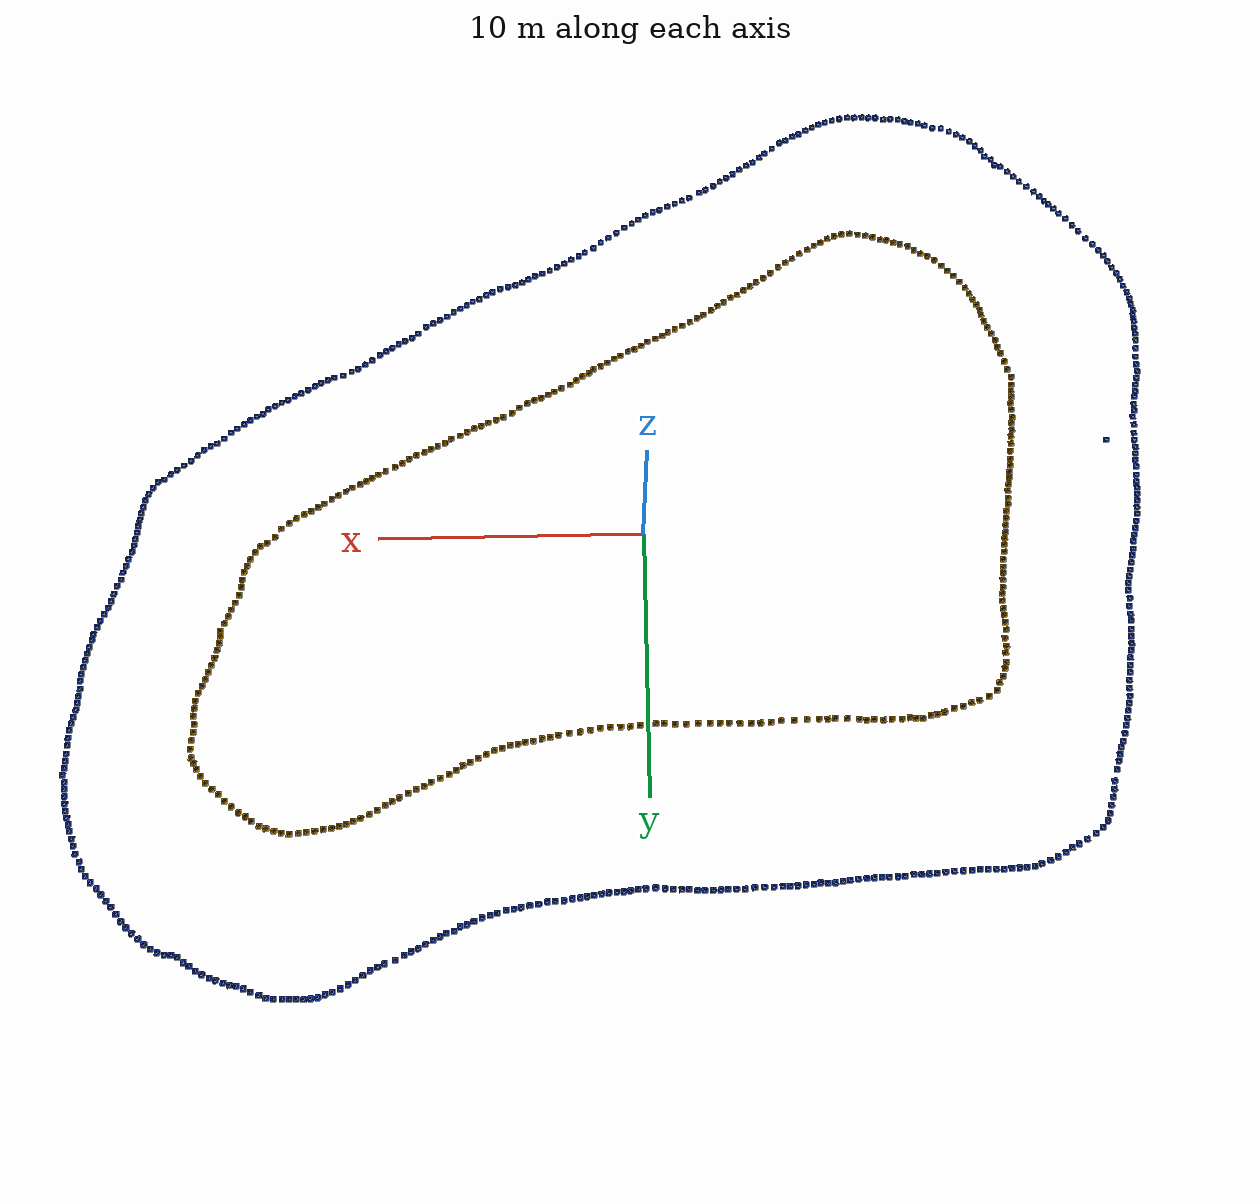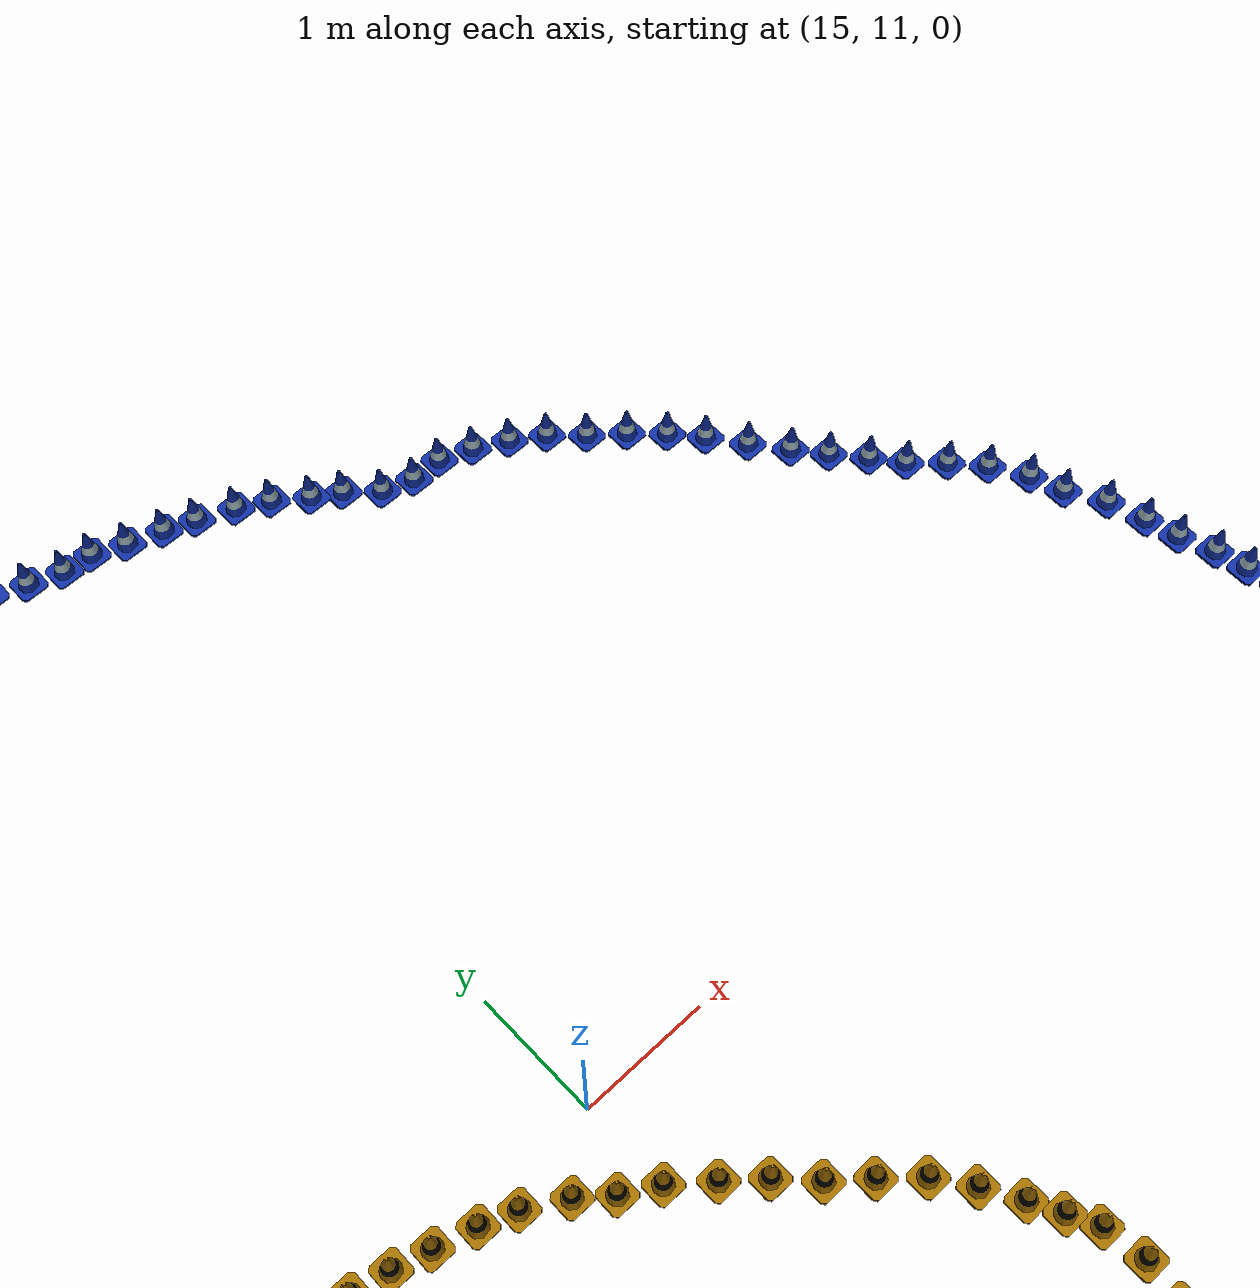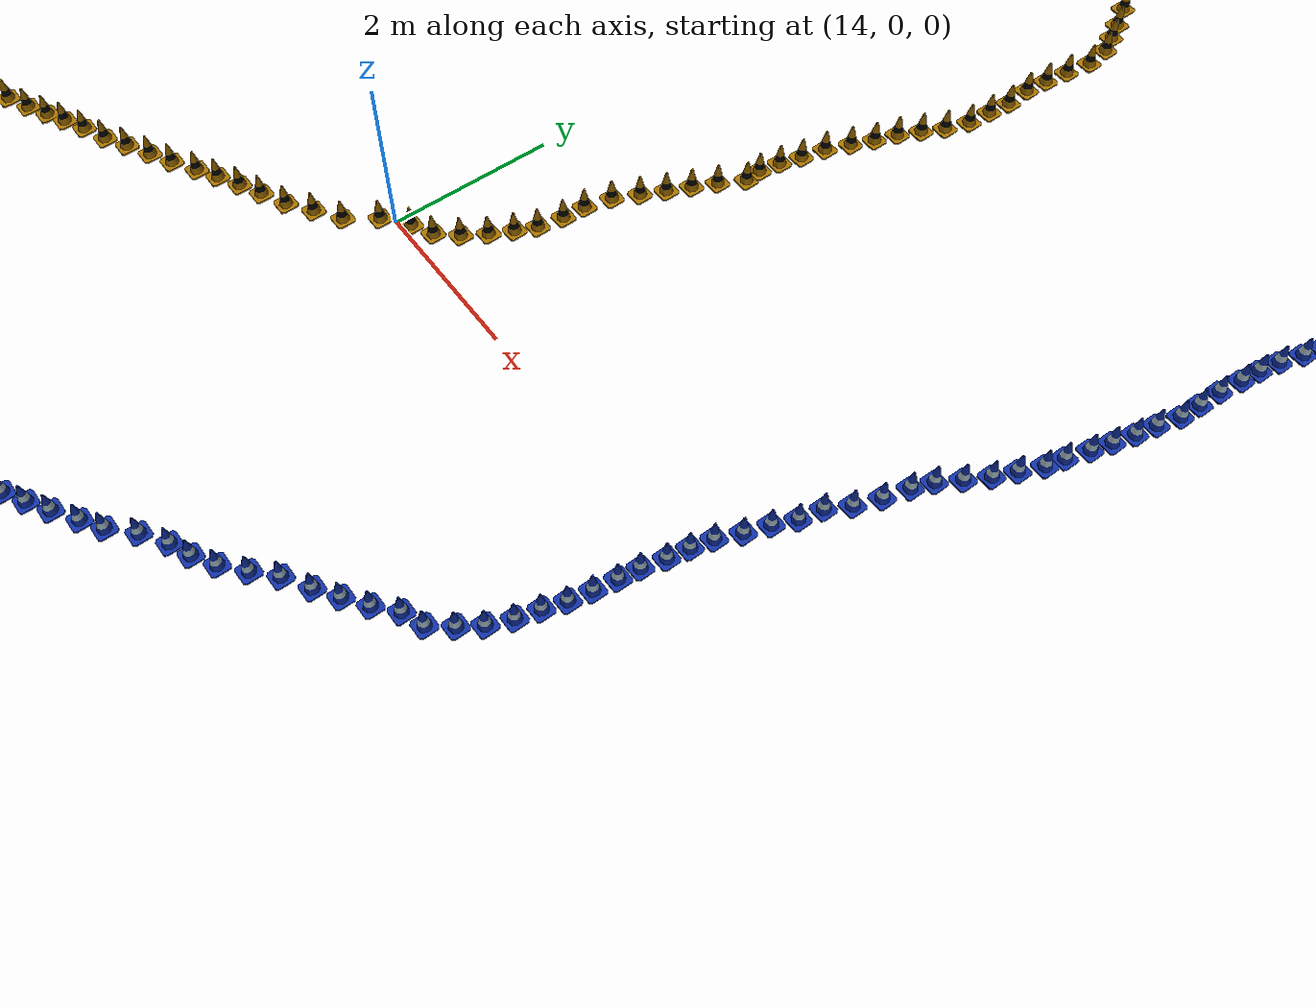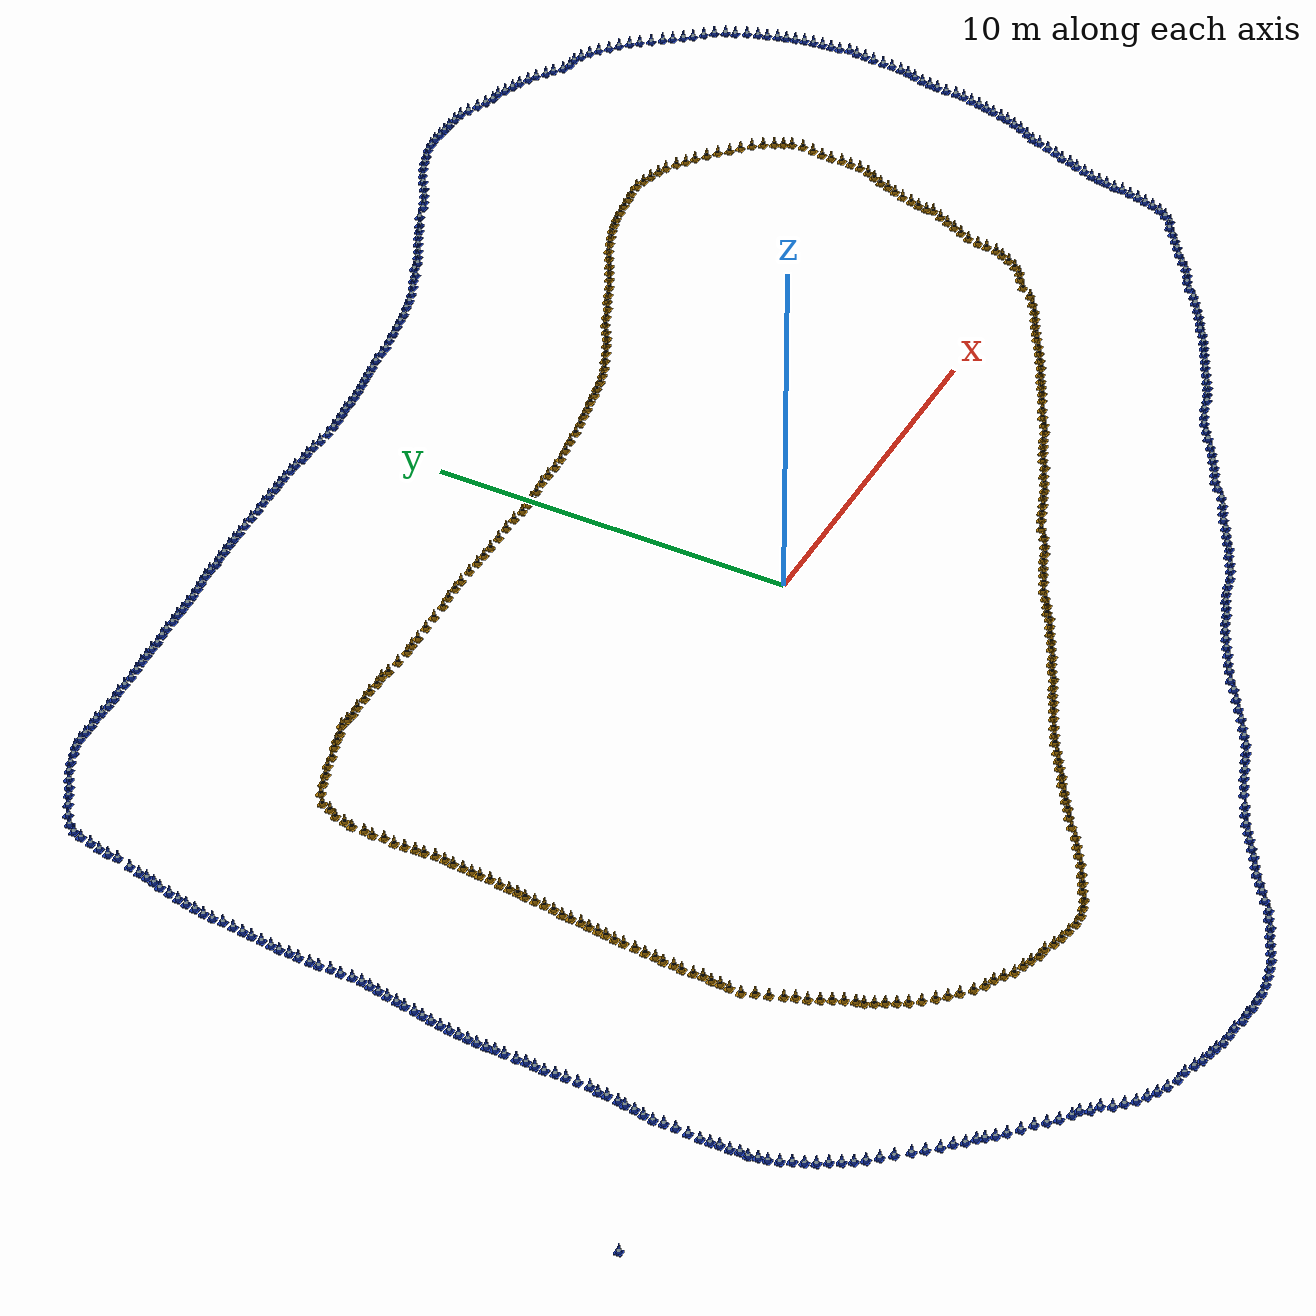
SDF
<?xml version='1.0'?>
<sdf version='1.6'>
  <model name='small_track'>
    <link name='link_0'>
      <pose frame=''>-17.0129 9.72719 0.079001 0 -0 0</pose>
      <self_collide>0</self_collide>
      <enable_wind>0</enable_wind>
      <kinematic>0</kinematic>
      <visual name='visual'>
        <geometry>
          <mesh>
            <uri>model://eufs_description/meshes/cone_blue.dae</uri>
          </mesh>
        </geometry>
        <material>
          <shader type='pixel'/>
        </material>
        <pose frame=''>0 0 0 0 -0 0</pose>
        <transparency>0</transparency>
        <cast_shadows>1</cast_shadows>
      </visual>
    </link>
    <link name='link_0_clone'>
      <pose frame=''>-12.7541 12.8712 0.079001 0 -0 0</pose>
      <self_collide>0</self_collide>
      <enable_wind>0</enable_wind>
      <kinematic>0</kinematic>
      <visual name='visual'>
        <geometry>
          <mesh>
            <uri>model://eufs_description/meshes/cone_blue.dae</uri>
          </mesh>
        </geometry>
        <material>
          <shader type='pixel'/>
        </material>
        <pose frame=''>0 0 0 0 -0 0</pose>
        <transparency>0</transparency>
        <cast_shadows>1</cast_shadows>
      </visual>
    </link>
    <link name='link_0_clone_0_clone'>
      <pose frame=''>-12.2686 6.61784 0.070966 -0.001555 0.00019 -5.2e-05</pose>
      <self_collide>0</self_collide>
      <enable_wind>0</enable_wind>
      <kinematic>0</kinematic>
      <visual name='visual'>
        <geometry>
          <mesh>
            <uri>model://eufs_description/meshes/cone_yellow.dae</uri>
          </mesh>
        </geometry>
        <material>
          <shader type='pixel'/>
        </material>
        <pose frame=''>0 0 0 0 -0 0</pose>
        <transparency>0</transparency>
        <cast_shadows>1</cast_shadows>
      </visual>
    </link>
    <link name='link_0_clone_0_clone_clone'>
      <pose frame=''>-9.65737 7.2378 0.083534 0.001019 -0.000437 -0.000128</pose>
      <self_collide>0</self_collide>
      <enable_wind>0</enable_wind>
      <kinematic>0</kinematic>
      <visual name='visual'>
        <geometry>
          <mesh>
            <uri>model://eufs_description/meshes/cone_yellow.dae</uri>
          </mesh>
        </geometry>
        <material>
          <shader type='pixel'/>
        </material>
        <pose frame=''>0 0 0 0 -0 0</pose>
        <transparency>0</transparency>
        <cast_shadows>1</cast_shadows>
      </visual>
    </link>
    <link name='link_0_clone_0_clone_clone_clone'>
      <pose frame=''>-8.9918 7.27282 0.083534 0.001019 -0.000437 -0.000128</pose>
      <self_collide>0</self_collide>
      <enable_wind>0</enable_wind>
      <kinematic>0</kinematic>
      <visual name='visual'>
        <geometry>
          <mesh>
            <uri>model://eufs_description/meshes/cone_yellow.dae</uri>
          </mesh>
        </geometry>
        <material>
          <shader type='pixel'/>
        </material>
        <pose frame=''>0 0 0 0 -0 0</pose>
        <transparency>0</transparency>
        <cast_shadows>1</cast_shadows>
      </visual>
    </link>
    <link name='link_0_clone_0_clone_clone_clone_0'>
      <pose frame=''>-8.33728 7.27492 0.083534 0.001019 -0.000437 -0.000128</pose>
      <self_collide>0</self_collide>
      <enable_wind>0</enable_wind>
      <kinematic>0</kinematic>
      <visual name='visual'>
        <geometry>
          <mesh>
            <uri>model://eufs_description/meshes/cone_yellow.dae</uri>
          </mesh>
        </geometry>
        <material>
          <shader type='pixel'/>
        </material>
        <pose frame=''>0 0 0 0 -0 0</pose>
        <transparency>0</transparency>
        <cast_shadows>1</cast_shadows>
      </visual>
    </link>
    <link name='link_0_clone_0_clone_clone_clone_1'>
      <pose frame=''>-7.7938 7.24817 0.083534 0.001019 -0.000437 -0.000128</pose>
      <self_collide>0</self_collide>
      <enable_wind>0</enable_wind>
      <kinematic>0</kinematic>
      <visual name='visual'>
        <geometry>
          <mesh>
            <uri>model://eufs_description/meshes/cone_yellow.dae</uri>
          </mesh>
        </geometry>
        <material>
          <shader type='pixel'/>
        </material>
        <pose frame=''>0 0 0 0 -0 0</pose>
        <transparency>0</transparency>
        <cast_shadows>1</cast_shadows>
      </visual>
    </link>
    <link name='link_0_clone_0_clone_clone_clone_10'>
      <pose frame=''>-2.9839 7.30929 0.083534 0.001019 -0.000437 -0.000128</pose>
      <self_collide>0</self_collide>
      <enable_wind>0</enable_wind>
      <kinematic>0</kinematic>
      <visual name='visual'>
        <geometry>
          <mesh>
            <uri>model://eufs_description/meshes/cone_yellow.dae</uri>
          </mesh>
        </geometry>
        <material>
          <shader type='pixel'/>
        </material>
        <pose frame=''>0 0 0 0 -0 0</pose>
        <transparency>0</transparency>
        <cast_shadows>1</cast_shadows>
      </visual>
    </link>
    <link name='link_0_clone_0_clone_clone_clone_100'>
      <pose frame=''>13.1141 -0.872162 0.083534 0.001019 -0.000437 -0.000128</pose>
      <self_collide>0</self_collide>
      <enable_wind>0</enable_wind>
      <kinematic>0</kinematic>
      <visual name='visual'>
        <geometry>
          <mesh>
            <uri>model://eufs_description/meshes/cone_yellow.dae</uri>
          </mesh>
        </geometry>
        <material>
          <shader type='pixel'/>
        </material>
        <pose frame=''>0 0 0 0 -0 0</pose>
        <transparency>0</transparency>
        <cast_shadows>1</cast_shadows>
      </visual>
    </link>
    <link name='link_0_clone_0_clone_clone_clone_101'>
      <pose frame=''>12.8225 -1.01796 0.083534 0.001019 -0.000437 -0.000128</pose>
      <self_collide>0</self_collide>
      <enable_wind>0</enable_wind>
      <kinematic>0</kinematic>
      <visual name='visual'>
        <geometry>
          <mesh>
            <uri>model://eufs_description/meshes/cone_yellow.dae</uri>
          </mesh>
        </geometry>
        <material>
          <shader type='pixel'/>
        </material>
        <pose frame=''>0 0 0 0 -0 0</pose>
        <transparency>0</transparency>
        <cast_shadows>1</cast_shadows>
      </visual>
    </link>
    <link name='link_0_clone_0_clone_clone_clone_102'>
      <pose frame=''>12.5636 -1.15109 0.083534 0.001019 -0.000437 -0.000128</pose>
      <self_collide>0</self_collide>
      <enable_wind>0</enable_wind>
      <kinematic>0</kinematic>
      <visual name='visual'>
        <geometry>
          <mesh>
            <uri>model://eufs_description/meshes/cone_yellow.dae</uri>
          </mesh>
        </geometry>
        <material>
          <shader type='pixel'/>
        </material>
        <pose frame=''>0 0 0 0 -0 0</pose>
        <transparency>0</transparency>
        <cast_shadows>1</cast_shadows>
      </visual>
    </link>
    <link name='link_0_clone_0_clone_clone_clone_103'>
      <pose frame=''>12.3117 -1.29269 0.083534 0.001019 -0.000437 -0.000128</pose>
      <self_collide>0</self_collide>
      <enable_wind>0</enable_wind>
      <kinematic>0</kinematic>
      <visual name='visual'>
        <geometry>
          <mesh>
            <uri>model://eufs_description/meshes/cone_yellow.dae</uri>
          </mesh>
        </geometry>
        <material>
          <shader type='pixel'/>
        </material>
        <pose frame=''>0 0 0 0 -0 0</pose>
        <transparency>0</transparency>
        <cast_shadows>1</cast_shadows>
      </visual>
    </link>
    <link name='link_0_clone_0_clone_clone_clone_104'>
      <pose frame=''>11.8008 -1.6031 0.083534 0.001019 -0.000437 -0.000128</pose>
      <self_collide>0</self_collide>
      <enable_wind>0</enable_wind>
      <kinematic>0</kinematic>
      <visual name='visual'>
        <geometry>
          <mesh>
            <uri>model://eufs_description/meshes/cone_yellow.dae</uri>
          </mesh>
        </geometry>
        <material>
          <shader type='pixel'/>
        </material>
        <pose frame=''>0 0 0 0 -0 0</pose>
        <transparency>0</transparency>
        <cast_shadows>1</cast_shadows>
      </visual>
    </link>
    <link name='link_0_clone_0_clone_clone_clone_105'>
      <pose frame=''>11.5435 -1.74671 0.083534 0.001019 -0.000437 -0.000128</pose>
      <self_collide>0</self_collide>
      <enable_wind>0</enable_wind>
      <kinematic>0</kinematic>
      <visual name='visual'>
        <geometry>
          <mesh>
            <uri>model://eufs_description/meshes/cone_yellow.dae</uri>
          </mesh>
        </geometry>
        <material>
          <shader type='pixel'/>
        </material>
        <pose frame=''>0 0 0 0 -0 0</pose>
        <transparency>0</transparency>
        <cast_shadows>1</cast_shadows>
      </visual>
    </link>
    <link name='link_0_clone_0_clone_clone_clone_106'>
      <pose frame=''>11.2722 -1.90004 0.083534 0.001019 -0.000437 -0.000128</pose>
      <self_collide>0</self_collide>
      <enable_wind>0</enable_wind>
      <kinematic>0</kinematic>
      <visual name='visual'>
        <geometry>
          <mesh>
            <uri>model://eufs_description/meshes/cone_yellow.dae</uri>
          </mesh>
        </geometry>
        <material>
          <shader type='pixel'/>
        </material>
        <pose frame=''>0 0 0 0 -0 0</pose>
        <transparency>0</transparency>
        <cast_shadows>1</cast_shadows>
      </visual>
    </link>
    <link name='link_0_clone_0_clone_clone_clone_107'>
      <pose frame=''>11.0201 -2.0512 0.083534 0.001019 -0.000437 -0.000128</pose>
      <self_collide>0</self_collide>
      <enable_wind>0</enable_wind>
      <kinematic>0</kinematic>
      <visual name='visual'>
        <geometry>
          <mesh>
            <uri>model://eufs_description/meshes/cone_yellow.dae</uri>
          </mesh>
        </geometry>
        <material>
          <shader type='pixel'/>
        </material>
        <pose frame=''>0 0 0 0 -0 0</pose>
        <transparency>0</transparency>
        <cast_shadows>1</cast_shadows>
      </visual>
    </link>
    <link name='link_0_clone_0_clone_clone_clone_108'>
      <pose frame=''>10.7345 -2.17208 0.083534 0.001019 -0.000437 -0.000128</pose>
      <self_collide>0</self_collide>
      <enable_wind>0</enable_wind>
      <kinematic>0</kinematic>
      <visual name='visual'>
        <geometry>
          <mesh>
            <uri>model://eufs_description/meshes/cone_yellow.dae</uri>
          </mesh>
        </geometry>
        <material>
          <shader type='pixel'/>
        </material>
        <pose frame=''>0 0 0 0 -0 0</pose>
        <transparency>0</transparency>
        <cast_shadows>1</cast_shadows>
      </visual>
    </link>
    <link name='link_0_clone_0_clone_clone_clone_109'>
      <pose frame=''>10.491 -2.30143 0.083534 0.001019 -0.000437 -0.000128</pose>
      <self_collide>0</self_collide>
      <enable_wind>0</enable_wind>
      <kinematic>0</kinematic>
      <visual name='visual'>
        <geometry>
          <mesh>
            <uri>model://eufs_description/meshes/cone_yellow.dae</uri>
          </mesh>
        </geometry>
        <material>
          <shader type='pixel'/>
        </material>
        <pose frame=''>0 0 0 0 -0 0</pose>
        <transparency>0</transparency>
        <cast_shadows>1</cast_shadows>
      </visual>
    </link>
    <link name='link_0_clone_0_clone_clone_clone_11'>
      <pose frame=''>-2.64614 7.30172 0.083534 0.001019 -0.000437 -0.000128</pose>
      <self_collide>0</self_collide>
      <enable_wind>0</enable_wind>
      <kinematic>0</kinematic>
      <visual name='visual'>
        <geometry>
          <mesh>
            <uri>model://eufs_description/meshes/cone_yellow.dae</uri>
          </mesh>
        </geometry>
        <material>
          <shader type='pixel'/>
        </material>
        <pose frame=''>0 0 0 0 -0 0</pose>
        <transparency>0</transparency>
        <cast_shadows>1</cast_shadows>
      </visual>
    </link>
    <link name='link_0_clone_0_clone_clone_clone_110'>
      <pose frame=''>10.273 -2.42019 0.083534 0.001019 -0.000437 -0.000128</pose>
      <self_collide>0</self_collide>
      <enable_wind>0</enable_wind>
      <kinematic>0</kinematic>
      <visual name='visual'>
        <geometry>
          <mesh>
            <uri>model://eufs_description/meshes/cone_yellow.dae</uri>
          </mesh>
        </geometry>
        <material>
          <shader type='pixel'/>
        </material>
        <pose frame=''>0 0 0 0 -0 0</pose>
        <transparency>0</transparency>
        <cast_shadows>1</cast_shadows>
      </visual>
    </link>
    <link name='link_0_clone_0_clone_clone_clone_111'>
      <pose frame=''>10.0342 -2.54966 0.083534 0.001019 -0.000437 -0.000128</pose>
      <self_collide>0</self_collide>
      <enable_wind>0</enable_wind>
      <kinematic>0</kinematic>
      <visual name='visual'>
        <geometry>
          <mesh>
            <uri>model://eufs_description/meshes/cone_yellow.dae</uri>
          </mesh>
        </geometry>
        <material>
          <shader type='pixel'/>
        </material>
        <pose frame=''>0 0 0 0 -0 0</pose>
        <transparency>0</transparency>
        <cast_shadows>1</cast_shadows>
      </visual>
    </link>
    <link name='link_0_clone_0_clone_clone_clone_112'>
      <pose frame=''>9.76588 -2.67665 0.083534 0.001019 -0.000437 -0.000128</pose>
      <self_collide>0</self_collide>
      <enable_wind>0</enable_wind>
      <kinematic>0</kinematic>
      <visual name='visual'>
        <geometry>
          <mesh>
            <uri>model://eufs_description/meshes/cone_yellow.dae</uri>
          </mesh>
        </geometry>
        <material>
          <shader type='pixel'/>
        </material>
        <pose frame=''>0 0 0 0 -0 0</pose>
        <transparency>0</transparency>
        <cast_shadows>1</cast_shadows>
      </visual>
    </link>
    <link name='link_0_clone_0_clone_clone_clone_113'>
      <pose frame=''>9.13365 -2.99635 0.083534 0.001019 -0.000437 -0.000128</pose>
      <self_collide>0</self_collide>
      <enable_wind>0</enable_wind>
      <kinematic>0</kinematic>
      <visual name='visual'>
        <geometry>
          <mesh>
            <uri>model://eufs_description/meshes/cone_yellow.dae</uri>
          </mesh>
        </geometry>
        <material>
          <shader type='pixel'/>
        </material>
        <pose frame=''>0 0 0 0 -0 0</pose>
        <transparency>0</transparency>
        <cast_shadows>1</cast_shadows>
      </visual>
    </link>
    <link name='link_0_clone_0_clone_clone_clone_114'>
      <pose frame=''>8.86208 -3.16288 0.083534 0.001019 -0.000437 -0.000128</pose>
      <self_collide>0</self_collide>
      <enable_wind>0</enable_wind>
      <kinematic>0</kinematic>
      <visual name='visual'>
        <geometry>
          <mesh>
            <uri>model://eufs_description/meshes/cone_yellow.dae</uri>
          </mesh>
        </geometry>
        <material>
          <shader type='pixel'/>
        </material>
        <pose frame=''>0 0 0 0 -0 0</pose>
        <transparency>0</transparency>
        <cast_shadows>1</cast_shadows>
      </visual>
    </link>
    <link name='link_0_clone_0_clone_clone_clone_115'>
      <pose frame=''>8.59347 -3.31553 0.083534 0.001019 -0.000437 -0.000128</pose>
      <self_collide>0</self_collide>
      <enable_wind>0</enable_wind>
      <kinematic>0</kinematic>
      <visual name='visual'>
        <geometry>
          <mesh>
            <uri>model://eufs_description/meshes/cone_yellow.dae</uri>
          </mesh>
        </geometry>
        <material>
          <shader type='pixel'/>
        </material>
        <pose frame=''>0 0 0 0 -0 0</pose>
        <transparency>0</transparency>
        <cast_shadows>1</cast_shadows>
      </visual>
    </link>
    <link name='link_0_clone_0_clone_clone_clone_116'>
      <pose frame=''>8.28638 -3.41764 0.083534 0.001019 -0.000437 -0.000128</pose>
      <self_collide>0</self_collide>
      <enable_wind>0</enable_wind>
      <kinematic>0</kinematic>
      <visual name='visual'>
        <geometry>
          <mesh>
            <uri>model://eufs_description/meshes/cone_yellow.dae</uri>
          </mesh>
        </geometry>
        <material>
          <shader type='pixel'/>
        </material>
        <pose frame=''>0 0 0 0 -0 0</pose>
        <transparency>0</transparency>
        <cast_shadows>1</cast_shadows>
      </visual>
    </link>
    <link name='link_0_clone_0_clone_clone_clone_117'>
      <pose frame=''>8.04504 -3.53155 0.083534 0.001019 -0.000437 -0.000128</pose>
      <self_collide>0</self_collide>
      <enable_wind>0</enable_wind>
      <kinematic>0</kinematic>
      <visual name='visual'>
        <geometry>
          <mesh>
            <uri>model://eufs_description/meshes/cone_yellow.dae</uri>
          </mesh>
        </geometry>
        <material>
          <shader type='pixel'/>
        </material>
        <pose frame=''>0 0 0 0 -0 0</pose>
        <transparency>0</transparency>
        <cast_shadows>1</cast_shadows>
      </visual>
    </link>
    <link name='link_0_clone_0_clone_clone_clone_118'>
      <pose frame=''>7.78775 -3.64093 0.083534 0.001019 -0.000437 -0.000128</pose>
      <self_collide>0</self_collide>
      <enable_wind>0</enable_wind>
      <kinematic>0</kinematic>
      <visual name='visual'>
        <geometry>
          <mesh>
            <uri>model://eufs_description/meshes/cone_yellow.dae</uri>
          </mesh>
        </geometry>
        <material>
          <shader type='pixel'/>
        </material>
        <pose frame=''>0 0 0 0 -0 0</pose>
        <transparency>0</transparency>
        <cast_shadows>1</cast_shadows>
      </visual>
    </link>
    <link name='link_0_clone_0_clone_clone_clone_119'>
      <pose frame=''>7.51732 -3.76688 0.083534 0.001019 -0.000437 -0.000128</pose>
      <self_collide>0</self_collide>
      <enable_wind>0</enable_wind>
      <kinematic>0</kinematic>
      <visual name='visual'>
        <geometry>
          <mesh>
            <uri>model://eufs_description/meshes/cone_yellow.dae</uri>
          </mesh>
        </geometry>
        <material>
          <shader type='pixel'/>
        </material>
        <pose frame=''>0 0 0 0 -0 0</pose>
        <transparency>0</transparency>
        <cast_shadows>1</cast_shadows>
      </visual>
    </link>
    <link name='link_0_clone_0_clone_clone_clone_12'>
      <pose frame=''>-2.28085 7.30529 0.083534 0.001019 -0.000437 -0.000128</pose>
      <self_collide>0</self_collide>
      <enable_wind>0</enable_wind>
      <kinematic>0</kinematic>
      <visual name='visual'>
        <geometry>
          <mesh>
            <uri>model://eufs_description/meshes/cone_yellow.dae</uri>
          </mesh>
        </geometry>
        <material>
          <shader type='pixel'/>
        </material>
        <pose frame=''>0 0 0 0 -0 0</pose>
        <transparency>0</transparency>
        <cast_shadows>1</cast_shadows>
      </visual>
    </link>
    <link name='link_0_clone_0_clone_clone_clone_120'>
      <pose frame=''>6.93366 -4.06445 0.083534 0.001019 -0.000437 -0.000128</pose>
      <self_collide>0</self_collide>
      <enable_wind>0</enable_wind>
      <kinematic>0</kinematic>
      <visual name='visual'>
        <geometry>
          <mesh>
            <uri>model://eufs_description/meshes/cone_yellow.dae</uri>
          </mesh>
        </geometry>
        <material>
          <shader type='pixel'/>
        </material>
        <pose frame=''>0 0 0 0 -0 0</pose>
        <transparency>0</transparency>
        <cast_shadows>1</cast_shadows>
      </visual>
    </link>
    <link name='link_0_clone_0_clone_clone_clone_121'>
      <pose frame=''>6.67323 -4.20938 0.083534 0.001019 -0.000437 -0.000128</pose>
      <self_collide>0</self_collide>
      <enable_wind>0</enable_wind>
      <kinematic>0</kinematic>
      <visual name='visual'>
        <geometry>
          <mesh>
            <uri>model://eufs_description/meshes/cone_yellow.dae</uri>
          </mesh>
        </geometry>
        <material>
          <shader type='pixel'/>
        </material>
        <pose frame=''>0 0 0 0 -0 0</pose>
        <transparency>0</transparency>
        <cast_shadows>1</cast_shadows>
      </visual>
    </link>
    <link name='link_0_clone_0_clone_clone_clone_122'>
      <pose frame=''>6.40217 -4.34211 0.083534 0.001019 -0.000437 -0.000128</pose>
      <self_collide>0</self_collide>
      <enable_wind>0</enable_wind>
      <kinematic>0</kinematic>
      <visual name='visual'>
        <geometry>
          <mesh>
            <uri>model://eufs_description/meshes/cone_yellow.dae</uri>
          </mesh>
        </geometry>
        <material>
          <shader type='pixel'/>
        </material>
        <pose frame=''>0 0 0 0 -0 0</pose>
        <transparency>0</transparency>
        <cast_shadows>1</cast_shadows>
      </visual>
    </link>
    <link name='link_0_clone_0_clone_clone_clone_123'>
      <pose frame=''>6.11772 -4.44144 0.083534 0.001019 -0.000437 -0.000128</pose>
      <self_collide>0</self_collide>
      <enable_wind>0</enable_wind>
      <kinematic>0</kinematic>
      <visual name='visual'>
        <geometry>
          <mesh>
            <uri>model://eufs_description/meshes/cone_yellow.dae</uri>
          </mesh>
        </geometry>
        <material>
          <shader type='pixel'/>
        </material>
        <pose frame=''>0 0 0 0 -0 0</pose>
        <transparency>0</transparency>
        <cast_shadows>1</cast_shadows>
      </visual>
    </link>
    <link name='link_0_clone_0_clone_clone_clone_124'>
      <pose frame=''>5.8426 -4.56104 0.083534 0.001019 -0.000437 -0.000128</pose>
      <self_collide>0</self_collide>
      <enable_wind>0</enable_wind>
      <kinematic>0</kinematic>
      <visual name='visual'>
        <geometry>
          <mesh>
            <uri>model://eufs_description/meshes/cone_yellow.dae</uri>
          </mesh>
        </geometry>
        <material>
          <shader type='pixel'/>
        </material>
        <pose frame=''>0 0 0 0 -0 0</pose>
        <transparency>0</transparency>
        <cast_shadows>1</cast_shadows>
      </visual>
    </link>
    <link name='link_0_clone_0_clone_clone_clone_125'>
      <pose frame=''>5.55019 -4.66911 0.083534 0.001019 -0.000437 -0.000128</pose>
      <self_collide>0</self_collide>
      <enable_wind>0</enable_wind>
      <kinematic>0</kinematic>
      <visual name='visual'>
        <geometry>
          <mesh>
            <uri>model://eufs_description/meshes/cone_yellow.dae</uri>
          </mesh>
        </geometry>
        <material>
          <shader type='pixel'/>
        </material>
        <pose frame=''>0 0 0 0 -0 0</pose>
        <transparency>0</transparency>
        <cast_shadows>1</cast_shadows>
      </visual>
    </link>
    <link name='link_0_clone_0_clone_clone_clone_126'>
      <pose frame=''>5.27934 -4.78141 0.083534 0.001019 -0.000437 -0.000128</pose>
      <self_collide>0</self_collide>
      <enable_wind>0</enable_wind>
      <kinematic>0</kinematic>
      <visual name='visual'>
        <geometry>
          <mesh>
            <uri>model://eufs_description/meshes/cone_yellow.dae</uri>
          </mesh>
        </geometry>
        <material>
          <shader type='pixel'/>
        </material>
        <pose frame=''>0 0 0 0 -0 0</pose>
        <transparency>0</transparency>
        <cast_shadows>1</cast_shadows>
      </visual>
    </link>
    <link name='link_0_clone_0_clone_clone_clone_127'>
      <pose frame=''>4.93985 -4.94047 0.083534 0.001019 -0.000437 -0.000128</pose>
      <self_collide>0</self_collide>
      <enable_wind>0</enable_wind>
      <kinematic>0</kinematic>
      <visual name='visual'>
        <geometry>
          <mesh>
            <uri>model://eufs_description/meshes/cone_yellow.dae</uri>
          </mesh>
        </geometry>
        <material>
          <shader type='pixel'/>
        </material>
        <pose frame=''>0 0 0 0 -0 0</pose>
        <transparency>0</transparency>
        <cast_shadows>1</cast_shadows>
      </visual>
    </link>
    <link name='link_0_clone_0_clone_clone_clone_128'>
      <pose frame=''>4.34701 -5.32335 0.083534 0.001019 -0.000437 -0.000128</pose>
      <self_collide>0</self_collide>
      <enable_wind>0</enable_wind>
      <kinematic>0</kinematic>
      <visual name='visual'>
        <geometry>
          <mesh>
            <uri>model://eufs_description/meshes/cone_yellow.dae</uri>
          </mesh>
        </geometry>
        <material>
          <shader type='pixel'/>
        </material>
        <pose frame=''>0 0 0 0 -0 0</pose>
        <transparency>0</transparency>
        <cast_shadows>1</cast_shadows>
      </visual>
    </link>
    <link name='link_0_clone_0_clone_clone_clone_129'>
      <pose frame=''>4.07698 -5.45046 0.083534 0.001019 -0.000437 -0.000128</pose>
      <self_collide>0</self_collide>
      <enable_wind>0</enable_wind>
      <kinematic>0</kinematic>
      <visual name='visual'>
        <geometry>
          <mesh>
            <uri>model://eufs_description/meshes/cone_yellow.dae</uri>
          </mesh>
        </geometry>
        <material>
          <shader type='pixel'/>
        </material>
        <pose frame=''>0 0 0 0 -0 0</pose>
        <transparency>0</transparency>
        <cast_shadows>1</cast_shadows>
      </visual>
    </link>
    <link name='link_0_clone_0_clone_clone_clone_13'>
      <pose frame=''>-1.84187 7.30506 0.083534 0.001019 -0.000437 -0.000128</pose>
      <self_collide>0</self_collide>
      <enable_wind>0</enable_wind>
      <kinematic>0</kinematic>
      <visual name='visual'>
        <geometry>
          <mesh>
            <uri>model://eufs_description/meshes/cone_yellow.dae</uri>
          </mesh>
        </geometry>
        <material>
          <shader type='pixel'/>
        </material>
        <pose frame=''>0 0 0 0 -0 0</pose>
        <transparency>0</transparency>
        <cast_shadows>1</cast_shadows>
      </visual>
    </link>
    <link name='link_0_clone_0_clone_clone_clone_130'>
      <pose frame=''>3.81426 -5.533 0.083534 0.001019 -0.000437 -0.000128</pose>
      <self_collide>0</self_collide>
      <enable_wind>0</enable_wind>
      <kinematic>0</kinematic>
      <visual name='visual'>
        <geometry>
          <mesh>
            <uri>model://eufs_description/meshes/cone_yellow.dae</uri>
          </mesh>
        </geometry>
        <material>
          <shader type='pixel'/>
        </material>
        <pose frame=''>0 0 0 0 -0 0</pose>
        <transparency>0</transparency>
        <cast_shadows>1</cast_shadows>
      </visual>
    </link>
    <link name='link_0_clone_0_clone_clone_clone_131'>
      <pose frame=''>3.54966 -5.65988 0.083534 0.001019 -0.000437 -0.000128</pose>
      <self_collide>0</self_collide>
      <enable_wind>0</enable_wind>
      <kinematic>0</kinematic>
      <visual name='visual'>
        <geometry>
          <mesh>
            <uri>model://eufs_description/meshes/cone_yellow.dae</uri>
          </mesh>
        </geometry>
        <material>
          <shader type='pixel'/>
        </material>
        <pose frame=''>0 0 0 0 -0 0</pose>
        <transparency>0</transparency>
        <cast_shadows>1</cast_shadows>
      </visual>
    </link>
    <link name='link_0_clone_0_clone_clone_clone_132'>
      <pose frame=''>3.30491 -5.77677 0.083534 0.001019 -0.000437 -0.000128</pose>
      <self_collide>0</self_collide>
      <enable_wind>0</enable_wind>
      <kinematic>0</kinematic>
      <visual name='visual'>
        <geometry>
          <mesh>
            <uri>model://eufs_description/meshes/cone_yellow.dae</uri>
          </mesh>
        </geometry>
        <material>
          <shader type='pixel'/>
        </material>
        <pose frame=''>0 0 0 0 -0 0</pose>
        <transparency>0</transparency>
        <cast_shadows>1</cast_shadows>
      </visual>
    </link>
    <link name='link_0_clone_0_clone_clone_clone_133'>
      <pose frame=''>3.0318 -5.91301 0.083534 0.001019 -0.000437 -0.000128</pose>
      <self_collide>0</self_collide>
      <enable_wind>0</enable_wind>
      <kinematic>0</kinematic>
      <visual name='visual'>
        <geometry>
          <mesh>
            <uri>model://eufs_description/meshes/cone_yellow.dae</uri>
          </mesh>
        </geometry>
        <material>
          <shader type='pixel'/>
        </material>
        <pose frame=''>0 0 0 0 -0 0</pose>
        <transparency>0</transparency>
        <cast_shadows>1</cast_shadows>
      </visual>
    </link>
    <link name='link_0_clone_0_clone_clone_clone_134'>
      <pose frame=''>2.70619 -6.05726 0.083534 0.001019 -0.000437 -0.000128</pose>
      <self_collide>0</self_collide>
      <enable_wind>0</enable_wind>
      <kinematic>0</kinematic>
      <visual name='visual'>
        <geometry>
          <mesh>
            <uri>model://eufs_description/meshes/cone_yellow.dae</uri>
          </mesh>
        </geometry>
        <material>
          <shader type='pixel'/>
        </material>
        <pose frame=''>0 0 0 0 -0 0</pose>
        <transparency>0</transparency>
        <cast_shadows>1</cast_shadows>
      </visual>
    </link>
    <link name='link_0_clone_0_clone_clone_clone_135'>
      <pose frame=''>2.46405 -6.22703 0.083534 0.001019 -0.000437 -0.000128</pose>
      <self_collide>0</self_collide>
      <enable_wind>0</enable_wind>
      <kinematic>0</kinematic>
      <visual name='visual'>
        <geometry>
          <mesh>
            <uri>model://eufs_description/meshes/cone_yellow.dae</uri>
          </mesh>
        </geometry>
        <material>
          <shader type='pixel'/>
        </material>
        <pose frame=''>0 0 0 0 -0 0</pose>
        <transparency>0</transparency>
        <cast_shadows>1</cast_shadows>
      </visual>
    </link>
    <link name='link_0_clone_0_clone_clone_clone_136'>
      <pose frame=''>2.2196 -6.39038 0.083534 0.001019 -0.000437 -0.000128</pose>
      <self_collide>0</self_collide>
      <enable_wind>0</enable_wind>
      <kinematic>0</kinematic>
      <visual name='visual'>
        <geometry>
          <mesh>
            <uri>model://eufs_description/meshes/cone_yellow.dae</uri>
          </mesh>
        </geometry>
        <material>
          <shader type='pixel'/>
        </material>
        <pose frame=''>0 0 0 0 -0 0</pose>
        <transparency>0</transparency>
        <cast_shadows>1</cast_shadows>
      </visual>
    </link>
    <link name='link_0_clone_0_clone_clone_clone_137'>
      <pose frame=''>1.96198 -6.51117 0.083534 0.001019 -0.000437 -0.000128</pose>
      <self_collide>0</self_collide>
      <enable_wind>0</enable_wind>
      <kinematic>0</kinematic>
      <visual name='visual'>
        <geometry>
          <mesh>
            <uri>model://eufs_description/meshes/cone_yellow.dae</uri>
          </mesh>
        </geometry>
        <material>
          <shader type='pixel'/>
        </material>
        <pose frame=''>0 0 0 0 -0 0</pose>
        <transparency>0</transparency>
        <cast_shadows>1</cast_shadows>
      </visual>
    </link>
    <link name='link_0_clone_0_clone_clone_clone_138'>
      <pose frame=''>1.51301 -6.79833 0.083534 0.001019 -0.000437 -0.000128</pose>
      <self_collide>0</self_collide>
      <enable_wind>0</enable_wind>
      <kinematic>0</kinematic>
      <visual name='visual'>
        <geometry>
          <mesh>
            <uri>model://eufs_description/meshes/cone_yellow.dae</uri>
          </mesh>
        </geometry>
        <material>
          <shader type='pixel'/>
        </material>
        <pose frame=''>0 0 0 0 -0 0</pose>
        <transparency>0</transparency>
        <cast_shadows>1</cast_shadows>
      </visual>
    </link>
    <link name='link_0_clone_0_clone_clone_clone_139'>
      <pose frame=''>1.24682 -6.93411 0.083534 0.001019 -0.000437 -0.000128</pose>
      <self_collide>0</self_collide>
      <enable_wind>0</enable_wind>
      <kinematic>0</kinematic>
      <visual name='visual'>
        <geometry>
          <mesh>
            <uri>model://eufs_description/meshes/cone_yellow.dae</uri>
          </mesh>
        </geometry>
        <material>
          <shader type='pixel'/>
        </material>
        <pose frame=''>0 0 0 0 -0 0</pose>
        <transparency>0</transparency>
        <cast_shadows>1</cast_shadows>
      </visual>
    </link>
    <link name='link_0_clone_0_clone_clone_clone_14'>
      <pose frame=''>-1.40463 7.31913 0.083534 0.001019 -0.000437 -0.000128</pose>
      <self_collide>0</self_collide>
      <enable_wind>0</enable_wind>
      <kinematic>0</kinematic>
      <visual name='visual'>
        <geometry>
          <mesh>
            <uri>model://eufs_description/meshes/cone_yellow.dae</uri>
          </mesh>
        </geometry>
        <material>
          <shader type='pixel'/>
        </material>
        <pose frame=''>0 0 0 0 -0 0</pose>
        <transparency>0</transparency>
        <cast_shadows>1</cast_shadows>
      </visual>
    </link>
    <link name='link_0_clone_0_clone_clone_clone_140'>
      <pose frame=''>0.990534 -7.0912 0.083534 0.001019 -0.000437 -0.000128</pose>
      <self_collide>0</self_collide>
      <enable_wind>0</enable_wind>
      <kinematic>0</kinematic>
      <visual name='visual'>
        <geometry>
          <mesh>
            <uri>model://eufs_description/meshes/cone_yellow.dae</uri>
          </mesh>
        </geometry>
        <material>
          <shader type='pixel'/>
        </material>
        <pose frame=''>0 0 0 0 -0 0</pose>
        <transparency>0</transparency>
        <cast_shadows>1</cast_shadows>
      </visual>
    </link>
    <link name='link_0_clone_0_clone_clone_clone_141'>
      <pose frame=''>0.734557 -7.21139 0.083534 0.001019 -0.000437 -0.000128</pose>
      <self_collide>0</self_collide>
      <enable_wind>0</enable_wind>
      <kinematic>0</kinematic>
      <visual name='visual'>
        <geometry>
          <mesh>
            <uri>model://eufs_description/meshes/cone_yellow.dae</uri>
          </mesh>
        </geometry>
        <material>
          <shader type='pixel'/>
        </material>
        <pose frame=''>0 0 0 0 -0 0</pose>
        <transparency>0</transparency>
        <cast_shadows>1</cast_shadows>
      </visual>
    </link>
    <link name='link_0_clone_0_clone_clone_clone_142'>
      <pose frame=''>0.454353 -7.38079 0.083534 0.001019 -0.000437 -0.000128</pose>
      <self_collide>0</self_collide>
      <enable_wind>0</enable_wind>
      <kinematic>0</kinematic>
      <visual name='visual'>
        <geometry>
          <mesh>
            <uri>model://eufs_description/meshes/cone_yellow.dae</uri>
          </mesh>
        </geometry>
        <material>
          <shader type='pixel'/>
        </material>
        <pose frame=''>0 0 0 0 -0 0</pose>
        <transparency>0</transparency>
        <cast_shadows>1</cast_shadows>
      </visual>
    </link>
    <link name='link_0_clone_0_clone_clone_clone_143'>
      <pose frame=''>0.1994 -7.47125 0.083534 0.001019 -0.000437 -0.000128</pose>
      <self_collide>0</self_collide>
      <enable_wind>0</enable_wind>
      <kinematic>0</kinematic>
      <visual name='visual'>
        <geometry>
          <mesh>
            <uri>model://eufs_description/meshes/cone_yellow.dae</uri>
          </mesh>
        </geometry>
        <material>
          <shader type='pixel'/>
        </material>
        <pose frame=''>0 0 0 0 -0 0</pose>
        <transparency>0</transparency>
        <cast_shadows>1</cast_shadows>
      </visual>
    </link>
    <link name='link_0_clone_0_clone_clone_clone_144'>
      <pose frame=''>-0.057484 -7.60772 0.083534 0.001019 -0.000437 -0.000128</pose>
      <self_collide>0</self_collide>
      <enable_wind>0</enable_wind>
      <kinematic>0</kinematic>
      <visual name='visual'>
        <geometry>
          <mesh>
            <uri>model://eufs_description/meshes/cone_yellow.dae</uri>
          </mesh>
        </geometry>
        <material>
          <shader type='pixel'/>
        </material>
        <pose frame=''>0 0 0 0 -0 0</pose>
        <transparency>0</transparency>
        <cast_shadows>1</cast_shadows>
      </visual>
    </link>
    <link name='link_0_clone_0_clone_clone_clone_145'>
      <pose frame=''>-0.31153 -7.7748 0.083534 0.001019 -0.000437 -0.000128</pose>
      <self_collide>0</self_collide>
      <enable_wind>0</enable_wind>
      <kinematic>0</kinematic>
      <visual name='visual'>
        <geometry>
          <mesh>
            <uri>model://eufs_description/meshes/cone_yellow.dae</uri>
          </mesh>
        </geometry>
        <material>
          <shader type='pixel'/>
        </material>
        <pose frame=''>0 0 0 0 -0 0</pose>
        <transparency>0</transparency>
        <cast_shadows>1</cast_shadows>
      </visual>
    </link>
    <link name='link_0_clone_0_clone_clone_clone_146'>
      <pose frame=''>-0.611483 -7.89575 0.083534 0.001019 -0.000437 -0.000128</pose>
      <self_collide>0</self_collide>
      <enable_wind>0</enable_wind>
      <kinematic>0</kinematic>
      <visual name='visual'>
        <geometry>
          <mesh>
            <uri>model://eufs_description/meshes/cone_yellow.dae</uri>
          </mesh>
        </geometry>
        <material>
          <shader type='pixel'/>
        </material>
        <pose frame=''>0 0 0 0 -0 0</pose>
        <transparency>0</transparency>
        <cast_shadows>1</cast_shadows>
      </visual>
    </link>
    <link name='link_0_clone_0_clone_clone_clone_147'>
      <pose frame=''>-0.882185 -8.01249 0.083534 0.001019 -0.000437 -0.000128</pose>
      <self_collide>0</self_collide>
      <enable_wind>0</enable_wind>
      <kinematic>0</kinematic>
      <visual name='visual'>
        <geometry>
          <mesh>
            <uri>model://eufs_description/meshes/cone_yellow.dae</uri>
          </mesh>
        </geometry>
        <material>
          <shader type='pixel'/>
        </material>
        <pose frame=''>0 0 0 0 -0 0</pose>
        <transparency>0</transparency>
        <cast_shadows>1</cast_shadows>
      </visual>
    </link>
    <link name='link_0_clone_0_clone_clone_clone_148'>
      <pose frame=''>-1.11327 -8.14685 0.083534 0.001019 -0.000437 -0.000128</pose>
      <self_collide>0</self_collide>
      <enable_wind>0</enable_wind>
      <kinematic>0</kinematic>
      <visual name='visual'>
        <geometry>
          <mesh>
            <uri>model://eufs_description/meshes/cone_yellow.dae</uri>
          </mesh>
        </geometry>
        <material>
          <shader type='pixel'/>
        </material>
        <pose frame=''>0 0 0 0 -0 0</pose>
        <transparency>0</transparency>
        <cast_shadows>1</cast_shadows>
      </visual>
    </link>
    <link name='link_0_clone_0_clone_clone_clone_149'>
      <pose frame=''>-1.38506 -8.27211 0.083534 0.001019 -0.000437 -0.000128</pose>
      <self_collide>0</self_collide>
      <enable_wind>0</enable_wind>
      <kinematic>0</kinematic>
      <visual name='visual'>
        <geometry>
          <mesh>
            <uri>model://eufs_description/meshes/cone_yellow.dae</uri>
          </mesh>
        </geometry>
        <material>
          <shader type='pixel'/>
        </material>
        <pose frame=''>0 0 0 0 -0 0</pose>
        <transparency>0</transparency>
        <cast_shadows>1</cast_shadows>
      </visual>
    </link>
    <link name='link_0_clone_0_clone_clone_clone_15'>
      <pose frame=''>-0.991103 7.31491 0.083534 0.001019 -0.000437 -0.000128</pose>
      <self_collide>0</self_collide>
      <enable_wind>0</enable_wind>
      <kinematic>0</kinematic>
      <visual name='visual'>
        <geometry>
          <mesh>
            <uri>model://eufs_description/meshes/cone_yellow.dae</uri>
          </mesh>
        </geometry>
        <material>
          <shader type='pixel'/>
        </material>
        <pose frame=''>0 0 0 0 -0 0</pose>
        <transparency>0</transparency>
        <cast_shadows>1</cast_shadows>
      </visual>
    </link>
    <link name='link_0_clone_0_clone_clone_clone_150'>
      <pose frame=''>-1.67997 -8.40902 0.083534 0.001019 -0.000437 -0.000128</pose>
      <self_collide>0</self_collide>
      <enable_wind>0</enable_wind>
      <kinematic>0</kinematic>
      <visual name='visual'>
        <geometry>
          <mesh>
            <uri>model://eufs_description/meshes/cone_yellow.dae</uri>
          </mesh>
        </geometry>
        <material>
          <shader type='pixel'/>
        </material>
        <pose frame=''>0 0 0 0 -0 0</pose>
        <transparency>0</transparency>
        <cast_shadows>1</cast_shadows>
      </visual>
    </link>
    <link name='link_0_clone_0_clone_clone_clone_151'>
      <pose frame=''>-2.25912 -8.70972 0.083534 0.001019 -0.000437 -0.000128</pose>
      <self_collide>0</self_collide>
      <enable_wind>0</enable_wind>
      <kinematic>0</kinematic>
      <visual name='visual'>
        <geometry>
          <mesh>
            <uri>model://eufs_description/meshes/cone_yellow.dae</uri>
          </mesh>
        </geometry>
        <material>
          <shader type='pixel'/>
        </material>
        <pose frame=''>0 0 0 0 -0 0</pose>
        <transparency>0</transparency>
        <cast_shadows>1</cast_shadows>
      </visual>
    </link>
    <link name='link_0_clone_0_clone_clone_clone_152'>
      <pose frame=''>-2.50899 -8.84343 0.083534 0.001019 -0.000437 -0.000128</pose>
      <self_collide>0</self_collide>
      <enable_wind>0</enable_wind>
      <kinematic>0</kinematic>
      <visual name='visual'>
        <geometry>
          <mesh>
            <uri>model://eufs_description/meshes/cone_yellow.dae</uri>
          </mesh>
        </geometry>
        <material>
          <shader type='pixel'/>
        </material>
        <pose frame=''>0 0 0 0 -0 0</pose>
        <transparency>0</transparency>
        <cast_shadows>1</cast_shadows>
      </visual>
    </link>
    <link name='link_0_clone_0_clone_clone_clone_153'>
      <pose frame=''>-2.81191 -9.03935 0.083534 0.001019 -0.000437 -0.000128</pose>
      <self_collide>0</self_collide>
      <enable_wind>0</enable_wind>
      <kinematic>0</kinematic>
      <visual name='visual'>
        <geometry>
          <mesh>
            <uri>model://eufs_description/meshes/cone_yellow.dae</uri>
          </mesh>
        </geometry>
        <material>
          <shader type='pixel'/>
        </material>
        <pose frame=''>0 0 0 0 -0 0</pose>
        <transparency>0</transparency>
        <cast_shadows>1</cast_shadows>
      </visual>
    </link>
    <link name='link_0_clone_0_clone_clone_clone_154'>
      <pose frame=''>-3.07869 -9.20889 0.083534 0.001019 -0.000437 -0.000128</pose>
      <self_collide>0</self_collide>
      <enable_wind>0</enable_wind>
      <kinematic>0</kinematic>
      <visual name='visual'>
        <geometry>
          <mesh>
            <uri>model://eufs_description/meshes/cone_yellow.dae</uri>
          </mesh>
        </geometry>
        <material>
          <shader type='pixel'/>
        </material>
        <pose frame=''>0 0 0 0 -0 0</pose>
        <transparency>0</transparency>
        <cast_shadows>1</cast_shadows>
      </visual>
    </link>
    <link name='link_0_clone_0_clone_clone_clone_155'>
      <pose frame=''>-3.31909 -9.35345 0.083534 0.001019 -0.000437 -0.000128</pose>
      <self_collide>0</self_collide>
      <enable_wind>0</enable_wind>
      <kinematic>0</kinematic>
      <visual name='visual'>
        <geometry>
          <mesh>
            <uri>model://eufs_description/meshes/cone_yellow.dae</uri>
          </mesh>
        </geometry>
        <material>
          <shader type='pixel'/>
        </material>
        <pose frame=''>0 0 0 0 -0 0</pose>
        <transparency>0</transparency>
        <cast_shadows>1</cast_shadows>
      </visual>
    </link>
    <link name='link_0_clone_0_clone_clone_clone_156'>
      <pose frame=''>-3.59452 -9.54711 0.083534 0.001019 -0.000437 -0.000128</pose>
      <self_collide>0</self_collide>
      <enable_wind>0</enable_wind>
      <kinematic>0</kinematic>
      <visual name='visual'>
        <geometry>
          <mesh>
            <uri>model://eufs_description/meshes/cone_yellow.dae</uri>
          </mesh>
        </geometry>
        <material>
          <shader type='pixel'/>
        </material>
        <pose frame=''>0 0 0 0 -0 0</pose>
        <transparency>0</transparency>
        <cast_shadows>1</cast_shadows>
      </visual>
    </link>
    <link name='link_0_clone_0_clone_clone_clone_157'>
      <pose frame=''>-3.84238 -9.66062 0.083534 0.001019 -0.000437 -0.000128</pose>
      <self_collide>0</self_collide>
      <enable_wind>0</enable_wind>
      <kinematic>0</kinematic>
      <visual name='visual'>
        <geometry>
          <mesh>
            <uri>model://eufs_description/meshes/cone_yellow.dae</uri>
          </mesh>
        </geometry>
        <material>
          <shader type='pixel'/>
        </material>
        <pose frame=''>0 0 0 0 -0 0</pose>
        <transparency>0</transparency>
        <cast_shadows>1</cast_shadows>
      </visual>
    </link>
    <link name='link_0_clone_0_clone_clone_clone_158'>
      <pose frame=''>-4.10978 -9.85436 0.083534 0.001019 -0.000437 -0.000128</pose>
      <self_collide>0</self_collide>
      <enable_wind>0</enable_wind>
      <kinematic>0</kinematic>
      <visual name='visual'>
        <geometry>
          <mesh>
            <uri>model://eufs_description/meshes/cone_yellow.dae</uri>
          </mesh>
        </geometry>
        <material>
          <shader type='pixel'/>
        </material>
        <pose frame=''>0 0 0 0 -0 0</pose>
        <transparency>0</transparency>
        <cast_shadows>1</cast_shadows>
      </visual>
    </link>
    <link name='link_0_clone_0_clone_clone_clone_159'>
      <pose frame=''>-4.3627 -10.0135 0.083534 0.001019 -0.000437 -0.000128</pose>
      <self_collide>0</self_collide>
      <enable_wind>0</enable_wind>
      <kinematic>0</kinematic>
      <visual name='visual'>
        <geometry>
          <mesh>
            <uri>model://eufs_description/meshes/cone_yellow.dae</uri>
          </mesh>
        </geometry>
        <material>
          <shader type='pixel'/>
        </material>
        <pose frame=''>0 0 0 0 -0 0</pose>
        <transparency>0</transparency>
        <cast_shadows>1</cast_shadows>
      </visual>
    </link>
    <link name='link_0_clone_0_clone_clone_clone_16'>
      <pose frame=''>2.52161 7.53676 0.083534 0.001019 -0.000437 -0.000128</pose>
      <self_collide>0</self_collide>
      <enable_wind>0</enable_wind>
      <kinematic>0</kinematic>
      <visual name='visual'>
        <geometry>
          <mesh>
            <uri>model://eufs_description/meshes/cone_yellow.dae</uri>
          </mesh>
        </geometry>
        <material>
          <shader type='pixel'/>
        </material>
        <pose frame=''>0 0 0 0 -0 0</pose>
        <transparency>0</transparency>
        <cast_shadows>1</cast_shadows>
      </visual>
    </link>
    <link name='link_0_clone_0_clone_clone_clone_160'>
      <pose frame=''>-4.60436 -10.1825 0.083534 0.001019 -0.000437 -0.000128</pose>
      <self_collide>0</self_collide>
      <enable_wind>0</enable_wind>
      <kinematic>0</kinematic>
      <visual name='visual'>
        <geometry>
          <mesh>
            <uri>model://eufs_description/meshes/cone_yellow.dae</uri>
          </mesh>
        </geometry>
        <material>
          <shader type='pixel'/>
        </material>
        <pose frame=''>0 0 0 0 -0 0</pose>
        <transparency>0</transparency>
        <cast_shadows>1</cast_shadows>
      </visual>
    </link>
    <link name='link_0_clone_0_clone_clone_clone_161'>
      <pose frame=''>-4.89092 -10.3475 0.083534 0.001019 -0.000437 -0.000128</pose>
      <self_collide>0</self_collide>
      <enable_wind>0</enable_wind>
      <kinematic>0</kinematic>
      <visual name='visual'>
        <geometry>
          <mesh>
            <uri>model://eufs_description/meshes/cone_yellow.dae</uri>
          </mesh>
        </geometry>
        <material>
          <shader type='pixel'/>
        </material>
        <pose frame=''>0 0 0 0 -0 0</pose>
        <transparency>0</transparency>
        <cast_shadows>1</cast_shadows>
      </visual>
    </link>
    <link name='link_0_clone_0_clone_clone_clone_162'>
      <pose frame=''>-5.48647 -10.8006 0.083534 0.001019 -0.000437 -0.000128</pose>
      <self_collide>0</self_collide>
      <enable_wind>0</enable_wind>
      <kinematic>0</kinematic>
      <visual name='visual'>
        <geometry>
          <mesh>
            <uri>model://eufs_description/meshes/cone_yellow.dae</uri>
          </mesh>
        </geometry>
        <material>
          <shader type='pixel'/>
        </material>
        <pose frame=''>0 0 0 0 -0 0</pose>
        <transparency>0</transparency>
        <cast_shadows>1</cast_shadows>
      </visual>
    </link>
    <link name='link_0_clone_0_clone_clone_clone_163'>
      <pose frame=''>-5.77222 -10.976 0.083534 0.001019 -0.000437 -0.000128</pose>
      <self_collide>0</self_collide>
      <enable_wind>0</enable_wind>
      <kinematic>0</kinematic>
      <visual name='visual'>
        <geometry>
          <mesh>
            <uri>model://eufs_description/meshes/cone_yellow.dae</uri>
          </mesh>
        </geometry>
        <material>
          <shader type='pixel'/>
        </material>
        <pose frame=''>0 0 0 0 -0 0</pose>
        <transparency>0</transparency>
        <cast_shadows>1</cast_shadows>
      </visual>
    </link>
    <link name='link_0_clone_0_clone_clone_clone_164'>
      <pose frame=''>-6.04849 -11.1504 0.083534 0.001019 -0.000437 -0.000128</pose>
      <self_collide>0</self_collide>
      <enable_wind>0</enable_wind>
      <kinematic>0</kinematic>
      <visual name='visual'>
        <geometry>
          <mesh>
            <uri>model://eufs_description/meshes/cone_yellow.dae</uri>
          </mesh>
        </geometry>
        <material>
          <shader type='pixel'/>
        </material>
        <pose frame=''>0 0 0 0 -0 0</pose>
        <transparency>0</transparency>
        <cast_shadows>1</cast_shadows>
      </visual>
    </link>
    <link name='link_0_clone_0_clone_clone_clone_165'>
      <pose frame=''>-6.33334 -11.349 0.083534 0.001019 -0.000437 -0.000128</pose>
      <self_collide>0</self_collide>
      <enable_wind>0</enable_wind>
      <kinematic>0</kinematic>
      <visual name='visual'>
        <geometry>
          <mesh>
            <uri>model://eufs_description/meshes/cone_yellow.dae</uri>
          </mesh>
        </geometry>
        <material>
          <shader type='pixel'/>
        </material>
        <pose frame=''>0 0 0 0 -0 0</pose>
        <transparency>0</transparency>
        <cast_shadows>1</cast_shadows>
      </visual>
    </link>
    <link name='link_0_clone_0_clone_clone_clone_166'>
      <pose frame=''>-6.6563 -11.5203 0.083534 0.001019 -0.000437 -0.000128</pose>
      <self_collide>0</self_collide>
      <enable_wind>0</enable_wind>
      <kinematic>0</kinematic>
      <visual name='visual'>
        <geometry>
          <mesh>
            <uri>model://eufs_description/meshes/cone_yellow.dae</uri>
          </mesh>
        </geometry>
        <material>
          <shader type='pixel'/>
        </material>
        <pose frame=''>0 0 0 0 -0 0</pose>
        <transparency>0</transparency>
        <cast_shadows>1</cast_shadows>
      </visual>
    </link>
    <link name='link_0_clone_0_clone_clone_clone_167'>
      <pose frame=''>-6.92883 -11.6734 0.083534 0.001019 -0.000437 -0.000128</pose>
      <self_collide>0</self_collide>
      <enable_wind>0</enable_wind>
      <kinematic>0</kinematic>
      <visual name='visual'>
        <geometry>
          <mesh>
            <uri>model://eufs_description/meshes/cone_yellow.dae</uri>
          </mesh>
        </geometry>
        <material>
          <shader type='pixel'/>
        </material>
        <pose frame=''>0 0 0 0 -0 0</pose>
        <transparency>0</transparency>
        <cast_shadows>1</cast_shadows>
      </visual>
    </link>
    <link name='link_0_clone_0_clone_clone_clone_168'>
      <pose frame=''>-7.18545 -11.7903 0.083534 0.001019 -0.000437 -0.000128</pose>
      <self_collide>0</self_collide>
      <enable_wind>0</enable_wind>
      <kinematic>0</kinematic>
      <visual name='visual'>
        <geometry>
          <mesh>
            <uri>model://eufs_description/meshes/cone_yellow.dae</uri>
          </mesh>
        </geometry>
        <material>
          <shader type='pixel'/>
        </material>
        <pose frame=''>0 0 0 0 -0 0</pose>
        <transparency>0</transparency>
        <cast_shadows>1</cast_shadows>
      </visual>
    </link>
    <link name='link_0_clone_0_clone_clone_clone_169'>
      <pose frame=''>-7.45671 -11.9667 0.083534 0.001019 -0.000437 -0.000128</pose>
      <self_collide>0</self_collide>
      <enable_wind>0</enable_wind>
      <kinematic>0</kinematic>
      <visual name='visual'>
        <geometry>
          <mesh>
            <uri>model://eufs_description/meshes/cone_yellow.dae</uri>
          </mesh>
        </geometry>
        <material>
          <shader type='pixel'/>
        </material>
        <pose frame=''>0 0 0 0 -0 0</pose>
        <transparency>0</transparency>
        <cast_shadows>1</cast_shadows>
      </visual>
    </link>
    <link name='link_0_clone_0_clone_clone_clone_17'>
      <pose frame=''>2.12817 7.47146 0.083534 0.001019 -0.000437 -0.000128</pose>
      <self_collide>0</self_collide>
      <enable_wind>0</enable_wind>
      <kinematic>0</kinematic>
      <visual name='visual'>
        <geometry>
          <mesh>
            <uri>model://eufs_description/meshes/cone_yellow.dae</uri>
          </mesh>
        </geometry>
        <material>
          <shader type='pixel'/>
        </material>
        <pose frame=''>0 0 0 0 -0 0</pose>
        <transparency>0</transparency>
        <cast_shadows>1</cast_shadows>
      </visual>
    </link>
    <link name='link_0_clone_0_clone_clone_clone_170'>
      <pose frame=''>-7.73912 -12.0653 0.083534 0.001019 -0.000437 -0.000128</pose>
      <self_collide>0</self_collide>
      <enable_wind>0</enable_wind>
      <kinematic>0</kinematic>
      <visual name='visual'>
        <geometry>
          <mesh>
            <uri>model://eufs_description/meshes/cone_yellow.dae</uri>
          </mesh>
        </geometry>
        <material>
          <shader type='pixel'/>
        </material>
        <pose frame=''>0 0 0 0 -0 0</pose>
        <transparency>0</transparency>
        <cast_shadows>1</cast_shadows>
      </visual>
    </link>
    <link name='link_0_clone_0_clone_clone_clone_171'>
      <pose frame=''>-8.03568 -12.1432 0.083534 0.001019 -0.000437 -0.000128</pose>
      <self_collide>0</self_collide>
      <enable_wind>0</enable_wind>
      <kinematic>0</kinematic>
      <visual name='visual'>
        <geometry>
          <mesh>
            <uri>model://eufs_description/meshes/cone_yellow.dae</uri>
          </mesh>
        </geometry>
        <material>
          <shader type='pixel'/>
        </material>
        <pose frame=''>0 0 0 0 -0 0</pose>
        <transparency>0</transparency>
        <cast_shadows>1</cast_shadows>
      </visual>
    </link>
    <link name='link_0_clone_0_clone_clone_clone_172'>
      <pose frame=''>-8.67258 -12.1122 0.083534 0.001019 -0.000437 -0.000128</pose>
      <self_collide>0</self_collide>
      <enable_wind>0</enable_wind>
      <kinematic>0</kinematic>
      <visual name='visual'>
        <geometry>
          <mesh>
            <uri>model://eufs_description/meshes/cone_yellow.dae</uri>
          </mesh>
        </geometry>
        <material>
          <shader type='pixel'/>
        </material>
        <pose frame=''>0 0 0 0 -0 0</pose>
        <transparency>0</transparency>
        <cast_shadows>1</cast_shadows>
      </visual>
    </link>
    <link name='link_0_clone_0_clone_clone_clone_173'>
      <pose frame=''>-8.96112 -12.0641 0.083534 0.001019 -0.000437 -0.000128</pose>
      <self_collide>0</self_collide>
      <enable_wind>0</enable_wind>
      <kinematic>0</kinematic>
      <visual name='visual'>
        <geometry>
          <mesh>
            <uri>model://eufs_description/meshes/cone_yellow.dae</uri>
          </mesh>
        </geometry>
        <material>
          <shader type='pixel'/>
        </material>
        <pose frame=''>0 0 0 0 -0 0</pose>
        <transparency>0</transparency>
        <cast_shadows>1</cast_shadows>
      </visual>
    </link>
    <link name='link_0_clone_0_clone_clone_clone_174'>
      <pose frame=''>-9.25112 -11.994 0.083534 0.001019 -0.000437 -0.000128</pose>
      <self_collide>0</self_collide>
      <enable_wind>0</enable_wind>
      <kinematic>0</kinematic>
      <visual name='visual'>
        <geometry>
          <mesh>
            <uri>model://eufs_description/meshes/cone_yellow.dae</uri>
          </mesh>
        </geometry>
        <material>
          <shader type='pixel'/>
        </material>
        <pose frame=''>0 0 0 0 -0 0</pose>
        <transparency>0</transparency>
        <cast_shadows>1</cast_shadows>
      </visual>
    </link>
    <link name='link_0_clone_0_clone_clone_clone_175'>
      <pose frame=''>-9.53373 -11.8784 0.083534 0.001019 -0.000437 -0.000128</pose>
      <self_collide>0</self_collide>
      <enable_wind>0</enable_wind>
      <kinematic>0</kinematic>
      <visual name='visual'>
        <geometry>
          <mesh>
            <uri>model://eufs_description/meshes/cone_yellow.dae</uri>
          </mesh>
        </geometry>
        <material>
          <shader type='pixel'/>
        </material>
        <pose frame=''>0 0 0 0 -0 0</pose>
        <transparency>0</transparency>
        <cast_shadows>1</cast_shadows>
      </visual>
    </link>
    <link name='link_0_clone_0_clone_clone_clone_176'>
      <pose frame=''>-10.044 -11.7524 0.083534 0.001019 -0.000437 -0.000128</pose>
      <self_collide>0</self_collide>
      <enable_wind>0</enable_wind>
      <kinematic>0</kinematic>
      <visual name='visual'>
        <geometry>
          <mesh>
            <uri>model://eufs_description/meshes/cone_yellow.dae</uri>
          </mesh>
        </geometry>
        <material>
          <shader type='pixel'/>
        </material>
        <pose frame=''>0 0 0 0 -0 0</pose>
        <transparency>0</transparency>
        <cast_shadows>1</cast_shadows>
      </visual>
    </link>
    <link name='link_0_clone_0_clone_clone_clone_177'>
      <pose frame=''>-10.3058 -11.6686 0.083534 0.001019 -0.000437 -0.000128</pose>
      <self_collide>0</self_collide>
      <enable_wind>0</enable_wind>
      <kinematic>0</kinematic>
      <visual name='visual'>
        <geometry>
          <mesh>
            <uri>model://eufs_description/meshes/cone_yellow.dae</uri>
          </mesh>
        </geometry>
        <material>
          <shader type='pixel'/>
        </material>
        <pose frame=''>0 0 0 0 -0 0</pose>
        <transparency>0</transparency>
        <cast_shadows>1</cast_shadows>
      </visual>
    </link>
    <link name='link_0_clone_0_clone_clone_clone_178'>
      <pose frame=''>-10.6108 -11.581 0.083534 0.001019 -0.000437 -0.000128</pose>
      <self_collide>0</self_collide>
      <enable_wind>0</enable_wind>
      <kinematic>0</kinematic>
      <visual name='visual'>
        <geometry>
          <mesh>
            <uri>model://eufs_description/meshes/cone_yellow.dae</uri>
          </mesh>
        </geometry>
        <material>
          <shader type='pixel'/>
        </material>
        <pose frame=''>0 0 0 0 -0 0</pose>
        <transparency>0</transparency>
        <cast_shadows>1</cast_shadows>
      </visual>
    </link>
    <link name='link_0_clone_0_clone_clone_clone_179'>
      <pose frame=''>-10.8402 -11.4051 0.083534 0.001019 -0.000437 -0.000128</pose>
      <self_collide>0</self_collide>
      <enable_wind>0</enable_wind>
      <kinematic>0</kinematic>
      <visual name='visual'>
        <geometry>
          <mesh>
            <uri>model://eufs_description/meshes/cone_yellow.dae</uri>
          </mesh>
        </geometry>
        <material>
          <shader type='pixel'/>
        </material>
        <pose frame=''>0 0 0 0 -0 0</pose>
        <transparency>0</transparency>
        <cast_shadows>1</cast_shadows>
      </visual>
    </link>
    <link name='link_0_clone_0_clone_clone_clone_18'>
      <pose frame=''>1.75533 7.40928 0.083534 0.001019 -0.000437 -0.000128</pose>
      <self_collide>0</self_collide>
      <enable_wind>0</enable_wind>
      <kinematic>0</kinematic>
      <visual name='visual'>
        <geometry>
          <mesh>
            <uri>model://eufs_description/meshes/cone_yellow.dae</uri>
          </mesh>
        </geometry>
        <material>
          <shader type='pixel'/>
        </material>
        <pose frame=''>0 0 0 0 -0 0</pose>
        <transparency>0</transparency>
        <cast_shadows>1</cast_shadows>
      </visual>
    </link>
    <link name='link_0_clone_0_clone_clone_clone_180'>
      <pose frame=''>-11.076 -11.2538 0.083534 0.001019 -0.000437 -0.000128</pose>
      <self_collide>0</self_collide>
      <enable_wind>0</enable_wind>
      <kinematic>0</kinematic>
      <visual name='visual'>
        <geometry>
          <mesh>
            <uri>model://eufs_description/meshes/cone_yellow.dae</uri>
          </mesh>
        </geometry>
        <material>
          <shader type='pixel'/>
        </material>
        <pose frame=''>0 0 0 0 -0 0</pose>
        <transparency>0</transparency>
        <cast_shadows>1</cast_shadows>
      </visual>
    </link>
    <link name='link_0_clone_0_clone_clone_clone_181'>
      <pose frame=''>-11.6173 -10.9757 0.083534 0.001019 -0.000437 -0.000128</pose>
      <self_collide>0</self_collide>
      <enable_wind>0</enable_wind>
      <kinematic>0</kinematic>
      <visual name='visual'>
        <geometry>
          <mesh>
            <uri>model://eufs_description/meshes/cone_yellow.dae</uri>
          </mesh>
        </geometry>
        <material>
          <shader type='pixel'/>
        </material>
        <pose frame=''>0 0 0 0 -0 0</pose>
        <transparency>0</transparency>
        <cast_shadows>1</cast_shadows>
      </visual>
    </link>
    <link name='link_0_clone_0_clone_clone_clone_182'>
      <pose frame=''>-11.8805 -10.7343 0.083534 0.001019 -0.000437 -0.000128</pose>
      <self_collide>0</self_collide>
      <enable_wind>0</enable_wind>
      <kinematic>0</kinematic>
      <visual name='visual'>
        <geometry>
          <mesh>
            <uri>model://eufs_description/meshes/cone_yellow.dae</uri>
          </mesh>
        </geometry>
        <material>
          <shader type='pixel'/>
        </material>
        <pose frame=''>0 0 0 0 -0 0</pose>
        <transparency>0</transparency>
        <cast_shadows>1</cast_shadows>
      </visual>
    </link>
    <link name='link_0_clone_0_clone_clone_clone_183'>
      <pose frame=''>-12.1051 -10.5229 0.083534 0.001019 -0.000437 -0.000128</pose>
      <self_collide>0</self_collide>
      <enable_wind>0</enable_wind>
      <kinematic>0</kinematic>
      <visual name='visual'>
        <geometry>
          <mesh>
            <uri>model://eufs_description/meshes/cone_yellow.dae</uri>
          </mesh>
        </geometry>
        <material>
          <shader type='pixel'/>
        </material>
        <pose frame=''>0 0 0 0 -0 0</pose>
        <transparency>0</transparency>
        <cast_shadows>1</cast_shadows>
      </visual>
    </link>
    <link name='link_0_clone_0_clone_clone_clone_184'>
      <pose frame=''>-12.3195 -10.3009 0.083534 0.001019 -0.000437 -0.000128</pose>
      <self_collide>0</self_collide>
      <enable_wind>0</enable_wind>
      <kinematic>0</kinematic>
      <visual name='visual'>
        <geometry>
          <mesh>
            <uri>model://eufs_description/meshes/cone_yellow.dae</uri>
          </mesh>
        </geometry>
        <material>
          <shader type='pixel'/>
        </material>
        <pose frame=''>0 0 0 0 -0 0</pose>
        <transparency>0</transparency>
        <cast_shadows>1</cast_shadows>
      </visual>
    </link>
    <link name='link_0_clone_0_clone_clone_clone_185'>
      <pose frame=''>-12.5485 -10.0397 0.083534 0.001019 -0.000437 -0.000128</pose>
      <self_collide>0</self_collide>
      <enable_wind>0</enable_wind>
      <kinematic>0</kinematic>
      <visual name='visual'>
        <geometry>
          <mesh>
            <uri>model://eufs_description/meshes/cone_yellow.dae</uri>
          </mesh>
        </geometry>
        <material>
          <shader type='pixel'/>
        </material>
        <pose frame=''>0 0 0 0 -0 0</pose>
        <transparency>0</transparency>
        <cast_shadows>1</cast_shadows>
      </visual>
    </link>
    <link name='link_0_clone_0_clone_clone_clone_186'>
      <pose frame=''>-12.7432 -9.78698 0.083534 0.001019 -0.000437 -0.000128</pose>
      <self_collide>0</self_collide>
      <enable_wind>0</enable_wind>
      <kinematic>0</kinematic>
      <visual name='visual'>
        <geometry>
          <mesh>
            <uri>model://eufs_description/meshes/cone_yellow.dae</uri>
          </mesh>
        </geometry>
        <material>
          <shader type='pixel'/>
        </material>
        <pose frame=''>0 0 0 0 -0 0</pose>
        <transparency>0</transparency>
        <cast_shadows>1</cast_shadows>
      </visual>
    </link>
    <link name='link_0_clone_0_clone_clone_clone_187'>
      <pose frame=''>-12.8837 -9.53933 0.083534 0.001019 -0.000437 -0.000128</pose>
      <self_collide>0</self_collide>
      <enable_wind>0</enable_wind>
      <kinematic>0</kinematic>
      <visual name='visual'>
        <geometry>
          <mesh>
            <uri>model://eufs_description/meshes/cone_yellow.dae</uri>
          </mesh>
        </geometry>
        <material>
          <shader type='pixel'/>
        </material>
        <pose frame=''>0 0 0 0 -0 0</pose>
        <transparency>0</transparency>
        <cast_shadows>1</cast_shadows>
      </visual>
    </link>
    <link name='link_0_clone_0_clone_clone_clone_188'>
      <pose frame=''>-13.0128 -9.29244 0.083534 0.001019 -0.000437 -0.000128</pose>
      <self_collide>0</self_collide>
      <enable_wind>0</enable_wind>
      <kinematic>0</kinematic>
      <visual name='visual'>
        <geometry>
          <mesh>
            <uri>model://eufs_description/meshes/cone_yellow.dae</uri>
          </mesh>
        </geometry>
        <material>
          <shader type='pixel'/>
        </material>
        <pose frame=''>0 0 0 0 -0 0</pose>
        <transparency>0</transparency>
        <cast_shadows>1</cast_shadows>
      </visual>
    </link>
    <link name='link_0_clone_0_clone_clone_clone_189'>
      <pose frame=''>-13.1483 -9.06972 0.083534 0.001019 -0.000437 -0.000128</pose>
      <self_collide>0</self_collide>
      <enable_wind>0</enable_wind>
      <kinematic>0</kinematic>
      <visual name='visual'>
        <geometry>
          <mesh>
            <uri>model://eufs_description/meshes/cone_yellow.dae</uri>
          </mesh>
        </geometry>
        <material>
          <shader type='pixel'/>
        </material>
        <pose frame=''>0 0 0 0 -0 0</pose>
        <transparency>0</transparency>
        <cast_shadows>1</cast_shadows>
      </visual>
    </link>
    <link name='link_0_clone_0_clone_clone_clone_19'>
      <pose frame=''>1.38976 7.38383 0.083534 0.001019 -0.000437 -0.000128</pose>
      <self_collide>0</self_collide>
      <enable_wind>0</enable_wind>
      <kinematic>0</kinematic>
      <visual name='visual'>
        <geometry>
          <mesh>
            <uri>model://eufs_description/meshes/cone_yellow.dae</uri>
          </mesh>
        </geometry>
        <material>
          <shader type='pixel'/>
        </material>
        <pose frame=''>0 0 0 0 -0 0</pose>
        <transparency>0</transparency>
        <cast_shadows>1</cast_shadows>
      </visual>
    </link>
    <link name='link_0_clone_0_clone_clone_clone_190'>
      <pose frame=''>-13.2621 -8.84583 0.083534 0.001019 -0.000437 -0.000128</pose>
      <self_collide>0</self_collide>
      <enable_wind>0</enable_wind>
      <kinematic>0</kinematic>
      <visual name='visual'>
        <geometry>
          <mesh>
            <uri>model://eufs_description/meshes/cone_yellow.dae</uri>
          </mesh>
        </geometry>
        <material>
          <shader type='pixel'/>
        </material>
        <pose frame=''>0 0 0 0 -0 0</pose>
        <transparency>0</transparency>
        <cast_shadows>1</cast_shadows>
      </visual>
    </link>
    <link name='link_0_clone_0_clone_clone_clone_191'>
      <pose frame=''>-13.3902 -8.37575 0.083534 0.001019 -0.000437 -0.000128</pose>
      <self_collide>0</self_collide>
      <enable_wind>0</enable_wind>
      <kinematic>0</kinematic>
      <visual name='visual'>
        <geometry>
          <mesh>
            <uri>model://eufs_description/meshes/cone_yellow.dae</uri>
          </mesh>
        </geometry>
        <material>
          <shader type='pixel'/>
        </material>
        <pose frame=''>0 0 0 0 -0 0</pose>
        <transparency>0</transparency>
        <cast_shadows>1</cast_shadows>
      </visual>
    </link>
    <link name='link_0_clone_0_clone_clone_clone_192'>
      <pose frame=''>-13.5043 -8.11503 0.083534 0.001019 -0.000437 -0.000128</pose>
      <self_collide>0</self_collide>
      <enable_wind>0</enable_wind>
      <kinematic>0</kinematic>
      <visual name='visual'>
        <geometry>
          <mesh>
            <uri>model://eufs_description/meshes/cone_yellow.dae</uri>
          </mesh>
        </geometry>
        <material>
          <shader type='pixel'/>
        </material>
        <pose frame=''>0 0 0 0 -0 0</pose>
        <transparency>0</transparency>
        <cast_shadows>1</cast_shadows>
      </visual>
    </link>
    <link name='link_0_clone_0_clone_clone_clone_193'>
      <pose frame=''>-13.6371 -7.8597 0.083534 0.001019 -0.000437 -0.000128</pose>
      <self_collide>0</self_collide>
      <enable_wind>0</enable_wind>
      <kinematic>0</kinematic>
      <visual name='visual'>
        <geometry>
          <mesh>
            <uri>model://eufs_description/meshes/cone_yellow.dae</uri>
          </mesh>
        </geometry>
        <material>
          <shader type='pixel'/>
        </material>
        <pose frame=''>0 0 0 0 -0 0</pose>
        <transparency>0</transparency>
        <cast_shadows>1</cast_shadows>
      </visual>
    </link>
    <link name='link_0_clone_0_clone_clone_clone_194'>
      <pose frame=''>-13.772 -7.58634 0.083534 0.001019 -0.000437 -0.000128</pose>
      <self_collide>0</self_collide>
      <enable_wind>0</enable_wind>
      <kinematic>0</kinematic>
      <visual name='visual'>
        <geometry>
          <mesh>
            <uri>model://eufs_description/meshes/cone_yellow.dae</uri>
          </mesh>
        </geometry>
        <material>
          <shader type='pixel'/>
        </material>
        <pose frame=''>0 0 0 0 -0 0</pose>
        <transparency>0</transparency>
        <cast_shadows>1</cast_shadows>
      </visual>
    </link>
    <link name='link_0_clone_0_clone_clone_clone_195'>
      <pose frame=''>-13.8383 -7.29548 0.083534 0.001019 -0.000437 -0.000128</pose>
      <self_collide>0</self_collide>
      <enable_wind>0</enable_wind>
      <kinematic>0</kinematic>
      <visual name='visual'>
        <geometry>
          <mesh>
            <uri>model://eufs_description/meshes/cone_yellow.dae</uri>
          </mesh>
        </geometry>
        <material>
          <shader type='pixel'/>
        </material>
        <pose frame=''>0 0 0 0 -0 0</pose>
        <transparency>0</transparency>
        <cast_shadows>1</cast_shadows>
      </visual>
    </link>
    <link name='link_0_clone_0_clone_clone_clone_196'>
      <pose frame=''>-13.9499 -7.03485 0.083534 0.001019 -0.000437 -0.000128</pose>
      <self_collide>0</self_collide>
      <enable_wind>0</enable_wind>
      <kinematic>0</kinematic>
      <visual name='visual'>
        <geometry>
          <mesh>
            <uri>model://eufs_description/meshes/cone_yellow.dae</uri>
          </mesh>
        </geometry>
        <material>
          <shader type='pixel'/>
        </material>
        <pose frame=''>0 0 0 0 -0 0</pose>
        <transparency>0</transparency>
        <cast_shadows>1</cast_shadows>
      </visual>
    </link>
    <link name='link_0_clone_0_clone_clone_clone_197'>
      <pose frame=''>-14.0726 -6.69751 0.083534 0.001019 -0.000437 -0.000128</pose>
      <self_collide>0</self_collide>
      <enable_wind>0</enable_wind>
      <kinematic>0</kinematic>
      <visual name='visual'>
        <geometry>
          <mesh>
            <uri>model://eufs_description/meshes/cone_yellow.dae</uri>
          </mesh>
        </geometry>
        <material>
          <shader type='pixel'/>
        </material>
        <pose frame=''>0 0 0 0 -0 0</pose>
        <transparency>0</transparency>
        <cast_shadows>1</cast_shadows>
      </visual>
    </link>
    <link name='link_0_clone_0_clone_clone_clone_198'>
      <pose frame=''>-14.1635 -6.36982 0.083534 0.001019 -0.000437 -0.000128</pose>
      <self_collide>0</self_collide>
      <enable_wind>0</enable_wind>
      <kinematic>0</kinematic>
      <visual name='visual'>
        <geometry>
          <mesh>
            <uri>model://eufs_description/meshes/cone_yellow.dae</uri>
          </mesh>
        </geometry>
        <material>
          <shader type='pixel'/>
        </material>
        <pose frame=''>0 0 0 0 -0 0</pose>
        <transparency>0</transparency>
        <cast_shadows>1</cast_shadows>
      </visual>
    </link>
    <link name='link_0_clone_0_clone_clone_clone_199'>
      <pose frame=''>-14.2741 -5.73281 0.083534 0.001019 -0.000437 -0.000128</pose>
      <self_collide>0</self_collide>
      <enable_wind>0</enable_wind>
      <kinematic>0</kinematic>
      <visual name='visual'>
        <geometry>
          <mesh>
            <uri>model://eufs_description/meshes/cone_yellow.dae</uri>
          </mesh>
        </geometry>
        <material>
          <shader type='pixel'/>
        </material>
        <pose frame=''>0 0 0 0 -0 0</pose>
        <transparency>0</transparency>
        <cast_shadows>1</cast_shadows>
      </visual>
    </link>
    <link name='link_0_clone_0_clone_clone_clone_2'>
      <pose frame=''>-7.35413 7.22012 0.083534 0.001019 -0.000437 -0.000128</pose>
      <self_collide>0</self_collide>
      <enable_wind>0</enable_wind>
      <kinematic>0</kinematic>
      <visual name='visual'>
        <geometry>
          <mesh>
            <uri>model://eufs_description/meshes/cone_yellow.dae</uri>
          </mesh>
        </geometry>
        <material>
          <shader type='pixel'/>
        </material>
        <pose frame=''>0 0 0 0 -0 0</pose>
        <transparency>0</transparency>
        <cast_shadows>1</cast_shadows>
      </visual>
    </link>
    <link name='link_0_clone_0_clone_clone_clone_20'>
      <pose frame=''>1.01282 7.38511 0.083534 0.001019 -0.000437 -0.000128</pose>
      <self_collide>0</self_collide>
      <enable_wind>0</enable_wind>
      <kinematic>0</kinematic>
      <visual name='visual'>
        <geometry>
          <mesh>
            <uri>model://eufs_description/meshes/cone_yellow.dae</uri>
          </mesh>
        </geometry>
        <material>
          <shader type='pixel'/>
        </material>
        <pose frame=''>0 0 0 0 -0 0</pose>
        <transparency>0</transparency>
        <cast_shadows>1</cast_shadows>
      </visual>
    </link>
    <link name='link_0_clone_0_clone_clone_clone_200'>
      <pose frame=''>-14.2442 -5.47157 0.083534 0.001019 -0.000437 -0.000128</pose>
      <self_collide>0</self_collide>
      <enable_wind>0</enable_wind>
      <kinematic>0</kinematic>
      <visual name='visual'>
        <geometry>
          <mesh>
            <uri>model://eufs_description/meshes/cone_yellow.dae</uri>
          </mesh>
        </geometry>
        <material>
          <shader type='pixel'/>
        </material>
        <pose frame=''>0 0 0 0 -0 0</pose>
        <transparency>0</transparency>
        <cast_shadows>1</cast_shadows>
      </visual>
    </link>
    <link name='link_0_clone_0_clone_clone_clone_201'>
      <pose frame=''>-14.2466 -5.22929 0.083534 0.001019 -0.000437 -0.000128</pose>
      <self_collide>0</self_collide>
      <enable_wind>0</enable_wind>
      <kinematic>0</kinematic>
      <visual name='visual'>
        <geometry>
          <mesh>
            <uri>model://eufs_description/meshes/cone_yellow.dae</uri>
          </mesh>
        </geometry>
        <material>
          <shader type='pixel'/>
        </material>
        <pose frame=''>0 0 0 0 -0 0</pose>
        <transparency>0</transparency>
        <cast_shadows>1</cast_shadows>
      </visual>
    </link>
    <link name='link_0_clone_0_clone_clone_clone_202'>
      <pose frame=''>-14.1929 -4.9805 0.083534 0.001019 -0.000437 -0.000128</pose>
      <self_collide>0</self_collide>
      <enable_wind>0</enable_wind>
      <kinematic>0</kinematic>
      <visual name='visual'>
        <geometry>
          <mesh>
            <uri>model://eufs_description/meshes/cone_yellow.dae</uri>
          </mesh>
        </geometry>
        <material>
          <shader type='pixel'/>
        </material>
        <pose frame=''>0 0 0 0 -0 0</pose>
        <transparency>0</transparency>
        <cast_shadows>1</cast_shadows>
      </visual>
    </link>
    <link name='link_0_clone_0_clone_clone_clone_203'>
      <pose frame=''>-14.2102 -4.71994 0.083534 0.001019 -0.000437 -0.000128</pose>
      <self_collide>0</self_collide>
      <enable_wind>0</enable_wind>
      <kinematic>0</kinematic>
      <visual name='visual'>
        <geometry>
          <mesh>
            <uri>model://eufs_description/meshes/cone_yellow.dae</uri>
          </mesh>
        </geometry>
        <material>
          <shader type='pixel'/>
        </material>
        <pose frame=''>0 0 0 0 -0 0</pose>
        <transparency>0</transparency>
        <cast_shadows>1</cast_shadows>
      </visual>
    </link>
    <link name='link_0_clone_0_clone_clone_clone_204'>
      <pose frame=''>-14.2235 -4.41366 0.083534 0.001019 -0.000437 -0.000128</pose>
      <self_collide>0</self_collide>
      <enable_wind>0</enable_wind>
      <kinematic>0</kinematic>
      <visual name='visual'>
        <geometry>
          <mesh>
            <uri>model://eufs_description/meshes/cone_yellow.dae</uri>
          </mesh>
        </geometry>
        <material>
          <shader type='pixel'/>
        </material>
        <pose frame=''>0 0 0 0 -0 0</pose>
        <transparency>0</transparency>
        <cast_shadows>1</cast_shadows>
      </visual>
    </link>
    <link name='link_0_clone_0_clone_clone_clone_205'>
      <pose frame=''>-14.1704 -4.17073 0.083534 0.001019 -0.000437 -0.000128</pose>
      <self_collide>0</self_collide>
      <enable_wind>0</enable_wind>
      <kinematic>0</kinematic>
      <visual name='visual'>
        <geometry>
          <mesh>
            <uri>model://eufs_description/meshes/cone_yellow.dae</uri>
          </mesh>
        </geometry>
        <material>
          <shader type='pixel'/>
        </material>
        <pose frame=''>0 0 0 0 -0 0</pose>
        <transparency>0</transparency>
        <cast_shadows>1</cast_shadows>
      </visual>
    </link>
    <link name='link_0_clone_0_clone_clone_clone_206'>
      <pose frame=''>-14.1729 -3.88138 0.083534 0.001019 -0.000437 -0.000128</pose>
      <self_collide>0</self_collide>
      <enable_wind>0</enable_wind>
      <kinematic>0</kinematic>
      <visual name='visual'>
        <geometry>
          <mesh>
            <uri>model://eufs_description/meshes/cone_yellow.dae</uri>
          </mesh>
        </geometry>
        <material>
          <shader type='pixel'/>
        </material>
        <pose frame=''>0 0 0 0 -0 0</pose>
        <transparency>0</transparency>
        <cast_shadows>1</cast_shadows>
      </visual>
    </link>
    <link name='link_0_clone_0_clone_clone_clone_207'>
      <pose frame=''>-14.1178 -3.64121 0.083534 0.001019 -0.000437 -0.000128</pose>
      <self_collide>0</self_collide>
      <enable_wind>0</enable_wind>
      <kinematic>0</kinematic>
      <visual name='visual'>
        <geometry>
          <mesh>
            <uri>model://eufs_description/meshes/cone_yellow.dae</uri>
          </mesh>
        </geometry>
        <material>
          <shader type='pixel'/>
        </material>
        <pose frame=''>0 0 0 0 -0 0</pose>
        <transparency>0</transparency>
        <cast_shadows>1</cast_shadows>
      </visual>
    </link>
    <link name='link_0_clone_0_clone_clone_clone_208'>
      <pose frame=''>-14.0986 -3.34888 0.083534 0.001019 -0.000437 -0.000128</pose>
      <self_collide>0</self_collide>
      <enable_wind>0</enable_wind>
      <kinematic>0</kinematic>
      <visual name='visual'>
        <geometry>
          <mesh>
            <uri>model://eufs_description/meshes/cone_yellow.dae</uri>
          </mesh>
        </geometry>
        <material>
          <shader type='pixel'/>
        </material>
        <pose frame=''>0 0 0 0 -0 0</pose>
        <transparency>0</transparency>
        <cast_shadows>1</cast_shadows>
      </visual>
    </link>
    <link name='link_0_clone_0_clone_clone_clone_209'>
      <pose frame=''>-14.0411 -2.73162 0.083534 0.001019 -0.000437 -0.000128</pose>
      <self_collide>0</self_collide>
      <enable_wind>0</enable_wind>
      <kinematic>0</kinematic>
      <visual name='visual'>
        <geometry>
          <mesh>
            <uri>model://eufs_description/meshes/cone_yellow.dae</uri>
          </mesh>
        </geometry>
        <material>
          <shader type='pixel'/>
        </material>
        <pose frame=''>0 0 0 0 -0 0</pose>
        <transparency>0</transparency>
        <cast_shadows>1</cast_shadows>
      </visual>
    </link>
    <link name='link_0_clone_0_clone_clone_clone_21'>
      <pose frame=''>0.6519 7.38174 0.083534 0.001019 -0.000437 -0.000128</pose>
      <self_collide>0</self_collide>
      <enable_wind>0</enable_wind>
      <kinematic>0</kinematic>
      <visual name='visual'>
        <geometry>
          <mesh>
            <uri>model://eufs_description/meshes/cone_yellow.dae</uri>
          </mesh>
        </geometry>
        <material>
          <shader type='pixel'/>
        </material>
        <pose frame=''>0 0 0 0 -0 0</pose>
        <transparency>0</transparency>
        <cast_shadows>1</cast_shadows>
      </visual>
    </link>
    <link name='link_0_clone_0_clone_clone_clone_210'>
      <pose frame=''>-14.0137 -2.47141 0.083534 0.001019 -0.000437 -0.000128</pose>
      <self_collide>0</self_collide>
      <enable_wind>0</enable_wind>
      <kinematic>0</kinematic>
      <visual name='visual'>
        <geometry>
          <mesh>
            <uri>model://eufs_description/meshes/cone_yellow.dae</uri>
          </mesh>
        </geometry>
        <material>
          <shader type='pixel'/>
        </material>
        <pose frame=''>0 0 0 0 -0 0</pose>
        <transparency>0</transparency>
        <cast_shadows>1</cast_shadows>
      </visual>
    </link>
    <link name='link_0_clone_0_clone_clone_clone_211'>
      <pose frame=''>-13.9711 -2.21169 0.083534 0.001019 -0.000437 -0.000128</pose>
      <self_collide>0</self_collide>
      <enable_wind>0</enable_wind>
      <kinematic>0</kinematic>
      <visual name='visual'>
        <geometry>
          <mesh>
            <uri>model://eufs_description/meshes/cone_yellow.dae</uri>
          </mesh>
        </geometry>
        <material>
          <shader type='pixel'/>
        </material>
        <pose frame=''>0 0 0 0 -0 0</pose>
        <transparency>0</transparency>
        <cast_shadows>1</cast_shadows>
      </visual>
    </link>
    <link name='link_0_clone_0_clone_clone_clone_212'>
      <pose frame=''>-13.9347 -1.97214 0.083534 0.001019 -0.000437 -0.000128</pose>
      <self_collide>0</self_collide>
      <enable_wind>0</enable_wind>
      <kinematic>0</kinematic>
      <visual name='visual'>
        <geometry>
          <mesh>
            <uri>model://eufs_description/meshes/cone_yellow.dae</uri>
          </mesh>
        </geometry>
        <material>
          <shader type='pixel'/>
        </material>
        <pose frame=''>0 0 0 0 -0 0</pose>
        <transparency>0</transparency>
        <cast_shadows>1</cast_shadows>
      </visual>
    </link>
    <link name='link_0_clone_0_clone_clone_clone_213'>
      <pose frame=''>-13.9019 -1.71091 0.083534 0.001019 -0.000437 -0.000128</pose>
      <self_collide>0</self_collide>
      <enable_wind>0</enable_wind>
      <kinematic>0</kinematic>
      <visual name='visual'>
        <geometry>
          <mesh>
            <uri>model://eufs_description/meshes/cone_yellow.dae</uri>
          </mesh>
        </geometry>
        <material>
          <shader type='pixel'/>
        </material>
        <pose frame=''>0 0 0 0 -0 0</pose>
        <transparency>0</transparency>
        <cast_shadows>1</cast_shadows>
      </visual>
    </link>
    <link name='link_0_clone_0_clone_clone_clone_214'>
      <pose frame=''>-13.8518 -1.46623 0.083534 0.001019 -0.000437 -0.000128</pose>
      <self_collide>0</self_collide>
      <enable_wind>0</enable_wind>
      <kinematic>0</kinematic>
      <visual name='visual'>
        <geometry>
          <mesh>
            <uri>model://eufs_description/meshes/cone_yellow.dae</uri>
          </mesh>
        </geometry>
        <material>
          <shader type='pixel'/>
        </material>
        <pose frame=''>0 0 0 0 -0 0</pose>
        <transparency>0</transparency>
        <cast_shadows>1</cast_shadows>
      </visual>
    </link>
    <link name='link_0_clone_0_clone_clone_clone_215'>
      <pose frame=''>-13.8398 -1.18133 0.083534 0.001019 -0.000437 -0.000128</pose>
      <self_collide>0</self_collide>
      <enable_wind>0</enable_wind>
      <kinematic>0</kinematic>
      <visual name='visual'>
        <geometry>
          <mesh>
            <uri>model://eufs_description/meshes/cone_yellow.dae</uri>
          </mesh>
        </geometry>
        <material>
          <shader type='pixel'/>
        </material>
        <pose frame=''>0 0 0 0 -0 0</pose>
        <transparency>0</transparency>
        <cast_shadows>1</cast_shadows>
      </visual>
    </link>
    <link name='link_0_clone_0_clone_clone_clone_216'>
      <pose frame=''>-13.8231 -0.930942 0.083534 0.001019 -0.000437 -0.000128</pose>
      <self_collide>0</self_collide>
      <enable_wind>0</enable_wind>
      <kinematic>0</kinematic>
      <visual name='visual'>
        <geometry>
          <mesh>
            <uri>model://eufs_description/meshes/cone_yellow.dae</uri>
          </mesh>
        </geometry>
        <material>
          <shader type='pixel'/>
        </material>
        <pose frame=''>0 0 0 0 -0 0</pose>
        <transparency>0</transparency>
        <cast_shadows>1</cast_shadows>
      </visual>
    </link>
    <link name='link_0_clone_0_clone_clone_clone_217'>
      <pose frame=''>-13.7493 -0.65911 0.083534 0.001019 -0.000437 -0.000128</pose>
      <self_collide>0</self_collide>
      <enable_wind>0</enable_wind>
      <kinematic>0</kinematic>
      <visual name='visual'>
        <geometry>
          <mesh>
            <uri>model://eufs_description/meshes/cone_yellow.dae</uri>
          </mesh>
        </geometry>
        <material>
          <shader type='pixel'/>
        </material>
        <pose frame=''>0 0 0 0 -0 0</pose>
        <transparency>0</transparency>
        <cast_shadows>1</cast_shadows>
      </visual>
    </link>
    <link name='link_0_clone_0_clone_clone_clone_218'>
      <pose frame=''>-13.7082 -0.379605 0.083534 0.001019 -0.000437 -0.000128</pose>
      <self_collide>0</self_collide>
      <enable_wind>0</enable_wind>
      <kinematic>0</kinematic>
      <visual name='visual'>
        <geometry>
          <mesh>
            <uri>model://eufs_description/meshes/cone_yellow.dae</uri>
          </mesh>
        </geometry>
        <material>
          <shader type='pixel'/>
        </material>
        <pose frame=''>0 0 0 0 -0 0</pose>
        <transparency>0</transparency>
        <cast_shadows>1</cast_shadows>
      </visual>
    </link>
    <link name='link_0_clone_0_clone_clone_clone_219'>
      <pose frame=''>-13.6585 0.179861 0.083534 0.001019 -0.000437 -0.000128</pose>
      <self_collide>0</self_collide>
      <enable_wind>0</enable_wind>
      <kinematic>0</kinematic>
      <visual name='visual'>
        <geometry>
          <mesh>
            <uri>model://eufs_description/meshes/cone_yellow.dae</uri>
          </mesh>
        </geometry>
        <material>
          <shader type='pixel'/>
        </material>
        <pose frame=''>0 0 0 0 -0 0</pose>
        <transparency>0</transparency>
        <cast_shadows>1</cast_shadows>
      </visual>
    </link>
    <link name='link_0_clone_0_clone_clone_clone_22'>
      <pose frame=''>0.284688 7.3346 0.083534 0.001019 -0.000437 -0.000128</pose>
      <self_collide>0</self_collide>
      <enable_wind>0</enable_wind>
      <kinematic>0</kinematic>
      <visual name='visual'>
        <geometry>
          <mesh>
            <uri>model://eufs_description/meshes/cone_yellow.dae</uri>
          </mesh>
        </geometry>
        <material>
          <shader type='pixel'/>
        </material>
        <pose frame=''>0 0 0 0 -0 0</pose>
        <transparency>0</transparency>
        <cast_shadows>1</cast_shadows>
      </visual>
    </link>
    <link name='link_0_clone_0_clone_clone_clone_220'>
      <pose frame=''>-13.6096 0.419109 0.083534 0.001019 -0.000437 -0.000128</pose>
      <self_collide>0</self_collide>
      <enable_wind>0</enable_wind>
      <kinematic>0</kinematic>
      <visual name='visual'>
        <geometry>
          <mesh>
            <uri>model://eufs_description/meshes/cone_yellow.dae</uri>
          </mesh>
        </geometry>
        <material>
          <shader type='pixel'/>
        </material>
        <pose frame=''>0 0 0 0 -0 0</pose>
        <transparency>0</transparency>
        <cast_shadows>1</cast_shadows>
      </visual>
    </link>
    <link name='link_0_clone_0_clone_clone_clone_221'>
      <pose frame=''>-13.5835 0.664273 0.083534 0.001019 -0.000437 -0.000128</pose>
      <self_collide>0</self_collide>
      <enable_wind>0</enable_wind>
      <kinematic>0</kinematic>
      <visual name='visual'>
        <geometry>
          <mesh>
            <uri>model://eufs_description/meshes/cone_yellow.dae</uri>
          </mesh>
        </geometry>
        <material>
          <shader type='pixel'/>
        </material>
        <pose frame=''>0 0 0 0 -0 0</pose>
        <transparency>0</transparency>
        <cast_shadows>1</cast_shadows>
      </visual>
    </link>
    <link name='link_0_clone_0_clone_clone_clone_222'>
      <pose frame=''>-13.5624 0.939287 0.083534 0.001019 -0.000437 -0.000128</pose>
      <self_collide>0</self_collide>
      <enable_wind>0</enable_wind>
      <kinematic>0</kinematic>
      <visual name='visual'>
        <geometry>
          <mesh>
            <uri>model://eufs_description/meshes/cone_yellow.dae</uri>
          </mesh>
        </geometry>
        <material>
          <shader type='pixel'/>
        </material>
        <pose frame=''>0 0 0 0 -0 0</pose>
        <transparency>0</transparency>
        <cast_shadows>1</cast_shadows>
      </visual>
    </link>
    <link name='link_0_clone_0_clone_clone_clone_223'>
      <pose frame=''>-13.4938 1.24038 0.083534 0.001019 -0.000437 -0.000128</pose>
      <self_collide>0</self_collide>
      <enable_wind>0</enable_wind>
      <kinematic>0</kinematic>
      <visual name='visual'>
        <geometry>
          <mesh>
            <uri>model://eufs_description/meshes/cone_yellow.dae</uri>
          </mesh>
        </geometry>
        <material>
          <shader type='pixel'/>
        </material>
        <pose frame=''>0 0 0 0 -0 0</pose>
        <transparency>0</transparency>
        <cast_shadows>1</cast_shadows>
      </visual>
    </link>
    <link name='link_0_clone_0_clone_clone_clone_224'>
      <pose frame=''>-13.4863 1.5297 0.083534 0.001019 -0.000437 -0.000128</pose>
      <self_collide>0</self_collide>
      <enable_wind>0</enable_wind>
      <kinematic>0</kinematic>
      <visual name='visual'>
        <geometry>
          <mesh>
            <uri>model://eufs_description/meshes/cone_yellow.dae</uri>
          </mesh>
        </geometry>
        <material>
          <shader type='pixel'/>
        </material>
        <pose frame=''>0 0 0 0 -0 0</pose>
        <transparency>0</transparency>
        <cast_shadows>1</cast_shadows>
      </visual>
    </link>
    <link name='link_0_clone_0_clone_clone_clone_225'>
      <pose frame=''>-13.4611 1.76625 0.083534 0.001019 -0.000437 -0.000128</pose>
      <self_collide>0</self_collide>
      <enable_wind>0</enable_wind>
      <kinematic>0</kinematic>
      <visual name='visual'>
        <geometry>
          <mesh>
            <uri>model://eufs_description/meshes/cone_yellow.dae</uri>
          </mesh>
        </geometry>
        <material>
          <shader type='pixel'/>
        </material>
        <pose frame=''>0 0 0 0 -0 0</pose>
        <transparency>0</transparency>
        <cast_shadows>1</cast_shadows>
      </visual>
    </link>
    <link name='link_0_clone_0_clone_clone_clone_226'>
      <pose frame=''>-13.4306 2.03306 0.083534 0.001019 -0.000437 -0.000128</pose>
      <self_collide>0</self_collide>
      <enable_wind>0</enable_wind>
      <kinematic>0</kinematic>
      <visual name='visual'>
        <geometry>
          <mesh>
            <uri>model://eufs_description/meshes/cone_yellow.dae</uri>
          </mesh>
        </geometry>
        <material>
          <shader type='pixel'/>
        </material>
        <pose frame=''>0 0 0 0 -0 0</pose>
        <transparency>0</transparency>
        <cast_shadows>1</cast_shadows>
      </visual>
    </link>
    <link name='link_0_clone_0_clone_clone_clone_227'>
      <pose frame=''>-13.4138 2.3163 0.083534 0.001019 -0.000437 -0.000128</pose>
      <self_collide>0</self_collide>
      <enable_wind>0</enable_wind>
      <kinematic>0</kinematic>
      <visual name='visual'>
        <geometry>
          <mesh>
            <uri>model://eufs_description/meshes/cone_yellow.dae</uri>
          </mesh>
        </geometry>
        <material>
          <shader type='pixel'/>
        </material>
        <pose frame=''>0 0 0 0 -0 0</pose>
        <transparency>0</transparency>
        <cast_shadows>1</cast_shadows>
      </visual>
    </link>
    <link name='link_0_clone_0_clone_clone_clone_228'>
      <pose frame=''>-13.3725 2.56987 0.083534 0.001019 -0.000437 -0.000128</pose>
      <self_collide>0</self_collide>
      <enable_wind>0</enable_wind>
      <kinematic>0</kinematic>
      <visual name='visual'>
        <geometry>
          <mesh>
            <uri>model://eufs_description/meshes/cone_yellow.dae</uri>
          </mesh>
        </geometry>
        <material>
          <shader type='pixel'/>
        </material>
        <pose frame=''>0 0 0 0 -0 0</pose>
        <transparency>0</transparency>
        <cast_shadows>1</cast_shadows>
      </visual>
    </link>
    <link name='link_0_clone_0_clone_clone_clone_229'>
      <pose frame=''>-13.3834 3.14789 0.083534 0.001019 -0.000437 -0.000128</pose>
      <self_collide>0</self_collide>
      <enable_wind>0</enable_wind>
      <kinematic>0</kinematic>
      <visual name='visual'>
        <geometry>
          <mesh>
            <uri>model://eufs_description/meshes/cone_yellow.dae</uri>
          </mesh>
        </geometry>
        <material>
          <shader type='pixel'/>
        </material>
        <pose frame=''>0 0 0 0 -0 0</pose>
        <transparency>0</transparency>
        <cast_shadows>1</cast_shadows>
      </visual>
    </link>
    <link name='link_0_clone_0_clone_clone_clone_23'>
      <pose frame=''>-0.024469 7.3244 0.083534 0.001019 -0.000437 -0.000128</pose>
      <self_collide>0</self_collide>
      <enable_wind>0</enable_wind>
      <kinematic>0</kinematic>
      <visual name='visual'>
        <geometry>
          <mesh>
            <uri>model://eufs_description/meshes/cone_yellow.dae</uri>
          </mesh>
        </geometry>
        <material>
          <shader type='pixel'/>
        </material>
        <pose frame=''>0 0 0 0 -0 0</pose>
        <transparency>0</transparency>
        <cast_shadows>1</cast_shadows>
      </visual>
    </link>
    <link name='link_0_clone_0_clone_clone_clone_230'>
      <pose frame=''>-13.3813 3.39017 0.083534 0.001019 -0.000437 -0.000128</pose>
      <self_collide>0</self_collide>
      <enable_wind>0</enable_wind>
      <kinematic>0</kinematic>
      <visual name='visual'>
        <geometry>
          <mesh>
            <uri>model://eufs_description/meshes/cone_yellow.dae</uri>
          </mesh>
        </geometry>
        <material>
          <shader type='pixel'/>
        </material>
        <pose frame=''>0 0 0 0 -0 0</pose>
        <transparency>0</transparency>
        <cast_shadows>1</cast_shadows>
      </visual>
    </link>
    <link name='link_0_clone_0_clone_clone_clone_231'>
      <pose frame=''>-13.4068 3.67869 0.083534 0.001019 -0.000437 -0.000128</pose>
      <self_collide>0</self_collide>
      <enable_wind>0</enable_wind>
      <kinematic>0</kinematic>
      <visual name='visual'>
        <geometry>
          <mesh>
            <uri>model://eufs_description/meshes/cone_yellow.dae</uri>
          </mesh>
        </geometry>
        <material>
          <shader type='pixel'/>
        </material>
        <pose frame=''>0 0 0 0 -0 0</pose>
        <transparency>0</transparency>
        <cast_shadows>1</cast_shadows>
      </visual>
    </link>
    <link name='link_0_clone_0_clone_clone_clone_232'>
      <pose frame=''>-13.4221 3.96552 0.083534 0.001019 -0.000437 -0.000128</pose>
      <self_collide>0</self_collide>
      <enable_wind>0</enable_wind>
      <kinematic>0</kinematic>
      <visual name='visual'>
        <geometry>
          <mesh>
            <uri>model://eufs_description/meshes/cone_yellow.dae</uri>
          </mesh>
        </geometry>
        <material>
          <shader type='pixel'/>
        </material>
        <pose frame=''>0 0 0 0 -0 0</pose>
        <transparency>0</transparency>
        <cast_shadows>1</cast_shadows>
      </visual>
    </link>
    <link name='link_0_clone_0_clone_clone_clone_233'>
      <pose frame=''>-13.354 4.2823 0.083534 0.001019 -0.000437 -0.000128</pose>
      <self_collide>0</self_collide>
      <enable_wind>0</enable_wind>
      <kinematic>0</kinematic>
      <visual name='visual'>
        <geometry>
          <mesh>
            <uri>model://eufs_description/meshes/cone_yellow.dae</uri>
          </mesh>
        </geometry>
        <material>
          <shader type='pixel'/>
        </material>
        <pose frame=''>0 0 0 0 -0 0</pose>
        <transparency>0</transparency>
        <cast_shadows>1</cast_shadows>
      </visual>
    </link>
    <link name='link_0_clone_0_clone_clone_clone_234'>
      <pose frame=''>-13.403 4.5886 0.083534 0.001019 -0.000437 -0.000128</pose>
      <self_collide>0</self_collide>
      <enable_wind>0</enable_wind>
      <kinematic>0</kinematic>
      <visual name='visual'>
        <geometry>
          <mesh>
            <uri>model://eufs_description/meshes/cone_yellow.dae</uri>
          </mesh>
        </geometry>
        <material>
          <shader type='pixel'/>
        </material>
        <pose frame=''>0 0 0 0 -0 0</pose>
        <transparency>0</transparency>
        <cast_shadows>1</cast_shadows>
      </visual>
    </link>
    <link name='link_0_clone_0_clone_clone_clone_235'>
      <pose frame=''>-13.3545 5.19288 0.083534 0.001019 -0.000437 -0.000128</pose>
      <self_collide>0</self_collide>
      <enable_wind>0</enable_wind>
      <kinematic>0</kinematic>
      <visual name='visual'>
        <geometry>
          <mesh>
            <uri>model://eufs_description/meshes/cone_yellow.dae</uri>
          </mesh>
        </geometry>
        <material>
          <shader type='pixel'/>
        </material>
        <pose frame=''>0 0 0 0 -0 0</pose>
        <transparency>0</transparency>
        <cast_shadows>1</cast_shadows>
      </visual>
    </link>
    <link name='link_0_clone_0_clone_clone_clone_236'>
      <pose frame=''>-13.2778 5.44347 0.083534 0.001019 -0.000437 -0.000128</pose>
      <self_collide>0</self_collide>
      <enable_wind>0</enable_wind>
      <kinematic>0</kinematic>
      <visual name='visual'>
        <geometry>
          <mesh>
            <uri>model://eufs_description/meshes/cone_yellow.dae</uri>
          </mesh>
        </geometry>
        <material>
          <shader type='pixel'/>
        </material>
        <pose frame=''>0 0 0 0 -0 0</pose>
        <transparency>0</transparency>
        <cast_shadows>1</cast_shadows>
      </visual>
    </link>
    <link name='link_0_clone_0_clone_clone_clone_237'>
      <pose frame=''>-13.2096 5.74031 0.083534 0.001019 -0.000437 -0.000128</pose>
      <self_collide>0</self_collide>
      <enable_wind>0</enable_wind>
      <kinematic>0</kinematic>
      <visual name='visual'>
        <geometry>
          <mesh>
            <uri>model://eufs_description/meshes/cone_yellow.dae</uri>
          </mesh>
        </geometry>
        <material>
          <shader type='pixel'/>
        </material>
        <pose frame=''>0 0 0 0 -0 0</pose>
        <transparency>0</transparency>
        <cast_shadows>1</cast_shadows>
      </visual>
    </link>
    <link name='link_0_clone_0_clone_clone_clone_238'>
      <pose frame=''>-13.0474 5.97979 0.083534 0.001019 -0.000437 -0.000128</pose>
      <self_collide>0</self_collide>
      <enable_wind>0</enable_wind>
      <kinematic>0</kinematic>
      <visual name='visual'>
        <geometry>
          <mesh>
            <uri>model://eufs_description/meshes/cone_yellow.dae</uri>
          </mesh>
        </geometry>
        <material>
          <shader type='pixel'/>
        </material>
        <pose frame=''>0 0 0 0 -0 0</pose>
        <transparency>0</transparency>
        <cast_shadows>1</cast_shadows>
      </visual>
    </link>
    <link name='link_0_clone_0_clone_clone_clone_239'>
      <pose frame=''>-12.9406 6.25773 0.083534 0.001019 -0.000437 -0.000128</pose>
      <self_collide>0</self_collide>
      <enable_wind>0</enable_wind>
      <kinematic>0</kinematic>
      <visual name='visual'>
        <geometry>
          <mesh>
            <uri>model://eufs_description/meshes/cone_yellow.dae</uri>
          </mesh>
        </geometry>
        <material>
          <shader type='pixel'/>
        </material>
        <pose frame=''>0 0 0 0 -0 0</pose>
        <transparency>0</transparency>
        <cast_shadows>1</cast_shadows>
      </visual>
    </link>
    <link name='link_0_clone_0_clone_clone_clone_24'>
      <pose frame=''>-0.286691 7.28562 0.083534 0.001019 -0.000437 -0.000128</pose>
      <self_collide>0</self_collide>
      <enable_wind>0</enable_wind>
      <kinematic>0</kinematic>
      <visual name='visual'>
        <geometry>
          <mesh>
            <uri>model://eufs_description/meshes/cone_yellow.dae</uri>
          </mesh>
        </geometry>
        <material>
          <shader type='pixel'/>
        </material>
        <pose frame=''>0 0 0 0 -0 0</pose>
        <transparency>0</transparency>
        <cast_shadows>1</cast_shadows>
      </visual>
    </link>
    <link name='link_0_clone_0_clone_clone_clone_240'>
      <pose frame=''>-12.6263 6.47768 0.083534 0.001019 -0.000437 -0.000128</pose>
      <self_collide>0</self_collide>
      <enable_wind>0</enable_wind>
      <kinematic>0</kinematic>
      <visual name='visual'>
        <geometry>
          <mesh>
            <uri>model://eufs_description/meshes/cone_yellow.dae</uri>
          </mesh>
        </geometry>
        <material>
          <shader type='pixel'/>
        </material>
        <pose frame=''>0 0 0 0 -0 0</pose>
        <transparency>0</transparency>
        <cast_shadows>1</cast_shadows>
      </visual>
    </link>
    <link name='link_0_clone_0_clone_clone_clone_241'>
      <pose frame=''>-11.9629 6.71579 0.083534 0.001019 -0.000437 -0.000128</pose>
      <self_collide>0</self_collide>
      <enable_wind>0</enable_wind>
      <kinematic>0</kinematic>
      <visual name='visual'>
        <geometry>
          <mesh>
            <uri>model://eufs_description/meshes/cone_yellow.dae</uri>
          </mesh>
        </geometry>
        <material>
          <shader type='pixel'/>
        </material>
        <pose frame=''>0 0 0 0 -0 0</pose>
        <transparency>0</transparency>
        <cast_shadows>1</cast_shadows>
      </visual>
    </link>
    <link name='link_0_clone_0_clone_clone_clone_242'>
      <pose frame=''>-11.6526 6.83892 0.083534 0.001019 -0.000437 -0.000128</pose>
      <self_collide>0</self_collide>
      <enable_wind>0</enable_wind>
      <kinematic>0</kinematic>
      <visual name='visual'>
        <geometry>
          <mesh>
            <uri>model://eufs_description/meshes/cone_yellow.dae</uri>
          </mesh>
        </geometry>
        <material>
          <shader type='pixel'/>
        </material>
        <pose frame=''>0 0 0 0 -0 0</pose>
        <transparency>0</transparency>
        <cast_shadows>1</cast_shadows>
      </visual>
    </link>
    <link name='link_0_clone_0_clone_clone_clone_243'>
      <pose frame=''>-11.3056 6.90957 0.083534 0.001019 -0.000437 -0.000128</pose>
      <self_collide>0</self_collide>
      <enable_wind>0</enable_wind>
      <kinematic>0</kinematic>
      <visual name='visual'>
        <geometry>
          <mesh>
            <uri>model://eufs_description/meshes/cone_yellow.dae</uri>
          </mesh>
        </geometry>
        <material>
          <shader type='pixel'/>
        </material>
        <pose frame=''>0 0 0 0 -0 0</pose>
        <transparency>0</transparency>
        <cast_shadows>1</cast_shadows>
      </visual>
    </link>
    <link name='link_0_clone_0_clone_clone_clone_244'>
      <pose frame=''>-10.9504 7.03869 0.083534 0.001019 -0.000437 -0.000128</pose>
      <self_collide>0</self_collide>
      <enable_wind>0</enable_wind>
      <kinematic>0</kinematic>
      <visual name='visual'>
        <geometry>
          <mesh>
            <uri>model://eufs_description/meshes/cone_yellow.dae</uri>
          </mesh>
        </geometry>
        <material>
          <shader type='pixel'/>
        </material>
        <pose frame=''>0 0 0 0 -0 0</pose>
        <transparency>0</transparency>
        <cast_shadows>1</cast_shadows>
      </visual>
    </link>
    <link name='link_0_clone_0_clone_clone_clone_245'>
      <pose frame=''>-10.6905 7.11539 0.083534 0.001019 -0.000437 -0.000128</pose>
      <self_collide>0</self_collide>
      <enable_wind>0</enable_wind>
      <kinematic>0</kinematic>
      <visual name='visual'>
        <geometry>
          <mesh>
            <uri>model://eufs_description/meshes/cone_yellow.dae</uri>
          </mesh>
        </geometry>
        <material>
          <shader type='pixel'/>
        </material>
        <pose frame=''>0 0 0 0 -0 0</pose>
        <transparency>0</transparency>
        <cast_shadows>1</cast_shadows>
      </visual>
    </link>
    <link name='link_0_clone_0_clone_clone_clone_246'>
      <pose frame=''>-10.4345 7.16284 0.083534 0.001019 -0.000437 -0.000128</pose>
      <self_collide>0</self_collide>
      <enable_wind>0</enable_wind>
      <kinematic>0</kinematic>
      <visual name='visual'>
        <geometry>
          <mesh>
            <uri>model://eufs_description/meshes/cone_yellow.dae</uri>
          </mesh>
        </geometry>
        <material>
          <shader type='pixel'/>
        </material>
        <pose frame=''>0 0 0 0 -0 0</pose>
        <transparency>0</transparency>
        <cast_shadows>1</cast_shadows>
      </visual>
    </link>
    <link name='link_0_clone_0_clone_clone_clone_247'>
      <pose frame=''>-10.1367 7.28336 0.083534 0.001019 -0.000437 -0.000128</pose>
      <self_collide>0</self_collide>
      <enable_wind>0</enable_wind>
      <kinematic>0</kinematic>
      <visual name='visual'>
        <geometry>
          <mesh>
            <uri>model://eufs_description/meshes/cone_yellow.dae</uri>
          </mesh>
        </geometry>
        <material>
          <shader type='pixel'/>
        </material>
        <pose frame=''>0 0 0 0 -0 0</pose>
        <transparency>0</transparency>
        <cast_shadows>1</cast_shadows>
      </visual>
    </link>
    <link name='link_0_clone_0_clone_clone_clone_248'>
      <pose frame=''>-9.88642 7.26309 0.083534 0.001019 -0.000437 -0.000128</pose>
      <self_collide>0</self_collide>
      <enable_wind>0</enable_wind>
      <kinematic>0</kinematic>
      <visual name='visual'>
        <geometry>
          <mesh>
            <uri>model://eufs_description/meshes/cone_yellow.dae</uri>
          </mesh>
        </geometry>
        <material>
          <shader type='pixel'/>
        </material>
        <pose frame=''>0 0 0 0 -0 0</pose>
        <transparency>0</transparency>
        <cast_shadows>1</cast_shadows>
      </visual>
    </link>
    <link name='link_0_clone_0_clone_clone_clone_249'>
      <pose frame=''>-9.35745 7.27427 0.083534 0.001019 -0.000437 -0.000128</pose>
      <self_collide>0</self_collide>
      <enable_wind>0</enable_wind>
      <kinematic>0</kinematic>
      <visual name='visual'>
        <geometry>
          <mesh>
            <uri>model://eufs_description/meshes/cone_yellow.dae</uri>
          </mesh>
        </geometry>
        <material>
          <shader type='pixel'/>
        </material>
        <pose frame=''>0 0 0 0 -0 0</pose>
        <transparency>0</transparency>
        <cast_shadows>1</cast_shadows>
      </visual>
    </link>
    <link name='link_0_clone_0_clone_clone_clone_25'>
      <pose frame=''>7.07034 8.87478 0.083534 0.001019 -0.000437 -0.000128</pose>
      <self_collide>0</self_collide>
      <enable_wind>0</enable_wind>
      <kinematic>0</kinematic>
      <visual name='visual'>
        <geometry>
          <mesh>
            <uri>model://eufs_description/meshes/cone_yellow.dae</uri>
          </mesh>
        </geometry>
        <material>
          <shader type='pixel'/>
        </material>
        <pose frame=''>0 0 0 0 -0 0</pose>
        <transparency>0</transparency>
        <cast_shadows>1</cast_shadows>
      </visual>
    </link>
    <link name='link_0_clone_0_clone_clone_clone_250'>
      <pose frame=''>-8.67753 7.29794 0.083534 0.001019 -0.000437 -0.000128</pose>
      <self_collide>0</self_collide>
      <enable_wind>0</enable_wind>
      <kinematic>0</kinematic>
      <visual name='visual'>
        <geometry>
          <mesh>
            <uri>model://eufs_description/meshes/cone_yellow.dae</uri>
          </mesh>
        </geometry>
        <material>
          <shader type='pixel'/>
        </material>
        <pose frame=''>0 0 0 0 -0 0</pose>
        <transparency>0</transparency>
        <cast_shadows>1</cast_shadows>
      </visual>
    </link>
    <link name='link_0_clone_0_clone_clone_clone_251'>
      <pose frame=''>-8.05581 7.29877 0.083534 0.001019 -0.000437 -0.000128</pose>
      <self_collide>0</self_collide>
      <enable_wind>0</enable_wind>
      <kinematic>0</kinematic>
      <visual name='visual'>
        <geometry>
          <mesh>
            <uri>model://eufs_description/meshes/cone_yellow.dae</uri>
          </mesh>
        </geometry>
        <material>
          <shader type='pixel'/>
        </material>
        <pose frame=''>0 0 0 0 -0 0</pose>
        <transparency>0</transparency>
        <cast_shadows>1</cast_shadows>
      </visual>
    </link>
    <link name='link_0_clone_0_clone_clone_clone_252'>
      <pose frame=''>-6.62033 7.22206 0.083534 0.001019 -0.000437 -0.000128</pose>
      <self_collide>0</self_collide>
      <enable_wind>0</enable_wind>
      <kinematic>0</kinematic>
      <visual name='visual'>
        <geometry>
          <mesh>
            <uri>model://eufs_description/meshes/cone_yellow.dae</uri>
          </mesh>
        </geometry>
        <material>
          <shader type='pixel'/>
        </material>
        <pose frame=''>0 0 0 0 -0 0</pose>
        <transparency>0</transparency>
        <cast_shadows>1</cast_shadows>
      </visual>
    </link>
    <link name='link_0_clone_0_clone_clone_clone_26'>
      <pose frame=''>6.83036 8.72051 0.083534 0.001019 -0.000437 -0.000128</pose>
      <self_collide>0</self_collide>
      <enable_wind>0</enable_wind>
      <kinematic>0</kinematic>
      <visual name='visual'>
        <geometry>
          <mesh>
            <uri>model://eufs_description/meshes/cone_yellow.dae</uri>
          </mesh>
        </geometry>
        <material>
          <shader type='pixel'/>
        </material>
        <pose frame=''>0 0 0 0 -0 0</pose>
        <transparency>0</transparency>
        <cast_shadows>1</cast_shadows>
      </visual>
    </link>
    <link name='link_0_clone_0_clone_clone_clone_27'>
      <pose frame=''>6.563 8.59746 0.083534 0.001019 -0.000437 -0.000128</pose>
      <self_collide>0</self_collide>
      <enable_wind>0</enable_wind>
      <kinematic>0</kinematic>
      <visual name='visual'>
        <geometry>
          <mesh>
            <uri>model://eufs_description/meshes/cone_yellow.dae</uri>
          </mesh>
        </geometry>
        <material>
          <shader type='pixel'/>
        </material>
        <pose frame=''>0 0 0 0 -0 0</pose>
        <transparency>0</transparency>
        <cast_shadows>1</cast_shadows>
      </visual>
    </link>
    <link name='link_0_clone_0_clone_clone_clone_28'>
      <pose frame=''>6.26895 8.45187 0.083534 0.001019 -0.000437 -0.000128</pose>
      <self_collide>0</self_collide>
      <enable_wind>0</enable_wind>
      <kinematic>0</kinematic>
      <visual name='visual'>
        <geometry>
          <mesh>
            <uri>model://eufs_description/meshes/cone_yellow.dae</uri>
          </mesh>
        </geometry>
        <material>
          <shader type='pixel'/>
        </material>
        <pose frame=''>0 0 0 0 -0 0</pose>
        <transparency>0</transparency>
        <cast_shadows>1</cast_shadows>
      </visual>
    </link>
    <link name='link_0_clone_0_clone_clone_clone_29'>
      <pose frame=''>5.95754 8.32136 0.083534 0.001019 -0.000437 -0.000128</pose>
      <self_collide>0</self_collide>
      <enable_wind>0</enable_wind>
      <kinematic>0</kinematic>
      <visual name='visual'>
        <geometry>
          <mesh>
            <uri>model://eufs_description/meshes/cone_yellow.dae</uri>
          </mesh>
        </geometry>
        <material>
          <shader type='pixel'/>
        </material>
        <pose frame=''>0 0 0 0 -0 0</pose>
        <transparency>0</transparency>
        <cast_shadows>1</cast_shadows>
      </visual>
    </link>
    <link name='link_0_clone_0_clone_clone_clone_3'>
      <pose frame=''>-6.30553 7.2206 0.083534 0.001019 -0.000437 -0.000128</pose>
      <self_collide>0</self_collide>
      <enable_wind>0</enable_wind>
      <kinematic>0</kinematic>
      <visual name='visual'>
        <geometry>
          <mesh>
            <uri>model://eufs_description/meshes/cone_yellow.dae</uri>
          </mesh>
        </geometry>
        <material>
          <shader type='pixel'/>
        </material>
        <pose frame=''>0 0 0 0 -0 0</pose>
        <transparency>0</transparency>
        <cast_shadows>1</cast_shadows>
      </visual>
    </link>
    <link name='link_0_clone_0_clone_clone_clone_30'>
      <pose frame=''>5.6707 8.18192 0.083534 0.001019 -0.000437 -0.000128</pose>
      <self_collide>0</self_collide>
      <enable_wind>0</enable_wind>
      <kinematic>0</kinematic>
      <visual name='visual'>
        <geometry>
          <mesh>
            <uri>model://eufs_description/meshes/cone_yellow.dae</uri>
          </mesh>
        </geometry>
        <material>
          <shader type='pixel'/>
        </material>
        <pose frame=''>0 0 0 0 -0 0</pose>
        <transparency>0</transparency>
        <cast_shadows>1</cast_shadows>
      </visual>
    </link>
    <link name='link_0_clone_0_clone_clone_clone_31'>
      <pose frame=''>5.38479 8.09098 0.083534 0.001019 -0.000437 -0.000128</pose>
      <self_collide>0</self_collide>
      <enable_wind>0</enable_wind>
      <kinematic>0</kinematic>
      <visual name='visual'>
        <geometry>
          <mesh>
            <uri>model://eufs_description/meshes/cone_yellow.dae</uri>
          </mesh>
        </geometry>
        <material>
          <shader type='pixel'/>
        </material>
        <pose frame=''>0 0 0 0 -0 0</pose>
        <transparency>0</transparency>
        <cast_shadows>1</cast_shadows>
      </visual>
    </link>
    <link name='link_0_clone_0_clone_clone_clone_32'>
      <pose frame=''>5.09102 8.00475 0.083534 0.001019 -0.000437 -0.000128</pose>
      <self_collide>0</self_collide>
      <enable_wind>0</enable_wind>
      <kinematic>0</kinematic>
      <visual name='visual'>
        <geometry>
          <mesh>
            <uri>model://eufs_description/meshes/cone_yellow.dae</uri>
          </mesh>
        </geometry>
        <material>
          <shader type='pixel'/>
        </material>
        <pose frame=''>0 0 0 0 -0 0</pose>
        <transparency>0</transparency>
        <cast_shadows>1</cast_shadows>
      </visual>
    </link>
    <link name='link_0_clone_0_clone_clone_clone_33'>
      <pose frame=''>4.8019 7.95588 0.083534 0.001019 -0.000437 -0.000128</pose>
      <self_collide>0</self_collide>
      <enable_wind>0</enable_wind>
      <kinematic>0</kinematic>
      <visual name='visual'>
        <geometry>
          <mesh>
            <uri>model://eufs_description/meshes/cone_yellow.dae</uri>
          </mesh>
        </geometry>
        <material>
          <shader type='pixel'/>
        </material>
        <pose frame=''>0 0 0 0 -0 0</pose>
        <transparency>0</transparency>
        <cast_shadows>1</cast_shadows>
      </visual>
    </link>
    <link name='link_0_clone_0_clone_clone_clone_34'>
      <pose frame=''>4.52972 7.87894 0.083534 0.001019 -0.000437 -0.000128</pose>
      <self_collide>0</self_collide>
      <enable_wind>0</enable_wind>
      <kinematic>0</kinematic>
      <visual name='visual'>
        <geometry>
          <mesh>
            <uri>model://eufs_description/meshes/cone_yellow.dae</uri>
          </mesh>
        </geometry>
        <material>
          <shader type='pixel'/>
        </material>
        <pose frame=''>0 0 0 0 -0 0</pose>
        <transparency>0</transparency>
        <cast_shadows>1</cast_shadows>
      </visual>
    </link>
    <link name='link_0_clone_0_clone_clone_clone_35'>
      <pose frame=''>4.2254 7.84614 0.083534 0.001019 -0.000437 -0.000128</pose>
      <self_collide>0</self_collide>
      <enable_wind>0</enable_wind>
      <kinematic>0</kinematic>
      <visual name='visual'>
        <geometry>
          <mesh>
            <uri>model://eufs_description/meshes/cone_yellow.dae</uri>
          </mesh>
        </geometry>
        <material>
          <shader type='pixel'/>
        </material>
        <pose frame=''>0 0 0 0 -0 0</pose>
        <transparency>0</transparency>
        <cast_shadows>1</cast_shadows>
      </visual>
    </link>
    <link name='link_0_clone_0_clone_clone_clone_36'>
      <pose frame=''>3.92188 7.77058 0.083534 0.001019 -0.000437 -0.000128</pose>
      <self_collide>0</self_collide>
      <enable_wind>0</enable_wind>
      <kinematic>0</kinematic>
      <visual name='visual'>
        <geometry>
          <mesh>
            <uri>model://eufs_description/meshes/cone_yellow.dae</uri>
          </mesh>
        </geometry>
        <material>
          <shader type='pixel'/>
        </material>
        <pose frame=''>0 0 0 0 -0 0</pose>
        <transparency>0</transparency>
        <cast_shadows>1</cast_shadows>
      </visual>
    </link>
    <link name='link_0_clone_0_clone_clone_clone_37'>
      <pose frame=''>3.6261 7.72068 0.083534 0.001019 -0.000437 -0.000128</pose>
      <self_collide>0</self_collide>
      <enable_wind>0</enable_wind>
      <kinematic>0</kinematic>
      <visual name='visual'>
        <geometry>
          <mesh>
            <uri>model://eufs_description/meshes/cone_yellow.dae</uri>
          </mesh>
        </geometry>
        <material>
          <shader type='pixel'/>
        </material>
        <pose frame=''>0 0 0 0 -0 0</pose>
        <transparency>0</transparency>
        <cast_shadows>1</cast_shadows>
      </visual>
    </link>
    <link name='link_0_clone_0_clone_clone_clone_38'>
      <pose frame=''>3.30311 7.64843 0.083534 0.001019 -0.000437 -0.000128</pose>
      <self_collide>0</self_collide>
      <enable_wind>0</enable_wind>
      <kinematic>0</kinematic>
      <visual name='visual'>
        <geometry>
          <mesh>
            <uri>model://eufs_description/meshes/cone_yellow.dae</uri>
          </mesh>
        </geometry>
        <material>
          <shader type='pixel'/>
        </material>
        <pose frame=''>0 0 0 0 -0 0</pose>
        <transparency>0</transparency>
        <cast_shadows>1</cast_shadows>
      </visual>
    </link>
    <link name='link_0_clone_0_clone_clone_clone_39'>
      <pose frame=''>10.2312 10.458 0.083534 0.001019 -0.000437 -0.000128</pose>
      <self_collide>0</self_collide>
      <enable_wind>0</enable_wind>
      <kinematic>0</kinematic>
      <visual name='visual'>
        <geometry>
          <mesh>
            <uri>model://eufs_description/meshes/cone_yellow.dae</uri>
          </mesh>
        </geometry>
        <material>
          <shader type='pixel'/>
        </material>
        <pose frame=''>0 0 0 0 -0 0</pose>
        <transparency>0</transparency>
        <cast_shadows>1</cast_shadows>
      </visual>
    </link>
    <link name='link_0_clone_0_clone_clone_clone_4'>
      <pose frame=''>-5.85342 7.23659 0.083534 0.001019 -0.000437 -0.000128</pose>
      <self_collide>0</self_collide>
      <enable_wind>0</enable_wind>
      <kinematic>0</kinematic>
      <visual name='visual'>
        <geometry>
          <mesh>
            <uri>model://eufs_description/meshes/cone_yellow.dae</uri>
          </mesh>
        </geometry>
        <material>
          <shader type='pixel'/>
        </material>
        <pose frame=''>0 0 0 0 -0 0</pose>
        <transparency>0</transparency>
        <cast_shadows>1</cast_shadows>
      </visual>
    </link>
    <link name='link_0_clone_0_clone_clone_clone_40'>
      <pose frame=''>9.95359 10.3013 0.083534 0.001019 -0.000437 -0.000128</pose>
      <self_collide>0</self_collide>
      <enable_wind>0</enable_wind>
      <kinematic>0</kinematic>
      <visual name='visual'>
        <geometry>
          <mesh>
            <uri>model://eufs_description/meshes/cone_yellow.dae</uri>
          </mesh>
        </geometry>
        <material>
          <shader type='pixel'/>
        </material>
        <pose frame=''>0 0 0 0 -0 0</pose>
        <transparency>0</transparency>
        <cast_shadows>1</cast_shadows>
      </visual>
    </link>
    <link name='link_0_clone_0_clone_clone_clone_41'>
      <pose frame=''>9.65421 10.1337 0.083534 0.001019 -0.000437 -0.000128</pose>
      <self_collide>0</self_collide>
      <enable_wind>0</enable_wind>
      <kinematic>0</kinematic>
      <visual name='visual'>
        <geometry>
          <mesh>
            <uri>model://eufs_description/meshes/cone_yellow.dae</uri>
          </mesh>
        </geometry>
        <material>
          <shader type='pixel'/>
        </material>
        <pose frame=''>0 0 0 0 -0 0</pose>
        <transparency>0</transparency>
        <cast_shadows>1</cast_shadows>
      </visual>
    </link>
    <link name='link_0_clone_0_clone_clone_clone_42'>
      <pose frame=''>9.41083 10 0.083534 0.001019 -0.000437 -0.000128</pose>
      <self_collide>0</self_collide>
      <enable_wind>0</enable_wind>
      <kinematic>0</kinematic>
      <visual name='visual'>
        <geometry>
          <mesh>
            <uri>model://eufs_description/meshes/cone_yellow.dae</uri>
          </mesh>
        </geometry>
        <material>
          <shader type='pixel'/>
        </material>
        <pose frame=''>0 0 0 0 -0 0</pose>
        <transparency>0</transparency>
        <cast_shadows>1</cast_shadows>
      </visual>
    </link>
    <link name='link_0_clone_0_clone_clone_clone_43'>
      <pose frame=''>9.1425 9.86031 0.083534 0.001019 -0.000437 -0.000128</pose>
      <self_collide>0</self_collide>
      <enable_wind>0</enable_wind>
      <kinematic>0</kinematic>
      <visual name='visual'>
        <geometry>
          <mesh>
            <uri>model://eufs_description/meshes/cone_yellow.dae</uri>
          </mesh>
        </geometry>
        <material>
          <shader type='pixel'/>
        </material>
        <pose frame=''>0 0 0 0 -0 0</pose>
        <transparency>0</transparency>
        <cast_shadows>1</cast_shadows>
      </visual>
    </link>
    <link name='link_0_clone_0_clone_clone_clone_44'>
      <pose frame=''>8.83607 9.70438 0.083534 0.001019 -0.000437 -0.000128</pose>
      <self_collide>0</self_collide>
      <enable_wind>0</enable_wind>
      <kinematic>0</kinematic>
      <visual name='visual'>
        <geometry>
          <mesh>
            <uri>model://eufs_description/meshes/cone_yellow.dae</uri>
          </mesh>
        </geometry>
        <material>
          <shader type='pixel'/>
        </material>
        <pose frame=''>0 0 0 0 -0 0</pose>
        <transparency>0</transparency>
        <cast_shadows>1</cast_shadows>
      </visual>
    </link>
    <link name='link_0_clone_0_clone_clone_clone_45'>
      <pose frame=''>8.53172 9.57049 0.083534 0.001019 -0.000437 -0.000128</pose>
      <self_collide>0</self_collide>
      <enable_wind>0</enable_wind>
      <kinematic>0</kinematic>
      <visual name='visual'>
        <geometry>
          <mesh>
            <uri>model://eufs_description/meshes/cone_yellow.dae</uri>
          </mesh>
        </geometry>
        <material>
          <shader type='pixel'/>
        </material>
        <pose frame=''>0 0 0 0 -0 0</pose>
        <transparency>0</transparency>
        <cast_shadows>1</cast_shadows>
      </visual>
    </link>
    <link name='link_0_clone_0_clone_clone_clone_46'>
      <pose frame=''>8.25175 9.46224 0.083534 0.001019 -0.000437 -0.000128</pose>
      <self_collide>0</self_collide>
      <enable_wind>0</enable_wind>
      <kinematic>0</kinematic>
      <visual name='visual'>
        <geometry>
          <mesh>
            <uri>model://eufs_description/meshes/cone_yellow.dae</uri>
          </mesh>
        </geometry>
        <material>
          <shader type='pixel'/>
        </material>
        <pose frame=''>0 0 0 0 -0 0</pose>
        <transparency>0</transparency>
        <cast_shadows>1</cast_shadows>
      </visual>
    </link>
    <link name='link_0_clone_0_clone_clone_clone_47'>
      <pose frame=''>7.99327 9.30457 0.083534 0.001019 -0.000437 -0.000128</pose>
      <self_collide>0</self_collide>
      <enable_wind>0</enable_wind>
      <kinematic>0</kinematic>
      <visual name='visual'>
        <geometry>
          <mesh>
            <uri>model://eufs_description/meshes/cone_yellow.dae</uri>
          </mesh>
        </geometry>
        <material>
          <shader type='pixel'/>
        </material>
        <pose frame=''>0 0 0 0 -0 0</pose>
        <transparency>0</transparency>
        <cast_shadows>1</cast_shadows>
      </visual>
    </link>
    <link name='link_0_clone_0_clone_clone_clone_48'>
      <pose frame=''>7.6551 9.17207 0.083534 0.001019 -0.000437 -0.000128</pose>
      <self_collide>0</self_collide>
      <enable_wind>0</enable_wind>
      <kinematic>0</kinematic>
      <visual name='visual'>
        <geometry>
          <mesh>
            <uri>model://eufs_description/meshes/cone_yellow.dae</uri>
          </mesh>
        </geometry>
        <material>
          <shader type='pixel'/>
        </material>
        <pose frame=''>0 0 0 0 -0 0</pose>
        <transparency>0</transparency>
        <cast_shadows>1</cast_shadows>
      </visual>
    </link>
    <link name='link_0_clone_0_clone_clone_clone_49'>
      <pose frame=''>12.7985 11.1057 0.083534 0.001019 -0.000437 -0.000128</pose>
      <self_collide>0</self_collide>
      <enable_wind>0</enable_wind>
      <kinematic>0</kinematic>
      <visual name='visual'>
        <geometry>
          <mesh>
            <uri>model://eufs_description/meshes/cone_yellow.dae</uri>
          </mesh>
        </geometry>
        <material>
          <shader type='pixel'/>
        </material>
        <pose frame=''>0 0 0 0 -0 0</pose>
        <transparency>0</transparency>
        <cast_shadows>1</cast_shadows>
      </visual>
    </link>
    <link name='link_0_clone_0_clone_clone_clone_5'>
      <pose frame=''>-5.39119 7.25465 0.083534 0.001019 -0.000437 -0.000128</pose>
      <self_collide>0</self_collide>
      <enable_wind>0</enable_wind>
      <kinematic>0</kinematic>
      <visual name='visual'>
        <geometry>
          <mesh>
            <uri>model://eufs_description/meshes/cone_yellow.dae</uri>
          </mesh>
        </geometry>
        <material>
          <shader type='pixel'/>
        </material>
        <pose frame=''>0 0 0 0 -0 0</pose>
        <transparency>0</transparency>
        <cast_shadows>1</cast_shadows>
      </visual>
    </link>
    <link name='link_0_clone_0_clone_clone_clone_50'>
      <pose frame=''>12.5198 11.0645 0.083534 0.001019 -0.000437 -0.000128</pose>
      <self_collide>0</self_collide>
      <enable_wind>0</enable_wind>
      <kinematic>0</kinematic>
      <visual name='visual'>
        <geometry>
          <mesh>
            <uri>model://eufs_description/meshes/cone_yellow.dae</uri>
          </mesh>
        </geometry>
        <material>
          <shader type='pixel'/>
        </material>
        <pose frame=''>0 0 0 0 -0 0</pose>
        <transparency>0</transparency>
        <cast_shadows>1</cast_shadows>
      </visual>
    </link>
    <link name='link_0_clone_0_clone_clone_clone_51'>
      <pose frame=''>12.2116 11.0247 0.083534 0.001019 -0.000437 -0.000128</pose>
      <self_collide>0</self_collide>
      <enable_wind>0</enable_wind>
      <kinematic>0</kinematic>
      <visual name='visual'>
        <geometry>
          <mesh>
            <uri>model://eufs_description/meshes/cone_yellow.dae</uri>
          </mesh>
        </geometry>
        <material>
          <shader type='pixel'/>
        </material>
        <pose frame=''>0 0 0 0 -0 0</pose>
        <transparency>0</transparency>
        <cast_shadows>1</cast_shadows>
      </visual>
    </link>
    <link name='link_0_clone_0_clone_clone_clone_52'>
      <pose frame=''>11.9045 10.9792 0.083534 0.001019 -0.000437 -0.000128</pose>
      <self_collide>0</self_collide>
      <enable_wind>0</enable_wind>
      <kinematic>0</kinematic>
      <visual name='visual'>
        <geometry>
          <mesh>
            <uri>model://eufs_description/meshes/cone_yellow.dae</uri>
          </mesh>
        </geometry>
        <material>
          <shader type='pixel'/>
        </material>
        <pose frame=''>0 0 0 0 -0 0</pose>
        <transparency>0</transparency>
        <cast_shadows>1</cast_shadows>
      </visual>
    </link>
    <link name='link_0_clone_0_clone_clone_clone_53'>
      <pose frame=''>11.5965 10.9394 0.083534 0.001019 -0.000437 -0.000128</pose>
      <self_collide>0</self_collide>
      <enable_wind>0</enable_wind>
      <kinematic>0</kinematic>
      <visual name='visual'>
        <geometry>
          <mesh>
            <uri>model://eufs_description/meshes/cone_yellow.dae</uri>
          </mesh>
        </geometry>
        <material>
          <shader type='pixel'/>
        </material>
        <pose frame=''>0 0 0 0 -0 0</pose>
        <transparency>0</transparency>
        <cast_shadows>1</cast_shadows>
      </visual>
    </link>
    <link name='link_0_clone_0_clone_clone_clone_54'>
      <pose frame=''>11.3342 10.866 0.083534 0.001019 -0.000437 -0.000128</pose>
      <self_collide>0</self_collide>
      <enable_wind>0</enable_wind>
      <kinematic>0</kinematic>
      <visual name='visual'>
        <geometry>
          <mesh>
            <uri>model://eufs_description/meshes/cone_yellow.dae</uri>
          </mesh>
        </geometry>
        <material>
          <shader type='pixel'/>
        </material>
        <pose frame=''>0 0 0 0 -0 0</pose>
        <transparency>0</transparency>
        <cast_shadows>1</cast_shadows>
      </visual>
    </link>
    <link name='link_0_clone_0_clone_clone_clone_55'>
      <pose frame=''>11.0764 10.7991 0.083534 0.001019 -0.000437 -0.000128</pose>
      <self_collide>0</self_collide>
      <enable_wind>0</enable_wind>
      <kinematic>0</kinematic>
      <visual name='visual'>
        <geometry>
          <mesh>
            <uri>model://eufs_description/meshes/cone_yellow.dae</uri>
          </mesh>
        </geometry>
        <material>
          <shader type='pixel'/>
        </material>
        <pose frame=''>0 0 0 0 -0 0</pose>
        <transparency>0</transparency>
        <cast_shadows>1</cast_shadows>
      </visual>
    </link>
    <link name='link_0_clone_0_clone_clone_clone_56'>
      <pose frame=''>10.8226 10.6979 0.083534 0.001019 -0.000437 -0.000128</pose>
      <self_collide>0</self_collide>
      <enable_wind>0</enable_wind>
      <kinematic>0</kinematic>
      <visual name='visual'>
        <geometry>
          <mesh>
            <uri>model://eufs_description/meshes/cone_yellow.dae</uri>
          </mesh>
        </geometry>
        <material>
          <shader type='pixel'/>
        </material>
        <pose frame=''>0 0 0 0 -0 0</pose>
        <transparency>0</transparency>
        <cast_shadows>1</cast_shadows>
      </visual>
    </link>
    <link name='link_0_clone_0_clone_clone_clone_57'>
      <pose frame=''>13.4277 11.0714 0.083534 0.001019 -0.000437 -0.000128</pose>
      <self_collide>0</self_collide>
      <enable_wind>0</enable_wind>
      <kinematic>0</kinematic>
      <visual name='visual'>
        <geometry>
          <mesh>
            <uri>model://eufs_description/meshes/cone_yellow.dae</uri>
          </mesh>
        </geometry>
        <material>
          <shader type='pixel'/>
        </material>
        <pose frame=''>0 0 0 0 -0 0</pose>
        <transparency>0</transparency>
        <cast_shadows>1</cast_shadows>
      </visual>
    </link>
    <link name='link_0_clone_0_clone_clone_clone_58'>
      <pose frame=''>13.698 10.9948 0.083534 0.001019 -0.000437 -0.000128</pose>
      <self_collide>0</self_collide>
      <enable_wind>0</enable_wind>
      <kinematic>0</kinematic>
      <visual name='visual'>
        <geometry>
          <mesh>
            <uri>model://eufs_description/meshes/cone_yellow.dae</uri>
          </mesh>
        </geometry>
        <material>
          <shader type='pixel'/>
        </material>
        <pose frame=''>0 0 0 0 -0 0</pose>
        <transparency>0</transparency>
        <cast_shadows>1</cast_shadows>
      </visual>
    </link>
    <link name='link_0_clone_0_clone_clone_clone_59'>
      <pose frame=''>13.9913 10.9033 0.083534 0.001019 -0.000437 -0.000128</pose>
      <self_collide>0</self_collide>
      <enable_wind>0</enable_wind>
      <kinematic>0</kinematic>
      <visual name='visual'>
        <geometry>
          <mesh>
            <uri>model://eufs_description/meshes/cone_yellow.dae</uri>
          </mesh>
        </geometry>
        <material>
          <shader type='pixel'/>
        </material>
        <pose frame=''>0 0 0 0 -0 0</pose>
        <transparency>0</transparency>
        <cast_shadows>1</cast_shadows>
      </visual>
    </link>
    <link name='link_0_clone_0_clone_clone_clone_6'>
      <pose frame=''>-4.90543 7.26051 0.083534 0.001019 -0.000437 -0.000128</pose>
      <self_collide>0</self_collide>
      <enable_wind>0</enable_wind>
      <kinematic>0</kinematic>
      <visual name='visual'>
        <geometry>
          <mesh>
            <uri>model://eufs_description/meshes/cone_yellow.dae</uri>
          </mesh>
        </geometry>
        <material>
          <shader type='pixel'/>
        </material>
        <pose frame=''>0 0 0 0 -0 0</pose>
        <transparency>0</transparency>
        <cast_shadows>1</cast_shadows>
      </visual>
    </link>
    <link name='link_0_clone_0_clone_clone_clone_60'>
      <pose frame=''>14.2465 10.8048 0.083534 0.001019 -0.000437 -0.000128</pose>
      <self_collide>0</self_collide>
      <enable_wind>0</enable_wind>
      <kinematic>0</kinematic>
      <visual name='visual'>
        <geometry>
          <mesh>
            <uri>model://eufs_description/meshes/cone_yellow.dae</uri>
          </mesh>
        </geometry>
        <material>
          <shader type='pixel'/>
        </material>
        <pose frame=''>0 0 0 0 -0 0</pose>
        <transparency>0</transparency>
        <cast_shadows>1</cast_shadows>
      </visual>
    </link>
    <link name='link_0_clone_0_clone_clone_clone_61'>
      <pose frame=''>14.5336 10.6322 0.083534 0.001019 -0.000437 -0.000128</pose>
      <self_collide>0</self_collide>
      <enable_wind>0</enable_wind>
      <kinematic>0</kinematic>
      <visual name='visual'>
        <geometry>
          <mesh>
            <uri>model://eufs_description/meshes/cone_yellow.dae</uri>
          </mesh>
        </geometry>
        <material>
          <shader type='pixel'/>
        </material>
        <pose frame=''>0 0 0 0 -0 0</pose>
        <transparency>0</transparency>
        <cast_shadows>1</cast_shadows>
      </visual>
    </link>
    <link name='link_0_clone_0_clone_clone_clone_62'>
      <pose frame=''>14.7528 10.4528 0.083534 0.001019 -0.000437 -0.000128</pose>
      <self_collide>0</self_collide>
      <enable_wind>0</enable_wind>
      <kinematic>0</kinematic>
      <visual name='visual'>
        <geometry>
          <mesh>
            <uri>model://eufs_description/meshes/cone_yellow.dae</uri>
          </mesh>
        </geometry>
        <material>
          <shader type='pixel'/>
        </material>
        <pose frame=''>0 0 0 0 -0 0</pose>
        <transparency>0</transparency>
        <cast_shadows>1</cast_shadows>
      </visual>
    </link>
    <link name='link_0_clone_0_clone_clone_clone_63'>
      <pose frame=''>15.0051 10.3006 0.083534 0.001019 -0.000437 -0.000128</pose>
      <self_collide>0</self_collide>
      <enable_wind>0</enable_wind>
      <kinematic>0</kinematic>
      <visual name='visual'>
        <geometry>
          <mesh>
            <uri>model://eufs_description/meshes/cone_yellow.dae</uri>
          </mesh>
        </geometry>
        <material>
          <shader type='pixel'/>
        </material>
        <pose frame=''>0 0 0 0 -0 0</pose>
        <transparency>0</transparency>
        <cast_shadows>1</cast_shadows>
      </visual>
    </link>
    <link name='link_0_clone_0_clone_clone_clone_64'>
      <pose frame=''>15.5193 9.86586 0.083534 0.001019 -0.000437 -0.000128</pose>
      <self_collide>0</self_collide>
      <enable_wind>0</enable_wind>
      <kinematic>0</kinematic>
      <visual name='visual'>
        <geometry>
          <mesh>
            <uri>model://eufs_description/meshes/cone_yellow.dae</uri>
          </mesh>
        </geometry>
        <material>
          <shader type='pixel'/>
        </material>
        <pose frame=''>0 0 0 0 -0 0</pose>
        <transparency>0</transparency>
        <cast_shadows>1</cast_shadows>
      </visual>
    </link>
    <link name='link_0_clone_0_clone_clone_clone_65'>
      <pose frame=''>15.7485 9.62299 0.083534 0.001019 -0.000437 -0.000128</pose>
      <self_collide>0</self_collide>
      <enable_wind>0</enable_wind>
      <kinematic>0</kinematic>
      <visual name='visual'>
        <geometry>
          <mesh>
            <uri>model://eufs_description/meshes/cone_yellow.dae</uri>
          </mesh>
        </geometry>
        <material>
          <shader type='pixel'/>
        </material>
        <pose frame=''>0 0 0 0 -0 0</pose>
        <transparency>0</transparency>
        <cast_shadows>1</cast_shadows>
      </visual>
    </link>
    <link name='link_0_clone_0_clone_clone_clone_66'>
      <pose frame=''>15.9997 9.41122 0.083534 0.001019 -0.000437 -0.000128</pose>
      <self_collide>0</self_collide>
      <enable_wind>0</enable_wind>
      <kinematic>0</kinematic>
      <visual name='visual'>
        <geometry>
          <mesh>
            <uri>model://eufs_description/meshes/cone_yellow.dae</uri>
          </mesh>
        </geometry>
        <material>
          <shader type='pixel'/>
        </material>
        <pose frame=''>0 0 0 0 -0 0</pose>
        <transparency>0</transparency>
        <cast_shadows>1</cast_shadows>
      </visual>
    </link>
    <link name='link_0_clone_0_clone_clone_clone_67'>
      <pose frame=''>16.2435 9.1883 0.083534 0.001019 -0.000437 -0.000128</pose>
      <self_collide>0</self_collide>
      <enable_wind>0</enable_wind>
      <kinematic>0</kinematic>
      <visual name='visual'>
        <geometry>
          <mesh>
            <uri>model://eufs_description/meshes/cone_yellow.dae</uri>
          </mesh>
        </geometry>
        <material>
          <shader type='pixel'/>
        </material>
        <pose frame=''>0 0 0 0 -0 0</pose>
        <transparency>0</transparency>
        <cast_shadows>1</cast_shadows>
      </visual>
    </link>
    <link name='link_0_clone_0_clone_clone_clone_68'>
      <pose frame=''>16.4266 8.93302 0.083534 0.001019 -0.000437 -0.000128</pose>
      <self_collide>0</self_collide>
      <enable_wind>0</enable_wind>
      <kinematic>0</kinematic>
      <visual name='visual'>
        <geometry>
          <mesh>
            <uri>model://eufs_description/meshes/cone_yellow.dae</uri>
          </mesh>
        </geometry>
        <material>
          <shader type='pixel'/>
        </material>
        <pose frame=''>0 0 0 0 -0 0</pose>
        <transparency>0</transparency>
        <cast_shadows>1</cast_shadows>
      </visual>
    </link>
    <link name='link_0_clone_0_clone_clone_clone_69'>
      <pose frame=''>16.5817 8.66908 0.083534 0.001019 -0.000437 -0.000128</pose>
      <self_collide>0</self_collide>
      <enable_wind>0</enable_wind>
      <kinematic>0</kinematic>
      <visual name='visual'>
        <geometry>
          <mesh>
            <uri>model://eufs_description/meshes/cone_yellow.dae</uri>
          </mesh>
        </geometry>
        <material>
          <shader type='pixel'/>
        </material>
        <pose frame=''>0 0 0 0 -0 0</pose>
        <transparency>0</transparency>
        <cast_shadows>1</cast_shadows>
      </visual>
    </link>
    <link name='link_0_clone_0_clone_clone_clone_7'>
      <pose frame=''>-4.53509 7.30794 0.083534 0.001019 -0.000437 -0.000128</pose>
      <self_collide>0</self_collide>
      <enable_wind>0</enable_wind>
      <kinematic>0</kinematic>
      <visual name='visual'>
        <geometry>
          <mesh>
            <uri>model://eufs_description/meshes/cone_yellow.dae</uri>
          </mesh>
        </geometry>
        <material>
          <shader type='pixel'/>
        </material>
        <pose frame=''>0 0 0 0 -0 0</pose>
        <transparency>0</transparency>
        <cast_shadows>1</cast_shadows>
      </visual>
    </link>
    <link name='link_0_clone_0_clone_clone_clone_70'>
      <pose frame=''>16.697 8.44928 0.083534 0.001019 -0.000437 -0.000128</pose>
      <self_collide>0</self_collide>
      <enable_wind>0</enable_wind>
      <kinematic>0</kinematic>
      <visual name='visual'>
        <geometry>
          <mesh>
            <uri>model://eufs_description/meshes/cone_yellow.dae</uri>
          </mesh>
        </geometry>
        <material>
          <shader type='pixel'/>
        </material>
        <pose frame=''>0 0 0 0 -0 0</pose>
        <transparency>0</transparency>
        <cast_shadows>1</cast_shadows>
      </visual>
    </link>
    <link name='link_0_clone_0_clone_clone_clone_71'>
      <pose frame=''>16.8486 7.91948 0.083534 0.001019 -0.000437 -0.000128</pose>
      <self_collide>0</self_collide>
      <enable_wind>0</enable_wind>
      <kinematic>0</kinematic>
      <visual name='visual'>
        <geometry>
          <mesh>
            <uri>model://eufs_description/meshes/cone_yellow.dae</uri>
          </mesh>
        </geometry>
        <material>
          <shader type='pixel'/>
        </material>
        <pose frame=''>0 0 0 0 -0 0</pose>
        <transparency>0</transparency>
        <cast_shadows>1</cast_shadows>
      </visual>
    </link>
    <link name='link_0_clone_0_clone_clone_clone_72'>
      <pose frame=''>16.7994 7.59175 0.083534 0.001019 -0.000437 -0.000128</pose>
      <self_collide>0</self_collide>
      <enable_wind>0</enable_wind>
      <kinematic>0</kinematic>
      <visual name='visual'>
        <geometry>
          <mesh>
            <uri>model://eufs_description/meshes/cone_yellow.dae</uri>
          </mesh>
        </geometry>
        <material>
          <shader type='pixel'/>
        </material>
        <pose frame=''>0 0 0 0 -0 0</pose>
        <transparency>0</transparency>
        <cast_shadows>1</cast_shadows>
      </visual>
    </link>
    <link name='link_0_clone_0_clone_clone_clone_73'>
      <pose frame=''>16.7576 7.28994 0.083534 0.001019 -0.000437 -0.000128</pose>
      <self_collide>0</self_collide>
      <enable_wind>0</enable_wind>
      <kinematic>0</kinematic>
      <visual name='visual'>
        <geometry>
          <mesh>
            <uri>model://eufs_description/meshes/cone_yellow.dae</uri>
          </mesh>
        </geometry>
        <material>
          <shader type='pixel'/>
        </material>
        <pose frame=''>0 0 0 0 -0 0</pose>
        <transparency>0</transparency>
        <cast_shadows>1</cast_shadows>
      </visual>
    </link>
    <link name='link_0_clone_0_clone_clone_clone_74'>
      <pose frame=''>16.7338 7.00158 0.083534 0.001019 -0.000437 -0.000128</pose>
      <self_collide>0</self_collide>
      <enable_wind>0</enable_wind>
      <kinematic>0</kinematic>
      <visual name='visual'>
        <geometry>
          <mesh>
            <uri>model://eufs_description/meshes/cone_yellow.dae</uri>
          </mesh>
        </geometry>
        <material>
          <shader type='pixel'/>
        </material>
        <pose frame=''>0 0 0 0 -0 0</pose>
        <transparency>0</transparency>
        <cast_shadows>1</cast_shadows>
      </visual>
    </link>
    <link name='link_0_clone_0_clone_clone_clone_75'>
      <pose frame=''>16.758 6.68601 0.083534 0.001019 -0.000437 -0.000128</pose>
      <self_collide>0</self_collide>
      <enable_wind>0</enable_wind>
      <kinematic>0</kinematic>
      <visual name='visual'>
        <geometry>
          <mesh>
            <uri>model://eufs_description/meshes/cone_yellow.dae</uri>
          </mesh>
        </geometry>
        <material>
          <shader type='pixel'/>
        </material>
        <pose frame=''>0 0 0 0 -0 0</pose>
        <transparency>0</transparency>
        <cast_shadows>1</cast_shadows>
      </visual>
    </link>
    <link name='link_0_clone_0_clone_clone_clone_76'>
      <pose frame=''>16.731 6.40446 0.083534 0.001019 -0.000437 -0.000128</pose>
      <self_collide>0</self_collide>
      <enable_wind>0</enable_wind>
      <kinematic>0</kinematic>
      <visual name='visual'>
        <geometry>
          <mesh>
            <uri>model://eufs_description/meshes/cone_yellow.dae</uri>
          </mesh>
        </geometry>
        <material>
          <shader type='pixel'/>
        </material>
        <pose frame=''>0 0 0 0 -0 0</pose>
        <transparency>0</transparency>
        <cast_shadows>1</cast_shadows>
      </visual>
    </link>
    <link name='link_0_clone_0_clone_clone_clone_77'>
      <pose frame=''>16.6162 5.81607 0.083534 0.001019 -0.000437 -0.000128</pose>
      <self_collide>0</self_collide>
      <enable_wind>0</enable_wind>
      <kinematic>0</kinematic>
      <visual name='visual'>
        <geometry>
          <mesh>
            <uri>model://eufs_description/meshes/cone_yellow.dae</uri>
          </mesh>
        </geometry>
        <material>
          <shader type='pixel'/>
        </material>
        <pose frame=''>0 0 0 0 -0 0</pose>
        <transparency>0</transparency>
        <cast_shadows>1</cast_shadows>
      </visual>
    </link>
    <link name='link_0_clone_0_clone_clone_clone_78'>
      <pose frame=''>16.486 5.56298 0.083534 0.001019 -0.000437 -0.000128</pose>
      <self_collide>0</self_collide>
      <enable_wind>0</enable_wind>
      <kinematic>0</kinematic>
      <visual name='visual'>
        <geometry>
          <mesh>
            <uri>model://eufs_description/meshes/cone_yellow.dae</uri>
          </mesh>
        </geometry>
        <material>
          <shader type='pixel'/>
        </material>
        <pose frame=''>0 0 0 0 -0 0</pose>
        <transparency>0</transparency>
        <cast_shadows>1</cast_shadows>
      </visual>
    </link>
    <link name='link_0_clone_0_clone_clone_clone_79'>
      <pose frame=''>16.3622 5.30817 0.083534 0.001019 -0.000437 -0.000128</pose>
      <self_collide>0</self_collide>
      <enable_wind>0</enable_wind>
      <kinematic>0</kinematic>
      <visual name='visual'>
        <geometry>
          <mesh>
            <uri>model://eufs_description/meshes/cone_yellow.dae</uri>
          </mesh>
        </geometry>
        <material>
          <shader type='pixel'/>
        </material>
        <pose frame=''>0 0 0 0 -0 0</pose>
        <transparency>0</transparency>
        <cast_shadows>1</cast_shadows>
      </visual>
    </link>
    <link name='link_0_clone_0_clone_clone_clone_8'>
      <pose frame=''>-4.14422 7.32491 0.083534 0.001019 -0.000437 -0.000128</pose>
      <self_collide>0</self_collide>
      <enable_wind>0</enable_wind>
      <kinematic>0</kinematic>
      <visual name='visual'>
        <geometry>
          <mesh>
            <uri>model://eufs_description/meshes/cone_yellow.dae</uri>
          </mesh>
        </geometry>
        <material>
          <shader type='pixel'/>
        </material>
        <pose frame=''>0 0 0 0 -0 0</pose>
        <transparency>0</transparency>
        <cast_shadows>1</cast_shadows>
      </visual>
    </link>
    <link name='link_0_clone_0_clone_clone_clone_80'>
      <pose frame=''>16.2707 5.03968 0.083534 0.001019 -0.000437 -0.000128</pose>
      <self_collide>0</self_collide>
      <enable_wind>0</enable_wind>
      <kinematic>0</kinematic>
      <visual name='visual'>
        <geometry>
          <mesh>
            <uri>model://eufs_description/meshes/cone_yellow.dae</uri>
          </mesh>
        </geometry>
        <material>
          <shader type='pixel'/>
        </material>
        <pose frame=''>0 0 0 0 -0 0</pose>
        <transparency>0</transparency>
        <cast_shadows>1</cast_shadows>
      </visual>
    </link>
    <link name='link_0_clone_0_clone_clone_clone_81'>
      <pose frame=''>16.1614 4.77403 0.083534 0.001019 -0.000437 -0.000128</pose>
      <self_collide>0</self_collide>
      <enable_wind>0</enable_wind>
      <kinematic>0</kinematic>
      <visual name='visual'>
        <geometry>
          <mesh>
            <uri>model://eufs_description/meshes/cone_yellow.dae</uri>
          </mesh>
        </geometry>
        <material>
          <shader type='pixel'/>
        </material>
        <pose frame=''>0 0 0 0 -0 0</pose>
        <transparency>0</transparency>
        <cast_shadows>1</cast_shadows>
      </visual>
    </link>
    <link name='link_0_clone_0_clone_clone_clone_82'>
      <pose frame=''>16.0461 4.48814 0.083534 0.001019 -0.000437 -0.000128</pose>
      <self_collide>0</self_collide>
      <enable_wind>0</enable_wind>
      <kinematic>0</kinematic>
      <visual name='visual'>
        <geometry>
          <mesh>
            <uri>model://eufs_description/meshes/cone_yellow.dae</uri>
          </mesh>
        </geometry>
        <material>
          <shader type='pixel'/>
        </material>
        <pose frame=''>0 0 0 0 -0 0</pose>
        <transparency>0</transparency>
        <cast_shadows>1</cast_shadows>
      </visual>
    </link>
    <link name='link_0_clone_0_clone_clone_clone_83'>
      <pose frame=''>15.9775 4.19783 0.083534 0.001019 -0.000437 -0.000128</pose>
      <self_collide>0</self_collide>
      <enable_wind>0</enable_wind>
      <kinematic>0</kinematic>
      <visual name='visual'>
        <geometry>
          <mesh>
            <uri>model://eufs_description/meshes/cone_yellow.dae</uri>
          </mesh>
        </geometry>
        <material>
          <shader type='pixel'/>
        </material>
        <pose frame=''>0 0 0 0 -0 0</pose>
        <transparency>0</transparency>
        <cast_shadows>1</cast_shadows>
      </visual>
    </link>
    <link name='link_0_clone_0_clone_clone_clone_84'>
      <pose frame=''>15.9027 3.9368 0.083534 0.001019 -0.000437 -0.000128</pose>
      <self_collide>0</self_collide>
      <enable_wind>0</enable_wind>
      <kinematic>0</kinematic>
      <visual name='visual'>
        <geometry>
          <mesh>
            <uri>model://eufs_description/meshes/cone_yellow.dae</uri>
          </mesh>
        </geometry>
        <material>
          <shader type='pixel'/>
        </material>
        <pose frame=''>0 0 0 0 -0 0</pose>
        <transparency>0</transparency>
        <cast_shadows>1</cast_shadows>
      </visual>
    </link>
    <link name='link_0_clone_0_clone_clone_clone_85'>
      <pose frame=''>15.8584 3.67754 0.083534 0.001019 -0.000437 -0.000128</pose>
      <self_collide>0</self_collide>
      <enable_wind>0</enable_wind>
      <kinematic>0</kinematic>
      <visual name='visual'>
        <geometry>
          <mesh>
            <uri>model://eufs_description/meshes/cone_yellow.dae</uri>
          </mesh>
        </geometry>
        <material>
          <shader type='pixel'/>
        </material>
        <pose frame=''>0 0 0 0 -0 0</pose>
        <transparency>0</transparency>
        <cast_shadows>1</cast_shadows>
      </visual>
    </link>
    <link name='link_0_clone_0_clone_clone_clone_86'>
      <pose frame=''>15.7215 3.18695 0.083534 0.001019 -0.000437 -0.000128</pose>
      <self_collide>0</self_collide>
      <enable_wind>0</enable_wind>
      <kinematic>0</kinematic>
      <visual name='visual'>
        <geometry>
          <mesh>
            <uri>model://eufs_description/meshes/cone_yellow.dae</uri>
          </mesh>
        </geometry>
        <material>
          <shader type='pixel'/>
        </material>
        <pose frame=''>0 0 0 0 -0 0</pose>
        <transparency>0</transparency>
        <cast_shadows>1</cast_shadows>
      </visual>
    </link>
    <link name='link_0_clone_0_clone_clone_clone_87'>
      <pose frame=''>15.594 2.91621 0.083534 0.001019 -0.000437 -0.000128</pose>
      <self_collide>0</self_collide>
      <enable_wind>0</enable_wind>
      <kinematic>0</kinematic>
      <visual name='visual'>
        <geometry>
          <mesh>
            <uri>model://eufs_description/meshes/cone_yellow.dae</uri>
          </mesh>
        </geometry>
        <material>
          <shader type='pixel'/>
        </material>
        <pose frame=''>0 0 0 0 -0 0</pose>
        <transparency>0</transparency>
        <cast_shadows>1</cast_shadows>
      </visual>
    </link>
    <link name='link_0_clone_0_clone_clone_clone_88'>
      <pose frame=''>15.4719 2.65255 0.083534 0.001019 -0.000437 -0.000128</pose>
      <self_collide>0</self_collide>
      <enable_wind>0</enable_wind>
      <kinematic>0</kinematic>
      <visual name='visual'>
        <geometry>
          <mesh>
            <uri>model://eufs_description/meshes/cone_yellow.dae</uri>
          </mesh>
        </geometry>
        <material>
          <shader type='pixel'/>
        </material>
        <pose frame=''>0 0 0 0 -0 0</pose>
        <transparency>0</transparency>
        <cast_shadows>1</cast_shadows>
      </visual>
    </link>
    <link name='link_0_clone_0_clone_clone_clone_89'>
      <pose frame=''>15.3405 2.38492 0.083534 0.001019 -0.000437 -0.000128</pose>
      <self_collide>0</self_collide>
      <enable_wind>0</enable_wind>
      <kinematic>0</kinematic>
      <visual name='visual'>
        <geometry>
          <mesh>
            <uri>model://eufs_description/meshes/cone_yellow.dae</uri>
          </mesh>
        </geometry>
        <material>
          <shader type='pixel'/>
        </material>
        <pose frame=''>0 0 0 0 -0 0</pose>
        <transparency>0</transparency>
        <cast_shadows>1</cast_shadows>
      </visual>
    </link>
    <link name='link_0_clone_0_clone_clone_clone_9'>
      <pose frame=''>-3.37305 7.33048 0.083534 0.001019 -0.000437 -0.000128</pose>
      <self_collide>0</self_collide>
      <enable_wind>0</enable_wind>
      <kinematic>0</kinematic>
      <visual name='visual'>
        <geometry>
          <mesh>
            <uri>model://eufs_description/meshes/cone_yellow.dae</uri>
          </mesh>
        </geometry>
        <material>
          <shader type='pixel'/>
        </material>
        <pose frame=''>0 0 0 0 -0 0</pose>
        <transparency>0</transparency>
        <cast_shadows>1</cast_shadows>
      </visual>
    </link>
    <link name='link_0_clone_0_clone_clone_clone_90'>
      <pose frame=''>15.202 2.09582 0.083534 0.001019 -0.000437 -0.000128</pose>
      <self_collide>0</self_collide>
      <enable_wind>0</enable_wind>
      <kinematic>0</kinematic>
      <visual name='visual'>
        <geometry>
          <mesh>
            <uri>model://eufs_description/meshes/cone_yellow.dae</uri>
          </mesh>
        </geometry>
        <material>
          <shader type='pixel'/>
        </material>
        <pose frame=''>0 0 0 0 -0 0</pose>
        <transparency>0</transparency>
        <cast_shadows>1</cast_shadows>
      </visual>
    </link>
    <link name='link_0_clone_0_clone_clone_clone_91'>
      <pose frame=''>15.1249 1.77613 0.083534 0.001019 -0.000437 -0.000128</pose>
      <self_collide>0</self_collide>
      <enable_wind>0</enable_wind>
      <kinematic>0</kinematic>
      <visual name='visual'>
        <geometry>
          <mesh>
            <uri>model://eufs_description/meshes/cone_yellow.dae</uri>
          </mesh>
        </geometry>
        <material>
          <shader type='pixel'/>
        </material>
        <pose frame=''>0 0 0 0 -0 0</pose>
        <transparency>0</transparency>
        <cast_shadows>1</cast_shadows>
      </visual>
    </link>
    <link name='link_0_clone_0_clone_clone_clone_92'>
      <pose frame=''>15.0541 1.1972 0.083534 0.001019 -0.000437 -0.000128</pose>
      <self_collide>0</self_collide>
      <enable_wind>0</enable_wind>
      <kinematic>0</kinematic>
      <visual name='visual'>
        <geometry>
          <mesh>
            <uri>model://eufs_description/meshes/cone_yellow.dae</uri>
          </mesh>
        </geometry>
        <material>
          <shader type='pixel'/>
        </material>
        <pose frame=''>0 0 0 0 -0 0</pose>
        <transparency>0</transparency>
        <cast_shadows>1</cast_shadows>
      </visual>
    </link>
    <link name='link_0_clone_0_clone_clone_clone_93'>
      <pose frame=''>14.9448 0.958641 0.083534 0.001019 -0.000437 -0.000128</pose>
      <self_collide>0</self_collide>
      <enable_wind>0</enable_wind>
      <kinematic>0</kinematic>
      <visual name='visual'>
        <geometry>
          <mesh>
            <uri>model://eufs_description/meshes/cone_yellow.dae</uri>
          </mesh>
        </geometry>
        <material>
          <shader type='pixel'/>
        </material>
        <pose frame=''>0 0 0 0 -0 0</pose>
        <transparency>0</transparency>
        <cast_shadows>1</cast_shadows>
      </visual>
    </link>
    <link name='link_0_clone_0_clone_clone_clone_94'>
      <pose frame=''>14.8155 0.70317 0.083534 0.001019 -0.000437 -0.000128</pose>
      <self_collide>0</self_collide>
      <enable_wind>0</enable_wind>
      <kinematic>0</kinematic>
      <visual name='visual'>
        <geometry>
          <mesh>
            <uri>model://eufs_description/meshes/cone_yellow.dae</uri>
          </mesh>
        </geometry>
        <material>
          <shader type='pixel'/>
        </material>
        <pose frame=''>0 0 0 0 -0 0</pose>
        <transparency>0</transparency>
        <cast_shadows>1</cast_shadows>
      </visual>
    </link>
    <link name='link_0_clone_0_clone_clone_clone_95'>
      <pose frame=''>14.6532 0.444382 0.083534 0.001019 -0.000437 -0.000128</pose>
      <self_collide>0</self_collide>
      <enable_wind>0</enable_wind>
      <kinematic>0</kinematic>
      <visual name='visual'>
        <geometry>
          <mesh>
            <uri>model://eufs_description/meshes/cone_yellow.dae</uri>
          </mesh>
        </geometry>
        <material>
          <shader type='pixel'/>
        </material>
        <pose frame=''>0 0 0 0 -0 0</pose>
        <transparency>0</transparency>
        <cast_shadows>1</cast_shadows>
      </visual>
    </link>
    <link name='link_0_clone_0_clone_clone_clone_96'>
      <pose frame=''>14.4572 0.215121 0.083534 0.001019 -0.000437 -0.000128</pose>
      <self_collide>0</self_collide>
      <enable_wind>0</enable_wind>
      <kinematic>0</kinematic>
      <visual name='visual'>
        <geometry>
          <mesh>
            <uri>model://eufs_description/meshes/cone_yellow.dae</uri>
          </mesh>
        </geometry>
        <material>
          <shader type='pixel'/>
        </material>
        <pose frame=''>0 0 0 0 -0 0</pose>
        <transparency>0</transparency>
        <cast_shadows>1</cast_shadows>
      </visual>
    </link>
    <link name='link_0_clone_0_clone_clone_clone_97'>
      <pose frame=''>14.2076 0.08526 0.083534 0.001019 -0.000437 -0.000128</pose>
      <self_collide>0</self_collide>
      <enable_wind>0</enable_wind>
      <kinematic>0</kinematic>
      <visual name='visual'>
        <geometry>
          <mesh>
            <uri>model://eufs_description/meshes/cone_yellow.dae</uri>
          </mesh>
        </geometry>
        <material>
          <shader type='pixel'/>
        </material>
        <pose frame=''>0 0 0 0 -0 0</pose>
        <transparency>0</transparency>
        <cast_shadows>1</cast_shadows>
      </visual>
    </link>
    <link name='link_0_clone_0_clone_clone_clone_98'>
      <pose frame=''>13.9222 -0.138985 0.083534 0.001019 -0.000437 -0.000128</pose>
      <self_collide>0</self_collide>
      <enable_wind>0</enable_wind>
      <kinematic>0</kinematic>
      <visual name='visual'>
        <geometry>
          <mesh>
            <uri>model://eufs_description/meshes/cone_yellow.dae</uri>
          </mesh>
        </geometry>
        <material>
          <shader type='pixel'/>
        </material>
        <pose frame=''>0 0 0 0 -0 0</pose>
        <transparency>0</transparency>
        <cast_shadows>1</cast_shadows>
      </visual>
    </link>
    <link name='link_0_clone_0_clone_clone_clone_99'>
      <pose frame=''>13.3874 -0.675219 0.083534 0.001019 -0.000437 -0.000128</pose>
      <self_collide>0</self_collide>
      <enable_wind>0</enable_wind>
      <kinematic>0</kinematic>
      <visual name='visual'>
        <geometry>
          <mesh>
            <uri>model://eufs_description/meshes/cone_yellow.dae</uri>
          </mesh>
        </geometry>
        <material>
          <shader type='pixel'/>
        </material>
        <pose frame=''>0 0 0 0 -0 0</pose>
        <transparency>0</transparency>
        <cast_shadows>1</cast_shadows>
      </visual>
    </link>
    <link name='link_0_clone_1'>
      <pose frame=''>-8.31569 13.0924 0.079001 0 -0 0</pose>
      <self_collide>0</self_collide>
      <enable_wind>0</enable_wind>
      <kinematic>0</kinematic>
      <visual name='visual'>
        <geometry>
          <mesh>
            <uri>model://eufs_description/meshes/cone_blue.dae</uri>
          </mesh>
        </geometry>
        <material>
          <shader type='pixel'/>
        </material>
        <pose frame=''>0 0 0 0 -0 0</pose>
        <transparency>0</transparency>
        <cast_shadows>1</cast_shadows>
      </visual>
    </link>
    <link name='link_0_clone_10'>
      <pose frame=''>7.33516 9.03961 0.083556 0 -0 0</pose>
      <self_collide>0</self_collide>
      <enable_wind>0</enable_wind>
      <kinematic>0</kinematic>
      <visual name='visual'>
        <geometry>
          <mesh>
            <uri>model://eufs_description/meshes/cone_yellow.dae</uri>
          </mesh>
        </geometry>
        <material>
          <shader type='pixel'/>
        </material>
        <pose frame=''>0 0 0 0 -0 0</pose>
        <transparency>0</transparency>
        <cast_shadows>1</cast_shadows>
      </visual>
    </link>
    <link name='link_0_clone_11'>
      <pose frame=''>9.62956 15.8379 0.084236 0 -0 0</pose>
      <self_collide>0</self_collide>
      <enable_wind>0</enable_wind>
      <kinematic>0</kinematic>
      <visual name='visual'>
        <geometry>
          <mesh>
            <uri>model://eufs_description/meshes/cone_blue.dae</uri>
          </mesh>
        </geometry>
        <material>
          <shader type='pixel'/>
        </material>
        <pose frame=''>0 0 0 0 -0 0</pose>
        <transparency>0</transparency>
        <cast_shadows>1</cast_shadows>
      </visual>
    </link>
    <link name='link_0_clone_12'>
      <pose frame=''>10.548 10.5892 0.085274 0 -0 0</pose>
      <self_collide>0</self_collide>
      <enable_wind>0</enable_wind>
      <kinematic>0</kinematic>
      <visual name='visual'>
        <geometry>
          <mesh>
            <uri>model://eufs_description/meshes/cone_yellow.dae</uri>
          </mesh>
        </geometry>
        <material>
          <shader type='pixel'/>
        </material>
        <pose frame=''>0 0 0 0 -0 0</pose>
        <transparency>0</transparency>
        <cast_shadows>1</cast_shadows>
      </visual>
    </link>
    <link name='link_0_clone_13'>
      <pose frame=''>13.1479 11.1316 0.08476 0 -0 0</pose>
      <self_collide>0</self_collide>
      <enable_wind>0</enable_wind>
      <kinematic>0</kinematic>
      <visual name='visual'>
        <geometry>
          <mesh>
            <uri>model://eufs_description/meshes/cone_yellow.dae</uri>
          </mesh>
        </geometry>
        <material>
          <shader type='pixel'/>
        </material>
        <pose frame=''>0 0 0 0 -0 0</pose>
        <transparency>0</transparency>
        <cast_shadows>1</cast_shadows>
      </visual>
    </link>
    <link name='link_0_clone_14'>
      <pose frame=''>12.492 17.0404 0.083705 0 -0 0</pose>
      <self_collide>0</self_collide>
      <enable_wind>0</enable_wind>
      <kinematic>0</kinematic>
      <visual name='visual'>
        <geometry>
          <mesh>
            <uri>model://eufs_description/meshes/cone_blue.dae</uri>
          </mesh>
        </geometry>
        <material>
          <shader type='pixel'/>
        </material>
        <pose frame=''>0 0 0 0 -0 0</pose>
        <transparency>0</transparency>
        <cast_shadows>1</cast_shadows>
      </visual>
    </link>
    <link name='link_0_clone_15'>
      <pose frame=''>15.1389 16.5025 0.082223 0 -0 0</pose>
      <self_collide>0</self_collide>
      <enable_wind>0</enable_wind>
      <kinematic>0</kinematic>
      <visual name='visual'>
        <geometry>
          <mesh>
            <uri>model://eufs_description/meshes/cone_blue.dae</uri>
          </mesh>
        </geometry>
        <material>
          <shader type='pixel'/>
        </material>
        <pose frame=''>0 0 0 0 -0 0</pose>
        <transparency>0</transparency>
        <cast_shadows>1</cast_shadows>
      </visual>
    </link>
    <link name='link_0_clone_16'>
      <pose frame=''>15.2725 10.0791 0.08035 0 -0 0</pose>
      <self_collide>0</self_collide>
      <enable_wind>0</enable_wind>
      <kinematic>0</kinematic>
      <visual name='visual'>
        <geometry>
          <mesh>
            <uri>model://eufs_description/meshes/cone_yellow.dae</uri>
          </mesh>
        </geometry>
        <material>
          <shader type='pixel'/>
        </material>
        <pose frame=''>0 0 0 0 -0 0</pose>
        <transparency>0</transparency>
        <cast_shadows>1</cast_shadows>
      </visual>
    </link>
    <link name='link_0_clone_17'>
      <pose frame=''>19.5034 13.6361 0.079669 0 -0 0</pose>
      <self_collide>0</self_collide>
      <enable_wind>0</enable_wind>
      <kinematic>0</kinematic>
      <visual name='visual'>
        <geometry>
          <mesh>
            <uri>model://eufs_description/meshes/cone_blue.dae</uri>
          </mesh>
        </geometry>
        <material>
          <shader type='pixel'/>
        </material>
        <pose frame=''>0 0 0 0 -0 0</pose>
        <transparency>0</transparency>
        <cast_shadows>1</cast_shadows>
      </visual>
    </link>
    <link name='link_0_clone_17_clone'>
      <pose frame=''>20.8922 11.7012 0.056623 -0.001555 0.00019 -5.2e-05</pose>
      <self_collide>0</self_collide>
      <enable_wind>0</enable_wind>
      <kinematic>0</kinematic>
      <visual name='visual'>
        <geometry>
          <mesh>
            <uri>model://eufs_description/meshes/cone_blue.dae</uri>
          </mesh>
        </geometry>
        <material>
          <shader type='pixel'/>
        </material>
        <pose frame=''>0 0 0 0 -0 0</pose>
        <transparency>0</transparency>
        <cast_shadows>1</cast_shadows>
      </visual>
    </link>
    <link name='link_0_clone_17_clone_0'>
      <pose frame=''>17.5221 15.3812 0.082077 -0.001555 0.00019 -5.2e-05</pose>
      <self_collide>0</self_collide>
      <enable_wind>0</enable_wind>
      <kinematic>0</kinematic>
      <visual name='visual'>
        <geometry>
          <mesh>
            <uri>model://eufs_description/meshes/cone_blue.dae</uri>
          </mesh>
        </geometry>
        <material>
          <shader type='pixel'/>
        </material>
        <pose frame=''>0 0 0 0 -0 0</pose>
        <transparency>0</transparency>
        <cast_shadows>1</cast_shadows>
      </visual>
    </link>
    <link name='link_0_clone_18'>
      <pose frame=''>16.8037 8.23821 0.079433 0 -0 0</pose>
      <self_collide>0</self_collide>
      <enable_wind>0</enable_wind>
      <kinematic>0</kinematic>
      <visual name='visual'>
        <geometry>
          <mesh>
            <uri>model://eufs_description/meshes/cone_yellow.dae</uri>
          </mesh>
        </geometry>
        <material>
          <shader type='pixel'/>
        </material>
        <pose frame=''>0 0 0 0 -0 0</pose>
        <transparency>0</transparency>
        <cast_shadows>1</cast_shadows>
      </visual>
    </link>
    <link name='link_0_clone_19'>
      <pose frame=''>21.4761 8.79574 0.079001 0 -0 0</pose>
      <self_collide>0</self_collide>
      <enable_wind>0</enable_wind>
      <kinematic>0</kinematic>
      <visual name='visual'>
        <geometry>
          <mesh>
            <uri>model://eufs_description/meshes/cone_blue.dae</uri>
          </mesh>
        </geometry>
        <material>
          <shader type='pixel'/>
        </material>
        <pose frame=''>0 0 0 0 -0 0</pose>
        <transparency>0</transparency>
        <cast_shadows>1</cast_shadows>
      </visual>
    </link>
    <link name='link_0_clone_2'>
      <pose frame=''>-6.90273 7.20128 0.080073 0 -0 0</pose>
      <self_collide>0</self_collide>
      <enable_wind>0</enable_wind>
      <kinematic>0</kinematic>
      <visual name='visual'>
        <geometry>
          <mesh>
            <uri>model://eufs_description/meshes/cone_yellow.dae</uri>
          </mesh>
        </geometry>
        <material>
          <shader type='pixel'/>
        </material>
        <pose frame=''>0 0 0 0 -0 0</pose>
        <transparency>0</transparency>
        <cast_shadows>1</cast_shadows>
      </visual>
    </link>
    <link name='link_0_clone_20'>
      <pose frame=''>20.9992 5.27662 0.079001 0 -0 0</pose>
      <self_collide>0</self_collide>
      <enable_wind>0</enable_wind>
      <kinematic>0</kinematic>
      <visual name='visual'>
        <geometry>
          <mesh>
            <uri>model://eufs_description/meshes/cone_blue.dae</uri>
          </mesh>
        </geometry>
        <material>
          <shader type='pixel'/>
        </material>
        <pose frame=''>0 0 0 0 -0 0</pose>
        <transparency>0</transparency>
        <cast_shadows>1</cast_shadows>
      </visual>
    </link>
    <link name='link_0_clone_21'>
      <pose frame=''>16.7063 6.10772 0.079001 0 -0 0</pose>
      <self_collide>0</self_collide>
      <enable_wind>0</enable_wind>
      <kinematic>0</kinematic>
      <visual name='visual'>
        <geometry>
          <mesh>
            <uri>model://eufs_description/meshes/cone_yellow.dae</uri>
          </mesh>
        </geometry>
        <material>
          <shader type='pixel'/>
        </material>
        <pose frame=''>0 0 0 0 -0 0</pose>
        <transparency>0</transparency>
        <cast_shadows>1</cast_shadows>
      </visual>
    </link>
    <link name='link_0_clone_22'>
      <pose frame=''>19.9925 2.24053 0.079001 0 -0 0</pose>
      <self_collide>0</self_collide>
      <enable_wind>0</enable_wind>
      <kinematic>0</kinematic>
      <visual name='visual'>
        <geometry>
          <mesh>
            <uri>model://eufs_description/meshes/cone_blue.dae</uri>
          </mesh>
        </geometry>
        <material>
          <shader type='pixel'/>
        </material>
        <pose frame=''>0 0 0 0 -0 0</pose>
        <transparency>0</transparency>
        <cast_shadows>1</cast_shadows>
      </visual>
    </link>
    <link name='link_0_clone_23'>
      <pose frame=''>15.876 3.47906 0.079001 0 -0 0</pose>
      <self_collide>0</self_collide>
      <enable_wind>0</enable_wind>
      <kinematic>0</kinematic>
      <visual name='visual'>
        <geometry>
          <mesh>
            <uri>model://eufs_description/meshes/cone_yellow.dae</uri>
          </mesh>
        </geometry>
        <material>
          <shader type='pixel'/>
        </material>
        <pose frame=''>0 0 0 0 -0 0</pose>
        <transparency>0</transparency>
        <cast_shadows>1</cast_shadows>
      </visual>
    </link>
    <link name='link_0_clone_24'>
      <pose frame=''>15.106 1.5027 0.079001 0 -0 0</pose>
      <self_collide>0</self_collide>
      <enable_wind>0</enable_wind>
      <kinematic>0</kinematic>
      <visual name='visual'>
        <geometry>
          <mesh>
            <uri>model://eufs_description/meshes/cone_yellow.dae</uri>
          </mesh>
        </geometry>
        <material>
          <shader type='pixel'/>
        </material>
        <pose frame=''>0 0 0 0 -0 0</pose>
        <transparency>0</transparency>
        <cast_shadows>1</cast_shadows>
      </visual>
    </link>
    <link name='link_0_clone_25'>
      <pose frame=''>19.0983 -0.671871 0.079001 0 -0 0</pose>
      <self_collide>0</self_collide>
      <enable_wind>0</enable_wind>
      <kinematic>0</kinematic>
      <visual name='visual'>
        <geometry>
          <mesh>
            <uri>model://eufs_description/meshes/cone_blue.dae</uri>
          </mesh>
        </geometry>
        <material>
          <shader type='pixel'/>
        </material>
        <pose frame=''>0 0 0 0 -0 0</pose>
        <transparency>0</transparency>
        <cast_shadows>1</cast_shadows>
      </visual>
    </link>
    <link name='link_0_clone_26'>
      <pose frame=''>13.6765 -0.472612 0.079001 0 -0 0</pose>
      <self_collide>0</self_collide>
      <enable_wind>0</enable_wind>
      <kinematic>0</kinematic>
      <visual name='visual'>
        <geometry>
          <mesh>
            <uri>model://eufs_description/meshes/cone_yellow.dae</uri>
          </mesh>
        </geometry>
        <material>
          <shader type='pixel'/>
        </material>
        <pose frame=''>0 0 0 0 -0 0</pose>
        <transparency>0</transparency>
        <cast_shadows>1</cast_shadows>
      </visual>
    </link>
    <link name='link_0_clone_27'>
      <pose frame=''>17.1824 -3.23994 0.079001 0 -0 0</pose>
      <self_collide>0</self_collide>
      <enable_wind>0</enable_wind>
      <kinematic>0</kinematic>
      <visual name='visual'>
        <geometry>
          <mesh>
            <uri>model://eufs_description/meshes/cone_blue.dae</uri>
          </mesh>
        </geometry>
        <material>
          <shader type='pixel'/>
        </material>
        <pose frame=''>0 0 0 0 -0 0</pose>
        <transparency>0</transparency>
        <cast_shadows>1</cast_shadows>
      </visual>
    </link>
    <link name='link_0_clone_28'>
      <pose frame=''>9.41953 -2.84739 0.079001 0 -0 0</pose>
      <self_collide>0</self_collide>
      <enable_wind>0</enable_wind>
      <kinematic>0</kinematic>
      <visual name='visual'>
        <geometry>
          <mesh>
            <uri>model://eufs_description/meshes/cone_yellow.dae</uri>
          </mesh>
        </geometry>
        <material>
          <shader type='pixel'/>
        </material>
        <pose frame=''>0 0 0 0 -0 0</pose>
        <transparency>0</transparency>
        <cast_shadows>1</cast_shadows>
      </visual>
    </link>
    <link name='link_0_clone_29'>
      <pose frame=''>11.114 -6.74408 0.079001 0 -0 0</pose>
      <self_collide>0</self_collide>
      <enable_wind>0</enable_wind>
      <kinematic>0</kinematic>
      <visual name='visual'>
        <geometry>
          <mesh>
            <uri>model://eufs_description/meshes/cone_blue.dae</uri>
          </mesh>
        </geometry>
        <material>
          <shader type='pixel'/>
        </material>
        <pose frame=''>0 0 0 0 -0 0</pose>
        <transparency>0</transparency>
        <cast_shadows>1</cast_shadows>
      </visual>
    </link>
    <link name='link_0_clone_3'>
      <pose frame=''>-4.06552 13.3637 0.079001 0 -0 0</pose>
      <self_collide>0</self_collide>
      <enable_wind>0</enable_wind>
      <kinematic>0</kinematic>
      <visual name='visual'>
        <geometry>
          <mesh>
            <uri>model://eufs_description/meshes/cone_blue.dae</uri>
          </mesh>
        </geometry>
        <material>
          <shader type='pixel'/>
        </material>
        <pose frame=''>0 0 0 0 -0 0</pose>
        <transparency>0</transparency>
        <cast_shadows>1</cast_shadows>
      </visual>
    </link>
    <link name='link_0_clone_30'>
      <pose frame=''>12.0732 -1.43122 0.079001 0 -0 0</pose>
      <self_collide>0</self_collide>
      <enable_wind>0</enable_wind>
      <kinematic>0</kinematic>
      <visual name='visual'>
        <geometry>
          <mesh>
            <uri>model://eufs_description/meshes/cone_yellow.dae</uri>
          </mesh>
        </geometry>
        <material>
          <shader type='pixel'/>
        </material>
        <pose frame=''>0 0 0 0 -0 0</pose>
        <transparency>0</transparency>
        <cast_shadows>1</cast_shadows>
      </visual>
    </link>
    <link name='link_0_clone_31'>
      <pose frame=''>14.2831 -5.26437 0.079001 0 -0 0</pose>
      <self_collide>0</self_collide>
      <enable_wind>0</enable_wind>
      <kinematic>0</kinematic>
      <visual name='visual'>
        <geometry>
          <mesh>
            <uri>model://eufs_description/meshes/cone_blue.dae</uri>
          </mesh>
        </geometry>
        <material>
          <shader type='pixel'/>
        </material>
        <pose frame=''>0 0 0 0 -0 0</pose>
        <transparency>0</transparency>
        <cast_shadows>1</cast_shadows>
      </visual>
    </link>
    <link name='link_0_clone_32'>
      <pose frame=''>7.26282 -3.9408 0.079001 0 -0 0</pose>
      <self_collide>0</self_collide>
      <enable_wind>0</enable_wind>
      <kinematic>0</kinematic>
      <visual name='visual'>
        <geometry>
          <mesh>
            <uri>model://eufs_description/meshes/cone_yellow.dae</uri>
          </mesh>
        </geometry>
        <material>
          <shader type='pixel'/>
        </material>
        <pose frame=''>0 0 0 0 -0 0</pose>
        <transparency>0</transparency>
        <cast_shadows>1</cast_shadows>
      </visual>
    </link>
    <link name='link_0_clone_33'>
      <pose frame=''>8.25363 -8.53889 0.079001 0 -0 0</pose>
      <self_collide>0</self_collide>
      <enable_wind>0</enable_wind>
      <kinematic>0</kinematic>
      <visual name='visual'>
        <geometry>
          <mesh>
            <uri>model://eufs_description/meshes/cone_blue.dae</uri>
          </mesh>
        </geometry>
        <material>
          <shader type='pixel'/>
        </material>
        <pose frame=''>0 0 0 0 -0 0</pose>
        <transparency>0</transparency>
        <cast_shadows>1</cast_shadows>
      </visual>
    </link>
    <link name='link_0_clone_34'>
      <pose frame=''>4.65159 -5.15509 0.079001 0 -0 0</pose>
      <self_collide>0</self_collide>
      <enable_wind>0</enable_wind>
      <kinematic>0</kinematic>
      <visual name='visual'>
        <geometry>
          <mesh>
            <uri>model://eufs_description/meshes/cone_yellow.dae</uri>
          </mesh>
        </geometry>
        <material>
          <shader type='pixel'/>
        </material>
        <pose frame=''>0 0 0 0 -0 0</pose>
        <transparency>0</transparency>
        <cast_shadows>1</cast_shadows>
      </visual>
    </link>
    <link name='link_0_clone_35'>
      <pose frame=''>5.06185 -10.1551 0.079001 0 -0 0</pose>
      <self_collide>0</self_collide>
      <enable_wind>0</enable_wind>
      <kinematic>0</kinematic>
      <visual name='visual'>
        <geometry>
          <mesh>
            <uri>model://eufs_description/meshes/cone_blue.dae</uri>
          </mesh>
        </geometry>
        <material>
          <shader type='pixel'/>
        </material>
        <pose frame=''>0 0 0 0 -0 0</pose>
        <transparency>0</transparency>
        <cast_shadows>1</cast_shadows>
      </visual>
    </link>
    <link name='link_0_clone_36'>
      <pose frame=''>1.78774 -6.66723 0.079001 0 -0 0</pose>
      <self_collide>0</self_collide>
      <enable_wind>0</enable_wind>
      <kinematic>0</kinematic>
      <visual name='visual'>
        <geometry>
          <mesh>
            <uri>model://eufs_description/meshes/cone_yellow.dae</uri>
          </mesh>
        </geometry>
        <material>
          <shader type='pixel'/>
        </material>
        <pose frame=''>0 0 0 0 -0 0</pose>
        <transparency>0</transparency>
        <cast_shadows>1</cast_shadows>
      </visual>
    </link>
    <link name='link_0_clone_37'>
      <pose frame=''>1.42086 -11.9634 0.079001 0 -0 0</pose>
      <self_collide>0</self_collide>
      <enable_wind>0</enable_wind>
      <kinematic>0</kinematic>
      <visual name='visual'>
        <geometry>
          <mesh>
            <uri>model://eufs_description/meshes/cone_blue.dae</uri>
          </mesh>
        </geometry>
        <material>
          <shader type='pixel'/>
        </material>
        <pose frame=''>0 0 0 0 -0 0</pose>
        <transparency>0</transparency>
        <cast_shadows>1</cast_shadows>
      </visual>
    </link>
    <link name='link_0_clone_38'>
      <pose frame=''>-1.97969 -8.56329 0.079001 0 -0 0</pose>
      <self_collide>0</self_collide>
      <enable_wind>0</enable_wind>
      <kinematic>0</kinematic>
      <visual name='visual'>
        <geometry>
          <mesh>
            <uri>model://eufs_description/meshes/cone_yellow.dae</uri>
          </mesh>
        </geometry>
        <material>
          <shader type='pixel'/>
        </material>
        <pose frame=''>0 0 0 0 -0 0</pose>
        <transparency>0</transparency>
        <cast_shadows>1</cast_shadows>
      </visual>
    </link>
    <link name='link_0_clone_39'>
      <pose frame=''>-2.4975 -14.0305 0.079001 0 -0 0</pose>
      <self_collide>0</self_collide>
      <enable_wind>0</enable_wind>
      <kinematic>0</kinematic>
      <visual name='visual'>
        <geometry>
          <mesh>
            <uri>model://eufs_description/meshes/cone_blue.dae</uri>
          </mesh>
        </geometry>
        <material>
          <shader type='pixel'/>
        </material>
        <pose frame=''>0 0 0 0 -0 0</pose>
        <transparency>0</transparency>
        <cast_shadows>1</cast_shadows>
      </visual>
    </link>
    <link name='link_0_clone_4'>
      <pose frame=''>-3.80615 7.33616 0.079001 0 -0 0</pose>
      <self_collide>0</self_collide>
      <enable_wind>0</enable_wind>
      <kinematic>0</kinematic>
      <visual name='visual'>
        <geometry>
          <mesh>
            <uri>model://eufs_description/meshes/cone_yellow.dae</uri>
          </mesh>
        </geometry>
        <material>
          <shader type='pixel'/>
        </material>
        <pose frame=''>0 0 0 0 -0 0</pose>
        <transparency>0</transparency>
        <cast_shadows>1</cast_shadows>
      </visual>
    </link>
    <link name='link_0_clone_40'>
      <pose frame=''>-5.18123 -10.5555 0.079001 0 -0 0</pose>
      <self_collide>0</self_collide>
      <enable_wind>0</enable_wind>
      <kinematic>0</kinematic>
      <visual name='visual'>
        <geometry>
          <mesh>
            <uri>model://eufs_description/meshes/cone_yellow.dae</uri>
          </mesh>
        </geometry>
        <material>
          <shader type='pixel'/>
        </material>
        <pose frame=''>0 0 0 0 -0 0</pose>
        <transparency>0</transparency>
        <cast_shadows>1</cast_shadows>
      </visual>
    </link>
    <link name='link_0_clone_41'>
      <pose frame=''>-5.74864 -16.1217 0.079001 0 -0 0</pose>
      <self_collide>0</self_collide>
      <enable_wind>0</enable_wind>
      <kinematic>0</kinematic>
      <visual name='visual'>
        <geometry>
          <mesh>
            <uri>model://eufs_description/meshes/cone_blue.dae</uri>
          </mesh>
        </geometry>
        <material>
          <shader type='pixel'/>
        </material>
        <pose frame=''>0 0 0 0 -0 0</pose>
        <transparency>0</transparency>
        <cast_shadows>1</cast_shadows>
      </visual>
    </link>
    <link name='link_0_clone_42'>
      <pose frame=''>-8.34841 -12.1551 0.079001 0 -0 0</pose>
      <self_collide>0</self_collide>
      <enable_wind>0</enable_wind>
      <kinematic>0</kinematic>
      <visual name='visual'>
        <geometry>
          <mesh>
            <uri>model://eufs_description/meshes/cone_yellow.dae</uri>
          </mesh>
        </geometry>
        <material>
          <shader type='pixel'/>
        </material>
        <pose frame=''>0 0 0 0 -0 0</pose>
        <transparency>0</transparency>
        <cast_shadows>1</cast_shadows>
      </visual>
    </link>
    <link name='link_0_clone_43'>
      <pose frame=''>-9.34841 -17.1551 0.079001 0 -0 0</pose>
      <self_collide>0</self_collide>
      <enable_wind>0</enable_wind>
      <kinematic>0</kinematic>
      <visual name='visual'>
        <geometry>
          <mesh>
            <uri>model://eufs_description/meshes/cone_blue.dae</uri>
          </mesh>
        </geometry>
        <material>
          <shader type='pixel'/>
        </material>
        <pose frame=''>0 0 0 0 -0 0</pose>
        <transparency>0</transparency>
        <cast_shadows>1</cast_shadows>
      </visual>
    </link>
    <link name='link_0_clone_44'>
      <pose frame=''>-9.78487 -11.8592 0.079001 0 -0 0</pose>
      <self_collide>0</self_collide>
      <enable_wind>0</enable_wind>
      <kinematic>0</kinematic>
      <visual name='visual'>
        <geometry>
          <mesh>
            <uri>model://eufs_description/meshes/cone_yellow.dae</uri>
          </mesh>
        </geometry>
        <material>
          <shader type='pixel'/>
        </material>
        <pose frame=''>0 0 0 0 -0 0</pose>
        <transparency>0</transparency>
        <cast_shadows>1</cast_shadows>
      </visual>
    </link>
    <link name='link_0_clone_45'>
      <pose frame=''>-12.2114 -16.6459 0.079001 0 -0 0</pose>
      <self_collide>0</self_collide>
      <enable_wind>0</enable_wind>
      <kinematic>0</kinematic>
      <visual name='visual'>
        <geometry>
          <mesh>
            <uri>model://eufs_description/meshes/cone_blue.dae</uri>
          </mesh>
        </geometry>
        <material>
          <shader type='pixel'/>
        </material>
        <pose frame=''>0 0 0 0 -0 0</pose>
        <transparency>0</transparency>
        <cast_shadows>1</cast_shadows>
      </visual>
    </link>
    <link name='link_0_clone_46'>
      <pose frame=''>-11.3484 -11.1551 0.079001 0 -0 0</pose>
      <self_collide>0</self_collide>
      <enable_wind>0</enable_wind>
      <kinematic>0</kinematic>
      <visual name='visual'>
        <geometry>
          <mesh>
            <uri>model://eufs_description/meshes/cone_yellow.dae</uri>
          </mesh>
        </geometry>
        <material>
          <shader type='pixel'/>
        </material>
        <pose frame=''>0 0 0 0 -0 0</pose>
        <transparency>0</transparency>
        <cast_shadows>1</cast_shadows>
      </visual>
    </link>
    <link name='link_0_clone_47'>
      <pose frame=''>-14.4625 -14.9249 0.079001 0 -0 0</pose>
      <self_collide>0</self_collide>
      <enable_wind>0</enable_wind>
      <kinematic>0</kinematic>
      <visual name='visual'>
        <geometry>
          <mesh>
            <uri>model://eufs_description/meshes/cone_blue.dae</uri>
          </mesh>
        </geometry>
        <material>
          <shader type='pixel'/>
        </material>
        <pose frame=''>0 0 0 0 -0 0</pose>
        <transparency>0</transparency>
        <cast_shadows>1</cast_shadows>
      </visual>
    </link>
    <link name='link_0_clone_48'>
      <pose frame=''>-16.2427 -13.276 0.079001 0 -0 0</pose>
      <self_collide>0</self_collide>
      <enable_wind>0</enable_wind>
      <kinematic>0</kinematic>
      <visual name='visual'>
        <geometry>
          <mesh>
            <uri>model://eufs_description/meshes/cone_blue.dae</uri>
          </mesh>
        </geometry>
        <material>
          <shader type='pixel'/>
        </material>
        <pose frame=''>0 0 0 0 -0 0</pose>
        <transparency>0</transparency>
        <cast_shadows>1</cast_shadows>
      </visual>
    </link>
    <link name='link_0_clone_49'>
      <pose frame=''>-13.2946 -8.64709 0.079001 0 -0 0</pose>
      <self_collide>0</self_collide>
      <enable_wind>0</enable_wind>
      <kinematic>0</kinematic>
      <visual name='visual'>
        <geometry>
          <mesh>
            <uri>model://eufs_description/meshes/cone_yellow.dae</uri>
          </mesh>
        </geometry>
        <material>
          <shader type='pixel'/>
        </material>
        <pose frame=''>0 0 0 0 -0 0</pose>
        <transparency>0</transparency>
        <cast_shadows>1</cast_shadows>
      </visual>
    </link>
    <link name='link_0_clone_5'>
      <pose frame=''>-0.131239 13.3125 0.079001 0 -0 0</pose>
      <self_collide>0</self_collide>
      <enable_wind>0</enable_wind>
      <kinematic>0</kinematic>
      <visual name='visual'>
        <geometry>
          <mesh>
            <uri>model://eufs_description/meshes/cone_blue.dae</uri>
          </mesh>
        </geometry>
        <material>
          <shader type='pixel'/>
        </material>
        <pose frame=''>0 0 0 0 -0 0</pose>
        <transparency>0</transparency>
        <cast_shadows>1</cast_shadows>
      </visual>
    </link>
    <link name='link_0_clone_50'>
      <pose frame=''>-17.8615 -11.5349 0.079001 0 -0 0</pose>
      <self_collide>0</self_collide>
      <enable_wind>0</enable_wind>
      <kinematic>0</kinematic>
      <visual name='visual'>
        <geometry>
          <mesh>
            <uri>model://eufs_description/meshes/cone_blue.dae</uri>
          </mesh>
        </geometry>
        <material>
          <shader type='pixel'/>
        </material>
        <pose frame=''>0 0 0 0 -0 0</pose>
        <transparency>0</transparency>
        <cast_shadows>1</cast_shadows>
      </visual>
    </link>
    <link name='link_0_clone_51'>
      <pose frame=''>-14.2998 -6.05581 0.079001 0 -0 0</pose>
      <self_collide>0</self_collide>
      <enable_wind>0</enable_wind>
      <kinematic>0</kinematic>
      <visual name='visual'>
        <geometry>
          <mesh>
            <uri>model://eufs_description/meshes/cone_yellow.dae</uri>
          </mesh>
        </geometry>
        <material>
          <shader type='pixel'/>
        </material>
        <pose frame=''>0 0 0 0 -0 0</pose>
        <transparency>0</transparency>
        <cast_shadows>1</cast_shadows>
      </visual>
    </link>
    <link name='link_0_clone_52'>
      <pose frame=''>-19.1945 -8.52656 0.079001 0 -0 0</pose>
      <self_collide>0</self_collide>
      <enable_wind>0</enable_wind>
      <kinematic>0</kinematic>
      <visual name='visual'>
        <geometry>
          <mesh>
            <uri>model://eufs_description/meshes/cone_blue.dae</uri>
          </mesh>
        </geometry>
        <material>
          <shader type='pixel'/>
        </material>
        <pose frame=''>0 0 0 0 -0 0</pose>
        <transparency>0</transparency>
        <cast_shadows>1</cast_shadows>
      </visual>
    </link>
    <link name='link_0_clone_53'>
      <pose frame=''>-18.9382 -5.15509 -4.97705 0 -0 0</pose>
      <self_collide>0</self_collide>
      <enable_wind>0</enable_wind>
      <kinematic>0</kinematic>
      <visual name='visual'>
        <geometry>
          <mesh>
            <uri>model://eufs_description/meshes/cone_blue.dae</uri>
          </mesh>
        </geometry>
        <material>
          <shader type='pixel'/>
        </material>
        <pose frame=''>0 0 0 0 -0 0</pose>
        <transparency>0</transparency>
        <cast_shadows>1</cast_shadows>
      </visual>
    </link>
    <link name='link_0_clone_54'>
      <pose frame=''>-14.0528 -3.05427 0.079001 0 -0 0</pose>
      <self_collide>0</self_collide>
      <enable_wind>0</enable_wind>
      <kinematic>0</kinematic>
      <visual name='visual'>
        <geometry>
          <mesh>
            <uri>model://eufs_description/meshes/cone_yellow.dae</uri>
          </mesh>
        </geometry>
        <material>
          <shader type='pixel'/>
        </material>
        <pose frame=''>0 0 0 0 -0 0</pose>
        <transparency>0</transparency>
        <cast_shadows>1</cast_shadows>
      </visual>
    </link>
    <link name='link_0_clone_55'>
      <pose frame=''>-18.8625 -4.02997 0.079001 0 -0 0</pose>
      <self_collide>0</self_collide>
      <enable_wind>0</enable_wind>
      <kinematic>0</kinematic>
      <visual name='visual'>
        <geometry>
          <mesh>
            <uri>model://eufs_description/meshes/cone_blue.dae</uri>
          </mesh>
        </geometry>
        <material>
          <shader type='pixel'/>
        </material>
        <pose frame=''>0 0 0 0 -0 0</pose>
        <transparency>0</transparency>
        <cast_shadows>1</cast_shadows>
      </visual>
    </link>
    <link name='link_0_clone_56'>
      <pose frame=''>-18.6872 -0.45783 0.079001 0 -0 0</pose>
      <self_collide>0</self_collide>
      <enable_wind>0</enable_wind>
      <kinematic>0</kinematic>
      <visual name='visual'>
        <geometry>
          <mesh>
            <uri>model://eufs_description/meshes/cone_blue.dae</uri>
          </mesh>
        </geometry>
        <material>
          <shader type='pixel'/>
        </material>
        <pose frame=''>0 0 0 0 -0 0</pose>
        <transparency>0</transparency>
        <cast_shadows>1</cast_shadows>
      </visual>
    </link>
    <link name='link_0_clone_57'>
      <pose frame=''>-13.6807 -0.101053 0.079001 0 -0 0</pose>
      <self_collide>0</self_collide>
      <enable_wind>0</enable_wind>
      <kinematic>0</kinematic>
      <visual name='visual'>
        <geometry>
          <mesh>
            <uri>model://eufs_description/meshes/cone_yellow.dae</uri>
          </mesh>
        </geometry>
        <material>
          <shader type='pixel'/>
        </material>
        <pose frame=''>0 0 0 0 -0 0</pose>
        <transparency>0</transparency>
        <cast_shadows>1</cast_shadows>
      </visual>
    </link>
    <link name='link_0_clone_58'>
      <pose frame=''>-18.1384 2.83132 0.079001 0 -0 0</pose>
      <self_collide>0</self_collide>
      <enable_wind>0</enable_wind>
      <kinematic>0</kinematic>
      <visual name='visual'>
        <geometry>
          <mesh>
            <uri>model://eufs_description/meshes/cone_blue.dae</uri>
          </mesh>
        </geometry>
        <material>
          <shader type='pixel'/>
        </material>
        <pose frame=''>0 0 0 0 -0 0</pose>
        <transparency>0</transparency>
        <cast_shadows>1</cast_shadows>
      </visual>
    </link>
    <link name='link_0_clone_59'>
      <pose frame=''>-13.3484 2.84491 0.079001 0 -0 0</pose>
      <self_collide>0</self_collide>
      <enable_wind>0</enable_wind>
      <kinematic>0</kinematic>
      <visual name='visual'>
        <geometry>
          <mesh>
            <uri>model://eufs_description/meshes/cone_yellow.dae</uri>
          </mesh>
        </geometry>
        <material>
          <shader type='pixel'/>
        </material>
        <pose frame=''>0 0 0 0 -0 0</pose>
        <transparency>0</transparency>
        <cast_shadows>1</cast_shadows>
      </visual>
    </link>
    <link name='link_0_clone_6'>
      <pose frame=''>-0.595997 7.27843 0.079001 0 -0 0</pose>
      <self_collide>0</self_collide>
      <enable_wind>0</enable_wind>
      <kinematic>0</kinematic>
      <visual name='visual'>
        <geometry>
          <mesh>
            <uri>model://eufs_description/meshes/cone_yellow.dae</uri>
          </mesh>
        </geometry>
        <material>
          <shader type='pixel'/>
        </material>
        <pose frame=''>0 0 0 0 -0 0</pose>
        <transparency>0</transparency>
        <cast_shadows>1</cast_shadows>
      </visual>
    </link>
    <link name='link_0_clone_60'>
      <pose frame=''>-17.8432 6.27091 0.079001 0 -0 0</pose>
      <self_collide>0</self_collide>
      <enable_wind>0</enable_wind>
      <kinematic>0</kinematic>
      <visual name='visual'>
        <geometry>
          <mesh>
            <uri>model://eufs_description/meshes/cone_blue.dae</uri>
          </mesh>
        </geometry>
        <material>
          <shader type='pixel'/>
        </material>
        <pose frame=''>0 0 0 0 -0 0</pose>
        <transparency>0</transparency>
        <cast_shadows>1</cast_shadows>
      </visual>
    </link>
    <link name='link_0_clone_61'>
      <pose frame=''>-13.3484 4.84491 0.079001 0 -0 0</pose>
      <self_collide>0</self_collide>
      <enable_wind>0</enable_wind>
      <kinematic>0</kinematic>
      <visual name='visual'>
        <geometry>
          <mesh>
            <uri>model://eufs_description/meshes/cone_yellow.dae</uri>
          </mesh>
        </geometry>
        <material>
          <shader type='pixel'/>
        </material>
        <pose frame=''>0 0 0 0 -0 0</pose>
        <transparency>0</transparency>
        <cast_shadows>1</cast_shadows>
      </visual>
    </link>
    <link name='link_0_clone_62'>
      <pose frame=''>-15.5443 12.0063 0.063291 -0.001555 0.00019 -5.2e-05</pose>
      <self_collide>0</self_collide>
      <enable_wind>0</enable_wind>
      <kinematic>0</kinematic>
      <visual name='visual'>
        <geometry>
          <mesh>
            <uri>model://eufs_description/meshes/cone_blue.dae</uri>
          </mesh>
        </geometry>
        <material>
          <shader type='pixel'/>
        </material>
        <pose frame=''>0 0 0 0 -0 0</pose>
        <transparency>0</transparency>
        <cast_shadows>1</cast_shadows>
      </visual>
    </link>
    <link name='link_0_clone_62_clone'>
      <pose frame=''>-15.2856 12.1413 0.063291 -0.001555 0.00019 -5.2e-05</pose>
      <self_collide>0</self_collide>
      <enable_wind>0</enable_wind>
      <kinematic>0</kinematic>
      <visual name='visual'>
        <geometry>
          <mesh>
            <uri>model://eufs_description/meshes/cone_blue.dae</uri>
          </mesh>
        </geometry>
        <material>
          <shader type='pixel'/>
        </material>
        <pose frame=''>0 0 0 0 -0 0</pose>
        <transparency>0</transparency>
        <cast_shadows>1</cast_shadows>
      </visual>
    </link>
    <link name='link_0_clone_62_clone_0'>
      <pose frame=''>-15.0352 12.3003 0.063291 -0.001555 0.00019 -5.2e-05</pose>
      <self_collide>0</self_collide>
      <enable_wind>0</enable_wind>
      <kinematic>0</kinematic>
      <visual name='visual'>
        <geometry>
          <mesh>
            <uri>model://eufs_description/meshes/cone_blue.dae</uri>
          </mesh>
        </geometry>
        <material>
          <shader type='pixel'/>
        </material>
        <pose frame=''>0 0 0 0 -0 0</pose>
        <transparency>0</transparency>
        <cast_shadows>1</cast_shadows>
      </visual>
    </link>
    <link name='link_0_clone_62_clone_1'>
      <pose frame=''>-14.7447 12.4647 0.063291 -0.001555 0.00019 -5.2e-05</pose>
      <self_collide>0</self_collide>
      <enable_wind>0</enable_wind>
      <kinematic>0</kinematic>
      <visual name='visual'>
        <geometry>
          <mesh>
            <uri>model://eufs_description/meshes/cone_blue.dae</uri>
          </mesh>
        </geometry>
        <material>
          <shader type='pixel'/>
        </material>
        <pose frame=''>0 0 0 0 -0 0</pose>
        <transparency>0</transparency>
        <cast_shadows>1</cast_shadows>
      </visual>
    </link>
    <link name='link_0_clone_62_clone_10'>
      <pose frame=''>-11.8814 12.8679 0.063291 -0.001555 0.00019 -5.2e-05</pose>
      <self_collide>0</self_collide>
      <enable_wind>0</enable_wind>
      <kinematic>0</kinematic>
      <visual name='visual'>
        <geometry>
          <mesh>
            <uri>model://eufs_description/meshes/cone_blue.dae</uri>
          </mesh>
        </geometry>
        <material>
          <shader type='pixel'/>
        </material>
        <pose frame=''>0 0 0 0 -0 0</pose>
        <transparency>0</transparency>
        <cast_shadows>1</cast_shadows>
      </visual>
    </link>
    <link name='link_0_clone_62_clone_100'>
      <pose frame=''>15.652 16.317 0.063291 -0.001555 0.00019 -5.2e-05</pose>
      <self_collide>0</self_collide>
      <enable_wind>0</enable_wind>
      <kinematic>0</kinematic>
      <visual name='visual'>
        <geometry>
          <mesh>
            <uri>model://eufs_description/meshes/cone_blue.dae</uri>
          </mesh>
        </geometry>
        <material>
          <shader type='pixel'/>
        </material>
        <pose frame=''>0 0 0 0 -0 0</pose>
        <transparency>0</transparency>
        <cast_shadows>1</cast_shadows>
      </visual>
    </link>
    <link name='link_0_clone_62_clone_101'>
      <pose frame=''>15.883 16.2254 0.063291 -0.001555 0.00019 -5.2e-05</pose>
      <self_collide>0</self_collide>
      <enable_wind>0</enable_wind>
      <kinematic>0</kinematic>
      <visual name='visual'>
        <geometry>
          <mesh>
            <uri>model://eufs_description/meshes/cone_blue.dae</uri>
          </mesh>
        </geometry>
        <material>
          <shader type='pixel'/>
        </material>
        <pose frame=''>0 0 0 0 -0 0</pose>
        <transparency>0</transparency>
        <cast_shadows>1</cast_shadows>
      </visual>
    </link>
    <link name='link_0_clone_62_clone_102'>
      <pose frame=''>16.1555 16.1042 0.063291 -0.001555 0.00019 -5.2e-05</pose>
      <self_collide>0</self_collide>
      <enable_wind>0</enable_wind>
      <kinematic>0</kinematic>
      <visual name='visual'>
        <geometry>
          <mesh>
            <uri>model://eufs_description/meshes/cone_blue.dae</uri>
          </mesh>
        </geometry>
        <material>
          <shader type='pixel'/>
        </material>
        <pose frame=''>0 0 0 0 -0 0</pose>
        <transparency>0</transparency>
        <cast_shadows>1</cast_shadows>
      </visual>
    </link>
    <link name='link_0_clone_62_clone_103'>
      <pose frame=''>16.388 15.9757 0.063291 -0.001555 0.00019 -5.2e-05</pose>
      <self_collide>0</self_collide>
      <enable_wind>0</enable_wind>
      <kinematic>0</kinematic>
      <visual name='visual'>
        <geometry>
          <mesh>
            <uri>model://eufs_description/meshes/cone_blue.dae</uri>
          </mesh>
        </geometry>
        <material>
          <shader type='pixel'/>
        </material>
        <pose frame=''>0 0 0 0 -0 0</pose>
        <transparency>0</transparency>
        <cast_shadows>1</cast_shadows>
      </visual>
    </link>
    <link name='link_0_clone_62_clone_104'>
      <pose frame=''>16.623 15.7962 0.063291 -0.001555 0.00019 -5.2e-05</pose>
      <self_collide>0</self_collide>
      <enable_wind>0</enable_wind>
      <kinematic>0</kinematic>
      <visual name='visual'>
        <geometry>
          <mesh>
            <uri>model://eufs_description/meshes/cone_blue.dae</uri>
          </mesh>
        </geometry>
        <material>
          <shader type='pixel'/>
        </material>
        <pose frame=''>0 0 0 0 -0 0</pose>
        <transparency>0</transparency>
        <cast_shadows>1</cast_shadows>
      </visual>
    </link>
    <link name='link_0_clone_62_clone_105'>
      <pose frame=''>16.8233 15.6671 0.063291 -0.001555 0.00019 -5.2e-05</pose>
      <self_collide>0</self_collide>
      <enable_wind>0</enable_wind>
      <kinematic>0</kinematic>
      <visual name='visual'>
        <geometry>
          <mesh>
            <uri>model://eufs_description/meshes/cone_blue.dae</uri>
          </mesh>
        </geometry>
        <material>
          <shader type='pixel'/>
        </material>
        <pose frame=''>0 0 0 0 -0 0</pose>
        <transparency>0</transparency>
        <cast_shadows>1</cast_shadows>
      </visual>
    </link>
    <link name='link_0_clone_62_clone_106'>
      <pose frame=''>17.0427 15.4738 0.063291 -0.001555 0.00019 -5.2e-05</pose>
      <self_collide>0</self_collide>
      <enable_wind>0</enable_wind>
      <kinematic>0</kinematic>
      <visual name='visual'>
        <geometry>
          <mesh>
            <uri>model://eufs_description/meshes/cone_blue.dae</uri>
          </mesh>
        </geometry>
        <material>
          <shader type='pixel'/>
        </material>
        <pose frame=''>0 0 0 0 -0 0</pose>
        <transparency>0</transparency>
        <cast_shadows>1</cast_shadows>
      </visual>
    </link>
    <link name='link_0_clone_62_clone_107'>
      <pose frame=''>17.2817 15.3918 0.063291 -0.001555 0.00019 -5.2e-05</pose>
      <self_collide>0</self_collide>
      <enable_wind>0</enable_wind>
      <kinematic>0</kinematic>
      <visual name='visual'>
        <geometry>
          <mesh>
            <uri>model://eufs_description/meshes/cone_blue.dae</uri>
          </mesh>
        </geometry>
        <material>
          <shader type='pixel'/>
        </material>
        <pose frame=''>0 0 0 0 -0 0</pose>
        <transparency>0</transparency>
        <cast_shadows>1</cast_shadows>
      </visual>
    </link>
    <link name='link_0_clone_62_clone_108'>
      <pose frame=''>17.7812 15.2964 0.063291 -0.001555 0.00019 -5.2e-05</pose>
      <self_collide>0</self_collide>
      <enable_wind>0</enable_wind>
      <kinematic>0</kinematic>
      <visual name='visual'>
        <geometry>
          <mesh>
            <uri>model://eufs_description/meshes/cone_blue.dae</uri>
          </mesh>
        </geometry>
        <material>
          <shader type='pixel'/>
        </material>
        <pose frame=''>0 0 0 0 -0 0</pose>
        <transparency>0</transparency>
        <cast_shadows>1</cast_shadows>
      </visual>
    </link>
    <link name='link_0_clone_62_clone_109'>
      <pose frame=''>18.0284 15.1606 0.063291 -0.001555 0.00019 -5.2e-05</pose>
      <self_collide>0</self_collide>
      <enable_wind>0</enable_wind>
      <kinematic>0</kinematic>
      <visual name='visual'>
        <geometry>
          <mesh>
            <uri>model://eufs_description/meshes/cone_blue.dae</uri>
          </mesh>
        </geometry>
        <material>
          <shader type='pixel'/>
        </material>
        <pose frame=''>0 0 0 0 -0 0</pose>
        <transparency>0</transparency>
        <cast_shadows>1</cast_shadows>
      </visual>
    </link>
    <link name='link_0_clone_62_clone_11'>
      <pose frame=''>-11.5895 12.9025 0.063291 -0.001555 0.00019 -5.2e-05</pose>
      <self_collide>0</self_collide>
      <enable_wind>0</enable_wind>
      <kinematic>0</kinematic>
      <visual name='visual'>
        <geometry>
          <mesh>
            <uri>model://eufs_description/meshes/cone_blue.dae</uri>
          </mesh>
        </geometry>
        <material>
          <shader type='pixel'/>
        </material>
        <pose frame=''>0 0 0 0 -0 0</pose>
        <transparency>0</transparency>
        <cast_shadows>1</cast_shadows>
      </visual>
    </link>
    <link name='link_0_clone_62_clone_110'>
      <pose frame=''>18.2666 15.0007 0.063291 -0.001555 0.00019 -5.2e-05</pose>
      <self_collide>0</self_collide>
      <enable_wind>0</enable_wind>
      <kinematic>0</kinematic>
      <visual name='visual'>
        <geometry>
          <mesh>
            <uri>model://eufs_description/meshes/cone_blue.dae</uri>
          </mesh>
        </geometry>
        <material>
          <shader type='pixel'/>
        </material>
        <pose frame=''>0 0 0 0 -0 0</pose>
        <transparency>0</transparency>
        <cast_shadows>1</cast_shadows>
      </visual>
    </link>
    <link name='link_0_clone_62_clone_111'>
      <pose frame=''>18.485 14.7917 0.063291 -0.001555 0.00019 -5.2e-05</pose>
      <self_collide>0</self_collide>
      <enable_wind>0</enable_wind>
      <kinematic>0</kinematic>
      <visual name='visual'>
        <geometry>
          <mesh>
            <uri>model://eufs_description/meshes/cone_blue.dae</uri>
          </mesh>
        </geometry>
        <material>
          <shader type='pixel'/>
        </material>
        <pose frame=''>0 0 0 0 -0 0</pose>
        <transparency>0</transparency>
        <cast_shadows>1</cast_shadows>
      </visual>
    </link>
    <link name='link_0_clone_62_clone_112'>
      <pose frame=''>18.7184 14.5972 0.063291 -0.001555 0.00019 -5.2e-05</pose>
      <self_collide>0</self_collide>
      <enable_wind>0</enable_wind>
      <kinematic>0</kinematic>
      <visual name='visual'>
        <geometry>
          <mesh>
            <uri>model://eufs_description/meshes/cone_blue.dae</uri>
          </mesh>
        </geometry>
        <material>
          <shader type='pixel'/>
        </material>
        <pose frame=''>0 0 0 0 -0 0</pose>
        <transparency>0</transparency>
        <cast_shadows>1</cast_shadows>
      </visual>
    </link>
    <link name='link_0_clone_62_clone_113'>
      <pose frame=''>18.9345 14.3827 0.063291 -0.001555 0.00019 -5.2e-05</pose>
      <self_collide>0</self_collide>
      <enable_wind>0</enable_wind>
      <kinematic>0</kinematic>
      <visual name='visual'>
        <geometry>
          <mesh>
            <uri>model://eufs_description/meshes/cone_blue.dae</uri>
          </mesh>
        </geometry>
        <material>
          <shader type='pixel'/>
        </material>
        <pose frame=''>0 0 0 0 -0 0</pose>
        <transparency>0</transparency>
        <cast_shadows>1</cast_shadows>
      </visual>
    </link>
    <link name='link_0_clone_62_clone_114'>
      <pose frame=''>19.1237 14.1614 0.063291 -0.001555 0.00019 -5.2e-05</pose>
      <self_collide>0</self_collide>
      <enable_wind>0</enable_wind>
      <kinematic>0</kinematic>
      <visual name='visual'>
        <geometry>
          <mesh>
            <uri>model://eufs_description/meshes/cone_blue.dae</uri>
          </mesh>
        </geometry>
        <material>
          <shader type='pixel'/>
        </material>
        <pose frame=''>0 0 0 0 -0 0</pose>
        <transparency>0</transparency>
        <cast_shadows>1</cast_shadows>
      </visual>
    </link>
    <link name='link_0_clone_62_clone_115'>
      <pose frame=''>19.3147 13.899 0.063291 -0.001555 0.00019 -5.2e-05</pose>
      <self_collide>0</self_collide>
      <enable_wind>0</enable_wind>
      <kinematic>0</kinematic>
      <visual name='visual'>
        <geometry>
          <mesh>
            <uri>model://eufs_description/meshes/cone_blue.dae</uri>
          </mesh>
        </geometry>
        <material>
          <shader type='pixel'/>
        </material>
        <pose frame=''>0 0 0 0 -0 0</pose>
        <transparency>0</transparency>
        <cast_shadows>1</cast_shadows>
      </visual>
    </link>
    <link name='link_0_clone_62_clone_116'>
      <pose frame=''>19.6912 13.4165 0.063291 -0.001555 0.00019 -5.2e-05</pose>
      <self_collide>0</self_collide>
      <enable_wind>0</enable_wind>
      <kinematic>0</kinematic>
      <visual name='visual'>
        <geometry>
          <mesh>
            <uri>model://eufs_description/meshes/cone_blue.dae</uri>
          </mesh>
        </geometry>
        <material>
          <shader type='pixel'/>
        </material>
        <pose frame=''>0 0 0 0 -0 0</pose>
        <transparency>0</transparency>
        <cast_shadows>1</cast_shadows>
      </visual>
    </link>
    <link name='link_0_clone_62_clone_117'>
      <pose frame=''>19.8843 13.1859 0.063291 -0.001555 0.00019 -5.2e-05</pose>
      <self_collide>0</self_collide>
      <enable_wind>0</enable_wind>
      <kinematic>0</kinematic>
      <visual name='visual'>
        <geometry>
          <mesh>
            <uri>model://eufs_description/meshes/cone_blue.dae</uri>
          </mesh>
        </geometry>
        <material>
          <shader type='pixel'/>
        </material>
        <pose frame=''>0 0 0 0 -0 0</pose>
        <transparency>0</transparency>
        <cast_shadows>1</cast_shadows>
      </visual>
    </link>
    <link name='link_0_clone_62_clone_118'>
      <pose frame=''>20.0544 12.9644 0.063291 -0.001555 0.00019 -5.2e-05</pose>
      <self_collide>0</self_collide>
      <enable_wind>0</enable_wind>
      <kinematic>0</kinematic>
      <visual name='visual'>
        <geometry>
          <mesh>
            <uri>model://eufs_description/meshes/cone_blue.dae</uri>
          </mesh>
        </geometry>
        <material>
          <shader type='pixel'/>
        </material>
        <pose frame=''>0 0 0 0 -0 0</pose>
        <transparency>0</transparency>
        <cast_shadows>1</cast_shadows>
      </visual>
    </link>
    <link name='link_0_clone_62_clone_119'>
      <pose frame=''>20.2795 12.7482 0.063291 -0.001555 0.00019 -5.2e-05</pose>
      <self_collide>0</self_collide>
      <enable_wind>0</enable_wind>
      <kinematic>0</kinematic>
      <visual name='visual'>
        <geometry>
          <mesh>
            <uri>model://eufs_description/meshes/cone_blue.dae</uri>
          </mesh>
        </geometry>
        <material>
          <shader type='pixel'/>
        </material>
        <pose frame=''>0 0 0 0 -0 0</pose>
        <transparency>0</transparency>
        <cast_shadows>1</cast_shadows>
      </visual>
    </link>
    <link name='link_0_clone_62_clone_12'>
      <pose frame=''>-11.276 12.9061 0.063291 -0.001555 0.00019 -5.2e-05</pose>
      <self_collide>0</self_collide>
      <enable_wind>0</enable_wind>
      <kinematic>0</kinematic>
      <visual name='visual'>
        <geometry>
          <mesh>
            <uri>model://eufs_description/meshes/cone_blue.dae</uri>
          </mesh>
        </geometry>
        <material>
          <shader type='pixel'/>
        </material>
        <pose frame=''>0 0 0 0 -0 0</pose>
        <transparency>0</transparency>
        <cast_shadows>1</cast_shadows>
      </visual>
    </link>
    <link name='link_0_clone_62_clone_120'>
      <pose frame=''>20.4779 12.5173 0.063291 -0.001555 0.00019 -5.2e-05</pose>
      <self_collide>0</self_collide>
      <enable_wind>0</enable_wind>
      <kinematic>0</kinematic>
      <visual name='visual'>
        <geometry>
          <mesh>
            <uri>model://eufs_description/meshes/cone_blue.dae</uri>
          </mesh>
        </geometry>
        <material>
          <shader type='pixel'/>
        </material>
        <pose frame=''>0 0 0 0 -0 0</pose>
        <transparency>0</transparency>
        <cast_shadows>1</cast_shadows>
      </visual>
    </link>
    <link name='link_0_clone_62_clone_121'>
      <pose frame=''>20.6383 12.2459 0.063291 -0.001555 0.00019 -5.2e-05</pose>
      <self_collide>0</self_collide>
      <enable_wind>0</enable_wind>
      <kinematic>0</kinematic>
      <visual name='visual'>
        <geometry>
          <mesh>
            <uri>model://eufs_description/meshes/cone_blue.dae</uri>
          </mesh>
        </geometry>
        <material>
          <shader type='pixel'/>
        </material>
        <pose frame=''>0 0 0 0 -0 0</pose>
        <transparency>0</transparency>
        <cast_shadows>1</cast_shadows>
      </visual>
    </link>
    <link name='link_0_clone_62_clone_122'>
      <pose frame=''>20.7263 11.9843 0.063291 -0.001555 0.00019 -5.2e-05</pose>
      <self_collide>0</self_collide>
      <enable_wind>0</enable_wind>
      <kinematic>0</kinematic>
      <visual name='visual'>
        <geometry>
          <mesh>
            <uri>model://eufs_description/meshes/cone_blue.dae</uri>
          </mesh>
        </geometry>
        <material>
          <shader type='pixel'/>
        </material>
        <pose frame=''>0 0 0 0 -0 0</pose>
        <transparency>0</transparency>
        <cast_shadows>1</cast_shadows>
      </visual>
    </link>
    <link name='link_0_clone_62_clone_123'>
      <pose frame=''>20.974 11.4027 0.063291 -0.001555 0.00019 -5.2e-05</pose>
      <self_collide>0</self_collide>
      <enable_wind>0</enable_wind>
      <kinematic>0</kinematic>
      <visual name='visual'>
        <geometry>
          <mesh>
            <uri>model://eufs_description/meshes/cone_blue.dae</uri>
          </mesh>
        </geometry>
        <material>
          <shader type='pixel'/>
        </material>
        <pose frame=''>0 0 0 0 -0 0</pose>
        <transparency>0</transparency>
        <cast_shadows>1</cast_shadows>
      </visual>
    </link>
    <link name='link_0_clone_62_clone_124'>
      <pose frame=''>21.0374 11.1447 0.063291 -0.001555 0.00019 -5.2e-05</pose>
      <self_collide>0</self_collide>
      <enable_wind>0</enable_wind>
      <kinematic>0</kinematic>
      <visual name='visual'>
        <geometry>
          <mesh>
            <uri>model://eufs_description/meshes/cone_blue.dae</uri>
          </mesh>
        </geometry>
        <material>
          <shader type='pixel'/>
        </material>
        <pose frame=''>0 0 0 0 -0 0</pose>
        <transparency>0</transparency>
        <cast_shadows>1</cast_shadows>
      </visual>
    </link>
    <link name='link_0_clone_62_clone_125'>
      <pose frame=''>21.1369 10.8726 0.063291 -0.001555 0.00019 -5.2e-05</pose>
      <self_collide>0</self_collide>
      <enable_wind>0</enable_wind>
      <kinematic>0</kinematic>
      <visual name='visual'>
        <geometry>
          <mesh>
            <uri>model://eufs_description/meshes/cone_blue.dae</uri>
          </mesh>
        </geometry>
        <material>
          <shader type='pixel'/>
        </material>
        <pose frame=''>0 0 0 0 -0 0</pose>
        <transparency>0</transparency>
        <cast_shadows>1</cast_shadows>
      </visual>
    </link>
    <link name='link_0_clone_62_clone_126'>
      <pose frame=''>21.1913 10.6235 0.063291 -0.001555 0.00019 -5.2e-05</pose>
      <self_collide>0</self_collide>
      <enable_wind>0</enable_wind>
      <kinematic>0</kinematic>
      <visual name='visual'>
        <geometry>
          <mesh>
            <uri>model://eufs_description/meshes/cone_blue.dae</uri>
          </mesh>
        </geometry>
        <material>
          <shader type='pixel'/>
        </material>
        <pose frame=''>0 0 0 0 -0 0</pose>
        <transparency>0</transparency>
        <cast_shadows>1</cast_shadows>
      </visual>
    </link>
    <link name='link_0_clone_62_clone_127'>
      <pose frame=''>21.2543 10.3731 0.063291 -0.001555 0.00019 -5.2e-05</pose>
      <self_collide>0</self_collide>
      <enable_wind>0</enable_wind>
      <kinematic>0</kinematic>
      <visual name='visual'>
        <geometry>
          <mesh>
            <uri>model://eufs_description/meshes/cone_blue.dae</uri>
          </mesh>
        </geometry>
        <material>
          <shader type='pixel'/>
        </material>
        <pose frame=''>0 0 0 0 -0 0</pose>
        <transparency>0</transparency>
        <cast_shadows>1</cast_shadows>
      </visual>
    </link>
    <link name='link_0_clone_62_clone_128'>
      <pose frame=''>21.3181 10.1199 0.063291 -0.001555 0.00019 -5.2e-05</pose>
      <self_collide>0</self_collide>
      <enable_wind>0</enable_wind>
      <kinematic>0</kinematic>
      <visual name='visual'>
        <geometry>
          <mesh>
            <uri>model://eufs_description/meshes/cone_blue.dae</uri>
          </mesh>
        </geometry>
        <material>
          <shader type='pixel'/>
        </material>
        <pose frame=''>0 0 0 0 -0 0</pose>
        <transparency>0</transparency>
        <cast_shadows>1</cast_shadows>
      </visual>
    </link>
    <link name='link_0_clone_62_clone_129'>
      <pose frame=''>21.3532 9.8575 0.063291 -0.001555 0.00019 -5.2e-05</pose>
      <self_collide>0</self_collide>
      <enable_wind>0</enable_wind>
      <kinematic>0</kinematic>
      <visual name='visual'>
        <geometry>
          <mesh>
            <uri>model://eufs_description/meshes/cone_blue.dae</uri>
          </mesh>
        </geometry>
        <material>
          <shader type='pixel'/>
        </material>
        <pose frame=''>0 0 0 0 -0 0</pose>
        <transparency>0</transparency>
        <cast_shadows>1</cast_shadows>
      </visual>
    </link>
    <link name='link_0_clone_62_clone_13'>
      <pose frame=''>-10.9536 12.9106 0.063291 -0.001555 0.00019 -5.2e-05</pose>
      <self_collide>0</self_collide>
      <enable_wind>0</enable_wind>
      <kinematic>0</kinematic>
      <visual name='visual'>
        <geometry>
          <mesh>
            <uri>model://eufs_description/meshes/cone_blue.dae</uri>
          </mesh>
        </geometry>
        <material>
          <shader type='pixel'/>
        </material>
        <pose frame=''>0 0 0 0 -0 0</pose>
        <transparency>0</transparency>
        <cast_shadows>1</cast_shadows>
      </visual>
    </link>
    <link name='link_0_clone_62_clone_130'>
      <pose frame=''>21.3775 9.59016 0.063291 -0.001555 0.00019 -5.2e-05</pose>
      <self_collide>0</self_collide>
      <enable_wind>0</enable_wind>
      <kinematic>0</kinematic>
      <visual name='visual'>
        <geometry>
          <mesh>
            <uri>model://eufs_description/meshes/cone_blue.dae</uri>
          </mesh>
        </geometry>
        <material>
          <shader type='pixel'/>
        </material>
        <pose frame=''>0 0 0 0 -0 0</pose>
        <transparency>0</transparency>
        <cast_shadows>1</cast_shadows>
      </visual>
    </link>
    <link name='link_0_clone_62_clone_131'>
      <pose frame=''>21.3988 9.32834 0.063291 -0.001555 0.00019 -5.2e-05</pose>
      <self_collide>0</self_collide>
      <enable_wind>0</enable_wind>
      <kinematic>0</kinematic>
      <visual name='visual'>
        <geometry>
          <mesh>
            <uri>model://eufs_description/meshes/cone_blue.dae</uri>
          </mesh>
        </geometry>
        <material>
          <shader type='pixel'/>
        </material>
        <pose frame=''>0 0 0 0 -0 0</pose>
        <transparency>0</transparency>
        <cast_shadows>1</cast_shadows>
      </visual>
    </link>
    <link name='link_0_clone_62_clone_132'>
      <pose frame=''>21.411 9.0717 0.063291 -0.001555 0.00019 -5.2e-05</pose>
      <self_collide>0</self_collide>
      <enable_wind>0</enable_wind>
      <kinematic>0</kinematic>
      <visual name='visual'>
        <geometry>
          <mesh>
            <uri>model://eufs_description/meshes/cone_blue.dae</uri>
          </mesh>
        </geometry>
        <material>
          <shader type='pixel'/>
        </material>
        <pose frame=''>0 0 0 0 -0 0</pose>
        <transparency>0</transparency>
        <cast_shadows>1</cast_shadows>
      </visual>
    </link>
    <link name='link_0_clone_62_clone_133'>
      <pose frame=''>21.4371 8.54801 0.063291 -0.001555 0.00019 -5.2e-05</pose>
      <self_collide>0</self_collide>
      <enable_wind>0</enable_wind>
      <kinematic>0</kinematic>
      <visual name='visual'>
        <geometry>
          <mesh>
            <uri>model://eufs_description/meshes/cone_blue.dae</uri>
          </mesh>
        </geometry>
        <material>
          <shader type='pixel'/>
        </material>
        <pose frame=''>0 0 0 0 -0 0</pose>
        <transparency>0</transparency>
        <cast_shadows>1</cast_shadows>
      </visual>
    </link>
    <link name='link_0_clone_62_clone_134'>
      <pose frame=''>21.4178 8.27854 0.063291 -0.001555 0.00019 -5.2e-05</pose>
      <self_collide>0</self_collide>
      <enable_wind>0</enable_wind>
      <kinematic>0</kinematic>
      <visual name='visual'>
        <geometry>
          <mesh>
            <uri>model://eufs_description/meshes/cone_blue.dae</uri>
          </mesh>
        </geometry>
        <material>
          <shader type='pixel'/>
        </material>
        <pose frame=''>0 0 0 0 -0 0</pose>
        <transparency>0</transparency>
        <cast_shadows>1</cast_shadows>
      </visual>
    </link>
    <link name='link_0_clone_62_clone_135'>
      <pose frame=''>21.3869 8.0077 0.063291 -0.001555 0.00019 -5.2e-05</pose>
      <self_collide>0</self_collide>
      <enable_wind>0</enable_wind>
      <kinematic>0</kinematic>
      <visual name='visual'>
        <geometry>
          <mesh>
            <uri>model://eufs_description/meshes/cone_blue.dae</uri>
          </mesh>
        </geometry>
        <material>
          <shader type='pixel'/>
        </material>
        <pose frame=''>0 0 0 0 -0 0</pose>
        <transparency>0</transparency>
        <cast_shadows>1</cast_shadows>
      </visual>
    </link>
    <link name='link_0_clone_62_clone_136'>
      <pose frame=''>21.3643 7.69642 0.063291 -0.001555 0.00019 -5.2e-05</pose>
      <self_collide>0</self_collide>
      <enable_wind>0</enable_wind>
      <kinematic>0</kinematic>
      <visual name='visual'>
        <geometry>
          <mesh>
            <uri>model://eufs_description/meshes/cone_blue.dae</uri>
          </mesh>
        </geometry>
        <material>
          <shader type='pixel'/>
        </material>
        <pose frame=''>0 0 0 0 -0 0</pose>
        <transparency>0</transparency>
        <cast_shadows>1</cast_shadows>
      </visual>
    </link>
    <link name='link_0_clone_62_clone_137'>
      <pose frame=''>21.3572 7.42115 0.063291 -0.001555 0.00019 -5.2e-05</pose>
      <self_collide>0</self_collide>
      <enable_wind>0</enable_wind>
      <kinematic>0</kinematic>
      <visual name='visual'>
        <geometry>
          <mesh>
            <uri>model://eufs_description/meshes/cone_blue.dae</uri>
          </mesh>
        </geometry>
        <material>
          <shader type='pixel'/>
        </material>
        <pose frame=''>0 0 0 0 -0 0</pose>
        <transparency>0</transparency>
        <cast_shadows>1</cast_shadows>
      </visual>
    </link>
    <link name='link_0_clone_62_clone_138'>
      <pose frame=''>21.3214 7.13253 0.063291 -0.001555 0.00019 -5.2e-05</pose>
      <self_collide>0</self_collide>
      <enable_wind>0</enable_wind>
      <kinematic>0</kinematic>
      <visual name='visual'>
        <geometry>
          <mesh>
            <uri>model://eufs_description/meshes/cone_blue.dae</uri>
          </mesh>
        </geometry>
        <material>
          <shader type='pixel'/>
        </material>
        <pose frame=''>0 0 0 0 -0 0</pose>
        <transparency>0</transparency>
        <cast_shadows>1</cast_shadows>
      </visual>
    </link>
    <link name='link_0_clone_62_clone_139'>
      <pose frame=''>21.2664 6.87774 0.063291 -0.001555 0.00019 -5.2e-05</pose>
      <self_collide>0</self_collide>
      <enable_wind>0</enable_wind>
      <kinematic>0</kinematic>
      <visual name='visual'>
        <geometry>
          <mesh>
            <uri>model://eufs_description/meshes/cone_blue.dae</uri>
          </mesh>
        </geometry>
        <material>
          <shader type='pixel'/>
        </material>
        <pose frame=''>0 0 0 0 -0 0</pose>
        <transparency>0</transparency>
        <cast_shadows>1</cast_shadows>
      </visual>
    </link>
    <link name='link_0_clone_62_clone_14'>
      <pose frame=''>-10.6349 12.9407 0.063291 -0.001555 0.00019 -5.2e-05</pose>
      <self_collide>0</self_collide>
      <enable_wind>0</enable_wind>
      <kinematic>0</kinematic>
      <visual name='visual'>
        <geometry>
          <mesh>
            <uri>model://eufs_description/meshes/cone_blue.dae</uri>
          </mesh>
        </geometry>
        <material>
          <shader type='pixel'/>
        </material>
        <pose frame=''>0 0 0 0 -0 0</pose>
        <transparency>0</transparency>
        <cast_shadows>1</cast_shadows>
      </visual>
    </link>
    <link name='link_0_clone_62_clone_140'>
      <pose frame=''>21.1988 6.63401 0.063291 -0.001555 0.00019 -5.2e-05</pose>
      <self_collide>0</self_collide>
      <enable_wind>0</enable_wind>
      <kinematic>0</kinematic>
      <visual name='visual'>
        <geometry>
          <mesh>
            <uri>model://eufs_description/meshes/cone_blue.dae</uri>
          </mesh>
        </geometry>
        <material>
          <shader type='pixel'/>
        </material>
        <pose frame=''>0 0 0 0 -0 0</pose>
        <transparency>0</transparency>
        <cast_shadows>1</cast_shadows>
      </visual>
    </link>
    <link name='link_0_clone_62_clone_141'>
      <pose frame=''>21.1156 6.36 0.063291 -0.001555 0.00019 -5.2e-05</pose>
      <self_collide>0</self_collide>
      <enable_wind>0</enable_wind>
      <kinematic>0</kinematic>
      <visual name='visual'>
        <geometry>
          <mesh>
            <uri>model://eufs_description/meshes/cone_blue.dae</uri>
          </mesh>
        </geometry>
        <material>
          <shader type='pixel'/>
        </material>
        <pose frame=''>0 0 0 0 -0 0</pose>
        <transparency>0</transparency>
        <cast_shadows>1</cast_shadows>
      </visual>
    </link>
    <link name='link_0_clone_62_clone_142'>
      <pose frame=''>21.0663 6.1056 0.063291 -0.001555 0.00019 -5.2e-05</pose>
      <self_collide>0</self_collide>
      <enable_wind>0</enable_wind>
      <kinematic>0</kinematic>
      <visual name='visual'>
        <geometry>
          <mesh>
            <uri>model://eufs_description/meshes/cone_blue.dae</uri>
          </mesh>
        </geometry>
        <material>
          <shader type='pixel'/>
        </material>
        <pose frame=''>0 0 0 0 -0 0</pose>
        <transparency>0</transparency>
        <cast_shadows>1</cast_shadows>
      </visual>
    </link>
    <link name='link_0_clone_62_clone_143'>
      <pose frame=''>21.0394 5.86406 0.063291 -0.001555 0.00019 -5.2e-05</pose>
      <self_collide>0</self_collide>
      <enable_wind>0</enable_wind>
      <kinematic>0</kinematic>
      <visual name='visual'>
        <geometry>
          <mesh>
            <uri>model://eufs_description/meshes/cone_blue.dae</uri>
          </mesh>
        </geometry>
        <material>
          <shader type='pixel'/>
        </material>
        <pose frame=''>0 0 0 0 -0 0</pose>
        <transparency>0</transparency>
        <cast_shadows>1</cast_shadows>
      </visual>
    </link>
    <link name='link_0_clone_62_clone_144'>
      <pose frame=''>21.0037 5.57534 0.063291 -0.001555 0.00019 -5.2e-05</pose>
      <self_collide>0</self_collide>
      <enable_wind>0</enable_wind>
      <kinematic>0</kinematic>
      <visual name='visual'>
        <geometry>
          <mesh>
            <uri>model://eufs_description/meshes/cone_blue.dae</uri>
          </mesh>
        </geometry>
        <material>
          <shader type='pixel'/>
        </material>
        <pose frame=''>0 0 0 0 -0 0</pose>
        <transparency>0</transparency>
        <cast_shadows>1</cast_shadows>
      </visual>
    </link>
    <link name='link_0_clone_62_clone_145'>
      <pose frame=''>20.9806 5.02505 0.063291 -0.001555 0.00019 -5.2e-05</pose>
      <self_collide>0</self_collide>
      <enable_wind>0</enable_wind>
      <kinematic>0</kinematic>
      <visual name='visual'>
        <geometry>
          <mesh>
            <uri>model://eufs_description/meshes/cone_blue.dae</uri>
          </mesh>
        </geometry>
        <material>
          <shader type='pixel'/>
        </material>
        <pose frame=''>0 0 0 0 -0 0</pose>
        <transparency>0</transparency>
        <cast_shadows>1</cast_shadows>
      </visual>
    </link>
    <link name='link_0_clone_62_clone_146'>
      <pose frame=''>20.9069 4.751 0.063291 -0.001555 0.00019 -5.2e-05</pose>
      <self_collide>0</self_collide>
      <enable_wind>0</enable_wind>
      <kinematic>0</kinematic>
      <visual name='visual'>
        <geometry>
          <mesh>
            <uri>model://eufs_description/meshes/cone_blue.dae</uri>
          </mesh>
        </geometry>
        <material>
          <shader type='pixel'/>
        </material>
        <pose frame=''>0 0 0 0 -0 0</pose>
        <transparency>0</transparency>
        <cast_shadows>1</cast_shadows>
      </visual>
    </link>
    <link name='link_0_clone_62_clone_147'>
      <pose frame=''>20.8566 4.49474 0.063291 -0.001555 0.00019 -5.2e-05</pose>
      <self_collide>0</self_collide>
      <enable_wind>0</enable_wind>
      <kinematic>0</kinematic>
      <visual name='visual'>
        <geometry>
          <mesh>
            <uri>model://eufs_description/meshes/cone_blue.dae</uri>
          </mesh>
        </geometry>
        <material>
          <shader type='pixel'/>
        </material>
        <pose frame=''>0 0 0 0 -0 0</pose>
        <transparency>0</transparency>
        <cast_shadows>1</cast_shadows>
      </visual>
    </link>
    <link name='link_0_clone_62_clone_148'>
      <pose frame=''>20.79 4.23737 0.063291 -0.001555 0.00019 -5.2e-05</pose>
      <self_collide>0</self_collide>
      <enable_wind>0</enable_wind>
      <kinematic>0</kinematic>
      <visual name='visual'>
        <geometry>
          <mesh>
            <uri>model://eufs_description/meshes/cone_blue.dae</uri>
          </mesh>
        </geometry>
        <material>
          <shader type='pixel'/>
        </material>
        <pose frame=''>0 0 0 0 -0 0</pose>
        <transparency>0</transparency>
        <cast_shadows>1</cast_shadows>
      </visual>
    </link>
    <link name='link_0_clone_62_clone_149'>
      <pose frame=''>20.7226 3.99635 0.063291 -0.001555 0.00019 -5.2e-05</pose>
      <self_collide>0</self_collide>
      <enable_wind>0</enable_wind>
      <kinematic>0</kinematic>
      <visual name='visual'>
        <geometry>
          <mesh>
            <uri>model://eufs_description/meshes/cone_blue.dae</uri>
          </mesh>
        </geometry>
        <material>
          <shader type='pixel'/>
        </material>
        <pose frame=''>0 0 0 0 -0 0</pose>
        <transparency>0</transparency>
        <cast_shadows>1</cast_shadows>
      </visual>
    </link>
    <link name='link_0_clone_62_clone_15'>
      <pose frame=''>-10.3171 12.979 0.063291 -0.001555 0.00019 -5.2e-05</pose>
      <self_collide>0</self_collide>
      <enable_wind>0</enable_wind>
      <kinematic>0</kinematic>
      <visual name='visual'>
        <geometry>
          <mesh>
            <uri>model://eufs_description/meshes/cone_blue.dae</uri>
          </mesh>
        </geometry>
        <material>
          <shader type='pixel'/>
        </material>
        <pose frame=''>0 0 0 0 -0 0</pose>
        <transparency>0</transparency>
        <cast_shadows>1</cast_shadows>
      </visual>
    </link>
    <link name='link_0_clone_62_clone_150'>
      <pose frame=''>20.6406 3.72182 0.063291 -0.001555 0.00019 -5.2e-05</pose>
      <self_collide>0</self_collide>
      <enable_wind>0</enable_wind>
      <kinematic>0</kinematic>
      <visual name='visual'>
        <geometry>
          <mesh>
            <uri>model://eufs_description/meshes/cone_blue.dae</uri>
          </mesh>
        </geometry>
        <material>
          <shader type='pixel'/>
        </material>
        <pose frame=''>0 0 0 0 -0 0</pose>
        <transparency>0</transparency>
        <cast_shadows>1</cast_shadows>
      </visual>
    </link>
    <link name='link_0_clone_62_clone_151'>
      <pose frame=''>20.5886 3.49797 0.063291 -0.001555 0.00019 -5.2e-05</pose>
      <self_collide>0</self_collide>
      <enable_wind>0</enable_wind>
      <kinematic>0</kinematic>
      <visual name='visual'>
        <geometry>
          <mesh>
            <uri>model://eufs_description/meshes/cone_blue.dae</uri>
          </mesh>
        </geometry>
        <material>
          <shader type='pixel'/>
        </material>
        <pose frame=''>0 0 0 0 -0 0</pose>
        <transparency>0</transparency>
        <cast_shadows>1</cast_shadows>
      </visual>
    </link>
    <link name='link_0_clone_62_clone_152'>
      <pose frame=''>20.4728 3.23781 0.063291 -0.001555 0.00019 -5.2e-05</pose>
      <self_collide>0</self_collide>
      <enable_wind>0</enable_wind>
      <kinematic>0</kinematic>
      <visual name='visual'>
        <geometry>
          <mesh>
            <uri>model://eufs_description/meshes/cone_blue.dae</uri>
          </mesh>
        </geometry>
        <material>
          <shader type='pixel'/>
        </material>
        <pose frame=''>0 0 0 0 -0 0</pose>
        <transparency>0</transparency>
        <cast_shadows>1</cast_shadows>
      </visual>
    </link>
    <link name='link_0_clone_62_clone_153'>
      <pose frame=''>20.3654 2.98619 0.063291 -0.001555 0.00019 -5.2e-05</pose>
      <self_collide>0</self_collide>
      <enable_wind>0</enable_wind>
      <kinematic>0</kinematic>
      <visual name='visual'>
        <geometry>
          <mesh>
            <uri>model://eufs_description/meshes/cone_blue.dae</uri>
          </mesh>
        </geometry>
        <material>
          <shader type='pixel'/>
        </material>
        <pose frame=''>0 0 0 0 -0 0</pose>
        <transparency>0</transparency>
        <cast_shadows>1</cast_shadows>
      </visual>
    </link>
    <link name='link_0_clone_62_clone_154'>
      <pose frame=''>20.2245 2.73265 0.063291 -0.001555 0.00019 -5.2e-05</pose>
      <self_collide>0</self_collide>
      <enable_wind>0</enable_wind>
      <kinematic>0</kinematic>
      <visual name='visual'>
        <geometry>
          <mesh>
            <uri>model://eufs_description/meshes/cone_blue.dae</uri>
          </mesh>
        </geometry>
        <material>
          <shader type='pixel'/>
        </material>
        <pose frame=''>0 0 0 0 -0 0</pose>
        <transparency>0</transparency>
        <cast_shadows>1</cast_shadows>
      </visual>
    </link>
    <link name='link_0_clone_62_clone_155'>
      <pose frame=''>20.0758 2.48676 0.063291 -0.001555 0.00019 -5.2e-05</pose>
      <self_collide>0</self_collide>
      <enable_wind>0</enable_wind>
      <kinematic>0</kinematic>
      <visual name='visual'>
        <geometry>
          <mesh>
            <uri>model://eufs_description/meshes/cone_blue.dae</uri>
          </mesh>
        </geometry>
        <material>
          <shader type='pixel'/>
        </material>
        <pose frame=''>0 0 0 0 -0 0</pose>
        <transparency>0</transparency>
        <cast_shadows>1</cast_shadows>
      </visual>
    </link>
    <link name='link_0_clone_62_clone_156'>
      <pose frame=''>19.9071 1.95107 0.063291 -0.001555 0.00019 -5.2e-05</pose>
      <self_collide>0</self_collide>
      <enable_wind>0</enable_wind>
      <kinematic>0</kinematic>
      <visual name='visual'>
        <geometry>
          <mesh>
            <uri>model://eufs_description/meshes/cone_blue.dae</uri>
          </mesh>
        </geometry>
        <material>
          <shader type='pixel'/>
        </material>
        <pose frame=''>0 0 0 0 -0 0</pose>
        <transparency>0</transparency>
        <cast_shadows>1</cast_shadows>
      </visual>
    </link>
    <link name='link_0_clone_62_clone_157'>
      <pose frame=''>19.8017 1.65875 0.063291 -0.001555 0.00019 -5.2e-05</pose>
      <self_collide>0</self_collide>
      <enable_wind>0</enable_wind>
      <kinematic>0</kinematic>
      <visual name='visual'>
        <geometry>
          <mesh>
            <uri>model://eufs_description/meshes/cone_blue.dae</uri>
          </mesh>
        </geometry>
        <material>
          <shader type='pixel'/>
        </material>
        <pose frame=''>0 0 0 0 -0 0</pose>
        <transparency>0</transparency>
        <cast_shadows>1</cast_shadows>
      </visual>
    </link>
    <link name='link_0_clone_62_clone_158'>
      <pose frame=''>19.6616 1.40527 0.063291 -0.001555 0.00019 -5.2e-05</pose>
      <self_collide>0</self_collide>
      <enable_wind>0</enable_wind>
      <kinematic>0</kinematic>
      <visual name='visual'>
        <geometry>
          <mesh>
            <uri>model://eufs_description/meshes/cone_blue.dae</uri>
          </mesh>
        </geometry>
        <material>
          <shader type='pixel'/>
        </material>
        <pose frame=''>0 0 0 0 -0 0</pose>
        <transparency>0</transparency>
        <cast_shadows>1</cast_shadows>
      </visual>
    </link>
    <link name='link_0_clone_62_clone_159'>
      <pose frame=''>19.6043 1.13212 0.063291 -0.001555 0.00019 -5.2e-05</pose>
      <self_collide>0</self_collide>
      <enable_wind>0</enable_wind>
      <kinematic>0</kinematic>
      <visual name='visual'>
        <geometry>
          <mesh>
            <uri>model://eufs_description/meshes/cone_blue.dae</uri>
          </mesh>
        </geometry>
        <material>
          <shader type='pixel'/>
        </material>
        <pose frame=''>0 0 0 0 -0 0</pose>
        <transparency>0</transparency>
        <cast_shadows>1</cast_shadows>
      </visual>
    </link>
    <link name='link_0_clone_62_clone_16'>
      <pose frame=''>-10.0464 12.9931 0.063291 -0.001555 0.00019 -5.2e-05</pose>
      <self_collide>0</self_collide>
      <enable_wind>0</enable_wind>
      <kinematic>0</kinematic>
      <visual name='visual'>
        <geometry>
          <mesh>
            <uri>model://eufs_description/meshes/cone_blue.dae</uri>
          </mesh>
        </geometry>
        <material>
          <shader type='pixel'/>
        </material>
        <pose frame=''>0 0 0 0 -0 0</pose>
        <transparency>0</transparency>
        <cast_shadows>1</cast_shadows>
      </visual>
    </link>
    <link name='link_0_clone_62_clone_160'>
      <pose frame=''>19.4964 0.880514 0.063291 -0.001555 0.00019 -5.2e-05</pose>
      <self_collide>0</self_collide>
      <enable_wind>0</enable_wind>
      <kinematic>0</kinematic>
      <visual name='visual'>
        <geometry>
          <mesh>
            <uri>model://eufs_description/meshes/cone_blue.dae</uri>
          </mesh>
        </geometry>
        <material>
          <shader type='pixel'/>
        </material>
        <pose frame=''>0 0 0 0 -0 0</pose>
        <transparency>0</transparency>
        <cast_shadows>1</cast_shadows>
      </visual>
    </link>
    <link name='link_0_clone_62_clone_161'>
      <pose frame=''>19.4063 0.605422 0.063291 -0.001555 0.00019 -5.2e-05</pose>
      <self_collide>0</self_collide>
      <enable_wind>0</enable_wind>
      <kinematic>0</kinematic>
      <visual name='visual'>
        <geometry>
          <mesh>
            <uri>model://eufs_description/meshes/cone_blue.dae</uri>
          </mesh>
        </geometry>
        <material>
          <shader type='pixel'/>
        </material>
        <pose frame=''>0 0 0 0 -0 0</pose>
        <transparency>0</transparency>
        <cast_shadows>1</cast_shadows>
      </visual>
    </link>
    <link name='link_0_clone_62_clone_162'>
      <pose frame=''>19.2912 0.337014 0.063291 -0.001555 0.00019 -5.2e-05</pose>
      <self_collide>0</self_collide>
      <enable_wind>0</enable_wind>
      <kinematic>0</kinematic>
      <visual name='visual'>
        <geometry>
          <mesh>
            <uri>model://eufs_description/meshes/cone_blue.dae</uri>
          </mesh>
        </geometry>
        <material>
          <shader type='pixel'/>
        </material>
        <pose frame=''>0 0 0 0 -0 0</pose>
        <transparency>0</transparency>
        <cast_shadows>1</cast_shadows>
      </visual>
    </link>
    <link name='link_0_clone_62_clone_163'>
      <pose frame=''>19.2323 0.088262 0.063291 -0.001555 0.00019 -5.2e-05</pose>
      <self_collide>0</self_collide>
      <enable_wind>0</enable_wind>
      <kinematic>0</kinematic>
      <visual name='visual'>
        <geometry>
          <mesh>
            <uri>model://eufs_description/meshes/cone_blue.dae</uri>
          </mesh>
        </geometry>
        <material>
          <shader type='pixel'/>
        </material>
        <pose frame=''>0 0 0 0 -0 0</pose>
        <transparency>0</transparency>
        <cast_shadows>1</cast_shadows>
      </visual>
    </link>
    <link name='link_0_clone_62_clone_164'>
      <pose frame=''>19.1899 -0.159536 0.063291 -0.001555 0.00019 -5.2e-05</pose>
      <self_collide>0</self_collide>
      <enable_wind>0</enable_wind>
      <kinematic>0</kinematic>
      <visual name='visual'>
        <geometry>
          <mesh>
            <uri>model://eufs_description/meshes/cone_blue.dae</uri>
          </mesh>
        </geometry>
        <material>
          <shader type='pixel'/>
        </material>
        <pose frame=''>0 0 0 0 -0 0</pose>
        <transparency>0</transparency>
        <cast_shadows>1</cast_shadows>
      </visual>
    </link>
    <link name='link_0_clone_62_clone_165'>
      <pose frame=''>19.1236 -0.42511 0.063291 -0.001555 0.00019 -5.2e-05</pose>
      <self_collide>0</self_collide>
      <enable_wind>0</enable_wind>
      <kinematic>0</kinematic>
      <visual name='visual'>
        <geometry>
          <mesh>
            <uri>model://eufs_description/meshes/cone_blue.dae</uri>
          </mesh>
        </geometry>
        <material>
          <shader type='pixel'/>
        </material>
        <pose frame=''>0 0 0 0 -0 0</pose>
        <transparency>0</transparency>
        <cast_shadows>1</cast_shadows>
      </visual>
    </link>
    <link name='link_0_clone_62_clone_166'>
      <pose frame=''>19.0505 -0.92987 0.063291 -0.001555 0.00019 -5.2e-05</pose>
      <self_collide>0</self_collide>
      <enable_wind>0</enable_wind>
      <kinematic>0</kinematic>
      <visual name='visual'>
        <geometry>
          <mesh>
            <uri>model://eufs_description/meshes/cone_blue.dae</uri>
          </mesh>
        </geometry>
        <material>
          <shader type='pixel'/>
        </material>
        <pose frame=''>0 0 0 0 -0 0</pose>
        <transparency>0</transparency>
        <cast_shadows>1</cast_shadows>
      </visual>
    </link>
    <link name='link_0_clone_62_clone_167'>
      <pose frame=''>19.0001 -1.1863 0.063291 -0.001555 0.00019 -5.2e-05</pose>
      <self_collide>0</self_collide>
      <enable_wind>0</enable_wind>
      <kinematic>0</kinematic>
      <visual name='visual'>
        <geometry>
          <mesh>
            <uri>model://eufs_description/meshes/cone_blue.dae</uri>
          </mesh>
        </geometry>
        <material>
          <shader type='pixel'/>
        </material>
        <pose frame=''>0 0 0 0 -0 0</pose>
        <transparency>0</transparency>
        <cast_shadows>1</cast_shadows>
      </visual>
    </link>
    <link name='link_0_clone_62_clone_168'>
      <pose frame=''>18.925 -1.43603 0.063291 -0.001555 0.00019 -5.2e-05</pose>
      <self_collide>0</self_collide>
      <enable_wind>0</enable_wind>
      <kinematic>0</kinematic>
      <visual name='visual'>
        <geometry>
          <mesh>
            <uri>model://eufs_description/meshes/cone_blue.dae</uri>
          </mesh>
        </geometry>
        <material>
          <shader type='pixel'/>
        </material>
        <pose frame=''>0 0 0 0 -0 0</pose>
        <transparency>0</transparency>
        <cast_shadows>1</cast_shadows>
      </visual>
    </link>
    <link name='link_0_clone_62_clone_169'>
      <pose frame=''>18.8585 -1.69344 0.063291 -0.001555 0.00019 -5.2e-05</pose>
      <self_collide>0</self_collide>
      <enable_wind>0</enable_wind>
      <kinematic>0</kinematic>
      <visual name='visual'>
        <geometry>
          <mesh>
            <uri>model://eufs_description/meshes/cone_blue.dae</uri>
          </mesh>
        </geometry>
        <material>
          <shader type='pixel'/>
        </material>
        <pose frame=''>0 0 0 0 -0 0</pose>
        <transparency>0</transparency>
        <cast_shadows>1</cast_shadows>
      </visual>
    </link>
    <link name='link_0_clone_62_clone_17'>
      <pose frame=''>-9.75871 13.0099 0.063291 -0.001555 0.00019 -5.2e-05</pose>
      <self_collide>0</self_collide>
      <enable_wind>0</enable_wind>
      <kinematic>0</kinematic>
      <visual name='visual'>
        <geometry>
          <mesh>
            <uri>model://eufs_description/meshes/cone_blue.dae</uri>
          </mesh>
        </geometry>
        <material>
          <shader type='pixel'/>
        </material>
        <pose frame=''>0 0 0 0 -0 0</pose>
        <transparency>0</transparency>
        <cast_shadows>1</cast_shadows>
      </visual>
    </link>
    <link name='link_0_clone_62_clone_170'>
      <pose frame=''>18.7512 -1.95324 0.063291 -0.001555 0.00019 -5.2e-05</pose>
      <self_collide>0</self_collide>
      <enable_wind>0</enable_wind>
      <kinematic>0</kinematic>
      <visual name='visual'>
        <geometry>
          <mesh>
            <uri>model://eufs_description/meshes/cone_blue.dae</uri>
          </mesh>
        </geometry>
        <material>
          <shader type='pixel'/>
        </material>
        <pose frame=''>0 0 0 0 -0 0</pose>
        <transparency>0</transparency>
        <cast_shadows>1</cast_shadows>
      </visual>
    </link>
    <link name='link_0_clone_62_clone_171'>
      <pose frame=''>18.6011 -2.18291 0.063291 -0.001555 0.00019 -5.2e-05</pose>
      <self_collide>0</self_collide>
      <enable_wind>0</enable_wind>
      <kinematic>0</kinematic>
      <visual name='visual'>
        <geometry>
          <mesh>
            <uri>model://eufs_description/meshes/cone_blue.dae</uri>
          </mesh>
        </geometry>
        <material>
          <shader type='pixel'/>
        </material>
        <pose frame=''>0 0 0 0 -0 0</pose>
        <transparency>0</transparency>
        <cast_shadows>1</cast_shadows>
      </visual>
    </link>
    <link name='link_0_clone_62_clone_172'>
      <pose frame=''>18.4185 -2.41447 0.063291 -0.001555 0.00019 -5.2e-05</pose>
      <self_collide>0</self_collide>
      <enable_wind>0</enable_wind>
      <kinematic>0</kinematic>
      <visual name='visual'>
        <geometry>
          <mesh>
            <uri>model://eufs_description/meshes/cone_blue.dae</uri>
          </mesh>
        </geometry>
        <material>
          <shader type='pixel'/>
        </material>
        <pose frame=''>0 0 0 0 -0 0</pose>
        <transparency>0</transparency>
        <cast_shadows>1</cast_shadows>
      </visual>
    </link>
    <link name='link_0_clone_62_clone_173'>
      <pose frame=''>18.1706 -2.51083 0.063291 -0.001555 0.00019 -5.2e-05</pose>
      <self_collide>0</self_collide>
      <enable_wind>0</enable_wind>
      <kinematic>0</kinematic>
      <visual name='visual'>
        <geometry>
          <mesh>
            <uri>model://eufs_description/meshes/cone_blue.dae</uri>
          </mesh>
        </geometry>
        <material>
          <shader type='pixel'/>
        </material>
        <pose frame=''>0 0 0 0 -0 0</pose>
        <transparency>0</transparency>
        <cast_shadows>1</cast_shadows>
      </visual>
    </link>
    <link name='link_0_clone_62_clone_174'>
      <pose frame=''>17.9453 -2.71217 0.063291 -0.001555 0.00019 -5.2e-05</pose>
      <self_collide>0</self_collide>
      <enable_wind>0</enable_wind>
      <kinematic>0</kinematic>
      <visual name='visual'>
        <geometry>
          <mesh>
            <uri>model://eufs_description/meshes/cone_blue.dae</uri>
          </mesh>
        </geometry>
        <material>
          <shader type='pixel'/>
        </material>
        <pose frame=''>0 0 0 0 -0 0</pose>
        <transparency>0</transparency>
        <cast_shadows>1</cast_shadows>
      </visual>
    </link>
    <link name='link_0_clone_62_clone_175'>
      <pose frame=''>17.7022 -2.89004 0.063291 -0.001555 0.00019 -5.2e-05</pose>
      <self_collide>0</self_collide>
      <enable_wind>0</enable_wind>
      <kinematic>0</kinematic>
      <visual name='visual'>
        <geometry>
          <mesh>
            <uri>model://eufs_description/meshes/cone_blue.dae</uri>
          </mesh>
        </geometry>
        <material>
          <shader type='pixel'/>
        </material>
        <pose frame=''>0 0 0 0 -0 0</pose>
        <transparency>0</transparency>
        <cast_shadows>1</cast_shadows>
      </visual>
    </link>
    <link name='link_0_clone_62_clone_176'>
      <pose frame=''>17.4588 -3.0598 0.063291 -0.001555 0.00019 -5.2e-05</pose>
      <self_collide>0</self_collide>
      <enable_wind>0</enable_wind>
      <kinematic>0</kinematic>
      <visual name='visual'>
        <geometry>
          <mesh>
            <uri>model://eufs_description/meshes/cone_blue.dae</uri>
          </mesh>
        </geometry>
        <material>
          <shader type='pixel'/>
        </material>
        <pose frame=''>0 0 0 0 -0 0</pose>
        <transparency>0</transparency>
        <cast_shadows>1</cast_shadows>
      </visual>
    </link>
    <link name='link_0_clone_62_clone_177'>
      <pose frame=''>16.944 -3.45567 0.063291 -0.001555 0.00019 -5.2e-05</pose>
      <self_collide>0</self_collide>
      <enable_wind>0</enable_wind>
      <kinematic>0</kinematic>
      <visual name='visual'>
        <geometry>
          <mesh>
            <uri>model://eufs_description/meshes/cone_blue.dae</uri>
          </mesh>
        </geometry>
        <material>
          <shader type='pixel'/>
        </material>
        <pose frame=''>0 0 0 0 -0 0</pose>
        <transparency>0</transparency>
        <cast_shadows>1</cast_shadows>
      </visual>
    </link>
    <link name='link_0_clone_62_clone_178'>
      <pose frame=''>16.7029 -3.66615 0.063291 -0.001555 0.00019 -5.2e-05</pose>
      <self_collide>0</self_collide>
      <enable_wind>0</enable_wind>
      <kinematic>0</kinematic>
      <visual name='visual'>
        <geometry>
          <mesh>
            <uri>model://eufs_description/meshes/cone_blue.dae</uri>
          </mesh>
        </geometry>
        <material>
          <shader type='pixel'/>
        </material>
        <pose frame=''>0 0 0 0 -0 0</pose>
        <transparency>0</transparency>
        <cast_shadows>1</cast_shadows>
      </visual>
    </link>
    <link name='link_0_clone_62_clone_179'>
      <pose frame=''>16.4584 -3.8196 0.063291 -0.001555 0.00019 -5.2e-05</pose>
      <self_collide>0</self_collide>
      <enable_wind>0</enable_wind>
      <kinematic>0</kinematic>
      <visual name='visual'>
        <geometry>
          <mesh>
            <uri>model://eufs_description/meshes/cone_blue.dae</uri>
          </mesh>
        </geometry>
        <material>
          <shader type='pixel'/>
        </material>
        <pose frame=''>0 0 0 0 -0 0</pose>
        <transparency>0</transparency>
        <cast_shadows>1</cast_shadows>
      </visual>
    </link>
    <link name='link_0_clone_62_clone_18'>
      <pose frame=''>-9.47597 13.0084 0.063291 -0.001555 0.00019 -5.2e-05</pose>
      <self_collide>0</self_collide>
      <enable_wind>0</enable_wind>
      <kinematic>0</kinematic>
      <visual name='visual'>
        <geometry>
          <mesh>
            <uri>model://eufs_description/meshes/cone_blue.dae</uri>
          </mesh>
        </geometry>
        <material>
          <shader type='pixel'/>
        </material>
        <pose frame=''>0 0 0 0 -0 0</pose>
        <transparency>0</transparency>
        <cast_shadows>1</cast_shadows>
      </visual>
    </link>
    <link name='link_0_clone_62_clone_180'>
      <pose frame=''>16.2192 -3.92363 0.063291 -0.001555 0.00019 -5.2e-05</pose>
      <self_collide>0</self_collide>
      <enable_wind>0</enable_wind>
      <kinematic>0</kinematic>
      <visual name='visual'>
        <geometry>
          <mesh>
            <uri>model://eufs_description/meshes/cone_blue.dae</uri>
          </mesh>
        </geometry>
        <material>
          <shader type='pixel'/>
        </material>
        <pose frame=''>0 0 0 0 -0 0</pose>
        <transparency>0</transparency>
        <cast_shadows>1</cast_shadows>
      </visual>
    </link>
    <link name='link_0_clone_62_clone_181'>
      <pose frame=''>15.944 -4.1116 0.063291 -0.001555 0.00019 -5.2e-05</pose>
      <self_collide>0</self_collide>
      <enable_wind>0</enable_wind>
      <kinematic>0</kinematic>
      <visual name='visual'>
        <geometry>
          <mesh>
            <uri>model://eufs_description/meshes/cone_blue.dae</uri>
          </mesh>
        </geometry>
        <material>
          <shader type='pixel'/>
        </material>
        <pose frame=''>0 0 0 0 -0 0</pose>
        <transparency>0</transparency>
        <cast_shadows>1</cast_shadows>
      </visual>
    </link>
    <link name='link_0_clone_62_clone_182'>
      <pose frame=''>15.6966 -4.35519 0.063291 -0.001555 0.00019 -5.2e-05</pose>
      <self_collide>0</self_collide>
      <enable_wind>0</enable_wind>
      <kinematic>0</kinematic>
      <visual name='visual'>
        <geometry>
          <mesh>
            <uri>model://eufs_description/meshes/cone_blue.dae</uri>
          </mesh>
        </geometry>
        <material>
          <shader type='pixel'/>
        </material>
        <pose frame=''>0 0 0 0 -0 0</pose>
        <transparency>0</transparency>
        <cast_shadows>1</cast_shadows>
      </visual>
    </link>
    <link name='link_0_clone_62_clone_183'>
      <pose frame=''>15.4685 -4.50772 0.063291 -0.001555 0.00019 -5.2e-05</pose>
      <self_collide>0</self_collide>
      <enable_wind>0</enable_wind>
      <kinematic>0</kinematic>
      <visual name='visual'>
        <geometry>
          <mesh>
            <uri>model://eufs_description/meshes/cone_blue.dae</uri>
          </mesh>
        </geometry>
        <material>
          <shader type='pixel'/>
        </material>
        <pose frame=''>0 0 0 0 -0 0</pose>
        <transparency>0</transparency>
        <cast_shadows>1</cast_shadows>
      </visual>
    </link>
    <link name='link_0_clone_62_clone_184'>
      <pose frame=''>15.2009 -4.68702 0.063291 -0.001555 0.00019 -5.2e-05</pose>
      <self_collide>0</self_collide>
      <enable_wind>0</enable_wind>
      <kinematic>0</kinematic>
      <visual name='visual'>
        <geometry>
          <mesh>
            <uri>model://eufs_description/meshes/cone_blue.dae</uri>
          </mesh>
        </geometry>
        <material>
          <shader type='pixel'/>
        </material>
        <pose frame=''>0 0 0 0 -0 0</pose>
        <transparency>0</transparency>
        <cast_shadows>1</cast_shadows>
      </visual>
    </link>
    <link name='link_0_clone_62_clone_185'>
      <pose frame=''>14.9646 -4.83998 0.063291 -0.001555 0.00019 -5.2e-05</pose>
      <self_collide>0</self_collide>
      <enable_wind>0</enable_wind>
      <kinematic>0</kinematic>
      <visual name='visual'>
        <geometry>
          <mesh>
            <uri>model://eufs_description/meshes/cone_blue.dae</uri>
          </mesh>
        </geometry>
        <material>
          <shader type='pixel'/>
        </material>
        <pose frame=''>0 0 0 0 -0 0</pose>
        <transparency>0</transparency>
        <cast_shadows>1</cast_shadows>
      </visual>
    </link>
    <link name='link_0_clone_62_clone_186'>
      <pose frame=''>14.7277 -4.98478 0.063291 -0.001555 0.00019 -5.2e-05</pose>
      <self_collide>0</self_collide>
      <enable_wind>0</enable_wind>
      <kinematic>0</kinematic>
      <visual name='visual'>
        <geometry>
          <mesh>
            <uri>model://eufs_description/meshes/cone_blue.dae</uri>
          </mesh>
        </geometry>
        <material>
          <shader type='pixel'/>
        </material>
        <pose frame=''>0 0 0 0 -0 0</pose>
        <transparency>0</transparency>
        <cast_shadows>1</cast_shadows>
      </visual>
    </link>
    <link name='link_0_clone_62_clone_187'>
      <pose frame=''>14.4966 -5.08839 0.063291 -0.001555 0.00019 -5.2e-05</pose>
      <self_collide>0</self_collide>
      <enable_wind>0</enable_wind>
      <kinematic>0</kinematic>
      <visual name='visual'>
        <geometry>
          <mesh>
            <uri>model://eufs_description/meshes/cone_blue.dae</uri>
          </mesh>
        </geometry>
        <material>
          <shader type='pixel'/>
        </material>
        <pose frame=''>0 0 0 0 -0 0</pose>
        <transparency>0</transparency>
        <cast_shadows>1</cast_shadows>
      </visual>
    </link>
    <link name='link_0_clone_62_clone_188'>
      <pose frame=''>14.0297 -5.40111 0.063291 -0.001555 0.00019 -5.2e-05</pose>
      <self_collide>0</self_collide>
      <enable_wind>0</enable_wind>
      <kinematic>0</kinematic>
      <visual name='visual'>
        <geometry>
          <mesh>
            <uri>model://eufs_description/meshes/cone_blue.dae</uri>
          </mesh>
        </geometry>
        <material>
          <shader type='pixel'/>
        </material>
        <pose frame=''>0 0 0 0 -0 0</pose>
        <transparency>0</transparency>
        <cast_shadows>1</cast_shadows>
      </visual>
    </link>
    <link name='link_0_clone_62_clone_189'>
      <pose frame=''>13.7838 -5.53006 0.063291 -0.001555 0.00019 -5.2e-05</pose>
      <self_collide>0</self_collide>
      <enable_wind>0</enable_wind>
      <kinematic>0</kinematic>
      <visual name='visual'>
        <geometry>
          <mesh>
            <uri>model://eufs_description/meshes/cone_blue.dae</uri>
          </mesh>
        </geometry>
        <material>
          <shader type='pixel'/>
        </material>
        <pose frame=''>0 0 0 0 -0 0</pose>
        <transparency>0</transparency>
        <cast_shadows>1</cast_shadows>
      </visual>
    </link>
    <link name='link_0_clone_62_clone_19'>
      <pose frame=''>-9.1591 13.0553 0.063291 -0.001555 0.00019 -5.2e-05</pose>
      <self_collide>0</self_collide>
      <enable_wind>0</enable_wind>
      <kinematic>0</kinematic>
      <visual name='visual'>
        <geometry>
          <mesh>
            <uri>model://eufs_description/meshes/cone_blue.dae</uri>
          </mesh>
        </geometry>
        <material>
          <shader type='pixel'/>
        </material>
        <pose frame=''>0 0 0 0 -0 0</pose>
        <transparency>0</transparency>
        <cast_shadows>1</cast_shadows>
      </visual>
    </link>
    <link name='link_0_clone_62_clone_190'>
      <pose frame=''>13.5369 -5.64272 0.063291 -0.001555 0.00019 -5.2e-05</pose>
      <self_collide>0</self_collide>
      <enable_wind>0</enable_wind>
      <kinematic>0</kinematic>
      <visual name='visual'>
        <geometry>
          <mesh>
            <uri>model://eufs_description/meshes/cone_blue.dae</uri>
          </mesh>
        </geometry>
        <material>
          <shader type='pixel'/>
        </material>
        <pose frame=''>0 0 0 0 -0 0</pose>
        <transparency>0</transparency>
        <cast_shadows>1</cast_shadows>
      </visual>
    </link>
    <link name='link_0_clone_62_clone_191'>
      <pose frame=''>13.2913 -5.77991 0.063291 -0.001555 0.00019 -5.2e-05</pose>
      <self_collide>0</self_collide>
      <enable_wind>0</enable_wind>
      <kinematic>0</kinematic>
      <visual name='visual'>
        <geometry>
          <mesh>
            <uri>model://eufs_description/meshes/cone_blue.dae</uri>
          </mesh>
        </geometry>
        <material>
          <shader type='pixel'/>
        </material>
        <pose frame=''>0 0 0 0 -0 0</pose>
        <transparency>0</transparency>
        <cast_shadows>1</cast_shadows>
      </visual>
    </link>
    <link name='link_0_clone_62_clone_192'>
      <pose frame=''>13.0449 -5.90073 0.063291 -0.001555 0.00019 -5.2e-05</pose>
      <self_collide>0</self_collide>
      <enable_wind>0</enable_wind>
      <kinematic>0</kinematic>
      <visual name='visual'>
        <geometry>
          <mesh>
            <uri>model://eufs_description/meshes/cone_blue.dae</uri>
          </mesh>
        </geometry>
        <material>
          <shader type='pixel'/>
        </material>
        <pose frame=''>0 0 0 0 -0 0</pose>
        <transparency>0</transparency>
        <cast_shadows>1</cast_shadows>
      </visual>
    </link>
    <link name='link_0_clone_62_clone_193'>
      <pose frame=''>12.783 -6.03886 0.063291 -0.001555 0.00019 -5.2e-05</pose>
      <self_collide>0</self_collide>
      <enable_wind>0</enable_wind>
      <kinematic>0</kinematic>
      <visual name='visual'>
        <geometry>
          <mesh>
            <uri>model://eufs_description/meshes/cone_blue.dae</uri>
          </mesh>
        </geometry>
        <material>
          <shader type='pixel'/>
        </material>
        <pose frame=''>0 0 0 0 -0 0</pose>
        <transparency>0</transparency>
        <cast_shadows>1</cast_shadows>
      </visual>
    </link>
    <link name='link_0_clone_62_clone_194'>
      <pose frame=''>12.5135 -6.18561 0.063291 -0.001555 0.00019 -5.2e-05</pose>
      <self_collide>0</self_collide>
      <enable_wind>0</enable_wind>
      <kinematic>0</kinematic>
      <visual name='visual'>
        <geometry>
          <mesh>
            <uri>model://eufs_description/meshes/cone_blue.dae</uri>
          </mesh>
        </geometry>
        <material>
          <shader type='pixel'/>
        </material>
        <pose frame=''>0 0 0 0 -0 0</pose>
        <transparency>0</transparency>
        <cast_shadows>1</cast_shadows>
      </visual>
    </link>
    <link name='link_0_clone_62_clone_195'>
      <pose frame=''>12.2838 -6.31363 0.063291 -0.001555 0.00019 -5.2e-05</pose>
      <self_collide>0</self_collide>
      <enable_wind>0</enable_wind>
      <kinematic>0</kinematic>
      <visual name='visual'>
        <geometry>
          <mesh>
            <uri>model://eufs_description/meshes/cone_blue.dae</uri>
          </mesh>
        </geometry>
        <material>
          <shader type='pixel'/>
        </material>
        <pose frame=''>0 0 0 0 -0 0</pose>
        <transparency>0</transparency>
        <cast_shadows>1</cast_shadows>
      </visual>
    </link>
    <link name='link_0_clone_62_clone_196'>
      <pose frame=''>12.0283 -6.41862 0.063291 -0.001555 0.00019 -5.2e-05</pose>
      <self_collide>0</self_collide>
      <enable_wind>0</enable_wind>
      <kinematic>0</kinematic>
      <visual name='visual'>
        <geometry>
          <mesh>
            <uri>model://eufs_description/meshes/cone_blue.dae</uri>
          </mesh>
        </geometry>
        <material>
          <shader type='pixel'/>
        </material>
        <pose frame=''>0 0 0 0 -0 0</pose>
        <transparency>0</transparency>
        <cast_shadows>1</cast_shadows>
      </visual>
    </link>
    <link name='link_0_clone_62_clone_197'>
      <pose frame=''>11.7809 -6.52312 0.063291 -0.001555 0.00019 -5.2e-05</pose>
      <self_collide>0</self_collide>
      <enable_wind>0</enable_wind>
      <kinematic>0</kinematic>
      <visual name='visual'>
        <geometry>
          <mesh>
            <uri>model://eufs_description/meshes/cone_blue.dae</uri>
          </mesh>
        </geometry>
        <material>
          <shader type='pixel'/>
        </material>
        <pose frame=''>0 0 0 0 -0 0</pose>
        <transparency>0</transparency>
        <cast_shadows>1</cast_shadows>
      </visual>
    </link>
    <link name='link_0_clone_62_clone_198'>
      <pose frame=''>11.4499 -6.59986 0.063291 -0.001555 0.00019 -5.2e-05</pose>
      <self_collide>0</self_collide>
      <enable_wind>0</enable_wind>
      <kinematic>0</kinematic>
      <visual name='visual'>
        <geometry>
          <mesh>
            <uri>model://eufs_description/meshes/cone_blue.dae</uri>
          </mesh>
        </geometry>
        <material>
          <shader type='pixel'/>
        </material>
        <pose frame=''>0 0 0 0 -0 0</pose>
        <transparency>0</transparency>
        <cast_shadows>1</cast_shadows>
      </visual>
    </link>
    <link name='link_0_clone_62_clone_199'>
      <pose frame=''>10.8685 -6.85909 0.063291 -0.001555 0.00019 -5.2e-05</pose>
      <self_collide>0</self_collide>
      <enable_wind>0</enable_wind>
      <kinematic>0</kinematic>
      <visual name='visual'>
        <geometry>
          <mesh>
            <uri>model://eufs_description/meshes/cone_blue.dae</uri>
          </mesh>
        </geometry>
        <material>
          <shader type='pixel'/>
        </material>
        <pose frame=''>0 0 0 0 -0 0</pose>
        <transparency>0</transparency>
        <cast_shadows>1</cast_shadows>
      </visual>
    </link>
    <link name='link_0_clone_62_clone_2'>
      <pose frame=''>-14.4586 12.5935 0.063291 -0.001555 0.00019 -5.2e-05</pose>
      <self_collide>0</self_collide>
      <enable_wind>0</enable_wind>
      <kinematic>0</kinematic>
      <visual name='visual'>
        <geometry>
          <mesh>
            <uri>model://eufs_description/meshes/cone_blue.dae</uri>
          </mesh>
        </geometry>
        <material>
          <shader type='pixel'/>
        </material>
        <pose frame=''>0 0 0 0 -0 0</pose>
        <transparency>0</transparency>
        <cast_shadows>1</cast_shadows>
      </visual>
    </link>
    <link name='link_0_clone_62_clone_20'>
      <pose frame=''>-8.90554 13.0756 0.063291 -0.001555 0.00019 -5.2e-05</pose>
      <self_collide>0</self_collide>
      <enable_wind>0</enable_wind>
      <kinematic>0</kinematic>
      <visual name='visual'>
        <geometry>
          <mesh>
            <uri>model://eufs_description/meshes/cone_blue.dae</uri>
          </mesh>
        </geometry>
        <material>
          <shader type='pixel'/>
        </material>
        <pose frame=''>0 0 0 0 -0 0</pose>
        <transparency>0</transparency>
        <cast_shadows>1</cast_shadows>
      </visual>
    </link>
    <link name='link_0_clone_62_clone_200'>
      <pose frame=''>10.5845 -7.03939 0.063291 -0.001555 0.00019 -5.2e-05</pose>
      <self_collide>0</self_collide>
      <enable_wind>0</enable_wind>
      <kinematic>0</kinematic>
      <visual name='visual'>
        <geometry>
          <mesh>
            <uri>model://eufs_description/meshes/cone_blue.dae</uri>
          </mesh>
        </geometry>
        <material>
          <shader type='pixel'/>
        </material>
        <pose frame=''>0 0 0 0 -0 0</pose>
        <transparency>0</transparency>
        <cast_shadows>1</cast_shadows>
      </visual>
    </link>
    <link name='link_0_clone_62_clone_201'>
      <pose frame=''>10.3329 -7.20958 0.063291 -0.001555 0.00019 -5.2e-05</pose>
      <self_collide>0</self_collide>
      <enable_wind>0</enable_wind>
      <kinematic>0</kinematic>
      <visual name='visual'>
        <geometry>
          <mesh>
            <uri>model://eufs_description/meshes/cone_blue.dae</uri>
          </mesh>
        </geometry>
        <material>
          <shader type='pixel'/>
        </material>
        <pose frame=''>0 0 0 0 -0 0</pose>
        <transparency>0</transparency>
        <cast_shadows>1</cast_shadows>
      </visual>
    </link>
    <link name='link_0_clone_62_clone_202'>
      <pose frame=''>10.034 -7.41527 0.063291 -0.001555 0.00019 -5.2e-05</pose>
      <self_collide>0</self_collide>
      <enable_wind>0</enable_wind>
      <kinematic>0</kinematic>
      <visual name='visual'>
        <geometry>
          <mesh>
            <uri>model://eufs_description/meshes/cone_blue.dae</uri>
          </mesh>
        </geometry>
        <material>
          <shader type='pixel'/>
        </material>
        <pose frame=''>0 0 0 0 -0 0</pose>
        <transparency>0</transparency>
        <cast_shadows>1</cast_shadows>
      </visual>
    </link>
    <link name='link_0_clone_62_clone_203'>
      <pose frame=''>9.78936 -7.56886 0.063291 -0.001555 0.00019 -5.2e-05</pose>
      <self_collide>0</self_collide>
      <enable_wind>0</enable_wind>
      <kinematic>0</kinematic>
      <visual name='visual'>
        <geometry>
          <mesh>
            <uri>model://eufs_description/meshes/cone_blue.dae</uri>
          </mesh>
        </geometry>
        <material>
          <shader type='pixel'/>
        </material>
        <pose frame=''>0 0 0 0 -0 0</pose>
        <transparency>0</transparency>
        <cast_shadows>1</cast_shadows>
      </visual>
    </link>
    <link name='link_0_clone_62_clone_204'>
      <pose frame=''>9.55207 -7.70541 0.063291 -0.001555 0.00019 -5.2e-05</pose>
      <self_collide>0</self_collide>
      <enable_wind>0</enable_wind>
      <kinematic>0</kinematic>
      <visual name='visual'>
        <geometry>
          <mesh>
            <uri>model://eufs_description/meshes/cone_blue.dae</uri>
          </mesh>
        </geometry>
        <material>
          <shader type='pixel'/>
        </material>
        <pose frame=''>0 0 0 0 -0 0</pose>
        <transparency>0</transparency>
        <cast_shadows>1</cast_shadows>
      </visual>
    </link>
    <link name='link_0_clone_62_clone_205'>
      <pose frame=''>9.31521 -7.85032 0.063291 -0.001555 0.00019 -5.2e-05</pose>
      <self_collide>0</self_collide>
      <enable_wind>0</enable_wind>
      <kinematic>0</kinematic>
      <visual name='visual'>
        <geometry>
          <mesh>
            <uri>model://eufs_description/meshes/cone_blue.dae</uri>
          </mesh>
        </geometry>
        <material>
          <shader type='pixel'/>
        </material>
        <pose frame=''>0 0 0 0 -0 0</pose>
        <transparency>0</transparency>
        <cast_shadows>1</cast_shadows>
      </visual>
    </link>
    <link name='link_0_clone_62_clone_206'>
      <pose frame=''>9.06912 -7.9793 0.063291 -0.001555 0.00019 -5.2e-05</pose>
      <self_collide>0</self_collide>
      <enable_wind>0</enable_wind>
      <kinematic>0</kinematic>
      <visual name='visual'>
        <geometry>
          <mesh>
            <uri>model://eufs_description/meshes/cone_blue.dae</uri>
          </mesh>
        </geometry>
        <material>
          <shader type='pixel'/>
        </material>
        <pose frame=''>0 0 0 0 -0 0</pose>
        <transparency>0</transparency>
        <cast_shadows>1</cast_shadows>
      </visual>
    </link>
    <link name='link_0_clone_62_clone_207'>
      <pose frame=''>8.79806 -8.10168 0.063291 -0.001555 0.00019 -5.2e-05</pose>
      <self_collide>0</self_collide>
      <enable_wind>0</enable_wind>
      <kinematic>0</kinematic>
      <visual name='visual'>
        <geometry>
          <mesh>
            <uri>model://eufs_description/meshes/cone_blue.dae</uri>
          </mesh>
        </geometry>
        <material>
          <shader type='pixel'/>
        </material>
        <pose frame=''>0 0 0 0 -0 0</pose>
        <transparency>0</transparency>
        <cast_shadows>1</cast_shadows>
      </visual>
    </link>
    <link name='link_0_clone_62_clone_208'>
      <pose frame=''>8.57128 -8.2787 0.063291 -0.001555 0.00019 -5.2e-05</pose>
      <self_collide>0</self_collide>
      <enable_wind>0</enable_wind>
      <kinematic>0</kinematic>
      <visual name='visual'>
        <geometry>
          <mesh>
            <uri>model://eufs_description/meshes/cone_blue.dae</uri>
          </mesh>
        </geometry>
        <material>
          <shader type='pixel'/>
        </material>
        <pose frame=''>0 0 0 0 -0 0</pose>
        <transparency>0</transparency>
        <cast_shadows>1</cast_shadows>
      </visual>
    </link>
    <link name='link_0_clone_62_clone_209'>
      <pose frame=''>7.97675 -8.69744 0.063291 -0.001555 0.00019 -5.2e-05</pose>
      <self_collide>0</self_collide>
      <enable_wind>0</enable_wind>
      <kinematic>0</kinematic>
      <visual name='visual'>
        <geometry>
          <mesh>
            <uri>model://eufs_description/meshes/cone_blue.dae</uri>
          </mesh>
        </geometry>
        <material>
          <shader type='pixel'/>
        </material>
        <pose frame=''>0 0 0 0 -0 0</pose>
        <transparency>0</transparency>
        <cast_shadows>1</cast_shadows>
      </visual>
    </link>
    <link name='link_0_clone_62_clone_21'>
      <pose frame=''>-8.5883 13.0793 0.063291 -0.001555 0.00019 -5.2e-05</pose>
      <self_collide>0</self_collide>
      <enable_wind>0</enable_wind>
      <kinematic>0</kinematic>
      <visual name='visual'>
        <geometry>
          <mesh>
            <uri>model://eufs_description/meshes/cone_blue.dae</uri>
          </mesh>
        </geometry>
        <material>
          <shader type='pixel'/>
        </material>
        <pose frame=''>0 0 0 0 -0 0</pose>
        <transparency>0</transparency>
        <cast_shadows>1</cast_shadows>
      </visual>
    </link>
    <link name='link_0_clone_62_clone_210'>
      <pose frame=''>7.7131 -8.82412 0.063291 -0.001555 0.00019 -5.2e-05</pose>
      <self_collide>0</self_collide>
      <enable_wind>0</enable_wind>
      <kinematic>0</kinematic>
      <visual name='visual'>
        <geometry>
          <mesh>
            <uri>model://eufs_description/meshes/cone_blue.dae</uri>
          </mesh>
        </geometry>
        <material>
          <shader type='pixel'/>
        </material>
        <pose frame=''>0 0 0 0 -0 0</pose>
        <transparency>0</transparency>
        <cast_shadows>1</cast_shadows>
      </visual>
    </link>
    <link name='link_0_clone_62_clone_211'>
      <pose frame=''>7.44987 -8.95781 0.063291 -0.001555 0.00019 -5.2e-05</pose>
      <self_collide>0</self_collide>
      <enable_wind>0</enable_wind>
      <kinematic>0</kinematic>
      <visual name='visual'>
        <geometry>
          <mesh>
            <uri>model://eufs_description/meshes/cone_blue.dae</uri>
          </mesh>
        </geometry>
        <material>
          <shader type='pixel'/>
        </material>
        <pose frame=''>0 0 0 0 -0 0</pose>
        <transparency>0</transparency>
        <cast_shadows>1</cast_shadows>
      </visual>
    </link>
    <link name='link_0_clone_62_clone_212'>
      <pose frame=''>7.18253 -9.14036 0.063291 -0.001555 0.00019 -5.2e-05</pose>
      <self_collide>0</self_collide>
      <enable_wind>0</enable_wind>
      <kinematic>0</kinematic>
      <visual name='visual'>
        <geometry>
          <mesh>
            <uri>model://eufs_description/meshes/cone_blue.dae</uri>
          </mesh>
        </geometry>
        <material>
          <shader type='pixel'/>
        </material>
        <pose frame=''>0 0 0 0 -0 0</pose>
        <transparency>0</transparency>
        <cast_shadows>1</cast_shadows>
      </visual>
    </link>
    <link name='link_0_clone_62_clone_213'>
      <pose frame=''>6.9197 -9.28088 0.063291 -0.001555 0.00019 -5.2e-05</pose>
      <self_collide>0</self_collide>
      <enable_wind>0</enable_wind>
      <kinematic>0</kinematic>
      <visual name='visual'>
        <geometry>
          <mesh>
            <uri>model://eufs_description/meshes/cone_blue.dae</uri>
          </mesh>
        </geometry>
        <material>
          <shader type='pixel'/>
        </material>
        <pose frame=''>0 0 0 0 -0 0</pose>
        <transparency>0</transparency>
        <cast_shadows>1</cast_shadows>
      </visual>
    </link>
    <link name='link_0_clone_62_clone_214'>
      <pose frame=''>6.67757 -9.42037 0.063291 -0.001555 0.00019 -5.2e-05</pose>
      <self_collide>0</self_collide>
      <enable_wind>0</enable_wind>
      <kinematic>0</kinematic>
      <visual name='visual'>
        <geometry>
          <mesh>
            <uri>model://eufs_description/meshes/cone_blue.dae</uri>
          </mesh>
        </geometry>
        <material>
          <shader type='pixel'/>
        </material>
        <pose frame=''>0 0 0 0 -0 0</pose>
        <transparency>0</transparency>
        <cast_shadows>1</cast_shadows>
      </visual>
    </link>
    <link name='link_0_clone_62_clone_215'>
      <pose frame=''>6.45019 -9.57277 0.063291 -0.001555 0.00019 -5.2e-05</pose>
      <self_collide>0</self_collide>
      <enable_wind>0</enable_wind>
      <kinematic>0</kinematic>
      <visual name='visual'>
        <geometry>
          <mesh>
            <uri>model://eufs_description/meshes/cone_blue.dae</uri>
          </mesh>
        </geometry>
        <material>
          <shader type='pixel'/>
        </material>
        <pose frame=''>0 0 0 0 -0 0</pose>
        <transparency>0</transparency>
        <cast_shadows>1</cast_shadows>
      </visual>
    </link>
    <link name='link_0_clone_62_clone_216'>
      <pose frame=''>6.18483 -9.67181 0.063291 -0.001555 0.00019 -5.2e-05</pose>
      <self_collide>0</self_collide>
      <enable_wind>0</enable_wind>
      <kinematic>0</kinematic>
      <visual name='visual'>
        <geometry>
          <mesh>
            <uri>model://eufs_description/meshes/cone_blue.dae</uri>
          </mesh>
        </geometry>
        <material>
          <shader type='pixel'/>
        </material>
        <pose frame=''>0 0 0 0 -0 0</pose>
        <transparency>0</transparency>
        <cast_shadows>1</cast_shadows>
      </visual>
    </link>
    <link name='link_0_clone_62_clone_217'>
      <pose frame=''>5.90936 -9.83402 0.063291 -0.001555 0.00019 -5.2e-05</pose>
      <self_collide>0</self_collide>
      <enable_wind>0</enable_wind>
      <kinematic>0</kinematic>
      <visual name='visual'>
        <geometry>
          <mesh>
            <uri>model://eufs_description/meshes/cone_blue.dae</uri>
          </mesh>
        </geometry>
        <material>
          <shader type='pixel'/>
        </material>
        <pose frame=''>0 0 0 0 -0 0</pose>
        <transparency>0</transparency>
        <cast_shadows>1</cast_shadows>
      </visual>
    </link>
    <link name='link_0_clone_62_clone_218'>
      <pose frame=''>5.67335 -9.95923 0.063291 -0.001555 0.00019 -5.2e-05</pose>
      <self_collide>0</self_collide>
      <enable_wind>0</enable_wind>
      <kinematic>0</kinematic>
      <visual name='visual'>
        <geometry>
          <mesh>
            <uri>model://eufs_description/meshes/cone_blue.dae</uri>
          </mesh>
        </geometry>
        <material>
          <shader type='pixel'/>
        </material>
        <pose frame=''>0 0 0 0 -0 0</pose>
        <transparency>0</transparency>
        <cast_shadows>1</cast_shadows>
      </visual>
    </link>
    <link name='link_0_clone_62_clone_219'>
      <pose frame=''>5.37467 -10.081 0.063291 -0.001555 0.00019 -5.2e-05</pose>
      <self_collide>0</self_collide>
      <enable_wind>0</enable_wind>
      <kinematic>0</kinematic>
      <visual name='visual'>
        <geometry>
          <mesh>
            <uri>model://eufs_description/meshes/cone_blue.dae</uri>
          </mesh>
        </geometry>
        <material>
          <shader type='pixel'/>
        </material>
        <pose frame=''>0 0 0 0 -0 0</pose>
        <transparency>0</transparency>
        <cast_shadows>1</cast_shadows>
      </visual>
    </link>
    <link name='link_0_clone_62_clone_22'>
      <pose frame=''>-8.04608 13.102 0.063291 -0.001555 0.00019 -5.2e-05</pose>
      <self_collide>0</self_collide>
      <enable_wind>0</enable_wind>
      <kinematic>0</kinematic>
      <visual name='visual'>
        <geometry>
          <mesh>
            <uri>model://eufs_description/meshes/cone_blue.dae</uri>
          </mesh>
        </geometry>
        <material>
          <shader type='pixel'/>
        </material>
        <pose frame=''>0 0 0 0 -0 0</pose>
        <transparency>0</transparency>
        <cast_shadows>1</cast_shadows>
      </visual>
    </link>
    <link name='link_0_clone_62_clone_220'>
      <pose frame=''>4.77901 -10.2364 0.063291 -0.001555 0.00019 -5.2e-05</pose>
      <self_collide>0</self_collide>
      <enable_wind>0</enable_wind>
      <kinematic>0</kinematic>
      <visual name='visual'>
        <geometry>
          <mesh>
            <uri>model://eufs_description/meshes/cone_blue.dae</uri>
          </mesh>
        </geometry>
        <material>
          <shader type='pixel'/>
        </material>
        <pose frame=''>0 0 0 0 -0 0</pose>
        <transparency>0</transparency>
        <cast_shadows>1</cast_shadows>
      </visual>
    </link>
    <link name='link_0_clone_62_clone_221'>
      <pose frame=''>4.52106 -10.3419 0.063291 -0.001555 0.00019 -5.2e-05</pose>
      <self_collide>0</self_collide>
      <enable_wind>0</enable_wind>
      <kinematic>0</kinematic>
      <visual name='visual'>
        <geometry>
          <mesh>
            <uri>model://eufs_description/meshes/cone_blue.dae</uri>
          </mesh>
        </geometry>
        <material>
          <shader type='pixel'/>
        </material>
        <pose frame=''>0 0 0 0 -0 0</pose>
        <transparency>0</transparency>
        <cast_shadows>1</cast_shadows>
      </visual>
    </link>
    <link name='link_0_clone_62_clone_222'>
      <pose frame=''>4.27119 -10.4678 0.063291 -0.001555 0.00019 -5.2e-05</pose>
      <self_collide>0</self_collide>
      <enable_wind>0</enable_wind>
      <kinematic>0</kinematic>
      <visual name='visual'>
        <geometry>
          <mesh>
            <uri>model://eufs_description/meshes/cone_blue.dae</uri>
          </mesh>
        </geometry>
        <material>
          <shader type='pixel'/>
        </material>
        <pose frame=''>0 0 0 0 -0 0</pose>
        <transparency>0</transparency>
        <cast_shadows>1</cast_shadows>
      </visual>
    </link>
    <link name='link_0_clone_62_clone_223'>
      <pose frame=''>4.01441 -10.5942 0.063291 -0.001555 0.00019 -5.2e-05</pose>
      <self_collide>0</self_collide>
      <enable_wind>0</enable_wind>
      <kinematic>0</kinematic>
      <visual name='visual'>
        <geometry>
          <mesh>
            <uri>model://eufs_description/meshes/cone_blue.dae</uri>
          </mesh>
        </geometry>
        <material>
          <shader type='pixel'/>
        </material>
        <pose frame=''>0 0 0 0 -0 0</pose>
        <transparency>0</transparency>
        <cast_shadows>1</cast_shadows>
      </visual>
    </link>
    <link name='link_0_clone_62_clone_224'>
      <pose frame=''>3.72131 -10.695 0.063291 -0.001555 0.00019 -5.2e-05</pose>
      <self_collide>0</self_collide>
      <enable_wind>0</enable_wind>
      <kinematic>0</kinematic>
      <visual name='visual'>
        <geometry>
          <mesh>
            <uri>model://eufs_description/meshes/cone_blue.dae</uri>
          </mesh>
        </geometry>
        <material>
          <shader type='pixel'/>
        </material>
        <pose frame=''>0 0 0 0 -0 0</pose>
        <transparency>0</transparency>
        <cast_shadows>1</cast_shadows>
      </visual>
    </link>
    <link name='link_0_clone_62_clone_225'>
      <pose frame=''>3.43648 -10.816 0.063291 -0.001555 0.00019 -5.2e-05</pose>
      <self_collide>0</self_collide>
      <enable_wind>0</enable_wind>
      <kinematic>0</kinematic>
      <visual name='visual'>
        <geometry>
          <mesh>
            <uri>model://eufs_description/meshes/cone_blue.dae</uri>
          </mesh>
        </geometry>
        <material>
          <shader type='pixel'/>
        </material>
        <pose frame=''>0 0 0 0 -0 0</pose>
        <transparency>0</transparency>
        <cast_shadows>1</cast_shadows>
      </visual>
    </link>
    <link name='link_0_clone_62_clone_226'>
      <pose frame=''>3.15316 -10.9647 0.063291 -0.001555 0.00019 -5.2e-05</pose>
      <self_collide>0</self_collide>
      <enable_wind>0</enable_wind>
      <kinematic>0</kinematic>
      <visual name='visual'>
        <geometry>
          <mesh>
            <uri>model://eufs_description/meshes/cone_blue.dae</uri>
          </mesh>
        </geometry>
        <material>
          <shader type='pixel'/>
        </material>
        <pose frame=''>0 0 0 0 -0 0</pose>
        <transparency>0</transparency>
        <cast_shadows>1</cast_shadows>
      </visual>
    </link>
    <link name='link_0_clone_62_clone_227'>
      <pose frame=''>2.85604 -11.1143 0.063291 -0.001555 0.00019 -5.2e-05</pose>
      <self_collide>0</self_collide>
      <enable_wind>0</enable_wind>
      <kinematic>0</kinematic>
      <visual name='visual'>
        <geometry>
          <mesh>
            <uri>model://eufs_description/meshes/cone_blue.dae</uri>
          </mesh>
        </geometry>
        <material>
          <shader type='pixel'/>
        </material>
        <pose frame=''>0 0 0 0 -0 0</pose>
        <transparency>0</transparency>
        <cast_shadows>1</cast_shadows>
      </visual>
    </link>
    <link name='link_0_clone_62_clone_228'>
      <pose frame=''>2.59389 -11.2688 0.063291 -0.001555 0.00019 -5.2e-05</pose>
      <self_collide>0</self_collide>
      <enable_wind>0</enable_wind>
      <kinematic>0</kinematic>
      <visual name='visual'>
        <geometry>
          <mesh>
            <uri>model://eufs_description/meshes/cone_blue.dae</uri>
          </mesh>
        </geometry>
        <material>
          <shader type='pixel'/>
        </material>
        <pose frame=''>0 0 0 0 -0 0</pose>
        <transparency>0</transparency>
        <cast_shadows>1</cast_shadows>
      </visual>
    </link>
    <link name='link_0_clone_62_clone_229'>
      <pose frame=''>2.28978 -11.4188 0.063291 -0.001555 0.00019 -5.2e-05</pose>
      <self_collide>0</self_collide>
      <enable_wind>0</enable_wind>
      <kinematic>0</kinematic>
      <visual name='visual'>
        <geometry>
          <mesh>
            <uri>model://eufs_description/meshes/cone_blue.dae</uri>
          </mesh>
        </geometry>
        <material>
          <shader type='pixel'/>
        </material>
        <pose frame=''>0 0 0 0 -0 0</pose>
        <transparency>0</transparency>
        <cast_shadows>1</cast_shadows>
      </visual>
    </link>
    <link name='link_0_clone_62_clone_23'>
      <pose frame=''>-7.76732 13.1174 0.063291 -0.001555 0.00019 -5.2e-05</pose>
      <self_collide>0</self_collide>
      <enable_wind>0</enable_wind>
      <kinematic>0</kinematic>
      <visual name='visual'>
        <geometry>
          <mesh>
            <uri>model://eufs_description/meshes/cone_blue.dae</uri>
          </mesh>
        </geometry>
        <material>
          <shader type='pixel'/>
        </material>
        <pose frame=''>0 0 0 0 -0 0</pose>
        <transparency>0</transparency>
        <cast_shadows>1</cast_shadows>
      </visual>
    </link>
    <link name='link_0_clone_62_clone_230'>
      <pose frame=''>2.05456 -11.5578 0.063291 -0.001555 0.00019 -5.2e-05</pose>
      <self_collide>0</self_collide>
      <enable_wind>0</enable_wind>
      <kinematic>0</kinematic>
      <visual name='visual'>
        <geometry>
          <mesh>
            <uri>model://eufs_description/meshes/cone_blue.dae</uri>
          </mesh>
        </geometry>
        <material>
          <shader type='pixel'/>
        </material>
        <pose frame=''>0 0 0 0 -0 0</pose>
        <transparency>0</transparency>
        <cast_shadows>1</cast_shadows>
      </visual>
    </link>
    <link name='link_0_clone_62_clone_231'>
      <pose frame=''>1.71046 -11.738 0.063291 -0.001555 0.00019 -5.2e-05</pose>
      <self_collide>0</self_collide>
      <enable_wind>0</enable_wind>
      <kinematic>0</kinematic>
      <visual name='visual'>
        <geometry>
          <mesh>
            <uri>model://eufs_description/meshes/cone_blue.dae</uri>
          </mesh>
        </geometry>
        <material>
          <shader type='pixel'/>
        </material>
        <pose frame=''>0 0 0 0 -0 0</pose>
        <transparency>0</transparency>
        <cast_shadows>1</cast_shadows>
      </visual>
    </link>
    <link name='link_0_clone_62_clone_232'>
      <pose frame=''>1.11546 -12.1657 0.063291 -0.001555 0.00019 -5.2e-05</pose>
      <self_collide>0</self_collide>
      <enable_wind>0</enable_wind>
      <kinematic>0</kinematic>
      <visual name='visual'>
        <geometry>
          <mesh>
            <uri>model://eufs_description/meshes/cone_blue.dae</uri>
          </mesh>
        </geometry>
        <material>
          <shader type='pixel'/>
        </material>
        <pose frame=''>0 0 0 0 -0 0</pose>
        <transparency>0</transparency>
        <cast_shadows>1</cast_shadows>
      </visual>
    </link>
    <link name='link_0_clone_62_clone_233'>
      <pose frame=''>0.793519 -12.3689 0.063291 -0.001555 0.00019 -5.2e-05</pose>
      <self_collide>0</self_collide>
      <enable_wind>0</enable_wind>
      <kinematic>0</kinematic>
      <visual name='visual'>
        <geometry>
          <mesh>
            <uri>model://eufs_description/meshes/cone_blue.dae</uri>
          </mesh>
        </geometry>
        <material>
          <shader type='pixel'/>
        </material>
        <pose frame=''>0 0 0 0 -0 0</pose>
        <transparency>0</transparency>
        <cast_shadows>1</cast_shadows>
      </visual>
    </link>
    <link name='link_0_clone_62_clone_234'>
      <pose frame=''>0.484039 -12.5886 0.063291 -0.001555 0.00019 -5.2e-05</pose>
      <self_collide>0</self_collide>
      <enable_wind>0</enable_wind>
      <kinematic>0</kinematic>
      <visual name='visual'>
        <geometry>
          <mesh>
            <uri>model://eufs_description/meshes/cone_blue.dae</uri>
          </mesh>
        </geometry>
        <material>
          <shader type='pixel'/>
        </material>
        <pose frame=''>0 0 0 0 -0 0</pose>
        <transparency>0</transparency>
        <cast_shadows>1</cast_shadows>
      </visual>
    </link>
    <link name='link_0_clone_62_clone_235'>
      <pose frame=''>0.189074 -12.7615 0.063291 -0.001555 0.00019 -5.2e-05</pose>
      <self_collide>0</self_collide>
      <enable_wind>0</enable_wind>
      <kinematic>0</kinematic>
      <visual name='visual'>
        <geometry>
          <mesh>
            <uri>model://eufs_description/meshes/cone_blue.dae</uri>
          </mesh>
        </geometry>
        <material>
          <shader type='pixel'/>
        </material>
        <pose frame=''>0 0 0 0 -0 0</pose>
        <transparency>0</transparency>
        <cast_shadows>1</cast_shadows>
      </visual>
    </link>
    <link name='link_0_clone_62_clone_236'>
      <pose frame=''>-0.06643 -12.9205 0.063291 -0.001555 0.00019 -5.2e-05</pose>
      <self_collide>0</self_collide>
      <enable_wind>0</enable_wind>
      <kinematic>0</kinematic>
      <visual name='visual'>
        <geometry>
          <mesh>
            <uri>model://eufs_description/meshes/cone_blue.dae</uri>
          </mesh>
        </geometry>
        <material>
          <shader type='pixel'/>
        </material>
        <pose frame=''>0 0 0 0 -0 0</pose>
        <transparency>0</transparency>
        <cast_shadows>1</cast_shadows>
      </visual>
    </link>
    <link name='link_0_clone_62_clone_237'>
      <pose frame=''>-0.355353 -13.0987 0.063291 -0.001555 0.00019 -5.2e-05</pose>
      <self_collide>0</self_collide>
      <enable_wind>0</enable_wind>
      <kinematic>0</kinematic>
      <visual name='visual'>
        <geometry>
          <mesh>
            <uri>model://eufs_description/meshes/cone_blue.dae</uri>
          </mesh>
        </geometry>
        <material>
          <shader type='pixel'/>
        </material>
        <pose frame=''>0 0 0 0 -0 0</pose>
        <transparency>0</transparency>
        <cast_shadows>1</cast_shadows>
      </visual>
    </link>
    <link name='link_0_clone_62_clone_238'>
      <pose frame=''>-0.652724 -13.2314 0.063291 -0.001555 0.00019 -5.2e-05</pose>
      <self_collide>0</self_collide>
      <enable_wind>0</enable_wind>
      <kinematic>0</kinematic>
      <visual name='visual'>
        <geometry>
          <mesh>
            <uri>model://eufs_description/meshes/cone_blue.dae</uri>
          </mesh>
        </geometry>
        <material>
          <shader type='pixel'/>
        </material>
        <pose frame=''>0 0 0 0 -0 0</pose>
        <transparency>0</transparency>
        <cast_shadows>1</cast_shadows>
      </visual>
    </link>
    <link name='link_0_clone_62_clone_239'>
      <pose frame=''>-0.912298 -13.3215 0.063291 -0.001555 0.00019 -5.2e-05</pose>
      <self_collide>0</self_collide>
      <enable_wind>0</enable_wind>
      <kinematic>0</kinematic>
      <visual name='visual'>
        <geometry>
          <mesh>
            <uri>model://eufs_description/meshes/cone_blue.dae</uri>
          </mesh>
        </geometry>
        <material>
          <shader type='pixel'/>
        </material>
        <pose frame=''>0 0 0 0 -0 0</pose>
        <transparency>0</transparency>
        <cast_shadows>1</cast_shadows>
      </visual>
    </link>
    <link name='link_0_clone_62_clone_24'>
      <pose frame=''>-7.47138 13.1351 0.063291 -0.001555 0.00019 -5.2e-05</pose>
      <self_collide>0</self_collide>
      <enable_wind>0</enable_wind>
      <kinematic>0</kinematic>
      <visual name='visual'>
        <geometry>
          <mesh>
            <uri>model://eufs_description/meshes/cone_blue.dae</uri>
          </mesh>
        </geometry>
        <material>
          <shader type='pixel'/>
        </material>
        <pose frame=''>0 0 0 0 -0 0</pose>
        <transparency>0</transparency>
        <cast_shadows>1</cast_shadows>
      </visual>
    </link>
    <link name='link_0_clone_62_clone_240'>
      <pose frame=''>-1.2269 -13.4553 0.063291 -0.001555 0.00019 -5.2e-05</pose>
      <self_collide>0</self_collide>
      <enable_wind>0</enable_wind>
      <kinematic>0</kinematic>
      <visual name='visual'>
        <geometry>
          <mesh>
            <uri>model://eufs_description/meshes/cone_blue.dae</uri>
          </mesh>
        </geometry>
        <material>
          <shader type='pixel'/>
        </material>
        <pose frame=''>0 0 0 0 -0 0</pose>
        <transparency>0</transparency>
        <cast_shadows>1</cast_shadows>
      </visual>
    </link>
    <link name='link_0_clone_62_clone_241'>
      <pose frame=''>-1.53104 -13.5711 0.063291 -0.001555 0.00019 -5.2e-05</pose>
      <self_collide>0</self_collide>
      <enable_wind>0</enable_wind>
      <kinematic>0</kinematic>
      <visual name='visual'>
        <geometry>
          <mesh>
            <uri>model://eufs_description/meshes/cone_blue.dae</uri>
          </mesh>
        </geometry>
        <material>
          <shader type='pixel'/>
        </material>
        <pose frame=''>0 0 0 0 -0 0</pose>
        <transparency>0</transparency>
        <cast_shadows>1</cast_shadows>
      </visual>
    </link>
    <link name='link_0_clone_62_clone_242'>
      <pose frame=''>-1.81123 -13.7027 0.063291 -0.001555 0.00019 -5.2e-05</pose>
      <self_collide>0</self_collide>
      <enable_wind>0</enable_wind>
      <kinematic>0</kinematic>
      <visual name='visual'>
        <geometry>
          <mesh>
            <uri>model://eufs_description/meshes/cone_blue.dae</uri>
          </mesh>
        </geometry>
        <material>
          <shader type='pixel'/>
        </material>
        <pose frame=''>0 0 0 0 -0 0</pose>
        <transparency>0</transparency>
        <cast_shadows>1</cast_shadows>
      </visual>
    </link>
    <link name='link_0_clone_62_clone_243'>
      <pose frame=''>-2.09818 -13.8175 0.063291 -0.001555 0.00019 -5.2e-05</pose>
      <self_collide>0</self_collide>
      <enable_wind>0</enable_wind>
      <kinematic>0</kinematic>
      <visual name='visual'>
        <geometry>
          <mesh>
            <uri>model://eufs_description/meshes/cone_blue.dae</uri>
          </mesh>
        </geometry>
        <material>
          <shader type='pixel'/>
        </material>
        <pose frame=''>0 0 0 0 -0 0</pose>
        <transparency>0</transparency>
        <cast_shadows>1</cast_shadows>
      </visual>
    </link>
    <link name='link_0_clone_62_clone_244'>
      <pose frame=''>-2.76021 -14.1488 0.063291 -0.001555 0.00019 -5.2e-05</pose>
      <self_collide>0</self_collide>
      <enable_wind>0</enable_wind>
      <kinematic>0</kinematic>
      <visual name='visual'>
        <geometry>
          <mesh>
            <uri>model://eufs_description/meshes/cone_blue.dae</uri>
          </mesh>
        </geometry>
        <material>
          <shader type='pixel'/>
        </material>
        <pose frame=''>0 0 0 0 -0 0</pose>
        <transparency>0</transparency>
        <cast_shadows>1</cast_shadows>
      </visual>
    </link>
    <link name='link_0_clone_62_clone_245'>
      <pose frame=''>-3.06814 -14.3141 0.063291 -0.001555 0.00019 -5.2e-05</pose>
      <self_collide>0</self_collide>
      <enable_wind>0</enable_wind>
      <kinematic>0</kinematic>
      <visual name='visual'>
        <geometry>
          <mesh>
            <uri>model://eufs_description/meshes/cone_blue.dae</uri>
          </mesh>
        </geometry>
        <material>
          <shader type='pixel'/>
        </material>
        <pose frame=''>0 0 0 0 -0 0</pose>
        <transparency>0</transparency>
        <cast_shadows>1</cast_shadows>
      </visual>
    </link>
    <link name='link_0_clone_62_clone_246'>
      <pose frame=''>-3.32889 -14.4922 0.063291 -0.001555 0.00019 -5.2e-05</pose>
      <self_collide>0</self_collide>
      <enable_wind>0</enable_wind>
      <kinematic>0</kinematic>
      <visual name='visual'>
        <geometry>
          <mesh>
            <uri>model://eufs_description/meshes/cone_blue.dae</uri>
          </mesh>
        </geometry>
        <material>
          <shader type='pixel'/>
        </material>
        <pose frame=''>0 0 0 0 -0 0</pose>
        <transparency>0</transparency>
        <cast_shadows>1</cast_shadows>
      </visual>
    </link>
    <link name='link_0_clone_62_clone_247'>
      <pose frame=''>-3.5832 -14.6467 0.063291 -0.001555 0.00019 -5.2e-05</pose>
      <self_collide>0</self_collide>
      <enable_wind>0</enable_wind>
      <kinematic>0</kinematic>
      <visual name='visual'>
        <geometry>
          <mesh>
            <uri>model://eufs_description/meshes/cone_blue.dae</uri>
          </mesh>
        </geometry>
        <material>
          <shader type='pixel'/>
        </material>
        <pose frame=''>0 0 0 0 -0 0</pose>
        <transparency>0</transparency>
        <cast_shadows>1</cast_shadows>
      </visual>
    </link>
    <link name='link_0_clone_62_clone_248'>
      <pose frame=''>-3.85214 -14.8173 0.063291 -0.001555 0.00019 -5.2e-05</pose>
      <self_collide>0</self_collide>
      <enable_wind>0</enable_wind>
      <kinematic>0</kinematic>
      <visual name='visual'>
        <geometry>
          <mesh>
            <uri>model://eufs_description/meshes/cone_blue.dae</uri>
          </mesh>
        </geometry>
        <material>
          <shader type='pixel'/>
        </material>
        <pose frame=''>0 0 0 0 -0 0</pose>
        <transparency>0</transparency>
        <cast_shadows>1</cast_shadows>
      </visual>
    </link>
    <link name='link_0_clone_62_clone_249'>
      <pose frame=''>-4.11292 -14.9956 0.063291 -0.001555 0.00019 -5.2e-05</pose>
      <self_collide>0</self_collide>
      <enable_wind>0</enable_wind>
      <kinematic>0</kinematic>
      <visual name='visual'>
        <geometry>
          <mesh>
            <uri>model://eufs_description/meshes/cone_blue.dae</uri>
          </mesh>
        </geometry>
        <material>
          <shader type='pixel'/>
        </material>
        <pose frame=''>0 0 0 0 -0 0</pose>
        <transparency>0</transparency>
        <cast_shadows>1</cast_shadows>
      </visual>
    </link>
    <link name='link_0_clone_62_clone_25'>
      <pose frame=''>-7.17736 13.1699 0.063291 -0.001555 0.00019 -5.2e-05</pose>
      <self_collide>0</self_collide>
      <enable_wind>0</enable_wind>
      <kinematic>0</kinematic>
      <visual name='visual'>
        <geometry>
          <mesh>
            <uri>model://eufs_description/meshes/cone_blue.dae</uri>
          </mesh>
        </geometry>
        <material>
          <shader type='pixel'/>
        </material>
        <pose frame=''>0 0 0 0 -0 0</pose>
        <transparency>0</transparency>
        <cast_shadows>1</cast_shadows>
      </visual>
    </link>
    <link name='link_0_clone_62_clone_250'>
      <pose frame=''>-4.39771 -15.1595 0.063291 -0.001555 0.00019 -5.2e-05</pose>
      <self_collide>0</self_collide>
      <enable_wind>0</enable_wind>
      <kinematic>0</kinematic>
      <visual name='visual'>
        <geometry>
          <mesh>
            <uri>model://eufs_description/meshes/cone_blue.dae</uri>
          </mesh>
        </geometry>
        <material>
          <shader type='pixel'/>
        </material>
        <pose frame=''>0 0 0 0 -0 0</pose>
        <transparency>0</transparency>
        <cast_shadows>1</cast_shadows>
      </visual>
    </link>
    <link name='link_0_clone_62_clone_251'>
      <pose frame=''>-4.66027 -15.3067 0.063291 -0.001555 0.00019 -5.2e-05</pose>
      <self_collide>0</self_collide>
      <enable_wind>0</enable_wind>
      <kinematic>0</kinematic>
      <visual name='visual'>
        <geometry>
          <mesh>
            <uri>model://eufs_description/meshes/cone_blue.dae</uri>
          </mesh>
        </geometry>
        <material>
          <shader type='pixel'/>
        </material>
        <pose frame=''>0 0 0 0 -0 0</pose>
        <transparency>0</transparency>
        <cast_shadows>1</cast_shadows>
      </visual>
    </link>
    <link name='link_0_clone_62_clone_252'>
      <pose frame=''>-4.91972 -15.508 0.063291 -0.001555 0.00019 -5.2e-05</pose>
      <self_collide>0</self_collide>
      <enable_wind>0</enable_wind>
      <kinematic>0</kinematic>
      <visual name='visual'>
        <geometry>
          <mesh>
            <uri>model://eufs_description/meshes/cone_blue.dae</uri>
          </mesh>
        </geometry>
        <material>
          <shader type='pixel'/>
        </material>
        <pose frame=''>0 0 0 0 -0 0</pose>
        <transparency>0</transparency>
        <cast_shadows>1</cast_shadows>
      </visual>
    </link>
    <link name='link_0_clone_62_clone_253'>
      <pose frame=''>-5.1423 -15.6762 0.063291 -0.001555 0.00019 -5.2e-05</pose>
      <self_collide>0</self_collide>
      <enable_wind>0</enable_wind>
      <kinematic>0</kinematic>
      <visual name='visual'>
        <geometry>
          <mesh>
            <uri>model://eufs_description/meshes/cone_blue.dae</uri>
          </mesh>
        </geometry>
        <material>
          <shader type='pixel'/>
        </material>
        <pose frame=''>0 0 0 0 -0 0</pose>
        <transparency>0</transparency>
        <cast_shadows>1</cast_shadows>
      </visual>
    </link>
    <link name='link_0_clone_62_clone_254'>
      <pose frame=''>-5.44031 -15.8797 0.063291 -0.001555 0.00019 -5.2e-05</pose>
      <self_collide>0</self_collide>
      <enable_wind>0</enable_wind>
      <kinematic>0</kinematic>
      <visual name='visual'>
        <geometry>
          <mesh>
            <uri>model://eufs_description/meshes/cone_blue.dae</uri>
          </mesh>
        </geometry>
        <material>
          <shader type='pixel'/>
        </material>
        <pose frame=''>0 0 0 0 -0 0</pose>
        <transparency>0</transparency>
        <cast_shadows>1</cast_shadows>
      </visual>
    </link>
    <link name='link_0_clone_62_clone_255'>
      <pose frame=''>-5.9997 -16.2353 0.063291 -0.001555 0.00019 -5.2e-05</pose>
      <self_collide>0</self_collide>
      <enable_wind>0</enable_wind>
      <kinematic>0</kinematic>
      <visual name='visual'>
        <geometry>
          <mesh>
            <uri>model://eufs_description/meshes/cone_blue.dae</uri>
          </mesh>
        </geometry>
        <material>
          <shader type='pixel'/>
        </material>
        <pose frame=''>0 0 0 0 -0 0</pose>
        <transparency>0</transparency>
        <cast_shadows>1</cast_shadows>
      </visual>
    </link>
    <link name='link_0_clone_62_clone_256'>
      <pose frame=''>-6.27634 -16.4067 0.063291 -0.001555 0.00019 -5.2e-05</pose>
      <self_collide>0</self_collide>
      <enable_wind>0</enable_wind>
      <kinematic>0</kinematic>
      <visual name='visual'>
        <geometry>
          <mesh>
            <uri>model://eufs_description/meshes/cone_blue.dae</uri>
          </mesh>
        </geometry>
        <material>
          <shader type='pixel'/>
        </material>
        <pose frame=''>0 0 0 0 -0 0</pose>
        <transparency>0</transparency>
        <cast_shadows>1</cast_shadows>
      </visual>
    </link>
    <link name='link_0_clone_62_clone_257'>
      <pose frame=''>-6.53398 -16.5071 0.063291 -0.001555 0.00019 -5.2e-05</pose>
      <self_collide>0</self_collide>
      <enable_wind>0</enable_wind>
      <kinematic>0</kinematic>
      <visual name='visual'>
        <geometry>
          <mesh>
            <uri>model://eufs_description/meshes/cone_blue.dae</uri>
          </mesh>
        </geometry>
        <material>
          <shader type='pixel'/>
        </material>
        <pose frame=''>0 0 0 0 -0 0</pose>
        <transparency>0</transparency>
        <cast_shadows>1</cast_shadows>
      </visual>
    </link>
    <link name='link_0_clone_62_clone_258'>
      <pose frame=''>-6.81245 -16.6477 0.063291 -0.001555 0.00019 -5.2e-05</pose>
      <self_collide>0</self_collide>
      <enable_wind>0</enable_wind>
      <kinematic>0</kinematic>
      <visual name='visual'>
        <geometry>
          <mesh>
            <uri>model://eufs_description/meshes/cone_blue.dae</uri>
          </mesh>
        </geometry>
        <material>
          <shader type='pixel'/>
        </material>
        <pose frame=''>0 0 0 0 -0 0</pose>
        <transparency>0</transparency>
        <cast_shadows>1</cast_shadows>
      </visual>
    </link>
    <link name='link_0_clone_62_clone_259'>
      <pose frame=''>-7.07604 -16.7794 0.063291 -0.001555 0.00019 -5.2e-05</pose>
      <self_collide>0</self_collide>
      <enable_wind>0</enable_wind>
      <kinematic>0</kinematic>
      <visual name='visual'>
        <geometry>
          <mesh>
            <uri>model://eufs_description/meshes/cone_blue.dae</uri>
          </mesh>
        </geometry>
        <material>
          <shader type='pixel'/>
        </material>
        <pose frame=''>0 0 0 0 -0 0</pose>
        <transparency>0</transparency>
        <cast_shadows>1</cast_shadows>
      </visual>
    </link>
    <link name='link_0_clone_62_clone_26'>
      <pose frame=''>-6.91786 13.2082 0.063291 -0.001555 0.00019 -5.2e-05</pose>
      <self_collide>0</self_collide>
      <enable_wind>0</enable_wind>
      <kinematic>0</kinematic>
      <visual name='visual'>
        <geometry>
          <mesh>
            <uri>model://eufs_description/meshes/cone_blue.dae</uri>
          </mesh>
        </geometry>
        <material>
          <shader type='pixel'/>
        </material>
        <pose frame=''>0 0 0 0 -0 0</pose>
        <transparency>0</transparency>
        <cast_shadows>1</cast_shadows>
      </visual>
    </link>
    <link name='link_0_clone_62_clone_260'>
      <pose frame=''>-7.33228 -16.903 0.063291 -0.001555 0.00019 -5.2e-05</pose>
      <self_collide>0</self_collide>
      <enable_wind>0</enable_wind>
      <kinematic>0</kinematic>
      <visual name='visual'>
        <geometry>
          <mesh>
            <uri>model://eufs_description/meshes/cone_blue.dae</uri>
          </mesh>
        </geometry>
        <material>
          <shader type='pixel'/>
        </material>
        <pose frame=''>0 0 0 0 -0 0</pose>
        <transparency>0</transparency>
        <cast_shadows>1</cast_shadows>
      </visual>
    </link>
    <link name='link_0_clone_62_clone_261'>
      <pose frame=''>-7.60625 -16.9888 0.063291 -0.001555 0.00019 -5.2e-05</pose>
      <self_collide>0</self_collide>
      <enable_wind>0</enable_wind>
      <kinematic>0</kinematic>
      <visual name='visual'>
        <geometry>
          <mesh>
            <uri>model://eufs_description/meshes/cone_blue.dae</uri>
          </mesh>
        </geometry>
        <material>
          <shader type='pixel'/>
        </material>
        <pose frame=''>0 0 0 0 -0 0</pose>
        <transparency>0</transparency>
        <cast_shadows>1</cast_shadows>
      </visual>
    </link>
    <link name='link_0_clone_62_clone_262'>
      <pose frame=''>-7.88843 -17.0673 0.063291 -0.001555 0.00019 -5.2e-05</pose>
      <self_collide>0</self_collide>
      <enable_wind>0</enable_wind>
      <kinematic>0</kinematic>
      <visual name='visual'>
        <geometry>
          <mesh>
            <uri>model://eufs_description/meshes/cone_blue.dae</uri>
          </mesh>
        </geometry>
        <material>
          <shader type='pixel'/>
        </material>
        <pose frame=''>0 0 0 0 -0 0</pose>
        <transparency>0</transparency>
        <cast_shadows>1</cast_shadows>
      </visual>
    </link>
    <link name='link_0_clone_62_clone_263'>
      <pose frame=''>-8.17875 -17.1388 0.063291 -0.001555 0.00019 -5.2e-05</pose>
      <self_collide>0</self_collide>
      <enable_wind>0</enable_wind>
      <kinematic>0</kinematic>
      <visual name='visual'>
        <geometry>
          <mesh>
            <uri>model://eufs_description/meshes/cone_blue.dae</uri>
          </mesh>
        </geometry>
        <material>
          <shader type='pixel'/>
        </material>
        <pose frame=''>0 0 0 0 -0 0</pose>
        <transparency>0</transparency>
        <cast_shadows>1</cast_shadows>
      </visual>
    </link>
    <link name='link_0_clone_62_clone_264'>
      <pose frame=''>-8.50948 -17.1817 0.063291 -0.001555 0.00019 -5.2e-05</pose>
      <self_collide>0</self_collide>
      <enable_wind>0</enable_wind>
      <kinematic>0</kinematic>
      <visual name='visual'>
        <geometry>
          <mesh>
            <uri>model://eufs_description/meshes/cone_blue.dae</uri>
          </mesh>
        </geometry>
        <material>
          <shader type='pixel'/>
        </material>
        <pose frame=''>0 0 0 0 -0 0</pose>
        <transparency>0</transparency>
        <cast_shadows>1</cast_shadows>
      </visual>
    </link>
    <link name='link_0_clone_62_clone_265'>
      <pose frame=''>-8.78886 -17.1748 0.063291 -0.001555 0.00019 -5.2e-05</pose>
      <self_collide>0</self_collide>
      <enable_wind>0</enable_wind>
      <kinematic>0</kinematic>
      <visual name='visual'>
        <geometry>
          <mesh>
            <uri>model://eufs_description/meshes/cone_blue.dae</uri>
          </mesh>
        </geometry>
        <material>
          <shader type='pixel'/>
        </material>
        <pose frame=''>0 0 0 0 -0 0</pose>
        <transparency>0</transparency>
        <cast_shadows>1</cast_shadows>
      </visual>
    </link>
    <link name='link_0_clone_62_clone_266'>
      <pose frame=''>-9.08246 -17.1919 0.063291 -0.001555 0.00019 -5.2e-05</pose>
      <self_collide>0</self_collide>
      <enable_wind>0</enable_wind>
      <kinematic>0</kinematic>
      <visual name='visual'>
        <geometry>
          <mesh>
            <uri>model://eufs_description/meshes/cone_blue.dae</uri>
          </mesh>
        </geometry>
        <material>
          <shader type='pixel'/>
        </material>
        <pose frame=''>0 0 0 0 -0 0</pose>
        <transparency>0</transparency>
        <cast_shadows>1</cast_shadows>
      </visual>
    </link>
    <link name='link_0_clone_62_clone_267'>
      <pose frame=''>-9.61772 -17.1574 0.063291 -0.001555 0.00019 -5.2e-05</pose>
      <self_collide>0</self_collide>
      <enable_wind>0</enable_wind>
      <kinematic>0</kinematic>
      <visual name='visual'>
        <geometry>
          <mesh>
            <uri>model://eufs_description/meshes/cone_blue.dae</uri>
          </mesh>
        </geometry>
        <material>
          <shader type='pixel'/>
        </material>
        <pose frame=''>0 0 0 0 -0 0</pose>
        <transparency>0</transparency>
        <cast_shadows>1</cast_shadows>
      </visual>
    </link>
    <link name='link_0_clone_62_clone_268'>
      <pose frame=''>-9.93929 -17.091 0.063291 -0.001555 0.00019 -5.2e-05</pose>
      <self_collide>0</self_collide>
      <enable_wind>0</enable_wind>
      <kinematic>0</kinematic>
      <visual name='visual'>
        <geometry>
          <mesh>
            <uri>model://eufs_description/meshes/cone_blue.dae</uri>
          </mesh>
        </geometry>
        <material>
          <shader type='pixel'/>
        </material>
        <pose frame=''>0 0 0 0 -0 0</pose>
        <transparency>0</transparency>
        <cast_shadows>1</cast_shadows>
      </visual>
    </link>
    <link name='link_0_clone_62_clone_269'>
      <pose frame=''>-10.2183 -17.092 0.063291 -0.001555 0.00019 -5.2e-05</pose>
      <self_collide>0</self_collide>
      <enable_wind>0</enable_wind>
      <kinematic>0</kinematic>
      <visual name='visual'>
        <geometry>
          <mesh>
            <uri>model://eufs_description/meshes/cone_blue.dae</uri>
          </mesh>
        </geometry>
        <material>
          <shader type='pixel'/>
        </material>
        <pose frame=''>0 0 0 0 -0 0</pose>
        <transparency>0</transparency>
        <cast_shadows>1</cast_shadows>
      </visual>
    </link>
    <link name='link_0_clone_62_clone_27'>
      <pose frame=''>-6.63312 13.2504 0.063291 -0.001555 0.00019 -5.2e-05</pose>
      <self_collide>0</self_collide>
      <enable_wind>0</enable_wind>
      <kinematic>0</kinematic>
      <visual name='visual'>
        <geometry>
          <mesh>
            <uri>model://eufs_description/meshes/cone_blue.dae</uri>
          </mesh>
        </geometry>
        <material>
          <shader type='pixel'/>
        </material>
        <pose frame=''>0 0 0 0 -0 0</pose>
        <transparency>0</transparency>
        <cast_shadows>1</cast_shadows>
      </visual>
    </link>
    <link name='link_0_clone_62_clone_270'>
      <pose frame=''>-10.5224 -17.0635 0.063291 -0.001555 0.00019 -5.2e-05</pose>
      <self_collide>0</self_collide>
      <enable_wind>0</enable_wind>
      <kinematic>0</kinematic>
      <visual name='visual'>
        <geometry>
          <mesh>
            <uri>model://eufs_description/meshes/cone_blue.dae</uri>
          </mesh>
        </geometry>
        <material>
          <shader type='pixel'/>
        </material>
        <pose frame=''>0 0 0 0 -0 0</pose>
        <transparency>0</transparency>
        <cast_shadows>1</cast_shadows>
      </visual>
    </link>
    <link name='link_0_clone_62_clone_271'>
      <pose frame=''>-10.7822 -16.9933 0.063291 -0.001555 0.00019 -5.2e-05</pose>
      <self_collide>0</self_collide>
      <enable_wind>0</enable_wind>
      <kinematic>0</kinematic>
      <visual name='visual'>
        <geometry>
          <mesh>
            <uri>model://eufs_description/meshes/cone_blue.dae</uri>
          </mesh>
        </geometry>
        <material>
          <shader type='pixel'/>
        </material>
        <pose frame=''>0 0 0 0 -0 0</pose>
        <transparency>0</transparency>
        <cast_shadows>1</cast_shadows>
      </visual>
    </link>
    <link name='link_0_clone_62_clone_272'>
      <pose frame=''>-11.0179 -16.9374 0.063291 -0.001555 0.00019 -5.2e-05</pose>
      <self_collide>0</self_collide>
      <enable_wind>0</enable_wind>
      <kinematic>0</kinematic>
      <visual name='visual'>
        <geometry>
          <mesh>
            <uri>model://eufs_description/meshes/cone_blue.dae</uri>
          </mesh>
        </geometry>
        <material>
          <shader type='pixel'/>
        </material>
        <pose frame=''>0 0 0 0 -0 0</pose>
        <transparency>0</transparency>
        <cast_shadows>1</cast_shadows>
      </visual>
    </link>
    <link name='link_0_clone_62_clone_273'>
      <pose frame=''>-11.3161 -16.8774 0.063291 -0.001555 0.00019 -5.2e-05</pose>
      <self_collide>0</self_collide>
      <enable_wind>0</enable_wind>
      <kinematic>0</kinematic>
      <visual name='visual'>
        <geometry>
          <mesh>
            <uri>model://eufs_description/meshes/cone_blue.dae</uri>
          </mesh>
        </geometry>
        <material>
          <shader type='pixel'/>
        </material>
        <pose frame=''>0 0 0 0 -0 0</pose>
        <transparency>0</transparency>
        <cast_shadows>1</cast_shadows>
      </visual>
    </link>
    <link name='link_0_clone_62_clone_274'>
      <pose frame=''>-11.5695 -16.7839 0.063291 -0.001555 0.00019 -5.2e-05</pose>
      <self_collide>0</self_collide>
      <enable_wind>0</enable_wind>
      <kinematic>0</kinematic>
      <visual name='visual'>
        <geometry>
          <mesh>
            <uri>model://eufs_description/meshes/cone_blue.dae</uri>
          </mesh>
        </geometry>
        <material>
          <shader type='pixel'/>
        </material>
        <pose frame=''>0 0 0 0 -0 0</pose>
        <transparency>0</transparency>
        <cast_shadows>1</cast_shadows>
      </visual>
    </link>
    <link name='link_0_clone_62_clone_275'>
      <pose frame=''>-11.8786 -16.6704 0.063291 -0.001555 0.00019 -5.2e-05</pose>
      <self_collide>0</self_collide>
      <enable_wind>0</enable_wind>
      <kinematic>0</kinematic>
      <visual name='visual'>
        <geometry>
          <mesh>
            <uri>model://eufs_description/meshes/cone_blue.dae</uri>
          </mesh>
        </geometry>
        <material>
          <shader type='pixel'/>
        </material>
        <pose frame=''>0 0 0 0 -0 0</pose>
        <transparency>0</transparency>
        <cast_shadows>1</cast_shadows>
      </visual>
    </link>
    <link name='link_0_clone_62_clone_276'>
      <pose frame=''>-12.5271 -16.5165 0.063291 -0.001555 0.00019 -5.2e-05</pose>
      <self_collide>0</self_collide>
      <enable_wind>0</enable_wind>
      <kinematic>0</kinematic>
      <visual name='visual'>
        <geometry>
          <mesh>
            <uri>model://eufs_description/meshes/cone_blue.dae</uri>
          </mesh>
        </geometry>
        <material>
          <shader type='pixel'/>
        </material>
        <pose frame=''>0 0 0 0 -0 0</pose>
        <transparency>0</transparency>
        <cast_shadows>1</cast_shadows>
      </visual>
    </link>
    <link name='link_0_clone_62_clone_277'>
      <pose frame=''>-12.8064 -16.378 0.063291 -0.001555 0.00019 -5.2e-05</pose>
      <self_collide>0</self_collide>
      <enable_wind>0</enable_wind>
      <kinematic>0</kinematic>
      <visual name='visual'>
        <geometry>
          <mesh>
            <uri>model://eufs_description/meshes/cone_blue.dae</uri>
          </mesh>
        </geometry>
        <material>
          <shader type='pixel'/>
        </material>
        <pose frame=''>0 0 0 0 -0 0</pose>
        <transparency>0</transparency>
        <cast_shadows>1</cast_shadows>
      </visual>
    </link>
    <link name='link_0_clone_62_clone_278'>
      <pose frame=''>-13.0477 -16.2294 0.063291 -0.001555 0.00019 -5.2e-05</pose>
      <self_collide>0</self_collide>
      <enable_wind>0</enable_wind>
      <kinematic>0</kinematic>
      <visual name='visual'>
        <geometry>
          <mesh>
            <uri>model://eufs_description/meshes/cone_blue.dae</uri>
          </mesh>
        </geometry>
        <material>
          <shader type='pixel'/>
        </material>
        <pose frame=''>0 0 0 0 -0 0</pose>
        <transparency>0</transparency>
        <cast_shadows>1</cast_shadows>
      </visual>
    </link>
    <link name='link_0_clone_62_clone_279'>
      <pose frame=''>-13.3129 -16.0667 0.063291 -0.001555 0.00019 -5.2e-05</pose>
      <self_collide>0</self_collide>
      <enable_wind>0</enable_wind>
      <kinematic>0</kinematic>
      <visual name='visual'>
        <geometry>
          <mesh>
            <uri>model://eufs_description/meshes/cone_blue.dae</uri>
          </mesh>
        </geometry>
        <material>
          <shader type='pixel'/>
        </material>
        <pose frame=''>0 0 0 0 -0 0</pose>
        <transparency>0</transparency>
        <cast_shadows>1</cast_shadows>
      </visual>
    </link>
    <link name='link_0_clone_62_clone_28'>
      <pose frame=''>-6.36163 13.2644 0.063291 -0.001555 0.00019 -5.2e-05</pose>
      <self_collide>0</self_collide>
      <enable_wind>0</enable_wind>
      <kinematic>0</kinematic>
      <visual name='visual'>
        <geometry>
          <mesh>
            <uri>model://eufs_description/meshes/cone_blue.dae</uri>
          </mesh>
        </geometry>
        <material>
          <shader type='pixel'/>
        </material>
        <pose frame=''>0 0 0 0 -0 0</pose>
        <transparency>0</transparency>
        <cast_shadows>1</cast_shadows>
      </visual>
    </link>
    <link name='link_0_clone_62_clone_280'>
      <pose frame=''>-13.5193 -15.8541 0.063291 -0.001555 0.00019 -5.2e-05</pose>
      <self_collide>0</self_collide>
      <enable_wind>0</enable_wind>
      <kinematic>0</kinematic>
      <visual name='visual'>
        <geometry>
          <mesh>
            <uri>model://eufs_description/meshes/cone_blue.dae</uri>
          </mesh>
        </geometry>
        <material>
          <shader type='pixel'/>
        </material>
        <pose frame=''>0 0 0 0 -0 0</pose>
        <transparency>0</transparency>
        <cast_shadows>1</cast_shadows>
      </visual>
    </link>
    <link name='link_0_clone_62_clone_281'>
      <pose frame=''>-13.7406 -15.65 0.063291 -0.001555 0.00019 -5.2e-05</pose>
      <self_collide>0</self_collide>
      <enable_wind>0</enable_wind>
      <kinematic>0</kinematic>
      <visual name='visual'>
        <geometry>
          <mesh>
            <uri>model://eufs_description/meshes/cone_blue.dae</uri>
          </mesh>
        </geometry>
        <material>
          <shader type='pixel'/>
        </material>
        <pose frame=''>0 0 0 0 -0 0</pose>
        <transparency>0</transparency>
        <cast_shadows>1</cast_shadows>
      </visual>
    </link>
    <link name='link_0_clone_62_clone_282'>
      <pose frame=''>-13.8721 -15.3867 0.063291 -0.001555 0.00019 -5.2e-05</pose>
      <self_collide>0</self_collide>
      <enable_wind>0</enable_wind>
      <kinematic>0</kinematic>
      <visual name='visual'>
        <geometry>
          <mesh>
            <uri>model://eufs_description/meshes/cone_blue.dae</uri>
          </mesh>
        </geometry>
        <material>
          <shader type='pixel'/>
        </material>
        <pose frame=''>0 0 0 0 -0 0</pose>
        <transparency>0</transparency>
        <cast_shadows>1</cast_shadows>
      </visual>
    </link>
    <link name='link_0_clone_62_clone_283'>
      <pose frame=''>-14.1134 -15.2381 0.063291 -0.001555 0.00019 -5.2e-05</pose>
      <self_collide>0</self_collide>
      <enable_wind>0</enable_wind>
      <kinematic>0</kinematic>
      <visual name='visual'>
        <geometry>
          <mesh>
            <uri>model://eufs_description/meshes/cone_blue.dae</uri>
          </mesh>
        </geometry>
        <material>
          <shader type='pixel'/>
        </material>
        <pose frame=''>0 0 0 0 -0 0</pose>
        <transparency>0</transparency>
        <cast_shadows>1</cast_shadows>
      </visual>
    </link>
    <link name='link_0_clone_62_clone_284'>
      <pose frame=''>-14.2361 -15.013 0.063291 -0.001555 0.00019 -5.2e-05</pose>
      <self_collide>0</self_collide>
      <enable_wind>0</enable_wind>
      <kinematic>0</kinematic>
      <visual name='visual'>
        <geometry>
          <mesh>
            <uri>model://eufs_description/meshes/cone_blue.dae</uri>
          </mesh>
        </geometry>
        <material>
          <shader type='pixel'/>
        </material>
        <pose frame=''>0 0 0 0 -0 0</pose>
        <transparency>0</transparency>
        <cast_shadows>1</cast_shadows>
      </visual>
    </link>
    <link name='link_0_clone_62_clone_285'>
      <pose frame=''>-14.7264 -14.7163 0.063291 -0.001555 0.00019 -5.2e-05</pose>
      <self_collide>0</self_collide>
      <enable_wind>0</enable_wind>
      <kinematic>0</kinematic>
      <visual name='visual'>
        <geometry>
          <mesh>
            <uri>model://eufs_description/meshes/cone_blue.dae</uri>
          </mesh>
        </geometry>
        <material>
          <shader type='pixel'/>
        </material>
        <pose frame=''>0 0 0 0 -0 0</pose>
        <transparency>0</transparency>
        <cast_shadows>1</cast_shadows>
      </visual>
    </link>
    <link name='link_0_clone_62_clone_286'>
      <pose frame=''>-14.9484 -14.4971 0.063291 -0.001555 0.00019 -5.2e-05</pose>
      <self_collide>0</self_collide>
      <enable_wind>0</enable_wind>
      <kinematic>0</kinematic>
      <visual name='visual'>
        <geometry>
          <mesh>
            <uri>model://eufs_description/meshes/cone_blue.dae</uri>
          </mesh>
        </geometry>
        <material>
          <shader type='pixel'/>
        </material>
        <pose frame=''>0 0 0 0 -0 0</pose>
        <transparency>0</transparency>
        <cast_shadows>1</cast_shadows>
      </visual>
    </link>
    <link name='link_0_clone_62_clone_287'>
      <pose frame=''>-15.1633 -14.2694 0.063291 -0.001555 0.00019 -5.2e-05</pose>
      <self_collide>0</self_collide>
      <enable_wind>0</enable_wind>
      <kinematic>0</kinematic>
      <visual name='visual'>
        <geometry>
          <mesh>
            <uri>model://eufs_description/meshes/cone_blue.dae</uri>
          </mesh>
        </geometry>
        <material>
          <shader type='pixel'/>
        </material>
        <pose frame=''>0 0 0 0 -0 0</pose>
        <transparency>0</transparency>
        <cast_shadows>1</cast_shadows>
      </visual>
    </link>
    <link name='link_0_clone_62_clone_288'>
      <pose frame=''>-15.4472 -14.0536 0.063291 -0.001555 0.00019 -5.2e-05</pose>
      <self_collide>0</self_collide>
      <enable_wind>0</enable_wind>
      <kinematic>0</kinematic>
      <visual name='visual'>
        <geometry>
          <mesh>
            <uri>model://eufs_description/meshes/cone_blue.dae</uri>
          </mesh>
        </geometry>
        <material>
          <shader type='pixel'/>
        </material>
        <pose frame=''>0 0 0 0 -0 0</pose>
        <transparency>0</transparency>
        <cast_shadows>1</cast_shadows>
      </visual>
    </link>
    <link name='link_0_clone_62_clone_289'>
      <pose frame=''>-15.7165 -13.8216 0.063291 -0.001555 0.00019 -5.2e-05</pose>
      <self_collide>0</self_collide>
      <enable_wind>0</enable_wind>
      <kinematic>0</kinematic>
      <visual name='visual'>
        <geometry>
          <mesh>
            <uri>model://eufs_description/meshes/cone_blue.dae</uri>
          </mesh>
        </geometry>
        <material>
          <shader type='pixel'/>
        </material>
        <pose frame=''>0 0 0 0 -0 0</pose>
        <transparency>0</transparency>
        <cast_shadows>1</cast_shadows>
      </visual>
    </link>
    <link name='link_0_clone_62_clone_29'>
      <pose frame=''>-6.10149 13.2418 0.063291 -0.001555 0.00019 -5.2e-05</pose>
      <self_collide>0</self_collide>
      <enable_wind>0</enable_wind>
      <kinematic>0</kinematic>
      <visual name='visual'>
        <geometry>
          <mesh>
            <uri>model://eufs_description/meshes/cone_blue.dae</uri>
          </mesh>
        </geometry>
        <material>
          <shader type='pixel'/>
        </material>
        <pose frame=''>0 0 0 0 -0 0</pose>
        <transparency>0</transparency>
        <cast_shadows>1</cast_shadows>
      </visual>
    </link>
    <link name='link_0_clone_62_clone_290'>
      <pose frame=''>-15.9295 -13.6249 0.063291 -0.001555 0.00019 -5.2e-05</pose>
      <self_collide>0</self_collide>
      <enable_wind>0</enable_wind>
      <kinematic>0</kinematic>
      <visual name='visual'>
        <geometry>
          <mesh>
            <uri>model://eufs_description/meshes/cone_blue.dae</uri>
          </mesh>
        </geometry>
        <material>
          <shader type='pixel'/>
        </material>
        <pose frame=''>0 0 0 0 -0 0</pose>
        <transparency>0</transparency>
        <cast_shadows>1</cast_shadows>
      </visual>
    </link>
    <link name='link_0_clone_62_clone_291'>
      <pose frame=''>-16.0963 -13.4254 0.063291 -0.001555 0.00019 -5.2e-05</pose>
      <self_collide>0</self_collide>
      <enable_wind>0</enable_wind>
      <kinematic>0</kinematic>
      <visual name='visual'>
        <geometry>
          <mesh>
            <uri>model://eufs_description/meshes/cone_blue.dae</uri>
          </mesh>
        </geometry>
        <material>
          <shader type='pixel'/>
        </material>
        <pose frame=''>0 0 0 0 -0 0</pose>
        <transparency>0</transparency>
        <cast_shadows>1</cast_shadows>
      </visual>
    </link>
    <link name='link_0_clone_62_clone_292'>
      <pose frame=''>-16.4443 -13.0894 0.063291 -0.001555 0.00019 -5.2e-05</pose>
      <self_collide>0</self_collide>
      <enable_wind>0</enable_wind>
      <kinematic>0</kinematic>
      <visual name='visual'>
        <geometry>
          <mesh>
            <uri>model://eufs_description/meshes/cone_blue.dae</uri>
          </mesh>
        </geometry>
        <material>
          <shader type='pixel'/>
        </material>
        <pose frame=''>0 0 0 0 -0 0</pose>
        <transparency>0</transparency>
        <cast_shadows>1</cast_shadows>
      </visual>
    </link>
    <link name='link_0_clone_62_clone_293'>
      <pose frame=''>-16.6361 -12.8606 0.063291 -0.001555 0.00019 -5.2e-05</pose>
      <self_collide>0</self_collide>
      <enable_wind>0</enable_wind>
      <kinematic>0</kinematic>
      <visual name='visual'>
        <geometry>
          <mesh>
            <uri>model://eufs_description/meshes/cone_blue.dae</uri>
          </mesh>
        </geometry>
        <material>
          <shader type='pixel'/>
        </material>
        <pose frame=''>0 0 0 0 -0 0</pose>
        <transparency>0</transparency>
        <cast_shadows>1</cast_shadows>
      </visual>
    </link>
    <link name='link_0_clone_62_clone_294'>
      <pose frame=''>-16.8811 -12.6426 0.063291 -0.001555 0.00019 -5.2e-05</pose>
      <self_collide>0</self_collide>
      <enable_wind>0</enable_wind>
      <kinematic>0</kinematic>
      <visual name='visual'>
        <geometry>
          <mesh>
            <uri>model://eufs_description/meshes/cone_blue.dae</uri>
          </mesh>
        </geometry>
        <material>
          <shader type='pixel'/>
        </material>
        <pose frame=''>0 0 0 0 -0 0</pose>
        <transparency>0</transparency>
        <cast_shadows>1</cast_shadows>
      </visual>
    </link>
    <link name='link_0_clone_62_clone_295'>
      <pose frame=''>-17.1221 -12.37 0.063291 -0.001555 0.00019 -5.2e-05</pose>
      <self_collide>0</self_collide>
      <enable_wind>0</enable_wind>
      <kinematic>0</kinematic>
      <visual name='visual'>
        <geometry>
          <mesh>
            <uri>model://eufs_description/meshes/cone_blue.dae</uri>
          </mesh>
        </geometry>
        <material>
          <shader type='pixel'/>
        </material>
        <pose frame=''>0 0 0 0 -0 0</pose>
        <transparency>0</transparency>
        <cast_shadows>1</cast_shadows>
      </visual>
    </link>
    <link name='link_0_clone_62_clone_296'>
      <pose frame=''>-17.3386 -12.1116 0.063291 -0.001555 0.00019 -5.2e-05</pose>
      <self_collide>0</self_collide>
      <enable_wind>0</enable_wind>
      <kinematic>0</kinematic>
      <visual name='visual'>
        <geometry>
          <mesh>
            <uri>model://eufs_description/meshes/cone_blue.dae</uri>
          </mesh>
        </geometry>
        <material>
          <shader type='pixel'/>
        </material>
        <pose frame=''>0 0 0 0 -0 0</pose>
        <transparency>0</transparency>
        <cast_shadows>1</cast_shadows>
      </visual>
    </link>
    <link name='link_0_clone_62_clone_297'>
      <pose frame=''>-17.6128 -11.7947 0.063291 -0.001555 0.00019 -5.2e-05</pose>
      <self_collide>0</self_collide>
      <enable_wind>0</enable_wind>
      <kinematic>0</kinematic>
      <visual name='visual'>
        <geometry>
          <mesh>
            <uri>model://eufs_description/meshes/cone_blue.dae</uri>
          </mesh>
        </geometry>
        <material>
          <shader type='pixel'/>
        </material>
        <pose frame=''>0 0 0 0 -0 0</pose>
        <transparency>0</transparency>
        <cast_shadows>1</cast_shadows>
      </visual>
    </link>
    <link name='link_0_clone_62_clone_298'>
      <pose frame=''>-18.0733 -11.2801 0.063291 -0.001555 0.00019 -5.2e-05</pose>
      <self_collide>0</self_collide>
      <enable_wind>0</enable_wind>
      <kinematic>0</kinematic>
      <visual name='visual'>
        <geometry>
          <mesh>
            <uri>model://eufs_description/meshes/cone_blue.dae</uri>
          </mesh>
        </geometry>
        <material>
          <shader type='pixel'/>
        </material>
        <pose frame=''>0 0 0 0 -0 0</pose>
        <transparency>0</transparency>
        <cast_shadows>1</cast_shadows>
      </visual>
    </link>
    <link name='link_0_clone_62_clone_299'>
      <pose frame=''>-18.2495 -11.0504 0.063291 -0.001555 0.00019 -5.2e-05</pose>
      <self_collide>0</self_collide>
      <enable_wind>0</enable_wind>
      <kinematic>0</kinematic>
      <visual name='visual'>
        <geometry>
          <mesh>
            <uri>model://eufs_description/meshes/cone_blue.dae</uri>
          </mesh>
        </geometry>
        <material>
          <shader type='pixel'/>
        </material>
        <pose frame=''>0 0 0 0 -0 0</pose>
        <transparency>0</transparency>
        <cast_shadows>1</cast_shadows>
      </visual>
    </link>
    <link name='link_0_clone_62_clone_3'>
      <pose frame=''>-14.1364 12.7014 0.063291 -0.001555 0.00019 -5.2e-05</pose>
      <self_collide>0</self_collide>
      <enable_wind>0</enable_wind>
      <kinematic>0</kinematic>
      <visual name='visual'>
        <geometry>
          <mesh>
            <uri>model://eufs_description/meshes/cone_blue.dae</uri>
          </mesh>
        </geometry>
        <material>
          <shader type='pixel'/>
        </material>
        <pose frame=''>0 0 0 0 -0 0</pose>
        <transparency>0</transparency>
        <cast_shadows>1</cast_shadows>
      </visual>
    </link>
    <link name='link_0_clone_62_clone_30'>
      <pose frame=''>-5.85124 13.2877 0.063291 -0.001555 0.00019 -5.2e-05</pose>
      <self_collide>0</self_collide>
      <enable_wind>0</enable_wind>
      <kinematic>0</kinematic>
      <visual name='visual'>
        <geometry>
          <mesh>
            <uri>model://eufs_description/meshes/cone_blue.dae</uri>
          </mesh>
        </geometry>
        <material>
          <shader type='pixel'/>
        </material>
        <pose frame=''>0 0 0 0 -0 0</pose>
        <transparency>0</transparency>
        <cast_shadows>1</cast_shadows>
      </visual>
    </link>
    <link name='link_0_clone_62_clone_300'>
      <pose frame=''>-18.3958 -10.8034 0.063291 -0.001555 0.00019 -5.2e-05</pose>
      <self_collide>0</self_collide>
      <enable_wind>0</enable_wind>
      <kinematic>0</kinematic>
      <visual name='visual'>
        <geometry>
          <mesh>
            <uri>model://eufs_description/meshes/cone_blue.dae</uri>
          </mesh>
        </geometry>
        <material>
          <shader type='pixel'/>
        </material>
        <pose frame=''>0 0 0 0 -0 0</pose>
        <transparency>0</transparency>
        <cast_shadows>1</cast_shadows>
      </visual>
    </link>
    <link name='link_0_clone_62_clone_301'>
      <pose frame=''>-18.5428 -10.5409 0.063291 -0.001555 0.00019 -5.2e-05</pose>
      <self_collide>0</self_collide>
      <enable_wind>0</enable_wind>
      <kinematic>0</kinematic>
      <visual name='visual'>
        <geometry>
          <mesh>
            <uri>model://eufs_description/meshes/cone_blue.dae</uri>
          </mesh>
        </geometry>
        <material>
          <shader type='pixel'/>
        </material>
        <pose frame=''>0 0 0 0 -0 0</pose>
        <transparency>0</transparency>
        <cast_shadows>1</cast_shadows>
      </visual>
    </link>
    <link name='link_0_clone_62_clone_302'>
      <pose frame=''>-18.7046 -10.2947 0.063291 -0.001555 0.00019 -5.2e-05</pose>
      <self_collide>0</self_collide>
      <enable_wind>0</enable_wind>
      <kinematic>0</kinematic>
      <visual name='visual'>
        <geometry>
          <mesh>
            <uri>model://eufs_description/meshes/cone_blue.dae</uri>
          </mesh>
        </geometry>
        <material>
          <shader type='pixel'/>
        </material>
        <pose frame=''>0 0 0 0 -0 0</pose>
        <transparency>0</transparency>
        <cast_shadows>1</cast_shadows>
      </visual>
    </link>
    <link name='link_0_clone_62_clone_303'>
      <pose frame=''>-18.8203 -10.0381 0.063291 -0.001555 0.00019 -5.2e-05</pose>
      <self_collide>0</self_collide>
      <enable_wind>0</enable_wind>
      <kinematic>0</kinematic>
      <visual name='visual'>
        <geometry>
          <mesh>
            <uri>model://eufs_description/meshes/cone_blue.dae</uri>
          </mesh>
        </geometry>
        <material>
          <shader type='pixel'/>
        </material>
        <pose frame=''>0 0 0 0 -0 0</pose>
        <transparency>0</transparency>
        <cast_shadows>1</cast_shadows>
      </visual>
    </link>
    <link name='link_0_clone_62_clone_304'>
      <pose frame=''>-18.9137 -9.76482 0.063291 -0.001555 0.00019 -5.2e-05</pose>
      <self_collide>0</self_collide>
      <enable_wind>0</enable_wind>
      <kinematic>0</kinematic>
      <visual name='visual'>
        <geometry>
          <mesh>
            <uri>model://eufs_description/meshes/cone_blue.dae</uri>
          </mesh>
        </geometry>
        <material>
          <shader type='pixel'/>
        </material>
        <pose frame=''>0 0 0 0 -0 0</pose>
        <transparency>0</transparency>
        <cast_shadows>1</cast_shadows>
      </visual>
    </link>
    <link name='link_0_clone_62_clone_305'>
      <pose frame=''>-19.0455 -9.50147 0.063291 -0.001555 0.00019 -5.2e-05</pose>
      <self_collide>0</self_collide>
      <enable_wind>0</enable_wind>
      <kinematic>0</kinematic>
      <visual name='visual'>
        <geometry>
          <mesh>
            <uri>model://eufs_description/meshes/cone_blue.dae</uri>
          </mesh>
        </geometry>
        <material>
          <shader type='pixel'/>
        </material>
        <pose frame=''>0 0 0 0 -0 0</pose>
        <transparency>0</transparency>
        <cast_shadows>1</cast_shadows>
      </visual>
    </link>
    <link name='link_0_clone_62_clone_306'>
      <pose frame=''>-19.1314 -9.22783 0.063291 -0.001555 0.00019 -5.2e-05</pose>
      <self_collide>0</self_collide>
      <enable_wind>0</enable_wind>
      <kinematic>0</kinematic>
      <visual name='visual'>
        <geometry>
          <mesh>
            <uri>model://eufs_description/meshes/cone_blue.dae</uri>
          </mesh>
        </geometry>
        <material>
          <shader type='pixel'/>
        </material>
        <pose frame=''>0 0 0 0 -0 0</pose>
        <transparency>0</transparency>
        <cast_shadows>1</cast_shadows>
      </visual>
    </link>
    <link name='link_0_clone_62_clone_307'>
      <pose frame=''>-19.1608 -8.98938 0.063291 -0.001555 0.00019 -5.2e-05</pose>
      <self_collide>0</self_collide>
      <enable_wind>0</enable_wind>
      <kinematic>0</kinematic>
      <visual name='visual'>
        <geometry>
          <mesh>
            <uri>model://eufs_description/meshes/cone_blue.dae</uri>
          </mesh>
        </geometry>
        <material>
          <shader type='pixel'/>
        </material>
        <pose frame=''>0 0 0 0 -0 0</pose>
        <transparency>0</transparency>
        <cast_shadows>1</cast_shadows>
      </visual>
    </link>
    <link name='link_0_clone_62_clone_308'>
      <pose frame=''>-19.2211 -8.75282 0.063291 -0.001555 0.00019 -5.2e-05</pose>
      <self_collide>0</self_collide>
      <enable_wind>0</enable_wind>
      <kinematic>0</kinematic>
      <visual name='visual'>
        <geometry>
          <mesh>
            <uri>model://eufs_description/meshes/cone_blue.dae</uri>
          </mesh>
        </geometry>
        <material>
          <shader type='pixel'/>
        </material>
        <pose frame=''>0 0 0 0 -0 0</pose>
        <transparency>0</transparency>
        <cast_shadows>1</cast_shadows>
      </visual>
    </link>
    <link name='link_0_clone_62_clone_309'>
      <pose frame=''>-19.2197 -8.27176 0.063291 -0.001555 0.00019 -5.2e-05</pose>
      <self_collide>0</self_collide>
      <enable_wind>0</enable_wind>
      <kinematic>0</kinematic>
      <visual name='visual'>
        <geometry>
          <mesh>
            <uri>model://eufs_description/meshes/cone_blue.dae</uri>
          </mesh>
        </geometry>
        <material>
          <shader type='pixel'/>
        </material>
        <pose frame=''>0 0 0 0 -0 0</pose>
        <transparency>0</transparency>
        <cast_shadows>1</cast_shadows>
      </visual>
    </link>
    <link name='link_0_clone_62_clone_31'>
      <pose frame=''>-5.56206 13.3043 0.063291 -0.001555 0.00019 -5.2e-05</pose>
      <self_collide>0</self_collide>
      <enable_wind>0</enable_wind>
      <kinematic>0</kinematic>
      <visual name='visual'>
        <geometry>
          <mesh>
            <uri>model://eufs_description/meshes/cone_blue.dae</uri>
          </mesh>
        </geometry>
        <material>
          <shader type='pixel'/>
        </material>
        <pose frame=''>0 0 0 0 -0 0</pose>
        <transparency>0</transparency>
        <cast_shadows>1</cast_shadows>
      </visual>
    </link>
    <link name='link_0_clone_62_clone_310'>
      <pose frame=''>-19.2054 -7.99521 0.063291 -0.001555 0.00019 -5.2e-05</pose>
      <self_collide>0</self_collide>
      <enable_wind>0</enable_wind>
      <kinematic>0</kinematic>
      <visual name='visual'>
        <geometry>
          <mesh>
            <uri>model://eufs_description/meshes/cone_blue.dae</uri>
          </mesh>
        </geometry>
        <material>
          <shader type='pixel'/>
        </material>
        <pose frame=''>0 0 0 0 -0 0</pose>
        <transparency>0</transparency>
        <cast_shadows>1</cast_shadows>
      </visual>
    </link>
    <link name='link_0_clone_62_clone_311'>
      <pose frame=''>-19.2199 -7.751 0.063291 -0.001555 0.00019 -5.2e-05</pose>
      <self_collide>0</self_collide>
      <enable_wind>0</enable_wind>
      <kinematic>0</kinematic>
      <visual name='visual'>
        <geometry>
          <mesh>
            <uri>model://eufs_description/meshes/cone_blue.dae</uri>
          </mesh>
        </geometry>
        <material>
          <shader type='pixel'/>
        </material>
        <pose frame=''>0 0 0 0 -0 0</pose>
        <transparency>0</transparency>
        <cast_shadows>1</cast_shadows>
      </visual>
    </link>
    <link name='link_0_clone_62_clone_312'>
      <pose frame=''>-19.2251 -7.48595 0.063291 -0.001555 0.00019 -5.2e-05</pose>
      <self_collide>0</self_collide>
      <enable_wind>0</enable_wind>
      <kinematic>0</kinematic>
      <visual name='visual'>
        <geometry>
          <mesh>
            <uri>model://eufs_description/meshes/cone_blue.dae</uri>
          </mesh>
        </geometry>
        <material>
          <shader type='pixel'/>
        </material>
        <pose frame=''>0 0 0 0 -0 0</pose>
        <transparency>0</transparency>
        <cast_shadows>1</cast_shadows>
      </visual>
    </link>
    <link name='link_0_clone_62_clone_313'>
      <pose frame=''>-19.1936 -7.15739 0.063291 -0.001555 0.00019 -5.2e-05</pose>
      <self_collide>0</self_collide>
      <enable_wind>0</enable_wind>
      <kinematic>0</kinematic>
      <visual name='visual'>
        <geometry>
          <mesh>
            <uri>model://eufs_description/meshes/cone_blue.dae</uri>
          </mesh>
        </geometry>
        <material>
          <shader type='pixel'/>
        </material>
        <pose frame=''>0 0 0 0 -0 0</pose>
        <transparency>0</transparency>
        <cast_shadows>1</cast_shadows>
      </visual>
    </link>
    <link name='link_0_clone_62_clone_314'>
      <pose frame=''>-19.1631 -6.80862 0.063291 -0.001555 0.00019 -5.2e-05</pose>
      <self_collide>0</self_collide>
      <enable_wind>0</enable_wind>
      <kinematic>0</kinematic>
      <visual name='visual'>
        <geometry>
          <mesh>
            <uri>model://eufs_description/meshes/cone_blue.dae</uri>
          </mesh>
        </geometry>
        <material>
          <shader type='pixel'/>
        </material>
        <pose frame=''>0 0 0 0 -0 0</pose>
        <transparency>0</transparency>
        <cast_shadows>1</cast_shadows>
      </visual>
    </link>
    <link name='link_0_clone_62_clone_315'>
      <pose frame=''>-19.1612 -6.49209 0.063291 -0.001555 0.00019 -5.2e-05</pose>
      <self_collide>0</self_collide>
      <enable_wind>0</enable_wind>
      <kinematic>0</kinematic>
      <visual name='visual'>
        <geometry>
          <mesh>
            <uri>model://eufs_description/meshes/cone_blue.dae</uri>
          </mesh>
        </geometry>
        <material>
          <shader type='pixel'/>
        </material>
        <pose frame=''>0 0 0 0 -0 0</pose>
        <transparency>0</transparency>
        <cast_shadows>1</cast_shadows>
      </visual>
    </link>
    <link name='link_0_clone_62_clone_316'>
      <pose frame=''>-19.1776 -6.20733 0.063291 -0.001555 0.00019 -5.2e-05</pose>
      <self_collide>0</self_collide>
      <enable_wind>0</enable_wind>
      <kinematic>0</kinematic>
      <visual name='visual'>
        <geometry>
          <mesh>
            <uri>model://eufs_description/meshes/cone_blue.dae</uri>
          </mesh>
        </geometry>
        <material>
          <shader type='pixel'/>
        </material>
        <pose frame=''>0 0 0 0 -0 0</pose>
        <transparency>0</transparency>
        <cast_shadows>1</cast_shadows>
      </visual>
    </link>
    <link name='link_0_clone_62_clone_317'>
      <pose frame=''>-19.123 -5.92855 0.063291 -0.001555 0.00019 -5.2e-05</pose>
      <self_collide>0</self_collide>
      <enable_wind>0</enable_wind>
      <kinematic>0</kinematic>
      <visual name='visual'>
        <geometry>
          <mesh>
            <uri>model://eufs_description/meshes/cone_blue.dae</uri>
          </mesh>
        </geometry>
        <material>
          <shader type='pixel'/>
        </material>
        <pose frame=''>0 0 0 0 -0 0</pose>
        <transparency>0</transparency>
        <cast_shadows>1</cast_shadows>
      </visual>
    </link>
    <link name='link_0_clone_62_clone_318'>
      <pose frame=''>-19.0572 -5.65931 0.063291 -0.001555 0.00019 -5.2e-05</pose>
      <self_collide>0</self_collide>
      <enable_wind>0</enable_wind>
      <kinematic>0</kinematic>
      <visual name='visual'>
        <geometry>
          <mesh>
            <uri>model://eufs_description/meshes/cone_blue.dae</uri>
          </mesh>
        </geometry>
        <material>
          <shader type='pixel'/>
        </material>
        <pose frame=''>0 0 0 0 -0 0</pose>
        <transparency>0</transparency>
        <cast_shadows>1</cast_shadows>
      </visual>
    </link>
    <link name='link_0_clone_62_clone_319'>
      <pose frame=''>-19.0224 -5.38172 0.063291 -0.001555 0.00019 -5.2e-05</pose>
      <self_collide>0</self_collide>
      <enable_wind>0</enable_wind>
      <kinematic>0</kinematic>
      <visual name='visual'>
        <geometry>
          <mesh>
            <uri>model://eufs_description/meshes/cone_blue.dae</uri>
          </mesh>
        </geometry>
        <material>
          <shader type='pixel'/>
        </material>
        <pose frame=''>0 0 0 0 -0 0</pose>
        <transparency>0</transparency>
        <cast_shadows>1</cast_shadows>
      </visual>
    </link>
    <link name='link_0_clone_62_clone_32'>
      <pose frame=''>-5.26559 13.3306 0.063291 -0.001555 0.00019 -5.2e-05</pose>
      <self_collide>0</self_collide>
      <enable_wind>0</enable_wind>
      <kinematic>0</kinematic>
      <visual name='visual'>
        <geometry>
          <mesh>
            <uri>model://eufs_description/meshes/cone_blue.dae</uri>
          </mesh>
        </geometry>
        <material>
          <shader type='pixel'/>
        </material>
        <pose frame=''>0 0 0 0 -0 0</pose>
        <transparency>0</transparency>
        <cast_shadows>1</cast_shadows>
      </visual>
    </link>
    <link name='link_0_clone_62_clone_320'>
      <pose frame=''>-18.9733 -5.17475 0.063291 -0.001555 0.00019 -5.2e-05</pose>
      <self_collide>0</self_collide>
      <enable_wind>0</enable_wind>
      <kinematic>0</kinematic>
      <visual name='visual'>
        <geometry>
          <mesh>
            <uri>model://eufs_description/meshes/cone_blue.dae</uri>
          </mesh>
        </geometry>
        <material>
          <shader type='pixel'/>
        </material>
        <pose frame=''>0 0 0 0 -0 0</pose>
        <transparency>0</transparency>
        <cast_shadows>1</cast_shadows>
      </visual>
    </link>
    <link name='link_0_clone_62_clone_321'>
      <pose frame=''>-18.931 -4.85584 0.063291 -0.001555 0.00019 -5.2e-05</pose>
      <self_collide>0</self_collide>
      <enable_wind>0</enable_wind>
      <kinematic>0</kinematic>
      <visual name='visual'>
        <geometry>
          <mesh>
            <uri>model://eufs_description/meshes/cone_blue.dae</uri>
          </mesh>
        </geometry>
        <material>
          <shader type='pixel'/>
        </material>
        <pose frame=''>0 0 0 0 -0 0</pose>
        <transparency>0</transparency>
        <cast_shadows>1</cast_shadows>
      </visual>
    </link>
    <link name='link_0_clone_62_clone_322'>
      <pose frame=''>-18.925 -4.61064 0.063291 -0.001555 0.00019 -5.2e-05</pose>
      <self_collide>0</self_collide>
      <enable_wind>0</enable_wind>
      <kinematic>0</kinematic>
      <visual name='visual'>
        <geometry>
          <mesh>
            <uri>model://eufs_description/meshes/cone_blue.dae</uri>
          </mesh>
        </geometry>
        <material>
          <shader type='pixel'/>
        </material>
        <pose frame=''>0 0 0 0 -0 0</pose>
        <transparency>0</transparency>
        <cast_shadows>1</cast_shadows>
      </visual>
    </link>
    <link name='link_0_clone_62_clone_323'>
      <pose frame=''>-18.8484 -4.35105 0.063291 -0.001555 0.00019 -5.2e-05</pose>
      <self_collide>0</self_collide>
      <enable_wind>0</enable_wind>
      <kinematic>0</kinematic>
      <visual name='visual'>
        <geometry>
          <mesh>
            <uri>model://eufs_description/meshes/cone_blue.dae</uri>
          </mesh>
        </geometry>
        <material>
          <shader type='pixel'/>
        </material>
        <pose frame=''>0 0 0 0 -0 0</pose>
        <transparency>0</transparency>
        <cast_shadows>1</cast_shadows>
      </visual>
    </link>
    <link name='link_0_clone_62_clone_324'>
      <pose frame=''>-18.8357 -3.69863 0.063291 -0.001555 0.00019 -5.2e-05</pose>
      <self_collide>0</self_collide>
      <enable_wind>0</enable_wind>
      <kinematic>0</kinematic>
      <visual name='visual'>
        <geometry>
          <mesh>
            <uri>model://eufs_description/meshes/cone_blue.dae</uri>
          </mesh>
        </geometry>
        <material>
          <shader type='pixel'/>
        </material>
        <pose frame=''>0 0 0 0 -0 0</pose>
        <transparency>0</transparency>
        <cast_shadows>1</cast_shadows>
      </visual>
    </link>
    <link name='link_0_clone_62_clone_325'>
      <pose frame=''>-18.8319 -3.41261 0.063291 -0.001555 0.00019 -5.2e-05</pose>
      <self_collide>0</self_collide>
      <enable_wind>0</enable_wind>
      <kinematic>0</kinematic>
      <visual name='visual'>
        <geometry>
          <mesh>
            <uri>model://eufs_description/meshes/cone_blue.dae</uri>
          </mesh>
        </geometry>
        <material>
          <shader type='pixel'/>
        </material>
        <pose frame=''>0 0 0 0 -0 0</pose>
        <transparency>0</transparency>
        <cast_shadows>1</cast_shadows>
      </visual>
    </link>
    <link name='link_0_clone_62_clone_326'>
      <pose frame=''>-18.859 -3.12848 0.063291 -0.001555 0.00019 -5.2e-05</pose>
      <self_collide>0</self_collide>
      <enable_wind>0</enable_wind>
      <kinematic>0</kinematic>
      <visual name='visual'>
        <geometry>
          <mesh>
            <uri>model://eufs_description/meshes/cone_blue.dae</uri>
          </mesh>
        </geometry>
        <material>
          <shader type='pixel'/>
        </material>
        <pose frame=''>0 0 0 0 -0 0</pose>
        <transparency>0</transparency>
        <cast_shadows>1</cast_shadows>
      </visual>
    </link>
    <link name='link_0_clone_62_clone_327'>
      <pose frame=''>-18.8338 -2.8616 0.063291 -0.001555 0.00019 -5.2e-05</pose>
      <self_collide>0</self_collide>
      <enable_wind>0</enable_wind>
      <kinematic>0</kinematic>
      <visual name='visual'>
        <geometry>
          <mesh>
            <uri>model://eufs_description/meshes/cone_blue.dae</uri>
          </mesh>
        </geometry>
        <material>
          <shader type='pixel'/>
        </material>
        <pose frame=''>0 0 0 0 -0 0</pose>
        <transparency>0</transparency>
        <cast_shadows>1</cast_shadows>
      </visual>
    </link>
    <link name='link_0_clone_62_clone_328'>
      <pose frame=''>-18.7979 -2.60438 0.063291 -0.001555 0.00019 -5.2e-05</pose>
      <self_collide>0</self_collide>
      <enable_wind>0</enable_wind>
      <kinematic>0</kinematic>
      <visual name='visual'>
        <geometry>
          <mesh>
            <uri>model://eufs_description/meshes/cone_blue.dae</uri>
          </mesh>
        </geometry>
        <material>
          <shader type='pixel'/>
        </material>
        <pose frame=''>0 0 0 0 -0 0</pose>
        <transparency>0</transparency>
        <cast_shadows>1</cast_shadows>
      </visual>
    </link>
    <link name='link_0_clone_62_clone_329'>
      <pose frame=''>-18.813 -2.35013 0.063291 -0.001555 0.00019 -5.2e-05</pose>
      <self_collide>0</self_collide>
      <enable_wind>0</enable_wind>
      <kinematic>0</kinematic>
      <visual name='visual'>
        <geometry>
          <mesh>
            <uri>model://eufs_description/meshes/cone_blue.dae</uri>
          </mesh>
        </geometry>
        <material>
          <shader type='pixel'/>
        </material>
        <pose frame=''>0 0 0 0 -0 0</pose>
        <transparency>0</transparency>
        <cast_shadows>1</cast_shadows>
      </visual>
    </link>
    <link name='link_0_clone_62_clone_33'>
      <pose frame=''>-5.00103 13.3437 0.063291 -0.001555 0.00019 -5.2e-05</pose>
      <self_collide>0</self_collide>
      <enable_wind>0</enable_wind>
      <kinematic>0</kinematic>
      <visual name='visual'>
        <geometry>
          <mesh>
            <uri>model://eufs_description/meshes/cone_blue.dae</uri>
          </mesh>
        </geometry>
        <material>
          <shader type='pixel'/>
        </material>
        <pose frame=''>0 0 0 0 -0 0</pose>
        <transparency>0</transparency>
        <cast_shadows>1</cast_shadows>
      </visual>
    </link>
    <link name='link_0_clone_62_clone_330'>
      <pose frame=''>-18.7919 -2.01214 0.063291 -0.001555 0.00019 -5.2e-05</pose>
      <self_collide>0</self_collide>
      <enable_wind>0</enable_wind>
      <kinematic>0</kinematic>
      <visual name='visual'>
        <geometry>
          <mesh>
            <uri>model://eufs_description/meshes/cone_blue.dae</uri>
          </mesh>
        </geometry>
        <material>
          <shader type='pixel'/>
        </material>
        <pose frame=''>0 0 0 0 -0 0</pose>
        <transparency>0</transparency>
        <cast_shadows>1</cast_shadows>
      </visual>
    </link>
    <link name='link_0_clone_62_clone_331'>
      <pose frame=''>-18.7669 -1.74535 0.063291 -0.001555 0.00019 -5.2e-05</pose>
      <self_collide>0</self_collide>
      <enable_wind>0</enable_wind>
      <kinematic>0</kinematic>
      <visual name='visual'>
        <geometry>
          <mesh>
            <uri>model://eufs_description/meshes/cone_blue.dae</uri>
          </mesh>
        </geometry>
        <material>
          <shader type='pixel'/>
        </material>
        <pose frame=''>0 0 0 0 -0 0</pose>
        <transparency>0</transparency>
        <cast_shadows>1</cast_shadows>
      </visual>
    </link>
    <link name='link_0_clone_62_clone_332'>
      <pose frame=''>-18.7702 -1.51089 0.063291 -0.001555 0.00019 -5.2e-05</pose>
      <self_collide>0</self_collide>
      <enable_wind>0</enable_wind>
      <kinematic>0</kinematic>
      <visual name='visual'>
        <geometry>
          <mesh>
            <uri>model://eufs_description/meshes/cone_blue.dae</uri>
          </mesh>
        </geometry>
        <material>
          <shader type='pixel'/>
        </material>
        <pose frame=''>0 0 0 0 -0 0</pose>
        <transparency>0</transparency>
        <cast_shadows>1</cast_shadows>
      </visual>
    </link>
    <link name='link_0_clone_62_clone_333'>
      <pose frame=''>-18.7557 -1.24472 0.063291 -0.001555 0.00019 -5.2e-05</pose>
      <self_collide>0</self_collide>
      <enable_wind>0</enable_wind>
      <kinematic>0</kinematic>
      <visual name='visual'>
        <geometry>
          <mesh>
            <uri>model://eufs_description/meshes/cone_blue.dae</uri>
          </mesh>
        </geometry>
        <material>
          <shader type='pixel'/>
        </material>
        <pose frame=''>0 0 0 0 -0 0</pose>
        <transparency>0</transparency>
        <cast_shadows>1</cast_shadows>
      </visual>
    </link>
    <link name='link_0_clone_62_clone_334'>
      <pose frame=''>-18.7299 -0.988129 0.063291 -0.001555 0.00019 -5.2e-05</pose>
      <self_collide>0</self_collide>
      <enable_wind>0</enable_wind>
      <kinematic>0</kinematic>
      <visual name='visual'>
        <geometry>
          <mesh>
            <uri>model://eufs_description/meshes/cone_blue.dae</uri>
          </mesh>
        </geometry>
        <material>
          <shader type='pixel'/>
        </material>
        <pose frame=''>0 0 0 0 -0 0</pose>
        <transparency>0</transparency>
        <cast_shadows>1</cast_shadows>
      </visual>
    </link>
    <link name='link_0_clone_62_clone_335'>
      <pose frame=''>-18.7044 -0.721369 0.063291 -0.001555 0.00019 -5.2e-05</pose>
      <self_collide>0</self_collide>
      <enable_wind>0</enable_wind>
      <kinematic>0</kinematic>
      <visual name='visual'>
        <geometry>
          <mesh>
            <uri>model://eufs_description/meshes/cone_blue.dae</uri>
          </mesh>
        </geometry>
        <material>
          <shader type='pixel'/>
        </material>
        <pose frame=''>0 0 0 0 -0 0</pose>
        <transparency>0</transparency>
        <cast_shadows>1</cast_shadows>
      </visual>
    </link>
    <link name='link_0_clone_62_clone_336'>
      <pose frame=''>-18.6237 -0.181678 0.063291 -0.001555 0.00019 -5.2e-05</pose>
      <self_collide>0</self_collide>
      <enable_wind>0</enable_wind>
      <kinematic>0</kinematic>
      <visual name='visual'>
        <geometry>
          <mesh>
            <uri>model://eufs_description/meshes/cone_blue.dae</uri>
          </mesh>
        </geometry>
        <material>
          <shader type='pixel'/>
        </material>
        <pose frame=''>0 0 0 0 -0 0</pose>
        <transparency>0</transparency>
        <cast_shadows>1</cast_shadows>
      </visual>
    </link>
    <link name='link_0_clone_62_clone_337'>
      <pose frame=''>-18.579 0.096456 0.063291 -0.001555 0.00019 -5.2e-05</pose>
      <self_collide>0</self_collide>
      <enable_wind>0</enable_wind>
      <kinematic>0</kinematic>
      <visual name='visual'>
        <geometry>
          <mesh>
            <uri>model://eufs_description/meshes/cone_blue.dae</uri>
          </mesh>
        </geometry>
        <material>
          <shader type='pixel'/>
        </material>
        <pose frame=''>0 0 0 0 -0 0</pose>
        <transparency>0</transparency>
        <cast_shadows>1</cast_shadows>
      </visual>
    </link>
    <link name='link_0_clone_62_clone_338'>
      <pose frame=''>-18.5231 0.365034 0.063291 -0.001555 0.00019 -5.2e-05</pose>
      <self_collide>0</self_collide>
      <enable_wind>0</enable_wind>
      <kinematic>0</kinematic>
      <visual name='visual'>
        <geometry>
          <mesh>
            <uri>model://eufs_description/meshes/cone_blue.dae</uri>
          </mesh>
        </geometry>
        <material>
          <shader type='pixel'/>
        </material>
        <pose frame=''>0 0 0 0 -0 0</pose>
        <transparency>0</transparency>
        <cast_shadows>1</cast_shadows>
      </visual>
    </link>
    <link name='link_0_clone_62_clone_339'>
      <pose frame=''>-18.4666 0.61324 0.063291 -0.001555 0.00019 -5.2e-05</pose>
      <self_collide>0</self_collide>
      <enable_wind>0</enable_wind>
      <kinematic>0</kinematic>
      <visual name='visual'>
        <geometry>
          <mesh>
            <uri>model://eufs_description/meshes/cone_blue.dae</uri>
          </mesh>
        </geometry>
        <material>
          <shader type='pixel'/>
        </material>
        <pose frame=''>0 0 0 0 -0 0</pose>
        <transparency>0</transparency>
        <cast_shadows>1</cast_shadows>
      </visual>
    </link>
    <link name='link_0_clone_62_clone_34'>
      <pose frame=''>-4.72483 13.3408 0.063291 -0.001555 0.00019 -5.2e-05</pose>
      <self_collide>0</self_collide>
      <enable_wind>0</enable_wind>
      <kinematic>0</kinematic>
      <visual name='visual'>
        <geometry>
          <mesh>
            <uri>model://eufs_description/meshes/cone_blue.dae</uri>
          </mesh>
        </geometry>
        <material>
          <shader type='pixel'/>
        </material>
        <pose frame=''>0 0 0 0 -0 0</pose>
        <transparency>0</transparency>
        <cast_shadows>1</cast_shadows>
      </visual>
    </link>
    <link name='link_0_clone_62_clone_340'>
      <pose frame=''>-18.4227 0.911702 0.063291 -0.001555 0.00019 -5.2e-05</pose>
      <self_collide>0</self_collide>
      <enable_wind>0</enable_wind>
      <kinematic>0</kinematic>
      <visual name='visual'>
        <geometry>
          <mesh>
            <uri>model://eufs_description/meshes/cone_blue.dae</uri>
          </mesh>
        </geometry>
        <material>
          <shader type='pixel'/>
        </material>
        <pose frame=''>0 0 0 0 -0 0</pose>
        <transparency>0</transparency>
        <cast_shadows>1</cast_shadows>
      </visual>
    </link>
    <link name='link_0_clone_62_clone_341'>
      <pose frame=''>-18.3662 1.15988 0.063291 -0.001555 0.00019 -5.2e-05</pose>
      <self_collide>0</self_collide>
      <enable_wind>0</enable_wind>
      <kinematic>0</kinematic>
      <visual name='visual'>
        <geometry>
          <mesh>
            <uri>model://eufs_description/meshes/cone_blue.dae</uri>
          </mesh>
        </geometry>
        <material>
          <shader type='pixel'/>
        </material>
        <pose frame=''>0 0 0 0 -0 0</pose>
        <transparency>0</transparency>
        <cast_shadows>1</cast_shadows>
      </visual>
    </link>
    <link name='link_0_clone_62_clone_342'>
      <pose frame=''>-18.3117 1.44871 0.063291 -0.001555 0.00019 -5.2e-05</pose>
      <self_collide>0</self_collide>
      <enable_wind>0</enable_wind>
      <kinematic>0</kinematic>
      <visual name='visual'>
        <geometry>
          <mesh>
            <uri>model://eufs_description/meshes/cone_blue.dae</uri>
          </mesh>
        </geometry>
        <material>
          <shader type='pixel'/>
        </material>
        <pose frame=''>0 0 0 0 -0 0</pose>
        <transparency>0</transparency>
        <cast_shadows>1</cast_shadows>
      </visual>
    </link>
    <link name='link_0_clone_62_clone_343'>
      <pose frame=''>-18.2464 1.72799 0.063291 -0.001555 0.00019 -5.2e-05</pose>
      <self_collide>0</self_collide>
      <enable_wind>0</enable_wind>
      <kinematic>0</kinematic>
      <visual name='visual'>
        <geometry>
          <mesh>
            <uri>model://eufs_description/meshes/cone_blue.dae</uri>
          </mesh>
        </geometry>
        <material>
          <shader type='pixel'/>
        </material>
        <pose frame=''>0 0 0 0 -0 0</pose>
        <transparency>0</transparency>
        <cast_shadows>1</cast_shadows>
      </visual>
    </link>
    <link name='link_0_clone_62_clone_344'>
      <pose frame=''>-18.1902 1.98631 0.063291 -0.001555 0.00019 -5.2e-05</pose>
      <self_collide>0</self_collide>
      <enable_wind>0</enable_wind>
      <kinematic>0</kinematic>
      <visual name='visual'>
        <geometry>
          <mesh>
            <uri>model://eufs_description/meshes/cone_blue.dae</uri>
          </mesh>
        </geometry>
        <material>
          <shader type='pixel'/>
        </material>
        <pose frame=''>0 0 0 0 -0 0</pose>
        <transparency>0</transparency>
        <cast_shadows>1</cast_shadows>
      </visual>
    </link>
    <link name='link_0_clone_62_clone_345'>
      <pose frame=''>-18.1341 2.24462 0.063291 -0.001555 0.00019 -5.2e-05</pose>
      <self_collide>0</self_collide>
      <enable_wind>0</enable_wind>
      <kinematic>0</kinematic>
      <visual name='visual'>
        <geometry>
          <mesh>
            <uri>model://eufs_description/meshes/cone_blue.dae</uri>
          </mesh>
        </geometry>
        <material>
          <shader type='pixel'/>
        </material>
        <pose frame=''>0 0 0 0 -0 0</pose>
        <transparency>0</transparency>
        <cast_shadows>1</cast_shadows>
      </visual>
    </link>
    <link name='link_0_clone_62_clone_346'>
      <pose frame=''>-18.1094 2.52149 0.063291 -0.001555 0.00019 -5.2e-05</pose>
      <self_collide>0</self_collide>
      <enable_wind>0</enable_wind>
      <kinematic>0</kinematic>
      <visual name='visual'>
        <geometry>
          <mesh>
            <uri>model://eufs_description/meshes/cone_blue.dae</uri>
          </mesh>
        </geometry>
        <material>
          <shader type='pixel'/>
        </material>
        <pose frame=''>0 0 0 0 -0 0</pose>
        <transparency>0</transparency>
        <cast_shadows>1</cast_shadows>
      </visual>
    </link>
    <link name='link_0_clone_62_clone_347'>
      <pose frame=''>-18.0915 3.13406 0.063291 -0.001555 0.00019 -5.2e-05</pose>
      <self_collide>0</self_collide>
      <enable_wind>0</enable_wind>
      <kinematic>0</kinematic>
      <visual name='visual'>
        <geometry>
          <mesh>
            <uri>model://eufs_description/meshes/cone_blue.dae</uri>
          </mesh>
        </geometry>
        <material>
          <shader type='pixel'/>
        </material>
        <pose frame=''>0 0 0 0 -0 0</pose>
        <transparency>0</transparency>
        <cast_shadows>1</cast_shadows>
      </visual>
    </link>
    <link name='link_0_clone_62_clone_348'>
      <pose frame=''>-18.1223 3.44577 0.063291 -0.001555 0.00019 -5.2e-05</pose>
      <self_collide>0</self_collide>
      <enable_wind>0</enable_wind>
      <kinematic>0</kinematic>
      <visual name='visual'>
        <geometry>
          <mesh>
            <uri>model://eufs_description/meshes/cone_blue.dae</uri>
          </mesh>
        </geometry>
        <material>
          <shader type='pixel'/>
        </material>
        <pose frame=''>0 0 0 0 -0 0</pose>
        <transparency>0</transparency>
        <cast_shadows>1</cast_shadows>
      </visual>
    </link>
    <link name='link_0_clone_62_clone_349'>
      <pose frame=''>-18.1129 3.69945 0.063291 -0.001555 0.00019 -5.2e-05</pose>
      <self_collide>0</self_collide>
      <enable_wind>0</enable_wind>
      <kinematic>0</kinematic>
      <visual name='visual'>
        <geometry>
          <mesh>
            <uri>model://eufs_description/meshes/cone_blue.dae</uri>
          </mesh>
        </geometry>
        <material>
          <shader type='pixel'/>
        </material>
        <pose frame=''>0 0 0 0 -0 0</pose>
        <transparency>0</transparency>
        <cast_shadows>1</cast_shadows>
      </visual>
    </link>
    <link name='link_0_clone_62_clone_35'>
      <pose frame=''>-4.40083 13.3623 0.063291 -0.001555 0.00019 -5.2e-05</pose>
      <self_collide>0</self_collide>
      <enable_wind>0</enable_wind>
      <kinematic>0</kinematic>
      <visual name='visual'>
        <geometry>
          <mesh>
            <uri>model://eufs_description/meshes/cone_blue.dae</uri>
          </mesh>
        </geometry>
        <material>
          <shader type='pixel'/>
        </material>
        <pose frame=''>0 0 0 0 -0 0</pose>
        <transparency>0</transparency>
        <cast_shadows>1</cast_shadows>
      </visual>
    </link>
    <link name='link_0_clone_62_clone_350'>
      <pose frame=''>-18.096 4.02595 0.063291 -0.001555 0.00019 -5.2e-05</pose>
      <self_collide>0</self_collide>
      <enable_wind>0</enable_wind>
      <kinematic>0</kinematic>
      <visual name='visual'>
        <geometry>
          <mesh>
            <uri>model://eufs_description/meshes/cone_blue.dae</uri>
          </mesh>
        </geometry>
        <material>
          <shader type='pixel'/>
        </material>
        <pose frame=''>0 0 0 0 -0 0</pose>
        <transparency>0</transparency>
        <cast_shadows>1</cast_shadows>
      </visual>
    </link>
    <link name='link_0_clone_62_clone_351'>
      <pose frame=''>-18.0636 4.29305 0.063291 -0.001555 0.00019 -5.2e-05</pose>
      <self_collide>0</self_collide>
      <enable_wind>0</enable_wind>
      <kinematic>0</kinematic>
      <visual name='visual'>
        <geometry>
          <mesh>
            <uri>model://eufs_description/meshes/cone_blue.dae</uri>
          </mesh>
        </geometry>
        <material>
          <shader type='pixel'/>
        </material>
        <pose frame=''>0 0 0 0 -0 0</pose>
        <transparency>0</transparency>
        <cast_shadows>1</cast_shadows>
      </visual>
    </link>
    <link name='link_0_clone_62_clone_352'>
      <pose frame=''>-18.0679 4.57019 0.063291 -0.001555 0.00019 -5.2e-05</pose>
      <self_collide>0</self_collide>
      <enable_wind>0</enable_wind>
      <kinematic>0</kinematic>
      <visual name='visual'>
        <geometry>
          <mesh>
            <uri>model://eufs_description/meshes/cone_blue.dae</uri>
          </mesh>
        </geometry>
        <material>
          <shader type='pixel'/>
        </material>
        <pose frame=''>0 0 0 0 -0 0</pose>
        <transparency>0</transparency>
        <cast_shadows>1</cast_shadows>
      </visual>
    </link>
    <link name='link_0_clone_62_clone_353'>
      <pose frame=''>-18.0228 4.82602 0.063291 -0.001555 0.00019 -5.2e-05</pose>
      <self_collide>0</self_collide>
      <enable_wind>0</enable_wind>
      <kinematic>0</kinematic>
      <visual name='visual'>
        <geometry>
          <mesh>
            <uri>model://eufs_description/meshes/cone_blue.dae</uri>
          </mesh>
        </geometry>
        <material>
          <shader type='pixel'/>
        </material>
        <pose frame=''>0 0 0 0 -0 0</pose>
        <transparency>0</transparency>
        <cast_shadows>1</cast_shadows>
      </visual>
    </link>
    <link name='link_0_clone_62_clone_354'>
      <pose frame=''>-17.9794 5.11778 0.063291 -0.001555 0.00019 -5.2e-05</pose>
      <self_collide>0</self_collide>
      <enable_wind>0</enable_wind>
      <kinematic>0</kinematic>
      <visual name='visual'>
        <geometry>
          <mesh>
            <uri>model://eufs_description/meshes/cone_blue.dae</uri>
          </mesh>
        </geometry>
        <material>
          <shader type='pixel'/>
        </material>
        <pose frame=''>0 0 0 0 -0 0</pose>
        <transparency>0</transparency>
        <cast_shadows>1</cast_shadows>
      </visual>
    </link>
    <link name='link_0_clone_62_clone_355'>
      <pose frame=''>-17.9486 5.40898 0.063291 -0.001555 0.00019 -5.2e-05</pose>
      <self_collide>0</self_collide>
      <enable_wind>0</enable_wind>
      <kinematic>0</kinematic>
      <visual name='visual'>
        <geometry>
          <mesh>
            <uri>model://eufs_description/meshes/cone_blue.dae</uri>
          </mesh>
        </geometry>
        <material>
          <shader type='pixel'/>
        </material>
        <pose frame=''>0 0 0 0 -0 0</pose>
        <transparency>0</transparency>
        <cast_shadows>1</cast_shadows>
      </visual>
    </link>
    <link name='link_0_clone_62_clone_356'>
      <pose frame=''>-17.9159 5.67604 0.063291 -0.001555 0.00019 -5.2e-05</pose>
      <self_collide>0</self_collide>
      <enable_wind>0</enable_wind>
      <kinematic>0</kinematic>
      <visual name='visual'>
        <geometry>
          <mesh>
            <uri>model://eufs_description/meshes/cone_blue.dae</uri>
          </mesh>
        </geometry>
        <material>
          <shader type='pixel'/>
        </material>
        <pose frame=''>0 0 0 0 -0 0</pose>
        <transparency>0</transparency>
        <cast_shadows>1</cast_shadows>
      </visual>
    </link>
    <link name='link_0_clone_62_clone_357'>
      <pose frame=''>-17.8728 5.96795 0.063291 -0.001555 0.00019 -5.2e-05</pose>
      <self_collide>0</self_collide>
      <enable_wind>0</enable_wind>
      <kinematic>0</kinematic>
      <visual name='visual'>
        <geometry>
          <mesh>
            <uri>model://eufs_description/meshes/cone_blue.dae</uri>
          </mesh>
        </geometry>
        <material>
          <shader type='pixel'/>
        </material>
        <pose frame=''>0 0 0 0 -0 0</pose>
        <transparency>0</transparency>
        <cast_shadows>1</cast_shadows>
      </visual>
    </link>
    <link name='link_0_clone_62_clone_358'>
      <pose frame=''>-17.8332 6.57238 0.063291 -0.001555 0.00019 -5.2e-05</pose>
      <self_collide>0</self_collide>
      <enable_wind>0</enable_wind>
      <kinematic>0</kinematic>
      <visual name='visual'>
        <geometry>
          <mesh>
            <uri>model://eufs_description/meshes/cone_blue.dae</uri>
          </mesh>
        </geometry>
        <material>
          <shader type='pixel'/>
        </material>
        <pose frame=''>0 0 0 0 -0 0</pose>
        <transparency>0</transparency>
        <cast_shadows>1</cast_shadows>
      </visual>
    </link>
    <link name='link_0_clone_62_clone_359'>
      <pose frame=''>-17.7894 6.85202 0.063291 -0.001555 0.00019 -5.2e-05</pose>
      <self_collide>0</self_collide>
      <enable_wind>0</enable_wind>
      <kinematic>0</kinematic>
      <visual name='visual'>
        <geometry>
          <mesh>
            <uri>model://eufs_description/meshes/cone_blue.dae</uri>
          </mesh>
        </geometry>
        <material>
          <shader type='pixel'/>
        </material>
        <pose frame=''>0 0 0 0 -0 0</pose>
        <transparency>0</transparency>
        <cast_shadows>1</cast_shadows>
      </visual>
    </link>
    <link name='link_0_clone_62_clone_36'>
      <pose frame=''>-0.467814 13.3483 0.063291 -0.001555 0.00019 -5.2e-05</pose>
      <self_collide>0</self_collide>
      <enable_wind>0</enable_wind>
      <kinematic>0</kinematic>
      <visual name='visual'>
        <geometry>
          <mesh>
            <uri>model://eufs_description/meshes/cone_blue.dae</uri>
          </mesh>
        </geometry>
        <material>
          <shader type='pixel'/>
        </material>
        <pose frame=''>0 0 0 0 -0 0</pose>
        <transparency>0</transparency>
        <cast_shadows>1</cast_shadows>
      </visual>
    </link>
    <link name='link_0_clone_62_clone_360'>
      <pose frame=''>-17.733 7.12047 0.063291 -0.001555 0.00019 -5.2e-05</pose>
      <self_collide>0</self_collide>
      <enable_wind>0</enable_wind>
      <kinematic>0</kinematic>
      <visual name='visual'>
        <geometry>
          <mesh>
            <uri>model://eufs_description/meshes/cone_blue.dae</uri>
          </mesh>
        </geometry>
        <material>
          <shader type='pixel'/>
        </material>
        <pose frame=''>0 0 0 0 -0 0</pose>
        <transparency>0</transparency>
        <cast_shadows>1</cast_shadows>
      </visual>
    </link>
    <link name='link_0_clone_62_clone_361'>
      <pose frame=''>-17.677 7.40118 0.063291 -0.001555 0.00019 -5.2e-05</pose>
      <self_collide>0</self_collide>
      <enable_wind>0</enable_wind>
      <kinematic>0</kinematic>
      <visual name='visual'>
        <geometry>
          <mesh>
            <uri>model://eufs_description/meshes/cone_blue.dae</uri>
          </mesh>
        </geometry>
        <material>
          <shader type='pixel'/>
        </material>
        <pose frame=''>0 0 0 0 -0 0</pose>
        <transparency>0</transparency>
        <cast_shadows>1</cast_shadows>
      </visual>
    </link>
    <link name='link_0_clone_62_clone_362'>
      <pose frame=''>-17.6086 7.67027 0.063291 -0.001555 0.00019 -5.2e-05</pose>
      <self_collide>0</self_collide>
      <enable_wind>0</enable_wind>
      <kinematic>0</kinematic>
      <visual name='visual'>
        <geometry>
          <mesh>
            <uri>model://eufs_description/meshes/cone_blue.dae</uri>
          </mesh>
        </geometry>
        <material>
          <shader type='pixel'/>
        </material>
        <pose frame=''>0 0 0 0 -0 0</pose>
        <transparency>0</transparency>
        <cast_shadows>1</cast_shadows>
      </visual>
    </link>
    <link name='link_0_clone_62_clone_363'>
      <pose frame=''>-17.5296 7.96428 0.063291 -0.001555 0.00019 -5.2e-05</pose>
      <self_collide>0</self_collide>
      <enable_wind>0</enable_wind>
      <kinematic>0</kinematic>
      <visual name='visual'>
        <geometry>
          <mesh>
            <uri>model://eufs_description/meshes/cone_blue.dae</uri>
          </mesh>
        </geometry>
        <material>
          <shader type='pixel'/>
        </material>
        <pose frame=''>0 0 0 0 -0 0</pose>
        <transparency>0</transparency>
        <cast_shadows>1</cast_shadows>
      </visual>
    </link>
    <link name='link_0_clone_62_clone_364'>
      <pose frame=''>-17.4512 8.27011 0.063291 -0.001555 0.00019 -5.2e-05</pose>
      <self_collide>0</self_collide>
      <enable_wind>0</enable_wind>
      <kinematic>0</kinematic>
      <visual name='visual'>
        <geometry>
          <mesh>
            <uri>model://eufs_description/meshes/cone_blue.dae</uri>
          </mesh>
        </geometry>
        <material>
          <shader type='pixel'/>
        </material>
        <pose frame=''>0 0 0 0 -0 0</pose>
        <transparency>0</transparency>
        <cast_shadows>1</cast_shadows>
      </visual>
    </link>
    <link name='link_0_clone_62_clone_365'>
      <pose frame=''>-17.3556 8.49284 0.063291 -0.001555 0.00019 -5.2e-05</pose>
      <self_collide>0</self_collide>
      <enable_wind>0</enable_wind>
      <kinematic>0</kinematic>
      <visual name='visual'>
        <geometry>
          <mesh>
            <uri>model://eufs_description/meshes/cone_blue.dae</uri>
          </mesh>
        </geometry>
        <material>
          <shader type='pixel'/>
        </material>
        <pose frame=''>0 0 0 0 -0 0</pose>
        <transparency>0</transparency>
        <cast_shadows>1</cast_shadows>
      </visual>
    </link>
    <link name='link_0_clone_62_clone_366'>
      <pose frame=''>-17.2857 8.73789 0.063291 -0.001555 0.00019 -5.2e-05</pose>
      <self_collide>0</self_collide>
      <enable_wind>0</enable_wind>
      <kinematic>0</kinematic>
      <visual name='visual'>
        <geometry>
          <mesh>
            <uri>model://eufs_description/meshes/cone_blue.dae</uri>
          </mesh>
        </geometry>
        <material>
          <shader type='pixel'/>
        </material>
        <pose frame=''>0 0 0 0 -0 0</pose>
        <transparency>0</transparency>
        <cast_shadows>1</cast_shadows>
      </visual>
    </link>
    <link name='link_0_clone_62_clone_367'>
      <pose frame=''>-17.2283 8.99446 0.063291 -0.001555 0.00019 -5.2e-05</pose>
      <self_collide>0</self_collide>
      <enable_wind>0</enable_wind>
      <kinematic>0</kinematic>
      <visual name='visual'>
        <geometry>
          <mesh>
            <uri>model://eufs_description/meshes/cone_blue.dae</uri>
          </mesh>
        </geometry>
        <material>
          <shader type='pixel'/>
        </material>
        <pose frame=''>0 0 0 0 -0 0</pose>
        <transparency>0</transparency>
        <cast_shadows>1</cast_shadows>
      </visual>
    </link>
    <link name='link_0_clone_62_clone_368'>
      <pose frame=''>-17.1389 9.31305 0.063291 -0.001555 0.00019 -5.2e-05</pose>
      <self_collide>0</self_collide>
      <enable_wind>0</enable_wind>
      <kinematic>0</kinematic>
      <visual name='visual'>
        <geometry>
          <mesh>
            <uri>model://eufs_description/meshes/cone_blue.dae</uri>
          </mesh>
        </geometry>
        <material>
          <shader type='pixel'/>
        </material>
        <pose frame=''>0 0 0 0 -0 0</pose>
        <transparency>0</transparency>
        <cast_shadows>1</cast_shadows>
      </visual>
    </link>
    <link name='link_0_clone_62_clone_369'>
      <pose frame=''>-16.9877 10.021 0.063291 -0.001555 0.00019 -5.2e-05</pose>
      <self_collide>0</self_collide>
      <enable_wind>0</enable_wind>
      <kinematic>0</kinematic>
      <visual name='visual'>
        <geometry>
          <mesh>
            <uri>model://eufs_description/meshes/cone_blue.dae</uri>
          </mesh>
        </geometry>
        <material>
          <shader type='pixel'/>
        </material>
        <pose frame=''>0 0 0 0 -0 0</pose>
        <transparency>0</transparency>
        <cast_shadows>1</cast_shadows>
      </visual>
    </link>
    <link name='link_0_clone_62_clone_37'>
      <pose frame=''>-0.773533 13.3816 0.063291 -0.001555 0.00019 -5.2e-05</pose>
      <self_collide>0</self_collide>
      <enable_wind>0</enable_wind>
      <kinematic>0</kinematic>
      <visual name='visual'>
        <geometry>
          <mesh>
            <uri>model://eufs_description/meshes/cone_blue.dae</uri>
          </mesh>
        </geometry>
        <material>
          <shader type='pixel'/>
        </material>
        <pose frame=''>0 0 0 0 -0 0</pose>
        <transparency>0</transparency>
        <cast_shadows>1</cast_shadows>
      </visual>
    </link>
    <link name='link_0_clone_62_clone_370'>
      <pose frame=''>-16.9206 10.3139 0.063291 -0.001555 0.00019 -5.2e-05</pose>
      <self_collide>0</self_collide>
      <enable_wind>0</enable_wind>
      <kinematic>0</kinematic>
      <visual name='visual'>
        <geometry>
          <mesh>
            <uri>model://eufs_description/meshes/cone_blue.dae</uri>
          </mesh>
        </geometry>
        <material>
          <shader type='pixel'/>
        </material>
        <pose frame=''>0 0 0 0 -0 0</pose>
        <transparency>0</transparency>
        <cast_shadows>1</cast_shadows>
      </visual>
    </link>
    <link name='link_0_clone_62_clone_371'>
      <pose frame=''>-16.8293 10.6086 0.063291 -0.001555 0.00019 -5.2e-05</pose>
      <self_collide>0</self_collide>
      <enable_wind>0</enable_wind>
      <kinematic>0</kinematic>
      <visual name='visual'>
        <geometry>
          <mesh>
            <uri>model://eufs_description/meshes/cone_blue.dae</uri>
          </mesh>
        </geometry>
        <material>
          <shader type='pixel'/>
        </material>
        <pose frame=''>0 0 0 0 -0 0</pose>
        <transparency>0</transparency>
        <cast_shadows>1</cast_shadows>
      </visual>
    </link>
    <link name='link_0_clone_62_clone_372'>
      <pose frame=''>-16.7516 10.9265 0.063291 -0.001555 0.00019 -5.2e-05</pose>
      <self_collide>0</self_collide>
      <enable_wind>0</enable_wind>
      <kinematic>0</kinematic>
      <visual name='visual'>
        <geometry>
          <mesh>
            <uri>model://eufs_description/meshes/cone_blue.dae</uri>
          </mesh>
        </geometry>
        <material>
          <shader type='pixel'/>
        </material>
        <pose frame=''>0 0 0 0 -0 0</pose>
        <transparency>0</transparency>
        <cast_shadows>1</cast_shadows>
      </visual>
    </link>
    <link name='link_0_clone_62_clone_373'>
      <pose frame=''>-16.6587 11.185 0.063291 -0.001555 0.00019 -5.2e-05</pose>
      <self_collide>0</self_collide>
      <enable_wind>0</enable_wind>
      <kinematic>0</kinematic>
      <visual name='visual'>
        <geometry>
          <mesh>
            <uri>model://eufs_description/meshes/cone_blue.dae</uri>
          </mesh>
        </geometry>
        <material>
          <shader type='pixel'/>
        </material>
        <pose frame=''>0 0 0 0 -0 0</pose>
        <transparency>0</transparency>
        <cast_shadows>1</cast_shadows>
      </visual>
    </link>
    <link name='link_0_clone_62_clone_374'>
      <pose frame=''>-16.4679 11.4251 0.063291 -0.001555 0.00019 -5.2e-05</pose>
      <self_collide>0</self_collide>
      <enable_wind>0</enable_wind>
      <kinematic>0</kinematic>
      <visual name='visual'>
        <geometry>
          <mesh>
            <uri>model://eufs_description/meshes/cone_blue.dae</uri>
          </mesh>
        </geometry>
        <material>
          <shader type='pixel'/>
        </material>
        <pose frame=''>0 0 0 0 -0 0</pose>
        <transparency>0</transparency>
        <cast_shadows>1</cast_shadows>
      </visual>
    </link>
    <link name='link_0_clone_62_clone_375'>
      <pose frame=''>-16.1907 11.6341 0.063291 -0.001555 0.00019 -5.2e-05</pose>
      <self_collide>0</self_collide>
      <enable_wind>0</enable_wind>
      <kinematic>0</kinematic>
      <visual name='visual'>
        <geometry>
          <mesh>
            <uri>model://eufs_description/meshes/cone_blue.dae</uri>
          </mesh>
        </geometry>
        <material>
          <shader type='pixel'/>
        </material>
        <pose frame=''>0 0 0 0 -0 0</pose>
        <transparency>0</transparency>
        <cast_shadows>1</cast_shadows>
      </visual>
    </link>
    <link name='link_0_clone_62_clone_376'>
      <pose frame=''>-15.8535 11.8347 0.063291 -0.001555 0.00019 -5.2e-05</pose>
      <self_collide>0</self_collide>
      <enable_wind>0</enable_wind>
      <kinematic>0</kinematic>
      <visual name='visual'>
        <geometry>
          <mesh>
            <uri>model://eufs_description/meshes/cone_blue.dae</uri>
          </mesh>
        </geometry>
        <material>
          <shader type='pixel'/>
        </material>
        <pose frame=''>0 0 0 0 -0 0</pose>
        <transparency>0</transparency>
        <cast_shadows>1</cast_shadows>
      </visual>
    </link>
    <link name='link_0_clone_62_clone_38'>
      <pose frame=''>-1.07496 13.3931 0.063291 -0.001555 0.00019 -5.2e-05</pose>
      <self_collide>0</self_collide>
      <enable_wind>0</enable_wind>
      <kinematic>0</kinematic>
      <visual name='visual'>
        <geometry>
          <mesh>
            <uri>model://eufs_description/meshes/cone_blue.dae</uri>
          </mesh>
        </geometry>
        <material>
          <shader type='pixel'/>
        </material>
        <pose frame=''>0 0 0 0 -0 0</pose>
        <transparency>0</transparency>
        <cast_shadows>1</cast_shadows>
      </visual>
    </link>
    <link name='link_0_clone_62_clone_39'>
      <pose frame=''>-1.33999 13.3874 0.063291 -0.001555 0.00019 -5.2e-05</pose>
      <self_collide>0</self_collide>
      <enable_wind>0</enable_wind>
      <kinematic>0</kinematic>
      <visual name='visual'>
        <geometry>
          <mesh>
            <uri>model://eufs_description/meshes/cone_blue.dae</uri>
          </mesh>
        </geometry>
        <material>
          <shader type='pixel'/>
        </material>
        <pose frame=''>0 0 0 0 -0 0</pose>
        <transparency>0</transparency>
        <cast_shadows>1</cast_shadows>
      </visual>
    </link>
    <link name='link_0_clone_62_clone_4'>
      <pose frame=''>-13.8895 12.7981 0.063291 -0.001555 0.00019 -5.2e-05</pose>
      <self_collide>0</self_collide>
      <enable_wind>0</enable_wind>
      <kinematic>0</kinematic>
      <visual name='visual'>
        <geometry>
          <mesh>
            <uri>model://eufs_description/meshes/cone_blue.dae</uri>
          </mesh>
        </geometry>
        <material>
          <shader type='pixel'/>
        </material>
        <pose frame=''>0 0 0 0 -0 0</pose>
        <transparency>0</transparency>
        <cast_shadows>1</cast_shadows>
      </visual>
    </link>
    <link name='link_0_clone_62_clone_40'>
      <pose frame=''>-1.64549 13.4317 0.063291 -0.001555 0.00019 -5.2e-05</pose>
      <self_collide>0</self_collide>
      <enable_wind>0</enable_wind>
      <kinematic>0</kinematic>
      <visual name='visual'>
        <geometry>
          <mesh>
            <uri>model://eufs_description/meshes/cone_blue.dae</uri>
          </mesh>
        </geometry>
        <material>
          <shader type='pixel'/>
        </material>
        <pose frame=''>0 0 0 0 -0 0</pose>
        <transparency>0</transparency>
        <cast_shadows>1</cast_shadows>
      </visual>
    </link>
    <link name='link_0_clone_62_clone_41'>
      <pose frame=''>-1.90051 13.4388 0.063291 -0.001555 0.00019 -5.2e-05</pose>
      <self_collide>0</self_collide>
      <enable_wind>0</enable_wind>
      <kinematic>0</kinematic>
      <visual name='visual'>
        <geometry>
          <mesh>
            <uri>model://eufs_description/meshes/cone_blue.dae</uri>
          </mesh>
        </geometry>
        <material>
          <shader type='pixel'/>
        </material>
        <pose frame=''>0 0 0 0 -0 0</pose>
        <transparency>0</transparency>
        <cast_shadows>1</cast_shadows>
      </visual>
    </link>
    <link name='link_0_clone_62_clone_42'>
      <pose frame=''>-2.21997 13.436 0.063291 -0.001555 0.00019 -5.2e-05</pose>
      <self_collide>0</self_collide>
      <enable_wind>0</enable_wind>
      <kinematic>0</kinematic>
      <visual name='visual'>
        <geometry>
          <mesh>
            <uri>model://eufs_description/meshes/cone_blue.dae</uri>
          </mesh>
        </geometry>
        <material>
          <shader type='pixel'/>
        </material>
        <pose frame=''>0 0 0 0 -0 0</pose>
        <transparency>0</transparency>
        <cast_shadows>1</cast_shadows>
      </visual>
    </link>
    <link name='link_0_clone_62_clone_43'>
      <pose frame=''>-2.48355 13.4302 0.063291 -0.001555 0.00019 -5.2e-05</pose>
      <self_collide>0</self_collide>
      <enable_wind>0</enable_wind>
      <kinematic>0</kinematic>
      <visual name='visual'>
        <geometry>
          <mesh>
            <uri>model://eufs_description/meshes/cone_blue.dae</uri>
          </mesh>
        </geometry>
        <material>
          <shader type='pixel'/>
        </material>
        <pose frame=''>0 0 0 0 -0 0</pose>
        <transparency>0</transparency>
        <cast_shadows>1</cast_shadows>
      </visual>
    </link>
    <link name='link_0_clone_62_clone_44'>
      <pose frame=''>-2.74536 13.4137 0.063291 -0.001555 0.00019 -5.2e-05</pose>
      <self_collide>0</self_collide>
      <enable_wind>0</enable_wind>
      <kinematic>0</kinematic>
      <visual name='visual'>
        <geometry>
          <mesh>
            <uri>model://eufs_description/meshes/cone_blue.dae</uri>
          </mesh>
        </geometry>
        <material>
          <shader type='pixel'/>
        </material>
        <pose frame=''>0 0 0 0 -0 0</pose>
        <transparency>0</transparency>
        <cast_shadows>1</cast_shadows>
      </visual>
    </link>
    <link name='link_0_clone_62_clone_45'>
      <pose frame=''>-3.05297 13.4125 0.063291 -0.001555 0.00019 -5.2e-05</pose>
      <self_collide>0</self_collide>
      <enable_wind>0</enable_wind>
      <kinematic>0</kinematic>
      <visual name='visual'>
        <geometry>
          <mesh>
            <uri>model://eufs_description/meshes/cone_blue.dae</uri>
          </mesh>
        </geometry>
        <material>
          <shader type='pixel'/>
        </material>
        <pose frame=''>0 0 0 0 -0 0</pose>
        <transparency>0</transparency>
        <cast_shadows>1</cast_shadows>
      </visual>
    </link>
    <link name='link_0_clone_62_clone_46'>
      <pose frame=''>-3.3601 13.4116 0.063291 -0.001555 0.00019 -5.2e-05</pose>
      <self_collide>0</self_collide>
      <enable_wind>0</enable_wind>
      <kinematic>0</kinematic>
      <visual name='visual'>
        <geometry>
          <mesh>
            <uri>model://eufs_description/meshes/cone_blue.dae</uri>
          </mesh>
        </geometry>
        <material>
          <shader type='pixel'/>
        </material>
        <pose frame=''>0 0 0 0 -0 0</pose>
        <transparency>0</transparency>
        <cast_shadows>1</cast_shadows>
      </visual>
    </link>
    <link name='link_0_clone_62_clone_47'>
      <pose frame=''>-3.70604 13.3715 0.063291 -0.001555 0.00019 -5.2e-05</pose>
      <self_collide>0</self_collide>
      <enable_wind>0</enable_wind>
      <kinematic>0</kinematic>
      <visual name='visual'>
        <geometry>
          <mesh>
            <uri>model://eufs_description/meshes/cone_blue.dae</uri>
          </mesh>
        </geometry>
        <material>
          <shader type='pixel'/>
        </material>
        <pose frame=''>0 0 0 0 -0 0</pose>
        <transparency>0</transparency>
        <cast_shadows>1</cast_shadows>
      </visual>
    </link>
    <link name='link_0_clone_62_clone_48'>
      <pose frame=''>0.224829 13.338 0.063291 -0.001555 0.00019 -5.2e-05</pose>
      <self_collide>0</self_collide>
      <enable_wind>0</enable_wind>
      <kinematic>0</kinematic>
      <visual name='visual'>
        <geometry>
          <mesh>
            <uri>model://eufs_description/meshes/cone_blue.dae</uri>
          </mesh>
        </geometry>
        <material>
          <shader type='pixel'/>
        </material>
        <pose frame=''>0 0 0 0 -0 0</pose>
        <transparency>0</transparency>
        <cast_shadows>1</cast_shadows>
      </visual>
    </link>
    <link name='link_0_clone_62_clone_49'>
      <pose frame=''>0.500636 13.3562 0.063291 -0.001555 0.00019 -5.2e-05</pose>
      <self_collide>0</self_collide>
      <enable_wind>0</enable_wind>
      <kinematic>0</kinematic>
      <visual name='visual'>
        <geometry>
          <mesh>
            <uri>model://eufs_description/meshes/cone_blue.dae</uri>
          </mesh>
        </geometry>
        <material>
          <shader type='pixel'/>
        </material>
        <pose frame=''>0 0 0 0 -0 0</pose>
        <transparency>0</transparency>
        <cast_shadows>1</cast_shadows>
      </visual>
    </link>
    <link name='link_0_clone_62_clone_5'>
      <pose frame=''>-13.5986 12.8324 0.063291 -0.001555 0.00019 -5.2e-05</pose>
      <self_collide>0</self_collide>
      <enable_wind>0</enable_wind>
      <kinematic>0</kinematic>
      <visual name='visual'>
        <geometry>
          <mesh>
            <uri>model://eufs_description/meshes/cone_blue.dae</uri>
          </mesh>
        </geometry>
        <material>
          <shader type='pixel'/>
        </material>
        <pose frame=''>0 0 0 0 -0 0</pose>
        <transparency>0</transparency>
        <cast_shadows>1</cast_shadows>
      </visual>
    </link>
    <link name='link_0_clone_62_clone_50'>
      <pose frame=''>0.77246 13.3965 0.063291 -0.001555 0.00019 -5.2e-05</pose>
      <self_collide>0</self_collide>
      <enable_wind>0</enable_wind>
      <kinematic>0</kinematic>
      <visual name='visual'>
        <geometry>
          <mesh>
            <uri>model://eufs_description/meshes/cone_blue.dae</uri>
          </mesh>
        </geometry>
        <material>
          <shader type='pixel'/>
        </material>
        <pose frame=''>0 0 0 0 -0 0</pose>
        <transparency>0</transparency>
        <cast_shadows>1</cast_shadows>
      </visual>
    </link>
    <link name='link_0_clone_62_clone_51'>
      <pose frame=''>1.01166 13.4315 0.063291 -0.001555 0.00019 -5.2e-05</pose>
      <self_collide>0</self_collide>
      <enable_wind>0</enable_wind>
      <kinematic>0</kinematic>
      <visual name='visual'>
        <geometry>
          <mesh>
            <uri>model://eufs_description/meshes/cone_blue.dae</uri>
          </mesh>
        </geometry>
        <material>
          <shader type='pixel'/>
        </material>
        <pose frame=''>0 0 0 0 -0 0</pose>
        <transparency>0</transparency>
        <cast_shadows>1</cast_shadows>
      </visual>
    </link>
    <link name='link_0_clone_62_clone_52'>
      <pose frame=''>1.26829 13.4357 0.063291 -0.001555 0.00019 -5.2e-05</pose>
      <self_collide>0</self_collide>
      <enable_wind>0</enable_wind>
      <kinematic>0</kinematic>
      <visual name='visual'>
        <geometry>
          <mesh>
            <uri>model://eufs_description/meshes/cone_blue.dae</uri>
          </mesh>
        </geometry>
        <material>
          <shader type='pixel'/>
        </material>
        <pose frame=''>0 0 0 0 -0 0</pose>
        <transparency>0</transparency>
        <cast_shadows>1</cast_shadows>
      </visual>
    </link>
    <link name='link_0_clone_62_clone_53'>
      <pose frame=''>1.55555 13.4555 0.063291 -0.001555 0.00019 -5.2e-05</pose>
      <self_collide>0</self_collide>
      <enable_wind>0</enable_wind>
      <kinematic>0</kinematic>
      <visual name='visual'>
        <geometry>
          <mesh>
            <uri>model://eufs_description/meshes/cone_blue.dae</uri>
          </mesh>
        </geometry>
        <material>
          <shader type='pixel'/>
        </material>
        <pose frame=''>0 0 0 0 -0 0</pose>
        <transparency>0</transparency>
        <cast_shadows>1</cast_shadows>
      </visual>
    </link>
    <link name='link_0_clone_62_clone_54'>
      <pose frame=''>1.81672 13.4944 0.063291 -0.001555 0.00019 -5.2e-05</pose>
      <self_collide>0</self_collide>
      <enable_wind>0</enable_wind>
      <kinematic>0</kinematic>
      <visual name='visual'>
        <geometry>
          <mesh>
            <uri>model://eufs_description/meshes/cone_blue.dae</uri>
          </mesh>
        </geometry>
        <material>
          <shader type='pixel'/>
        </material>
        <pose frame=''>0 0 0 0 -0 0</pose>
        <transparency>0</transparency>
        <cast_shadows>1</cast_shadows>
      </visual>
    </link>
    <link name='link_0_clone_62_clone_55'>
      <pose frame=''>2.0997 13.5362 0.063291 -0.001555 0.00019 -5.2e-05</pose>
      <self_collide>0</self_collide>
      <enable_wind>0</enable_wind>
      <kinematic>0</kinematic>
      <visual name='visual'>
        <geometry>
          <mesh>
            <uri>model://eufs_description/meshes/cone_blue.dae</uri>
          </mesh>
        </geometry>
        <material>
          <shader type='pixel'/>
        </material>
        <pose frame=''>0 0 0 0 -0 0</pose>
        <transparency>0</transparency>
        <cast_shadows>1</cast_shadows>
      </visual>
    </link>
    <link name='link_0_clone_62_clone_56'>
      <pose frame=''>2.34772 13.5841 0.063291 -0.001555 0.00019 -5.2e-05</pose>
      <self_collide>0</self_collide>
      <enable_wind>0</enable_wind>
      <kinematic>0</kinematic>
      <visual name='visual'>
        <geometry>
          <mesh>
            <uri>model://eufs_description/meshes/cone_blue.dae</uri>
          </mesh>
        </geometry>
        <material>
          <shader type='pixel'/>
        </material>
        <pose frame=''>0 0 0 0 -0 0</pose>
        <transparency>0</transparency>
        <cast_shadows>1</cast_shadows>
      </visual>
    </link>
    <link name='link_0_clone_62_clone_57'>
      <pose frame=''>2.58708 13.6195 0.063291 -0.001555 0.00019 -5.2e-05</pose>
      <self_collide>0</self_collide>
      <enable_wind>0</enable_wind>
      <kinematic>0</kinematic>
      <visual name='visual'>
        <geometry>
          <mesh>
            <uri>model://eufs_description/meshes/cone_blue.dae</uri>
          </mesh>
        </geometry>
        <material>
          <shader type='pixel'/>
        </material>
        <pose frame=''>0 0 0 0 -0 0</pose>
        <transparency>0</transparency>
        <cast_shadows>1</cast_shadows>
      </visual>
    </link>
    <link name='link_0_clone_62_clone_58'>
      <pose frame=''>2.88322 13.6519 0.063291 -0.001555 0.00019 -5.2e-05</pose>
      <self_collide>0</self_collide>
      <enable_wind>0</enable_wind>
      <kinematic>0</kinematic>
      <visual name='visual'>
        <geometry>
          <mesh>
            <uri>model://eufs_description/meshes/cone_blue.dae</uri>
          </mesh>
        </geometry>
        <material>
          <shader type='pixel'/>
        </material>
        <pose frame=''>0 0 0 0 -0 0</pose>
        <transparency>0</transparency>
        <cast_shadows>1</cast_shadows>
      </visual>
    </link>
    <link name='link_0_clone_62_clone_59'>
      <pose frame=''>3.18294 13.7188 0.063291 -0.001555 0.00019 -5.2e-05</pose>
      <self_collide>0</self_collide>
      <enable_wind>0</enable_wind>
      <kinematic>0</kinematic>
      <visual name='visual'>
        <geometry>
          <mesh>
            <uri>model://eufs_description/meshes/cone_blue.dae</uri>
          </mesh>
        </geometry>
        <material>
          <shader type='pixel'/>
        </material>
        <pose frame=''>0 0 0 0 -0 0</pose>
        <transparency>0</transparency>
        <cast_shadows>1</cast_shadows>
      </visual>
    </link>
    <link name='link_0_clone_62_clone_6'>
      <pose frame=''>-13.3281 12.8382 0.063291 -0.001555 0.00019 -5.2e-05</pose>
      <self_collide>0</self_collide>
      <enable_wind>0</enable_wind>
      <kinematic>0</kinematic>
      <visual name='visual'>
        <geometry>
          <mesh>
            <uri>model://eufs_description/meshes/cone_blue.dae</uri>
          </mesh>
        </geometry>
        <material>
          <shader type='pixel'/>
        </material>
        <pose frame=''>0 0 0 0 -0 0</pose>
        <transparency>0</transparency>
        <cast_shadows>1</cast_shadows>
      </visual>
    </link>
    <link name='link_0_clone_62_clone_60'>
      <pose frame=''>3.78613 13.7422 0.063291 -0.001555 0.00019 -5.2e-05</pose>
      <self_collide>0</self_collide>
      <enable_wind>0</enable_wind>
      <kinematic>0</kinematic>
      <visual name='visual'>
        <geometry>
          <mesh>
            <uri>model://eufs_description/meshes/cone_blue.dae</uri>
          </mesh>
        </geometry>
        <material>
          <shader type='pixel'/>
        </material>
        <pose frame=''>0 0 0 0 -0 0</pose>
        <transparency>0</transparency>
        <cast_shadows>1</cast_shadows>
      </visual>
    </link>
    <link name='link_0_clone_62_clone_61'>
      <pose frame=''>4.09884 13.8225 0.063291 -0.001555 0.00019 -5.2e-05</pose>
      <self_collide>0</self_collide>
      <enable_wind>0</enable_wind>
      <kinematic>0</kinematic>
      <visual name='visual'>
        <geometry>
          <mesh>
            <uri>model://eufs_description/meshes/cone_blue.dae</uri>
          </mesh>
        </geometry>
        <material>
          <shader type='pixel'/>
        </material>
        <pose frame=''>0 0 0 0 -0 0</pose>
        <transparency>0</transparency>
        <cast_shadows>1</cast_shadows>
      </visual>
    </link>
    <link name='link_0_clone_62_clone_62'>
      <pose frame=''>4.42075 13.8644 0.063291 -0.001555 0.00019 -5.2e-05</pose>
      <self_collide>0</self_collide>
      <enable_wind>0</enable_wind>
      <kinematic>0</kinematic>
      <visual name='visual'>
        <geometry>
          <mesh>
            <uri>model://eufs_description/meshes/cone_blue.dae</uri>
          </mesh>
        </geometry>
        <material>
          <shader type='pixel'/>
        </material>
        <pose frame=''>0 0 0 0 -0 0</pose>
        <transparency>0</transparency>
        <cast_shadows>1</cast_shadows>
      </visual>
    </link>
    <link name='link_0_clone_62_clone_63'>
      <pose frame=''>4.72304 13.9317 0.063291 -0.001555 0.00019 -5.2e-05</pose>
      <self_collide>0</self_collide>
      <enable_wind>0</enable_wind>
      <kinematic>0</kinematic>
      <visual name='visual'>
        <geometry>
          <mesh>
            <uri>model://eufs_description/meshes/cone_blue.dae</uri>
          </mesh>
        </geometry>
        <material>
          <shader type='pixel'/>
        </material>
        <pose frame=''>0 0 0 0 -0 0</pose>
        <transparency>0</transparency>
        <cast_shadows>1</cast_shadows>
      </visual>
    </link>
    <link name='link_0_clone_62_clone_64'>
      <pose frame=''>4.98902 13.9767 0.063291 -0.001555 0.00019 -5.2e-05</pose>
      <self_collide>0</self_collide>
      <enable_wind>0</enable_wind>
      <kinematic>0</kinematic>
      <visual name='visual'>
        <geometry>
          <mesh>
            <uri>model://eufs_description/meshes/cone_blue.dae</uri>
          </mesh>
        </geometry>
        <material>
          <shader type='pixel'/>
        </material>
        <pose frame=''>0 0 0 0 -0 0</pose>
        <transparency>0</transparency>
        <cast_shadows>1</cast_shadows>
      </visual>
    </link>
    <link name='link_0_clone_62_clone_65'>
      <pose frame=''>5.26574 14.0234 0.063291 -0.001555 0.00019 -5.2e-05</pose>
      <self_collide>0</self_collide>
      <enable_wind>0</enable_wind>
      <kinematic>0</kinematic>
      <visual name='visual'>
        <geometry>
          <mesh>
            <uri>model://eufs_description/meshes/cone_blue.dae</uri>
          </mesh>
        </geometry>
        <material>
          <shader type='pixel'/>
        </material>
        <pose frame=''>0 0 0 0 -0 0</pose>
        <transparency>0</transparency>
        <cast_shadows>1</cast_shadows>
      </visual>
    </link>
    <link name='link_0_clone_62_clone_66'>
      <pose frame=''>5.57928 14.1204 0.063291 -0.001555 0.00019 -5.2e-05</pose>
      <self_collide>0</self_collide>
      <enable_wind>0</enable_wind>
      <kinematic>0</kinematic>
      <visual name='visual'>
        <geometry>
          <mesh>
            <uri>model://eufs_description/meshes/cone_blue.dae</uri>
          </mesh>
        </geometry>
        <material>
          <shader type='pixel'/>
        </material>
        <pose frame=''>0 0 0 0 -0 0</pose>
        <transparency>0</transparency>
        <cast_shadows>1</cast_shadows>
      </visual>
    </link>
    <link name='link_0_clone_62_clone_67'>
      <pose frame=''>5.85371 14.1779 0.063291 -0.001555 0.00019 -5.2e-05</pose>
      <self_collide>0</self_collide>
      <enable_wind>0</enable_wind>
      <kinematic>0</kinematic>
      <visual name='visual'>
        <geometry>
          <mesh>
            <uri>model://eufs_description/meshes/cone_blue.dae</uri>
          </mesh>
        </geometry>
        <material>
          <shader type='pixel'/>
        </material>
        <pose frame=''>0 0 0 0 -0 0</pose>
        <transparency>0</transparency>
        <cast_shadows>1</cast_shadows>
      </visual>
    </link>
    <link name='link_0_clone_62_clone_68'>
      <pose frame=''>6.14399 14.2715 0.063291 -0.001555 0.00019 -5.2e-05</pose>
      <self_collide>0</self_collide>
      <enable_wind>0</enable_wind>
      <kinematic>0</kinematic>
      <visual name='visual'>
        <geometry>
          <mesh>
            <uri>model://eufs_description/meshes/cone_blue.dae</uri>
          </mesh>
        </geometry>
        <material>
          <shader type='pixel'/>
        </material>
        <pose frame=''>0 0 0 0 -0 0</pose>
        <transparency>0</transparency>
        <cast_shadows>1</cast_shadows>
      </visual>
    </link>
    <link name='link_0_clone_62_clone_69'>
      <pose frame=''>6.4349 14.3873 0.063291 -0.001555 0.00019 -5.2e-05</pose>
      <self_collide>0</self_collide>
      <enable_wind>0</enable_wind>
      <kinematic>0</kinematic>
      <visual name='visual'>
        <geometry>
          <mesh>
            <uri>model://eufs_description/meshes/cone_blue.dae</uri>
          </mesh>
        </geometry>
        <material>
          <shader type='pixel'/>
        </material>
        <pose frame=''>0 0 0 0 -0 0</pose>
        <transparency>0</transparency>
        <cast_shadows>1</cast_shadows>
      </visual>
    </link>
    <link name='link_0_clone_62_clone_7'>
      <pose frame=''>-13.0323 12.8475 0.063291 -0.001555 0.00019 -5.2e-05</pose>
      <self_collide>0</self_collide>
      <enable_wind>0</enable_wind>
      <kinematic>0</kinematic>
      <visual name='visual'>
        <geometry>
          <mesh>
            <uri>model://eufs_description/meshes/cone_blue.dae</uri>
          </mesh>
        </geometry>
        <material>
          <shader type='pixel'/>
        </material>
        <pose frame=''>0 0 0 0 -0 0</pose>
        <transparency>0</transparency>
        <cast_shadows>1</cast_shadows>
      </visual>
    </link>
    <link name='link_0_clone_62_clone_70'>
      <pose frame=''>6.68466 14.5078 0.063291 -0.001555 0.00019 -5.2e-05</pose>
      <self_collide>0</self_collide>
      <enable_wind>0</enable_wind>
      <kinematic>0</kinematic>
      <visual name='visual'>
        <geometry>
          <mesh>
            <uri>model://eufs_description/meshes/cone_blue.dae</uri>
          </mesh>
        </geometry>
        <material>
          <shader type='pixel'/>
        </material>
        <pose frame=''>0 0 0 0 -0 0</pose>
        <transparency>0</transparency>
        <cast_shadows>1</cast_shadows>
      </visual>
    </link>
    <link name='link_0_clone_62_clone_71'>
      <pose frame=''>6.91681 14.5698 0.063291 -0.001555 0.00019 -5.2e-05</pose>
      <self_collide>0</self_collide>
      <enable_wind>0</enable_wind>
      <kinematic>0</kinematic>
      <visual name='visual'>
        <geometry>
          <mesh>
            <uri>model://eufs_description/meshes/cone_blue.dae</uri>
          </mesh>
        </geometry>
        <material>
          <shader type='pixel'/>
        </material>
        <pose frame=''>0 0 0 0 -0 0</pose>
        <transparency>0</transparency>
        <cast_shadows>1</cast_shadows>
      </visual>
    </link>
    <link name='link_0_clone_62_clone_72'>
      <pose frame=''>7.43027 14.7902 0.063291 -0.001555 0.00019 -5.2e-05</pose>
      <self_collide>0</self_collide>
      <enable_wind>0</enable_wind>
      <kinematic>0</kinematic>
      <visual name='visual'>
        <geometry>
          <mesh>
            <uri>model://eufs_description/meshes/cone_blue.dae</uri>
          </mesh>
        </geometry>
        <material>
          <shader type='pixel'/>
        </material>
        <pose frame=''>0 0 0 0 -0 0</pose>
        <transparency>0</transparency>
        <cast_shadows>1</cast_shadows>
      </visual>
    </link>
    <link name='link_0_clone_62_clone_73'>
      <pose frame=''>7.65379 14.9126 0.063291 -0.001555 0.00019 -5.2e-05</pose>
      <self_collide>0</self_collide>
      <enable_wind>0</enable_wind>
      <kinematic>0</kinematic>
      <visual name='visual'>
        <geometry>
          <mesh>
            <uri>model://eufs_description/meshes/cone_blue.dae</uri>
          </mesh>
        </geometry>
        <material>
          <shader type='pixel'/>
        </material>
        <pose frame=''>0 0 0 0 -0 0</pose>
        <transparency>0</transparency>
        <cast_shadows>1</cast_shadows>
      </visual>
    </link>
    <link name='link_0_clone_62_clone_74'>
      <pose frame=''>7.89817 15.0321 0.063291 -0.001555 0.00019 -5.2e-05</pose>
      <self_collide>0</self_collide>
      <enable_wind>0</enable_wind>
      <kinematic>0</kinematic>
      <visual name='visual'>
        <geometry>
          <mesh>
            <uri>model://eufs_description/meshes/cone_blue.dae</uri>
          </mesh>
        </geometry>
        <material>
          <shader type='pixel'/>
        </material>
        <pose frame=''>0 0 0 0 -0 0</pose>
        <transparency>0</transparency>
        <cast_shadows>1</cast_shadows>
      </visual>
    </link>
    <link name='link_0_clone_62_clone_75'>
      <pose frame=''>8.16358 15.1815 0.063291 -0.001555 0.00019 -5.2e-05</pose>
      <self_collide>0</self_collide>
      <enable_wind>0</enable_wind>
      <kinematic>0</kinematic>
      <visual name='visual'>
        <geometry>
          <mesh>
            <uri>model://eufs_description/meshes/cone_blue.dae</uri>
          </mesh>
        </geometry>
        <material>
          <shader type='pixel'/>
        </material>
        <pose frame=''>0 0 0 0 -0 0</pose>
        <transparency>0</transparency>
        <cast_shadows>1</cast_shadows>
      </visual>
    </link>
    <link name='link_0_clone_62_clone_76'>
      <pose frame=''>8.4175 15.3233 0.063291 -0.001555 0.00019 -5.2e-05</pose>
      <self_collide>0</self_collide>
      <enable_wind>0</enable_wind>
      <kinematic>0</kinematic>
      <visual name='visual'>
        <geometry>
          <mesh>
            <uri>model://eufs_description/meshes/cone_blue.dae</uri>
          </mesh>
        </geometry>
        <material>
          <shader type='pixel'/>
        </material>
        <pose frame=''>0 0 0 0 -0 0</pose>
        <transparency>0</transparency>
        <cast_shadows>1</cast_shadows>
      </visual>
    </link>
    <link name='link_0_clone_62_clone_77'>
      <pose frame=''>8.68071 15.4332 0.063291 -0.001555 0.00019 -5.2e-05</pose>
      <self_collide>0</self_collide>
      <enable_wind>0</enable_wind>
      <kinematic>0</kinematic>
      <visual name='visual'>
        <geometry>
          <mesh>
            <uri>model://eufs_description/meshes/cone_blue.dae</uri>
          </mesh>
        </geometry>
        <material>
          <shader type='pixel'/>
        </material>
        <pose frame=''>0 0 0 0 -0 0</pose>
        <transparency>0</transparency>
        <cast_shadows>1</cast_shadows>
      </visual>
    </link>
    <link name='link_0_clone_62_clone_78'>
      <pose frame=''>8.92399 15.5558 0.063291 -0.001555 0.00019 -5.2e-05</pose>
      <self_collide>0</self_collide>
      <enable_wind>0</enable_wind>
      <kinematic>0</kinematic>
      <visual name='visual'>
        <geometry>
          <mesh>
            <uri>model://eufs_description/meshes/cone_blue.dae</uri>
          </mesh>
        </geometry>
        <material>
          <shader type='pixel'/>
        </material>
        <pose frame=''>0 0 0 0 -0 0</pose>
        <transparency>0</transparency>
        <cast_shadows>1</cast_shadows>
      </visual>
    </link>
    <link name='link_0_clone_62_clone_79'>
      <pose frame=''>9.24283 15.727 0.063291 -0.001555 0.00019 -5.2e-05</pose>
      <self_collide>0</self_collide>
      <enable_wind>0</enable_wind>
      <kinematic>0</kinematic>
      <visual name='visual'>
        <geometry>
          <mesh>
            <uri>model://eufs_description/meshes/cone_blue.dae</uri>
          </mesh>
        </geometry>
        <material>
          <shader type='pixel'/>
        </material>
        <pose frame=''>0 0 0 0 -0 0</pose>
        <transparency>0</transparency>
        <cast_shadows>1</cast_shadows>
      </visual>
    </link>
    <link name='link_0_clone_62_clone_8'>
      <pose frame=''>-12.4811 12.8648 0.063291 -0.001555 0.00019 -5.2e-05</pose>
      <self_collide>0</self_collide>
      <enable_wind>0</enable_wind>
      <kinematic>0</kinematic>
      <visual name='visual'>
        <geometry>
          <mesh>
            <uri>model://eufs_description/meshes/cone_blue.dae</uri>
          </mesh>
        </geometry>
        <material>
          <shader type='pixel'/>
        </material>
        <pose frame=''>0 0 0 0 -0 0</pose>
        <transparency>0</transparency>
        <cast_shadows>1</cast_shadows>
      </visual>
    </link>
    <link name='link_0_clone_62_clone_80'>
      <pose frame=''>9.8734 15.9495 0.063291 -0.001555 0.00019 -5.2e-05</pose>
      <self_collide>0</self_collide>
      <enable_wind>0</enable_wind>
      <kinematic>0</kinematic>
      <visual name='visual'>
        <geometry>
          <mesh>
            <uri>model://eufs_description/meshes/cone_blue.dae</uri>
          </mesh>
        </geometry>
        <material>
          <shader type='pixel'/>
        </material>
        <pose frame=''>0 0 0 0 -0 0</pose>
        <transparency>0</transparency>
        <cast_shadows>1</cast_shadows>
      </visual>
    </link>
    <link name='link_0_clone_62_clone_81'>
      <pose frame=''>10.1429 16.076 0.063291 -0.001555 0.00019 -5.2e-05</pose>
      <self_collide>0</self_collide>
      <enable_wind>0</enable_wind>
      <kinematic>0</kinematic>
      <visual name='visual'>
        <geometry>
          <mesh>
            <uri>model://eufs_description/meshes/cone_blue.dae</uri>
          </mesh>
        </geometry>
        <material>
          <shader type='pixel'/>
        </material>
        <pose frame=''>0 0 0 0 -0 0</pose>
        <transparency>0</transparency>
        <cast_shadows>1</cast_shadows>
      </visual>
    </link>
    <link name='link_0_clone_62_clone_82'>
      <pose frame=''>10.4057 16.2338 0.063291 -0.001555 0.00019 -5.2e-05</pose>
      <self_collide>0</self_collide>
      <enable_wind>0</enable_wind>
      <kinematic>0</kinematic>
      <visual name='visual'>
        <geometry>
          <mesh>
            <uri>model://eufs_description/meshes/cone_blue.dae</uri>
          </mesh>
        </geometry>
        <material>
          <shader type='pixel'/>
        </material>
        <pose frame=''>0 0 0 0 -0 0</pose>
        <transparency>0</transparency>
        <cast_shadows>1</cast_shadows>
      </visual>
    </link>
    <link name='link_0_clone_62_clone_83'>
      <pose frame=''>10.6692 16.4064 0.063291 -0.001555 0.00019 -5.2e-05</pose>
      <self_collide>0</self_collide>
      <enable_wind>0</enable_wind>
      <kinematic>0</kinematic>
      <visual name='visual'>
        <geometry>
          <mesh>
            <uri>model://eufs_description/meshes/cone_blue.dae</uri>
          </mesh>
        </geometry>
        <material>
          <shader type='pixel'/>
        </material>
        <pose frame=''>0 0 0 0 -0 0</pose>
        <transparency>0</transparency>
        <cast_shadows>1</cast_shadows>
      </visual>
    </link>
    <link name='link_0_clone_62_clone_84'>
      <pose frame=''>10.9185 16.555 0.063291 -0.001555 0.00019 -5.2e-05</pose>
      <self_collide>0</self_collide>
      <enable_wind>0</enable_wind>
      <kinematic>0</kinematic>
      <visual name='visual'>
        <geometry>
          <mesh>
            <uri>model://eufs_description/meshes/cone_blue.dae</uri>
          </mesh>
        </geometry>
        <material>
          <shader type='pixel'/>
        </material>
        <pose frame=''>0 0 0 0 -0 0</pose>
        <transparency>0</transparency>
        <cast_shadows>1</cast_shadows>
      </visual>
    </link>
    <link name='link_0_clone_62_clone_85'>
      <pose frame=''>11.2004 16.6914 0.063291 -0.001555 0.00019 -5.2e-05</pose>
      <self_collide>0</self_collide>
      <enable_wind>0</enable_wind>
      <kinematic>0</kinematic>
      <visual name='visual'>
        <geometry>
          <mesh>
            <uri>model://eufs_description/meshes/cone_blue.dae</uri>
          </mesh>
        </geometry>
        <material>
          <shader type='pixel'/>
        </material>
        <pose frame=''>0 0 0 0 -0 0</pose>
        <transparency>0</transparency>
        <cast_shadows>1</cast_shadows>
      </visual>
    </link>
    <link name='link_0_clone_62_clone_86'>
      <pose frame=''>11.4732 16.8105 0.063291 -0.001555 0.00019 -5.2e-05</pose>
      <self_collide>0</self_collide>
      <enable_wind>0</enable_wind>
      <kinematic>0</kinematic>
      <visual name='visual'>
        <geometry>
          <mesh>
            <uri>model://eufs_description/meshes/cone_blue.dae</uri>
          </mesh>
        </geometry>
        <material>
          <shader type='pixel'/>
        </material>
        <pose frame=''>0 0 0 0 -0 0</pose>
        <transparency>0</transparency>
        <cast_shadows>1</cast_shadows>
      </visual>
    </link>
    <link name='link_0_clone_62_clone_87'>
      <pose frame=''>11.7366 16.8913 0.063291 -0.001555 0.00019 -5.2e-05</pose>
      <self_collide>0</self_collide>
      <enable_wind>0</enable_wind>
      <kinematic>0</kinematic>
      <visual name='visual'>
        <geometry>
          <mesh>
            <uri>model://eufs_description/meshes/cone_blue.dae</uri>
          </mesh>
        </geometry>
        <material>
          <shader type='pixel'/>
        </material>
        <pose frame=''>0 0 0 0 -0 0</pose>
        <transparency>0</transparency>
        <cast_shadows>1</cast_shadows>
      </visual>
    </link>
    <link name='link_0_clone_62_clone_88'>
      <pose frame=''>11.9908 16.986 0.063291 -0.001555 0.00019 -5.2e-05</pose>
      <self_collide>0</self_collide>
      <enable_wind>0</enable_wind>
      <kinematic>0</kinematic>
      <visual name='visual'>
        <geometry>
          <mesh>
            <uri>model://eufs_description/meshes/cone_blue.dae</uri>
          </mesh>
        </geometry>
        <material>
          <shader type='pixel'/>
        </material>
        <pose frame=''>0 0 0 0 -0 0</pose>
        <transparency>0</transparency>
        <cast_shadows>1</cast_shadows>
      </visual>
    </link>
    <link name='link_0_clone_62_clone_89'>
      <pose frame=''>12.2462 17.024 0.063291 -0.001555 0.00019 -5.2e-05</pose>
      <self_collide>0</self_collide>
      <enable_wind>0</enable_wind>
      <kinematic>0</kinematic>
      <visual name='visual'>
        <geometry>
          <mesh>
            <uri>model://eufs_description/meshes/cone_blue.dae</uri>
          </mesh>
        </geometry>
        <material>
          <shader type='pixel'/>
        </material>
        <pose frame=''>0 0 0 0 -0 0</pose>
        <transparency>0</transparency>
        <cast_shadows>1</cast_shadows>
      </visual>
    </link>
    <link name='link_0_clone_62_clone_9'>
      <pose frame=''>-12.1762 12.8585 0.063291 -0.001555 0.00019 -5.2e-05</pose>
      <self_collide>0</self_collide>
      <enable_wind>0</enable_wind>
      <kinematic>0</kinematic>
      <visual name='visual'>
        <geometry>
          <mesh>
            <uri>model://eufs_description/meshes/cone_blue.dae</uri>
          </mesh>
        </geometry>
        <material>
          <shader type='pixel'/>
        </material>
        <pose frame=''>0 0 0 0 -0 0</pose>
        <transparency>0</transparency>
        <cast_shadows>1</cast_shadows>
      </visual>
    </link>
    <link name='link_0_clone_62_clone_90'>
      <pose frame=''>12.7504 17.0313 0.063291 -0.001555 0.00019 -5.2e-05</pose>
      <self_collide>0</self_collide>
      <enable_wind>0</enable_wind>
      <kinematic>0</kinematic>
      <visual name='visual'>
        <geometry>
          <mesh>
            <uri>model://eufs_description/meshes/cone_blue.dae</uri>
          </mesh>
        </geometry>
        <material>
          <shader type='pixel'/>
        </material>
        <pose frame=''>0 0 0 0 -0 0</pose>
        <transparency>0</transparency>
        <cast_shadows>1</cast_shadows>
      </visual>
    </link>
    <link name='link_0_clone_62_clone_91'>
      <pose frame=''>13.0053 17.023 0.063291 -0.001555 0.00019 -5.2e-05</pose>
      <self_collide>0</self_collide>
      <enable_wind>0</enable_wind>
      <kinematic>0</kinematic>
      <visual name='visual'>
        <geometry>
          <mesh>
            <uri>model://eufs_description/meshes/cone_blue.dae</uri>
          </mesh>
        </geometry>
        <material>
          <shader type='pixel'/>
        </material>
        <pose frame=''>0 0 0 0 -0 0</pose>
        <transparency>0</transparency>
        <cast_shadows>1</cast_shadows>
      </visual>
    </link>
    <link name='link_0_clone_62_clone_92'>
      <pose frame=''>13.2663 17.0152 0.063291 -0.001555 0.00019 -5.2e-05</pose>
      <self_collide>0</self_collide>
      <enable_wind>0</enable_wind>
      <kinematic>0</kinematic>
      <visual name='visual'>
        <geometry>
          <mesh>
            <uri>model://eufs_description/meshes/cone_blue.dae</uri>
          </mesh>
        </geometry>
        <material>
          <shader type='pixel'/>
        </material>
        <pose frame=''>0 0 0 0 -0 0</pose>
        <transparency>0</transparency>
        <cast_shadows>1</cast_shadows>
      </visual>
    </link>
    <link name='link_0_clone_62_clone_93'>
      <pose frame=''>13.5696 17.0084 0.063291 -0.001555 0.00019 -5.2e-05</pose>
      <self_collide>0</self_collide>
      <enable_wind>0</enable_wind>
      <kinematic>0</kinematic>
      <visual name='visual'>
        <geometry>
          <mesh>
            <uri>model://eufs_description/meshes/cone_blue.dae</uri>
          </mesh>
        </geometry>
        <material>
          <shader type='pixel'/>
        </material>
        <pose frame=''>0 0 0 0 -0 0</pose>
        <transparency>0</transparency>
        <cast_shadows>1</cast_shadows>
      </visual>
    </link>
    <link name='link_0_clone_62_clone_94'>
      <pose frame=''>13.841 16.9763 0.063291 -0.001555 0.00019 -5.2e-05</pose>
      <self_collide>0</self_collide>
      <enable_wind>0</enable_wind>
      <kinematic>0</kinematic>
      <visual name='visual'>
        <geometry>
          <mesh>
            <uri>model://eufs_description/meshes/cone_blue.dae</uri>
          </mesh>
        </geometry>
        <material>
          <shader type='pixel'/>
        </material>
        <pose frame=''>0 0 0 0 -0 0</pose>
        <transparency>0</transparency>
        <cast_shadows>1</cast_shadows>
      </visual>
    </link>
    <link name='link_0_clone_62_clone_95'>
      <pose frame=''>14.0994 16.8683 0.063291 -0.001555 0.00019 -5.2e-05</pose>
      <self_collide>0</self_collide>
      <enable_wind>0</enable_wind>
      <kinematic>0</kinematic>
      <visual name='visual'>
        <geometry>
          <mesh>
            <uri>model://eufs_description/meshes/cone_blue.dae</uri>
          </mesh>
        </geometry>
        <material>
          <shader type='pixel'/>
        </material>
        <pose frame=''>0 0 0 0 -0 0</pose>
        <transparency>0</transparency>
        <cast_shadows>1</cast_shadows>
      </visual>
    </link>
    <link name='link_0_clone_62_clone_96'>
      <pose frame=''>14.3997 16.7442 0.063291 -0.001555 0.00019 -5.2e-05</pose>
      <self_collide>0</self_collide>
      <enable_wind>0</enable_wind>
      <kinematic>0</kinematic>
      <visual name='visual'>
        <geometry>
          <mesh>
            <uri>model://eufs_description/meshes/cone_blue.dae</uri>
          </mesh>
        </geometry>
        <material>
          <shader type='pixel'/>
        </material>
        <pose frame=''>0 0 0 0 -0 0</pose>
        <transparency>0</transparency>
        <cast_shadows>1</cast_shadows>
      </visual>
    </link>
    <link name='link_0_clone_62_clone_97'>
      <pose frame=''>14.6591 16.6284 0.063291 -0.001555 0.00019 -5.2e-05</pose>
      <self_collide>0</self_collide>
      <enable_wind>0</enable_wind>
      <kinematic>0</kinematic>
      <visual name='visual'>
        <geometry>
          <mesh>
            <uri>model://eufs_description/meshes/cone_blue.dae</uri>
          </mesh>
        </geometry>
        <material>
          <shader type='pixel'/>
        </material>
        <pose frame=''>0 0 0 0 -0 0</pose>
        <transparency>0</transparency>
        <cast_shadows>1</cast_shadows>
      </visual>
    </link>
    <link name='link_0_clone_62_clone_98'>
      <pose frame=''>14.9112 16.5366 0.063291 -0.001555 0.00019 -5.2e-05</pose>
      <self_collide>0</self_collide>
      <enable_wind>0</enable_wind>
      <kinematic>0</kinematic>
      <visual name='visual'>
        <geometry>
          <mesh>
            <uri>model://eufs_description/meshes/cone_blue.dae</uri>
          </mesh>
        </geometry>
        <material>
          <shader type='pixel'/>
        </material>
        <pose frame=''>0 0 0 0 -0 0</pose>
        <transparency>0</transparency>
        <cast_shadows>1</cast_shadows>
      </visual>
    </link>
    <link name='link_0_clone_62_clone_99'>
      <pose frame=''>15.3869 16.4096 0.063291 -0.001555 0.00019 -5.2e-05</pose>
      <self_collide>0</self_collide>
      <enable_wind>0</enable_wind>
      <kinematic>0</kinematic>
      <visual name='visual'>
        <geometry>
          <mesh>
            <uri>model://eufs_description/meshes/cone_blue.dae</uri>
          </mesh>
        </geometry>
        <material>
          <shader type='pixel'/>
        </material>
        <pose frame=''>0 0 0 0 -0 0</pose>
        <transparency>0</transparency>
        <cast_shadows>1</cast_shadows>
      </visual>
    </link>
    <link name='link_0_clone_7'>
      <pose frame=''>3.50416 13.7245 0.080395 0 -0 0</pose>
      <self_collide>0</self_collide>
      <enable_wind>0</enable_wind>
      <kinematic>0</kinematic>
      <visual name='visual'>
        <geometry>
          <mesh>
            <uri>model://eufs_description/meshes/cone_blue.dae</uri>
          </mesh>
        </geometry>
        <material>
          <shader type='pixel'/>
        </material>
        <pose frame=''>0 0 0 0 -0 0</pose>
        <transparency>0</transparency>
        <cast_shadows>1</cast_shadows>
      </visual>
    </link>
    <link name='link_0_clone_8'>
      <pose frame=''>2.90884 7.57594 0.07997 0 -0 0</pose>
      <self_collide>0</self_collide>
      <enable_wind>0</enable_wind>
      <kinematic>0</kinematic>
      <visual name='visual'>
        <geometry>
          <mesh>
            <uri>model://eufs_description/meshes/cone_yellow.dae</uri>
          </mesh>
        </geometry>
        <material>
          <shader type='pixel'/>
        </material>
        <pose frame=''>0 0 0 0 -0 0</pose>
        <transparency>0</transparency>
        <cast_shadows>1</cast_shadows>
      </visual>
    </link>
    <link name='link_0_clone_9'>
      <pose frame=''>7.13676 14.727 0.083062 0 -0 0</pose>
      <self_collide>0</self_collide>
      <enable_wind>0</enable_wind>
      <kinematic>0</kinematic>
      <visual name='visual'>
        <geometry>
          <mesh>
            <uri>model://eufs_description/meshes/cone_blue.dae</uri>
          </mesh>
        </geometry>
        <material>
          <shader type='pixel'/>
        </material>
        <pose frame=''>0 0 0 0 -0 0</pose>
        <transparency>0</transparency>
        <cast_shadows>1</cast_shadows>
      </visual>
    </link>
    <static>1</static>
    <allow_auto_disable>1</allow_auto_disable>
  </model>
</sdf>
